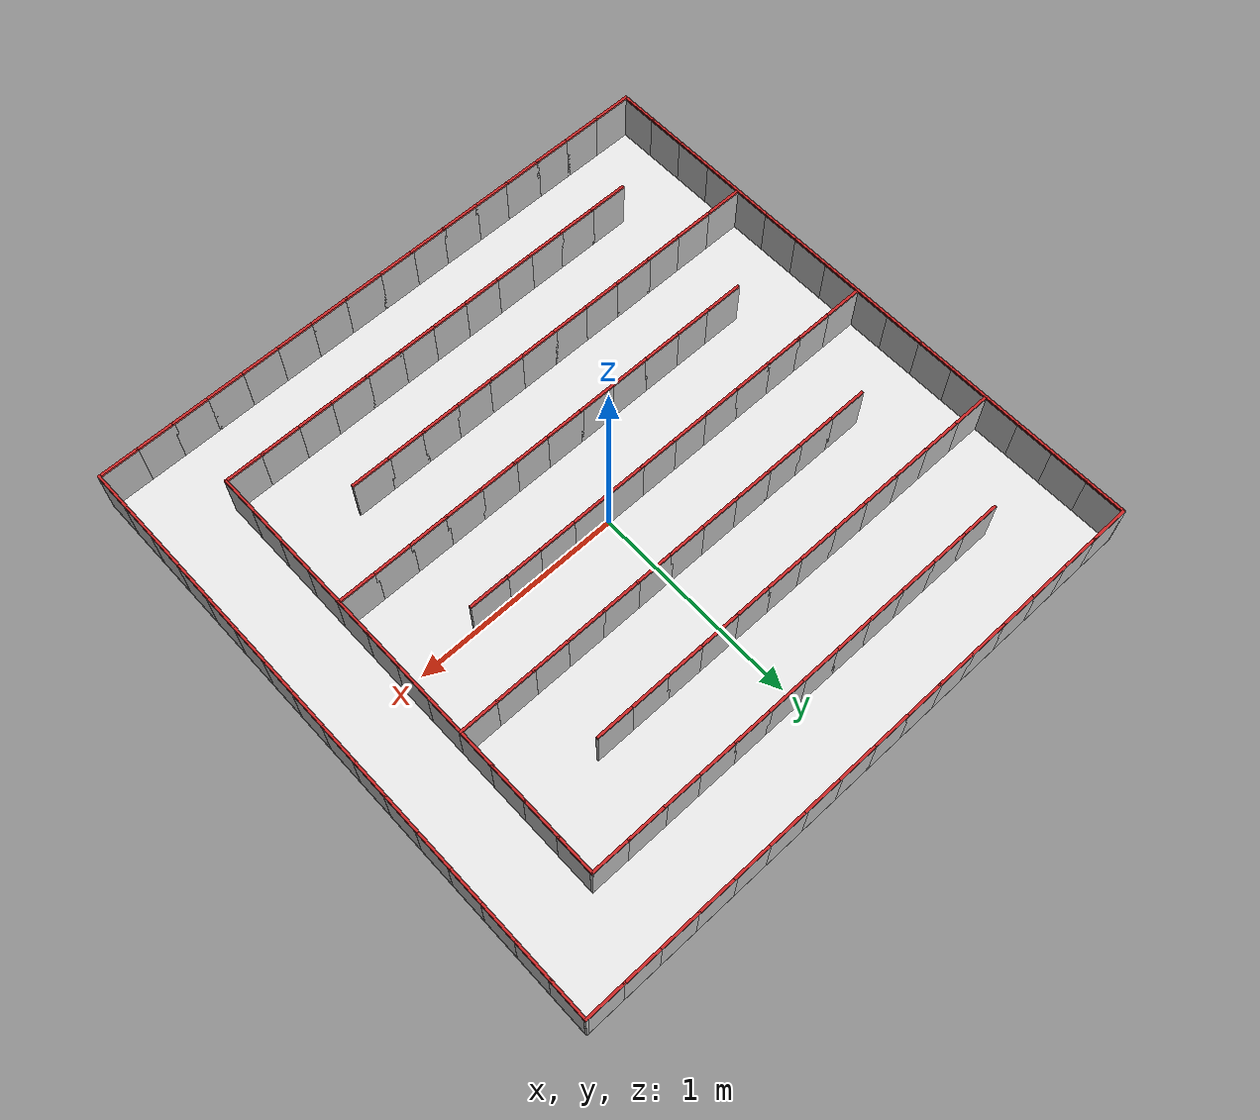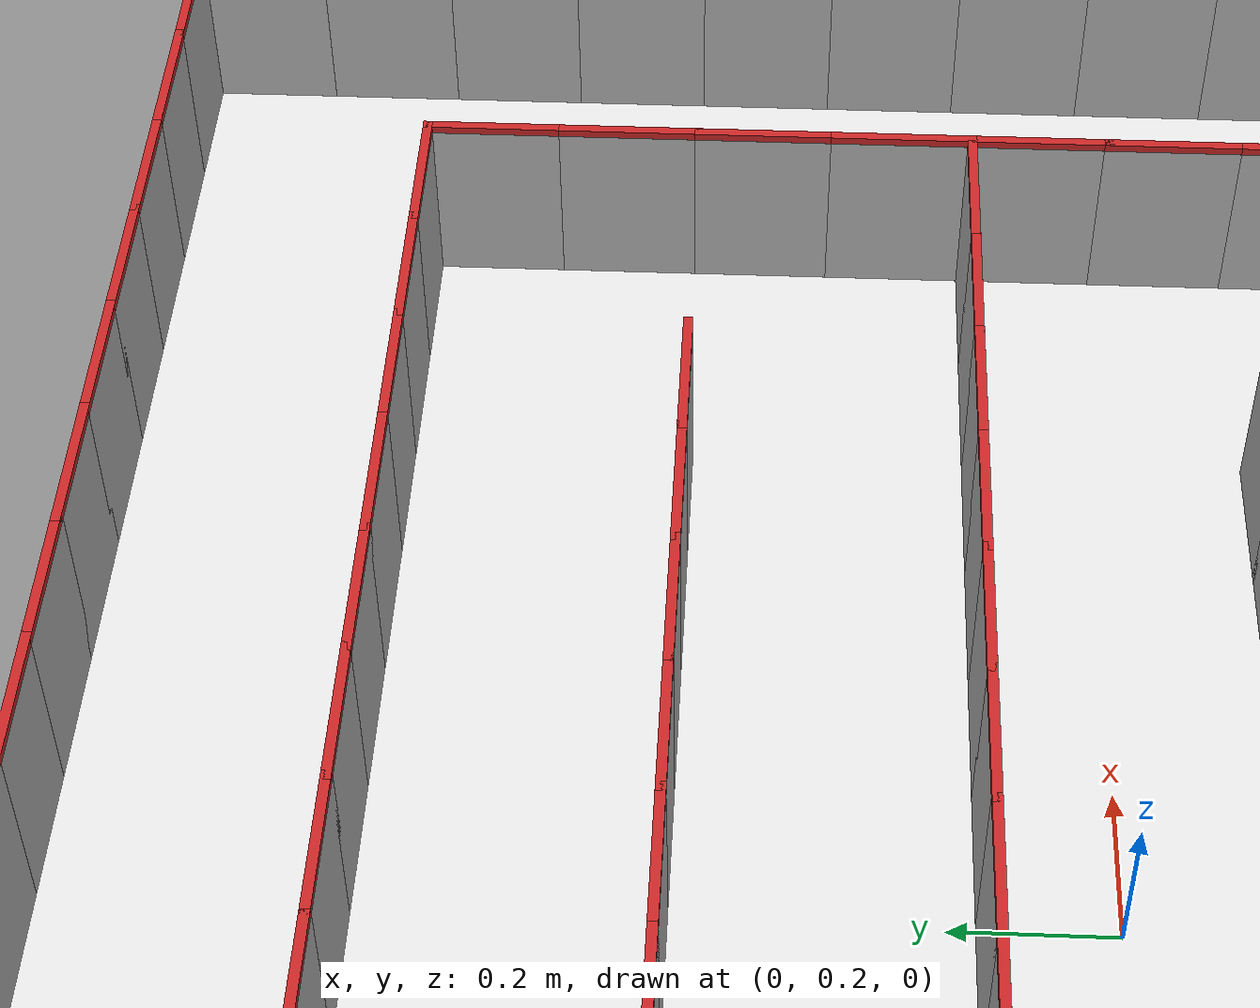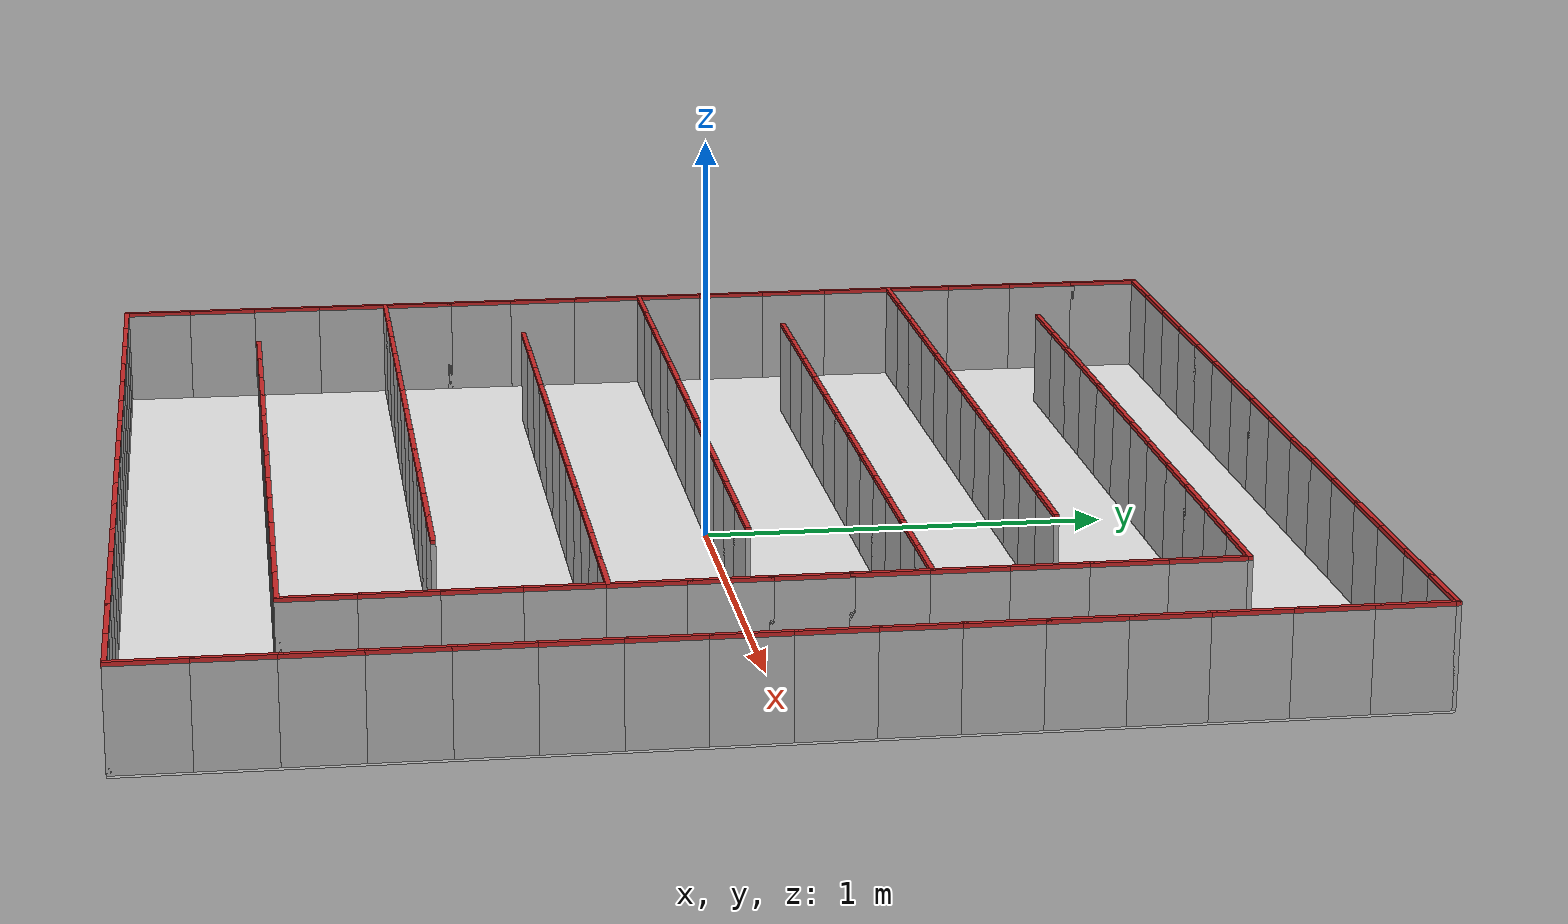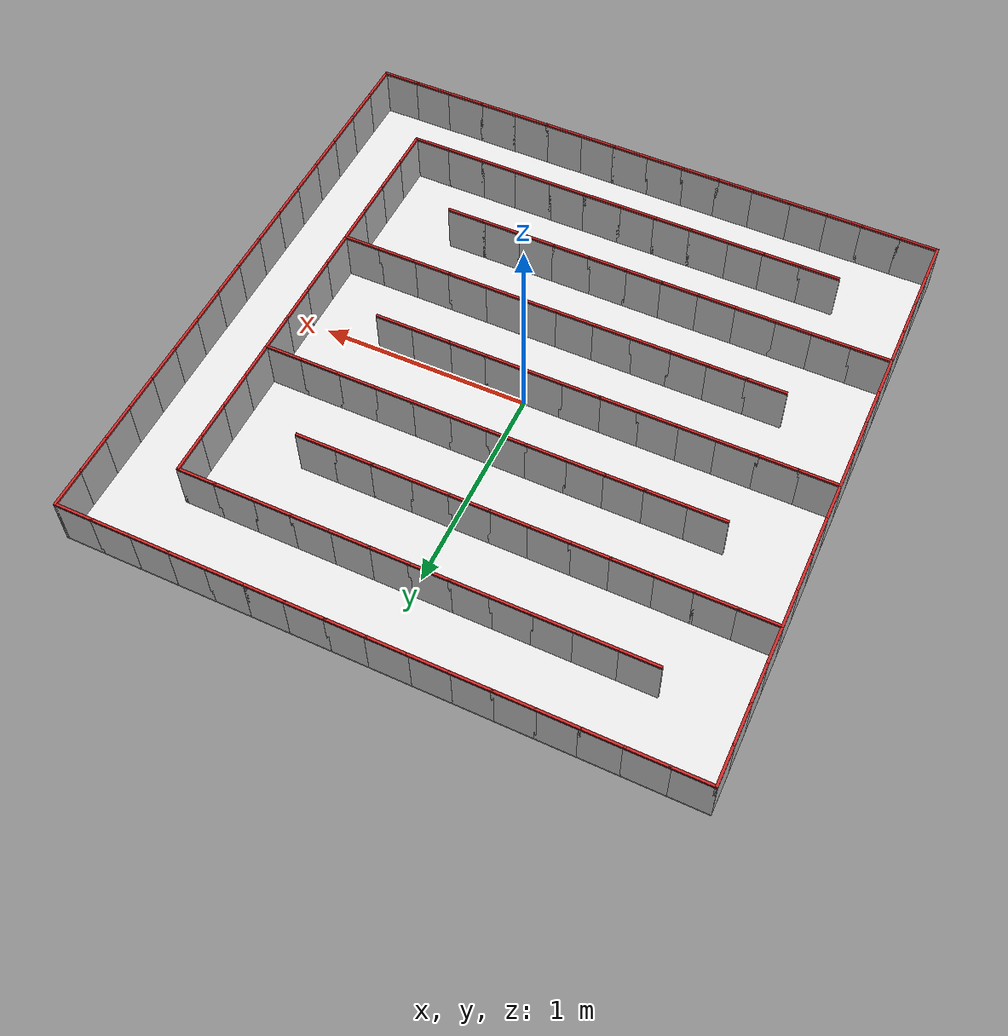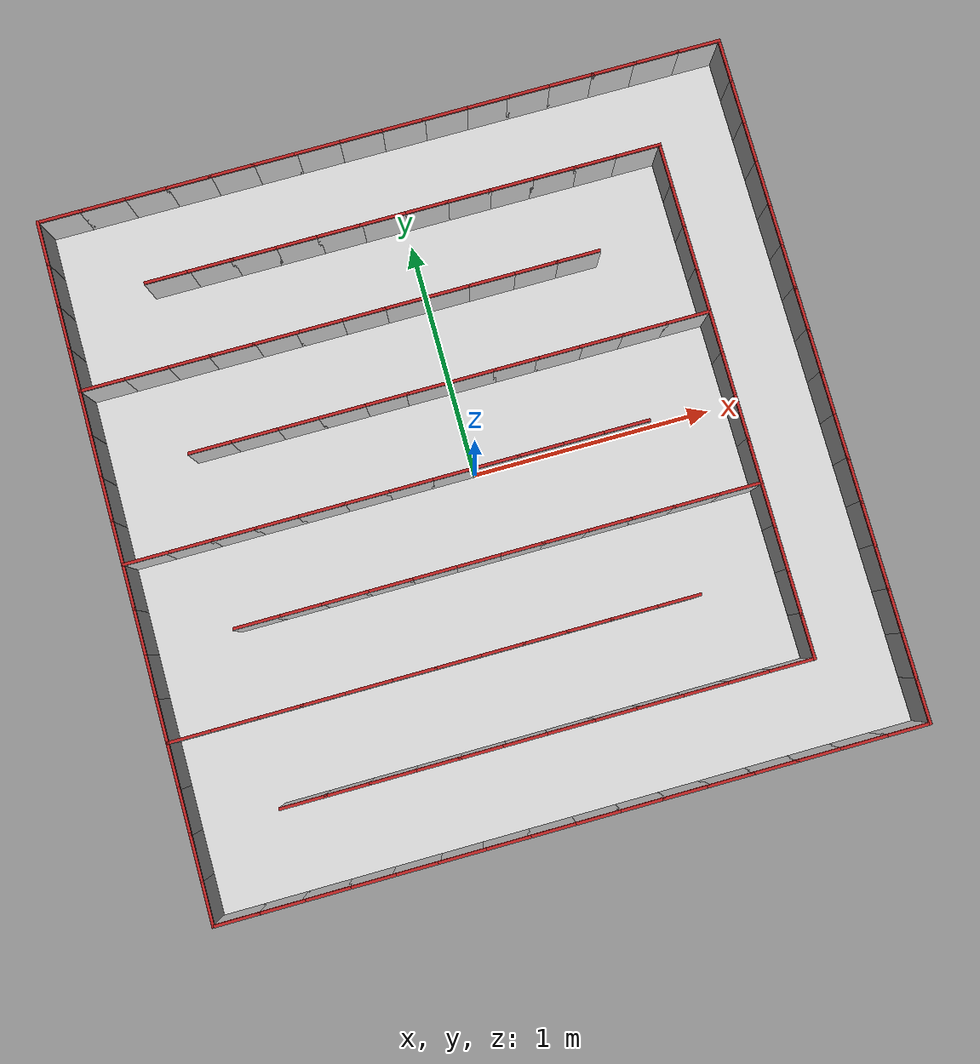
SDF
<?xml version='1.0'?>
<sdf version='1.6'>
  <model name='single_zig_zag'>
    <link name='base'>
      <pose frame=''>0 0 0 0 -0 0</pose>
      <inertial>
        <mass>1</mass>
        <inertia>
          <ixx>1.39394</ixx>
          <ixy>0</ixy>
          <ixz>0</ixz>
          <iyy>0.696972</iyy>
          <iyz>0</iyz>
          <izz>0.696973</izz>
        </inertia>
        <pose frame=''>0 0 0.05 0 -0 0</pose>
      </inertial>
      <self_collide>0</self_collide>
      <kinematic>0</kinematic>
      <visual name='visual'>
        <pose frame=''>0 0 0.0025 0 -0 0</pose>
        <geometry>
          <box>
            <size>2.892 2.892 0.005</size>
          </box>
        </geometry>
        <material>
          <script>
            <uri>file://media/materials/scripts/gazebo.material</uri>
            <name>Gazebo/White</name>
          </script>
          <ambient>1 1 1 1</ambient>
          <diffuse>1 1 1 1</diffuse>
          <specular>0 0 0 1</specular>
          <emissive>0 0 0 1</emissive>
        </material>
        <cast_shadows>1</cast_shadows>
        <transparency>0</transparency>
      </visual>
      <visual name='paint_v_5_3_S'>
        <pose frame=''>-0.81 0.36 0.25 0 -0 0</pose>
        <geometry>
          <box>
            <size>0.192 0.012 0.01</size>
          </box>
        </geometry>
        <material>
          <script>
            <name>Gazebo/Red</name>
            <uri>file://media/materials/scripts/gazebo.material</uri>
          </script>
          <ambient>1 0 0 1</ambient>
          <diffuse>1 0 0 1</diffuse>
          <specular>0.1 0.1 0.1 1</specular>
          <emissive>0 0 0 1</emissive>
        </material>
        <cast_shadows>1</cast_shadows>
        <transparency>0</transparency>
      </visual>
      <visual name='v_5_3_S'>
        <pose frame=''>-0.81 0.36 0.125 0 -0 0</pose>
        <geometry>
          <box>
            <size>0.192 0.012 0.24</size>
          </box>
        </geometry>
        <cast_shadows>1</cast_shadows>
        <transparency>0</transparency>
      </visual>
      <visual name='paint_v_0_0_W'>
        <pose frame=''>-1.44 1.35 0.25 0 -0 1.5708</pose>
        <geometry>
          <box>
            <size>0.192 0.012 0.01</size>
          </box>
        </geometry>
        <material>
          <script>
            <name>Gazebo/Red</name>
            <uri>file://media/materials/scripts/gazebo.material</uri>
          </script>
          <ambient>1 0 0 1</ambient>
          <diffuse>1 0 0 1</diffuse>
          <specular>0.1 0.1 0.1 1</specular>
          <emissive>0 0 0 1</emissive>
        </material>
        <cast_shadows>1</cast_shadows>
        <transparency>0</transparency>
      </visual>
      <visual name='paint_v_1_0_W'>
        <pose frame=''>-1.44 1.17 0.25 0 -0 1.5708</pose>
        <geometry>
          <box>
            <size>0.192 0.012 0.01</size>
          </box>
        </geometry>
        <material>
          <script>
            <name>Gazebo/Red</name>
            <uri>file://media/materials/scripts/gazebo.material</uri>
          </script>
          <ambient>1 0 0 1</ambient>
          <diffuse>1 0 0 1</diffuse>
          <specular>0.1 0.1 0.1 1</specular>
          <emissive>0 0 0 1</emissive>
        </material>
        <cast_shadows>1</cast_shadows>
        <transparency>0</transparency>
      </visual>
      <visual name='v_0_0_W'>
        <pose frame=''>-1.44 1.35 0.125 0 -0 1.5708</pose>
        <geometry>
          <box>
            <size>0.192 0.012 0.24</size>
          </box>
        </geometry>
        <cast_shadows>1</cast_shadows>
        <transparency>0</transparency>
      </visual>
      <visual name='v_1_0_W'>
        <pose frame=''>-1.44 1.17 0.125 0 -0 1.5708</pose>
        <geometry>
          <box>
            <size>0.192 0.012 0.24</size>
          </box>
        </geometry>
        <cast_shadows>1</cast_shadows>
        <transparency>0</transparency>
      </visual>
      <visual name='v_1_2_S'>
        <pose frame=''>-0.99 1.08 0.125 0 -0 0</pose>
        <geometry>
          <box>
            <size>0.192 0.012 0.24</size>
          </box>
        </geometry>
        <cast_shadows>1</cast_shadows>
        <transparency>0</transparency>
      </visual>
      <visual name='paint_v_1_2_S'>
        <pose frame=''>-0.99 1.08 0.25 0 -0 0</pose>
        <geometry>
          <box>
            <size>0.192 0.012 0.01</size>
          </box>
        </geometry>
        <material>
          <script>
            <name>Gazebo/Red</name>
            <uri>file://media/materials/scripts/gazebo.material</uri>
          </script>
          <ambient>1 0 0 1</ambient>
          <diffuse>1 0 0 1</diffuse>
          <specular>0.1 0.1 0.1 1</specular>
          <emissive>0 0 0 1</emissive>
        </material>
        <cast_shadows>1</cast_shadows>
        <transparency>0</transparency>
      </visual>
      <visual name='paint_v_1_3_S'>
        <pose frame=''>-0.81 1.08 0.25 0 -0 0</pose>
        <geometry>
          <box>
            <size>0.192 0.012 0.01</size>
          </box>
        </geometry>
        <material>
          <script>
            <name>Gazebo/Red</name>
            <uri>file://media/materials/scripts/gazebo.material</uri>
          </script>
          <ambient>1 0 0 1</ambient>
          <diffuse>1 0 0 1</diffuse>
          <specular>0.1 0.1 0.1 1</specular>
          <emissive>0 0 0 1</emissive>
        </material>
        <cast_shadows>1</cast_shadows>
        <transparency>0</transparency>
      </visual>
      <visual name='v_1_3_S'>
        <pose frame=''>-0.81 1.08 0.125 0 -0 0</pose>
        <geometry>
          <box>
            <size>0.192 0.012 0.24</size>
          </box>
        </geometry>
        <cast_shadows>1</cast_shadows>
        <transparency>0</transparency>
      </visual>
      <visual name='paint_v_1_4_S'>
        <pose frame=''>-0.63 1.08 0.25 0 -0 0</pose>
        <geometry>
          <box>
            <size>0.192 0.012 0.01</size>
          </box>
        </geometry>
        <material>
          <script>
            <name>Gazebo/Red</name>
            <uri>file://media/materials/scripts/gazebo.material</uri>
          </script>
          <ambient>1 0 0 1</ambient>
          <diffuse>1 0 0 1</diffuse>
          <specular>0.1 0.1 0.1 1</specular>
          <emissive>0 0 0 1</emissive>
        </material>
        <cast_shadows>1</cast_shadows>
        <transparency>0</transparency>
      </visual>
      <visual name='v_1_4_S'>
        <pose frame=''>-0.63 1.08 0.125 0 -0 0</pose>
        <geometry>
          <box>
            <size>0.192 0.012 0.24</size>
          </box>
        </geometry>
        <cast_shadows>1</cast_shadows>
        <transparency>0</transparency>
      </visual>
      <visual name='v_1_5_S'>
        <pose frame=''>-0.45 1.08 0.125 0 -0 0</pose>
        <geometry>
          <box>
            <size>0.192 0.012 0.24</size>
          </box>
        </geometry>
        <cast_shadows>1</cast_shadows>
        <transparency>0</transparency>
      </visual>
      <visual name='paint_v_1_5_S'>
        <pose frame=''>-0.45 1.08 0.25 0 -0 0</pose>
        <geometry>
          <box>
            <size>0.192 0.012 0.01</size>
          </box>
        </geometry>
        <material>
          <script>
            <name>Gazebo/Red</name>
            <uri>file://media/materials/scripts/gazebo.material</uri>
          </script>
          <ambient>1 0 0 1</ambient>
          <diffuse>1 0 0 1</diffuse>
          <specular>0.1 0.1 0.1 1</specular>
          <emissive>0 0 0 1</emissive>
        </material>
        <cast_shadows>1</cast_shadows>
        <transparency>0</transparency>
      </visual>
      <visual name='paint_v_1_6_S'>
        <pose frame=''>-0.27 1.08 0.25 0 -0 0</pose>
        <geometry>
          <box>
            <size>0.192 0.012 0.01</size>
          </box>
        </geometry>
        <material>
          <script>
            <name>Gazebo/Red</name>
            <uri>file://media/materials/scripts/gazebo.material</uri>
          </script>
          <ambient>1 0 0 1</ambient>
          <diffuse>1 0 0 1</diffuse>
          <specular>0.1 0.1 0.1 1</specular>
          <emissive>0 0 0 1</emissive>
        </material>
        <cast_shadows>1</cast_shadows>
        <transparency>0</transparency>
      </visual>
      <visual name='v_1_6_S'>
        <pose frame=''>-0.27 1.08 0.125 0 -0 0</pose>
        <geometry>
          <box>
            <size>0.192 0.012 0.24</size>
          </box>
        </geometry>
        <cast_shadows>1</cast_shadows>
        <transparency>0</transparency>
      </visual>
      <visual name='paint_v_1_7_S'>
        <pose frame=''>-0.09 1.08 0.25 0 -0 0</pose>
        <geometry>
          <box>
            <size>0.192 0.012 0.01</size>
          </box>
        </geometry>
        <material>
          <script>
            <name>Gazebo/Red</name>
            <uri>file://media/materials/scripts/gazebo.material</uri>
          </script>
          <ambient>1 0 0 1</ambient>
          <diffuse>1 0 0 1</diffuse>
          <specular>0.1 0.1 0.1 1</specular>
          <emissive>0 0 0 1</emissive>
        </material>
        <cast_shadows>1</cast_shadows>
        <transparency>0</transparency>
      </visual>
      <visual name='v_1_7_S'>
        <pose frame=''>-0.09 1.08 0.125 0 -0 0</pose>
        <geometry>
          <box>
            <size>0.192 0.012 0.24</size>
          </box>
        </geometry>
        <cast_shadows>1</cast_shadows>
        <transparency>0</transparency>
      </visual>
      <visual name='paint_v_1_8_S'>
        <pose frame=''>0.09 1.08 0.25 0 -0 0</pose>
        <geometry>
          <box>
            <size>0.192 0.012 0.01</size>
          </box>
        </geometry>
        <material>
          <script>
            <name>Gazebo/Red</name>
            <uri>file://media/materials/scripts/gazebo.material</uri>
          </script>
          <ambient>1 0 0 1</ambient>
          <diffuse>1 0 0 1</diffuse>
          <specular>0.1 0.1 0.1 1</specular>
          <emissive>0 0 0 1</emissive>
        </material>
        <cast_shadows>1</cast_shadows>
        <transparency>0</transparency>
      </visual>
      <visual name='v_1_8_S'>
        <pose frame=''>0.09 1.08 0.125 0 -0 0</pose>
        <geometry>
          <box>
            <size>0.192 0.012 0.24</size>
          </box>
        </geometry>
        <cast_shadows>1</cast_shadows>
        <transparency>0</transparency>
      </visual>
      <visual name='paint_v_1_9_S'>
        <pose frame=''>0.27 1.08 0.25 0 -0 0</pose>
        <geometry>
          <box>
            <size>0.192 0.012 0.01</size>
          </box>
        </geometry>
        <material>
          <script>
            <name>Gazebo/Red</name>
            <uri>file://media/materials/scripts/gazebo.material</uri>
          </script>
          <ambient>1 0 0 1</ambient>
          <diffuse>1 0 0 1</diffuse>
          <specular>0.1 0.1 0.1 1</specular>
          <emissive>0 0 0 1</emissive>
        </material>
        <cast_shadows>1</cast_shadows>
        <transparency>0</transparency>
      </visual>
      <visual name='v_1_9_S'>
        <pose frame=''>0.27 1.08 0.125 0 -0 0</pose>
        <geometry>
          <box>
            <size>0.192 0.012 0.24</size>
          </box>
        </geometry>
        <cast_shadows>1</cast_shadows>
        <transparency>0</transparency>
      </visual>
      <visual name='paint_v_1_10_S'>
        <pose frame=''>0.45 1.08 0.25 0 -0 0</pose>
        <geometry>
          <box>
            <size>0.192 0.012 0.01</size>
          </box>
        </geometry>
        <material>
          <script>
            <name>Gazebo/Red</name>
            <uri>file://media/materials/scripts/gazebo.material</uri>
          </script>
          <ambient>1 0 0 1</ambient>
          <diffuse>1 0 0 1</diffuse>
          <specular>0.1 0.1 0.1 1</specular>
          <emissive>0 0 0 1</emissive>
        </material>
        <cast_shadows>1</cast_shadows>
        <transparency>0</transparency>
      </visual>
      <visual name='v_1_10_S'>
        <pose frame=''>0.45 1.08 0.125 0 -0 0</pose>
        <geometry>
          <box>
            <size>0.192 0.012 0.24</size>
          </box>
        </geometry>
        <cast_shadows>1</cast_shadows>
        <transparency>0</transparency>
      </visual>
      <visual name='paint_v_1_11_S'>
        <pose frame=''>0.63 1.08 0.25 0 -0 0</pose>
        <geometry>
          <box>
            <size>0.192 0.012 0.01</size>
          </box>
        </geometry>
        <material>
          <script>
            <name>Gazebo/Red</name>
            <uri>file://media/materials/scripts/gazebo.material</uri>
          </script>
          <ambient>1 0 0 1</ambient>
          <diffuse>1 0 0 1</diffuse>
          <specular>0.1 0.1 0.1 1</specular>
          <emissive>0 0 0 1</emissive>
        </material>
        <cast_shadows>1</cast_shadows>
        <transparency>0</transparency>
      </visual>
      <visual name='v_3_6_S'>
        <pose frame=''>-0.27 0.72 0.125 0 -0 0</pose>
        <geometry>
          <box>
            <size>0.192 0.012 0.24</size>
          </box>
        </geometry>
        <cast_shadows>1</cast_shadows>
        <transparency>0</transparency>
      </visual>
      <visual name='v_1_11_S'>
        <pose frame=''>0.63 1.08 0.125 0 -0 0</pose>
        <geometry>
          <box>
            <size>0.192 0.012 0.24</size>
          </box>
        </geometry>
        <cast_shadows>1</cast_shadows>
        <transparency>0</transparency>
      </visual>
      <visual name='paint_v_1_12_S'>
        <pose frame=''>0.81 1.08 0.25 0 -0 0</pose>
        <geometry>
          <box>
            <size>0.192 0.012 0.01</size>
          </box>
        </geometry>
        <material>
          <script>
            <name>Gazebo/Red</name>
            <uri>file://media/materials/scripts/gazebo.material</uri>
          </script>
          <ambient>1 0 0 1</ambient>
          <diffuse>1 0 0 1</diffuse>
          <specular>0.1 0.1 0.1 1</specular>
          <emissive>0 0 0 1</emissive>
        </material>
        <cast_shadows>1</cast_shadows>
        <transparency>0</transparency>
      </visual>
      <visual name='v_1_12_S'>
        <pose frame=''>0.81 1.08 0.125 0 -0 0</pose>
        <geometry>
          <box>
            <size>0.192 0.012 0.24</size>
          </box>
        </geometry>
        <cast_shadows>1</cast_shadows>
        <transparency>0</transparency>
      </visual>
      <visual name='paint_v_1_13_S'>
        <pose frame=''>0.99 1.08 0.25 0 -0 0</pose>
        <geometry>
          <box>
            <size>0.192 0.012 0.01</size>
          </box>
        </geometry>
        <material>
          <script>
            <name>Gazebo/Red</name>
            <uri>file://media/materials/scripts/gazebo.material</uri>
          </script>
          <ambient>1 0 0 1</ambient>
          <diffuse>1 0 0 1</diffuse>
          <specular>0.1 0.1 0.1 1</specular>
          <emissive>0 0 0 1</emissive>
        </material>
        <cast_shadows>1</cast_shadows>
        <transparency>0</transparency>
      </visual>
      <visual name='v_1_13_S'>
        <pose frame=''>0.99 1.08 0.125 0 -0 0</pose>
        <geometry>
          <box>
            <size>0.192 0.012 0.24</size>
          </box>
        </geometry>
        <cast_shadows>1</cast_shadows>
        <transparency>0</transparency>
      </visual>
      <visual name='v_2_0_W'>
        <pose frame=''>-1.44 0.99 0.125 0 -0 1.5708</pose>
        <geometry>
          <box>
            <size>0.192 0.012 0.24</size>
          </box>
        </geometry>
        <cast_shadows>1</cast_shadows>
        <transparency>0</transparency>
      </visual>
      <visual name='paint_v_2_0_W'>
        <pose frame=''>-1.44 0.99 0.25 0 -0 1.5708</pose>
        <geometry>
          <box>
            <size>0.192 0.012 0.01</size>
          </box>
        </geometry>
        <material>
          <script>
            <name>Gazebo/Red</name>
            <uri>file://media/materials/scripts/gazebo.material</uri>
          </script>
          <ambient>1 0 0 1</ambient>
          <diffuse>1 0 0 1</diffuse>
          <specular>0.1 0.1 0.1 1</specular>
          <emissive>0 0 0 1</emissive>
        </material>
        <cast_shadows>1</cast_shadows>
        <transparency>0</transparency>
      </visual>
      <visual name='paint_v_2_14_W'>
        <pose frame=''>1.08 0.99 0.25 0 -0 1.5708</pose>
        <geometry>
          <box>
            <size>0.192 0.012 0.01</size>
          </box>
        </geometry>
        <material>
          <script>
            <name>Gazebo/Red</name>
            <uri>file://media/materials/scripts/gazebo.material</uri>
          </script>
          <ambient>1 0 0 1</ambient>
          <diffuse>1 0 0 1</diffuse>
          <specular>0.1 0.1 0.1 1</specular>
          <emissive>0 0 0 1</emissive>
        </material>
        <cast_shadows>1</cast_shadows>
        <transparency>0</transparency>
      </visual>
      <visual name='v_2_14_W'>
        <pose frame=''>1.08 0.99 0.125 0 -0 1.5708</pose>
        <geometry>
          <box>
            <size>0.192 0.012 0.24</size>
          </box>
        </geometry>
        <cast_shadows>1</cast_shadows>
        <transparency>0</transparency>
      </visual>
      <visual name='paint_v_3_0_W'>
        <pose frame=''>-1.44 0.81 0.25 0 -0 1.5708</pose>
        <geometry>
          <box>
            <size>0.192 0.012 0.01</size>
          </box>
        </geometry>
        <material>
          <script>
            <name>Gazebo/Red</name>
            <uri>file://media/materials/scripts/gazebo.material</uri>
          </script>
          <ambient>1 0 0 1</ambient>
          <diffuse>1 0 0 1</diffuse>
          <specular>0.1 0.1 0.1 1</specular>
          <emissive>0 0 0 1</emissive>
        </material>
        <cast_shadows>1</cast_shadows>
        <transparency>0</transparency>
      </visual>
      <visual name='v_3_0_W'>
        <pose frame=''>-1.44 0.81 0.125 0 -0 1.5708</pose>
        <geometry>
          <box>
            <size>0.192 0.012 0.24</size>
          </box>
        </geometry>
        <cast_shadows>1</cast_shadows>
        <transparency>0</transparency>
      </visual>
      <visual name='paint_v_3_0_S'>
        <pose frame=''>-1.35 0.72 0.25 0 -0 0</pose>
        <geometry>
          <box>
            <size>0.192 0.012 0.01</size>
          </box>
        </geometry>
        <material>
          <script>
            <name>Gazebo/Red</name>
            <uri>file://media/materials/scripts/gazebo.material</uri>
          </script>
          <ambient>1 0 0 1</ambient>
          <diffuse>1 0 0 1</diffuse>
          <specular>0.1 0.1 0.1 1</specular>
          <emissive>0 0 0 1</emissive>
        </material>
        <cast_shadows>1</cast_shadows>
        <transparency>0</transparency>
      </visual>
      <visual name='v_3_0_S'>
        <pose frame=''>-1.35 0.72 0.125 0 -0 0</pose>
        <geometry>
          <box>
            <size>0.192 0.012 0.24</size>
          </box>
        </geometry>
        <cast_shadows>1</cast_shadows>
        <transparency>0</transparency>
      </visual>
      <visual name='paint_v_3_1_S'>
        <pose frame=''>-1.17 0.72 0.25 0 -0 0</pose>
        <geometry>
          <box>
            <size>0.192 0.012 0.01</size>
          </box>
        </geometry>
        <material>
          <script>
            <name>Gazebo/Red</name>
            <uri>file://media/materials/scripts/gazebo.material</uri>
          </script>
          <ambient>1 0 0 1</ambient>
          <diffuse>1 0 0 1</diffuse>
          <specular>0.1 0.1 0.1 1</specular>
          <emissive>0 0 0 1</emissive>
        </material>
        <cast_shadows>1</cast_shadows>
        <transparency>0</transparency>
      </visual>
      <visual name='v_3_1_S'>
        <pose frame=''>-1.17 0.72 0.125 0 -0 0</pose>
        <geometry>
          <box>
            <size>0.192 0.012 0.24</size>
          </box>
        </geometry>
        <cast_shadows>1</cast_shadows>
        <transparency>0</transparency>
      </visual>
      <visual name='paint_v_3_2_S'>
        <pose frame=''>-0.99 0.72 0.25 0 -0 0</pose>
        <geometry>
          <box>
            <size>0.192 0.012 0.01</size>
          </box>
        </geometry>
        <material>
          <script>
            <name>Gazebo/Red</name>
            <uri>file://media/materials/scripts/gazebo.material</uri>
          </script>
          <ambient>1 0 0 1</ambient>
          <diffuse>1 0 0 1</diffuse>
          <specular>0.1 0.1 0.1 1</specular>
          <emissive>0 0 0 1</emissive>
        </material>
        <cast_shadows>1</cast_shadows>
        <transparency>0</transparency>
      </visual>
      <visual name='v_3_2_S'>
        <pose frame=''>-0.99 0.72 0.125 0 -0 0</pose>
        <geometry>
          <box>
            <size>0.192 0.012 0.24</size>
          </box>
        </geometry>
        <cast_shadows>1</cast_shadows>
        <transparency>0</transparency>
      </visual>
      <visual name='paint_v_3_3_S'>
        <pose frame=''>-0.81 0.72 0.25 0 -0 0</pose>
        <geometry>
          <box>
            <size>0.192 0.012 0.01</size>
          </box>
        </geometry>
        <material>
          <script>
            <name>Gazebo/Red</name>
            <uri>file://media/materials/scripts/gazebo.material</uri>
          </script>
          <ambient>1 0 0 1</ambient>
          <diffuse>1 0 0 1</diffuse>
          <specular>0.1 0.1 0.1 1</specular>
          <emissive>0 0 0 1</emissive>
        </material>
        <cast_shadows>1</cast_shadows>
        <transparency>0</transparency>
      </visual>
      <visual name='v_3_3_S'>
        <pose frame=''>-0.81 0.72 0.125 0 -0 0</pose>
        <geometry>
          <box>
            <size>0.192 0.012 0.24</size>
          </box>
        </geometry>
        <cast_shadows>1</cast_shadows>
        <transparency>0</transparency>
      </visual>
      <visual name='v_3_4_S'>
        <pose frame=''>-0.63 0.72 0.125 0 -0 0</pose>
        <geometry>
          <box>
            <size>0.192 0.012 0.24</size>
          </box>
        </geometry>
        <cast_shadows>1</cast_shadows>
        <transparency>0</transparency>
      </visual>
      <visual name='paint_v_3_4_S'>
        <pose frame=''>-0.63 0.72 0.25 0 -0 0</pose>
        <geometry>
          <box>
            <size>0.192 0.012 0.01</size>
          </box>
        </geometry>
        <material>
          <script>
            <name>Gazebo/Red</name>
            <uri>file://media/materials/scripts/gazebo.material</uri>
          </script>
          <ambient>1 0 0 1</ambient>
          <diffuse>1 0 0 1</diffuse>
          <specular>0.1 0.1 0.1 1</specular>
          <emissive>0 0 0 1</emissive>
        </material>
        <cast_shadows>1</cast_shadows>
        <transparency>0</transparency>
      </visual>
      <visual name='paint_v_3_5_S'>
        <pose frame=''>-0.45 0.72 0.25 0 -0 0</pose>
        <geometry>
          <box>
            <size>0.192 0.012 0.01</size>
          </box>
        </geometry>
        <material>
          <script>
            <name>Gazebo/Red</name>
            <uri>file://media/materials/scripts/gazebo.material</uri>
          </script>
          <ambient>1 0 0 1</ambient>
          <diffuse>1 0 0 1</diffuse>
          <specular>0.1 0.1 0.1 1</specular>
          <emissive>0 0 0 1</emissive>
        </material>
        <cast_shadows>1</cast_shadows>
        <transparency>0</transparency>
      </visual>
      <visual name='v_3_5_S'>
        <pose frame=''>-0.45 0.72 0.125 0 -0 0</pose>
        <geometry>
          <box>
            <size>0.192 0.012 0.24</size>
          </box>
        </geometry>
        <cast_shadows>1</cast_shadows>
        <transparency>0</transparency>
      </visual>
      <visual name='paint_v_3_6_S'>
        <pose frame=''>-0.27 0.72 0.25 0 -0 0</pose>
        <geometry>
          <box>
            <size>0.192 0.012 0.01</size>
          </box>
        </geometry>
        <material>
          <script>
            <name>Gazebo/Red</name>
            <uri>file://media/materials/scripts/gazebo.material</uri>
          </script>
          <ambient>1 0 0 1</ambient>
          <diffuse>1 0 0 1</diffuse>
          <specular>0.1 0.1 0.1 1</specular>
          <emissive>0 0 0 1</emissive>
        </material>
        <cast_shadows>1</cast_shadows>
        <transparency>0</transparency>
      </visual>
      <visual name='v_3_7_S'>
        <pose frame=''>-0.09 0.72 0.125 0 -0 0</pose>
        <geometry>
          <box>
            <size>0.192 0.012 0.24</size>
          </box>
        </geometry>
        <cast_shadows>1</cast_shadows>
        <transparency>0</transparency>
      </visual>
      <visual name='paint_v_3_7_S'>
        <pose frame=''>-0.09 0.72 0.25 0 -0 0</pose>
        <geometry>
          <box>
            <size>0.192 0.012 0.01</size>
          </box>
        </geometry>
        <material>
          <script>
            <name>Gazebo/Red</name>
            <uri>file://media/materials/scripts/gazebo.material</uri>
          </script>
          <ambient>1 0 0 1</ambient>
          <diffuse>1 0 0 1</diffuse>
          <specular>0.1 0.1 0.1 1</specular>
          <emissive>0 0 0 1</emissive>
        </material>
        <cast_shadows>1</cast_shadows>
        <transparency>0</transparency>
      </visual>
      <visual name='paint_v_3_8_S'>
        <pose frame=''>0.09 0.72 0.25 0 -0 0</pose>
        <geometry>
          <box>
            <size>0.192 0.012 0.01</size>
          </box>
        </geometry>
        <material>
          <script>
            <name>Gazebo/Red</name>
            <uri>file://media/materials/scripts/gazebo.material</uri>
          </script>
          <ambient>1 0 0 1</ambient>
          <diffuse>1 0 0 1</diffuse>
          <specular>0.1 0.1 0.1 1</specular>
          <emissive>0 0 0 1</emissive>
        </material>
        <cast_shadows>1</cast_shadows>
        <transparency>0</transparency>
      </visual>
      <visual name='v_3_8_S'>
        <pose frame=''>0.09 0.72 0.125 0 -0 0</pose>
        <geometry>
          <box>
            <size>0.192 0.012 0.24</size>
          </box>
        </geometry>
        <cast_shadows>1</cast_shadows>
        <transparency>0</transparency>
      </visual>
      <visual name='paint_v_3_9_S'>
        <pose frame=''>0.27 0.72 0.25 0 -0 0</pose>
        <geometry>
          <box>
            <size>0.192 0.012 0.01</size>
          </box>
        </geometry>
        <material>
          <script>
            <name>Gazebo/Red</name>
            <uri>file://media/materials/scripts/gazebo.material</uri>
          </script>
          <ambient>1 0 0 1</ambient>
          <diffuse>1 0 0 1</diffuse>
          <specular>0.1 0.1 0.1 1</specular>
          <emissive>0 0 0 1</emissive>
        </material>
        <cast_shadows>1</cast_shadows>
        <transparency>0</transparency>
      </visual>
      <visual name='v_3_9_S'>
        <pose frame=''>0.27 0.72 0.125 0 -0 0</pose>
        <geometry>
          <box>
            <size>0.192 0.012 0.24</size>
          </box>
        </geometry>
        <cast_shadows>1</cast_shadows>
        <transparency>0</transparency>
      </visual>
      <visual name='paint_v_3_10_S'>
        <pose frame=''>0.45 0.72 0.25 0 -0 0</pose>
        <geometry>
          <box>
            <size>0.192 0.012 0.01</size>
          </box>
        </geometry>
        <material>
          <script>
            <name>Gazebo/Red</name>
            <uri>file://media/materials/scripts/gazebo.material</uri>
          </script>
          <ambient>1 0 0 1</ambient>
          <diffuse>1 0 0 1</diffuse>
          <specular>0.1 0.1 0.1 1</specular>
          <emissive>0 0 0 1</emissive>
        </material>
        <cast_shadows>1</cast_shadows>
        <transparency>0</transparency>
      </visual>
      <visual name='v_3_10_S'>
        <pose frame=''>0.45 0.72 0.125 0 -0 0</pose>
        <geometry>
          <box>
            <size>0.192 0.012 0.24</size>
          </box>
        </geometry>
        <cast_shadows>1</cast_shadows>
        <transparency>0</transparency>
      </visual>
      <visual name='paint_v_3_11_S'>
        <pose frame=''>0.63 0.72 0.25 0 -0 0</pose>
        <geometry>
          <box>
            <size>0.192 0.012 0.01</size>
          </box>
        </geometry>
        <material>
          <script>
            <name>Gazebo/Red</name>
            <uri>file://media/materials/scripts/gazebo.material</uri>
          </script>
          <ambient>1 0 0 1</ambient>
          <diffuse>1 0 0 1</diffuse>
          <specular>0.1 0.1 0.1 1</specular>
          <emissive>0 0 0 1</emissive>
        </material>
        <cast_shadows>1</cast_shadows>
        <transparency>0</transparency>
      </visual>
      <visual name='v_3_11_S'>
        <pose frame=''>0.63 0.72 0.125 0 -0 0</pose>
        <geometry>
          <box>
            <size>0.192 0.012 0.24</size>
          </box>
        </geometry>
        <cast_shadows>1</cast_shadows>
        <transparency>0</transparency>
      </visual>
      <visual name='v_3_14_W'>
        <pose frame=''>1.08 0.81 0.125 0 -0 1.5708</pose>
        <geometry>
          <box>
            <size>0.192 0.012 0.24</size>
          </box>
        </geometry>
        <cast_shadows>1</cast_shadows>
        <transparency>0</transparency>
      </visual>
      <visual name='paint_v_3_14_W'>
        <pose frame=''>1.08 0.81 0.25 0 -0 1.5708</pose>
        <geometry>
          <box>
            <size>0.192 0.012 0.01</size>
          </box>
        </geometry>
        <material>
          <script>
            <name>Gazebo/Red</name>
            <uri>file://media/materials/scripts/gazebo.material</uri>
          </script>
          <ambient>1 0 0 1</ambient>
          <diffuse>1 0 0 1</diffuse>
          <specular>0.1 0.1 0.1 1</specular>
          <emissive>0 0 0 1</emissive>
        </material>
        <cast_shadows>1</cast_shadows>
        <transparency>0</transparency>
      </visual>
      <visual name='paint_v_4_0_W'>
        <pose frame=''>-1.44 0.63 0.25 0 -0 1.5708</pose>
        <geometry>
          <box>
            <size>0.192 0.012 0.01</size>
          </box>
        </geometry>
        <material>
          <script>
            <name>Gazebo/Red</name>
            <uri>file://media/materials/scripts/gazebo.material</uri>
          </script>
          <ambient>1 0 0 1</ambient>
          <diffuse>1 0 0 1</diffuse>
          <specular>0.1 0.1 0.1 1</specular>
          <emissive>0 0 0 1</emissive>
        </material>
        <cast_shadows>1</cast_shadows>
        <transparency>0</transparency>
      </visual>
      <visual name='v_4_0_W'>
        <pose frame=''>-1.44 0.63 0.125 0 -0 1.5708</pose>
        <geometry>
          <box>
            <size>0.192 0.012 0.24</size>
          </box>
        </geometry>
        <cast_shadows>1</cast_shadows>
        <transparency>0</transparency>
      </visual>
      <visual name='paint_v_4_14_W'>
        <pose frame=''>1.08 0.63 0.25 0 -0 1.5708</pose>
        <geometry>
          <box>
            <size>0.192 0.012 0.01</size>
          </box>
        </geometry>
        <material>
          <script>
            <name>Gazebo/Red</name>
            <uri>file://media/materials/scripts/gazebo.material</uri>
          </script>
          <ambient>1 0 0 1</ambient>
          <diffuse>1 0 0 1</diffuse>
          <specular>0.1 0.1 0.1 1</specular>
          <emissive>0 0 0 1</emissive>
        </material>
        <cast_shadows>1</cast_shadows>
        <transparency>0</transparency>
      </visual>
      <visual name='v_4_14_W'>
        <pose frame=''>1.08 0.63 0.125 0 -0 1.5708</pose>
        <geometry>
          <box>
            <size>0.192 0.012 0.24</size>
          </box>
        </geometry>
        <cast_shadows>1</cast_shadows>
        <transparency>0</transparency>
      </visual>
      <visual name='v_5_0_W'>
        <pose frame=''>-1.44 0.45 0.125 0 -0 1.5708</pose>
        <geometry>
          <box>
            <size>0.192 0.012 0.24</size>
          </box>
        </geometry>
        <cast_shadows>1</cast_shadows>
        <transparency>0</transparency>
      </visual>
      <visual name='paint_v_5_0_W'>
        <pose frame=''>-1.44 0.45 0.25 0 -0 1.5708</pose>
        <geometry>
          <box>
            <size>0.192 0.012 0.01</size>
          </box>
        </geometry>
        <material>
          <script>
            <name>Gazebo/Red</name>
            <uri>file://media/materials/scripts/gazebo.material</uri>
          </script>
          <ambient>1 0 0 1</ambient>
          <diffuse>1 0 0 1</diffuse>
          <specular>0.1 0.1 0.1 1</specular>
          <emissive>0 0 0 1</emissive>
        </material>
        <cast_shadows>1</cast_shadows>
        <transparency>0</transparency>
      </visual>
      <visual name='paint_v_5_2_S'>
        <pose frame=''>-0.99 0.36 0.25 0 -0 0</pose>
        <geometry>
          <box>
            <size>0.192 0.012 0.01</size>
          </box>
        </geometry>
        <material>
          <script>
            <name>Gazebo/Red</name>
            <uri>file://media/materials/scripts/gazebo.material</uri>
          </script>
          <ambient>1 0 0 1</ambient>
          <diffuse>1 0 0 1</diffuse>
          <specular>0.1 0.1 0.1 1</specular>
          <emissive>0 0 0 1</emissive>
        </material>
        <cast_shadows>1</cast_shadows>
        <transparency>0</transparency>
      </visual>
      <visual name='v_5_2_S'>
        <pose frame=''>-0.99 0.36 0.125 0 -0 0</pose>
        <geometry>
          <box>
            <size>0.192 0.012 0.24</size>
          </box>
        </geometry>
        <cast_shadows>1</cast_shadows>
        <transparency>0</transparency>
      </visual>
      <visual name='paint_v_5_4_S'>
        <pose frame=''>-0.63 0.36 0.25 0 -0 0</pose>
        <geometry>
          <box>
            <size>0.192 0.012 0.01</size>
          </box>
        </geometry>
        <material>
          <script>
            <name>Gazebo/Red</name>
            <uri>file://media/materials/scripts/gazebo.material</uri>
          </script>
          <ambient>1 0 0 1</ambient>
          <diffuse>1 0 0 1</diffuse>
          <specular>0.1 0.1 0.1 1</specular>
          <emissive>0 0 0 1</emissive>
        </material>
        <cast_shadows>1</cast_shadows>
        <transparency>0</transparency>
      </visual>
      <visual name='v_5_4_S'>
        <pose frame=''>-0.63 0.36 0.125 0 -0 0</pose>
        <geometry>
          <box>
            <size>0.192 0.012 0.24</size>
          </box>
        </geometry>
        <cast_shadows>1</cast_shadows>
        <transparency>0</transparency>
      </visual>
      <visual name='paint_v_5_5_S'>
        <pose frame=''>-0.45 0.36 0.25 0 -0 0</pose>
        <geometry>
          <box>
            <size>0.192 0.012 0.01</size>
          </box>
        </geometry>
        <material>
          <script>
            <name>Gazebo/Red</name>
            <uri>file://media/materials/scripts/gazebo.material</uri>
          </script>
          <ambient>1 0 0 1</ambient>
          <diffuse>1 0 0 1</diffuse>
          <specular>0.1 0.1 0.1 1</specular>
          <emissive>0 0 0 1</emissive>
        </material>
        <cast_shadows>1</cast_shadows>
        <transparency>0</transparency>
      </visual>
      <visual name='v_5_5_S'>
        <pose frame=''>-0.45 0.36 0.125 0 -0 0</pose>
        <geometry>
          <box>
            <size>0.192 0.012 0.24</size>
          </box>
        </geometry>
        <cast_shadows>1</cast_shadows>
        <transparency>0</transparency>
      </visual>
      <visual name='v_5_6_S'>
        <pose frame=''>-0.27 0.36 0.125 0 -0 0</pose>
        <geometry>
          <box>
            <size>0.192 0.012 0.24</size>
          </box>
        </geometry>
        <cast_shadows>1</cast_shadows>
        <transparency>0</transparency>
      </visual>
      <visual name='paint_v_5_6_S'>
        <pose frame=''>-0.27 0.36 0.25 0 -0 0</pose>
        <geometry>
          <box>
            <size>0.192 0.012 0.01</size>
          </box>
        </geometry>
        <material>
          <script>
            <name>Gazebo/Red</name>
            <uri>file://media/materials/scripts/gazebo.material</uri>
          </script>
          <ambient>1 0 0 1</ambient>
          <diffuse>1 0 0 1</diffuse>
          <specular>0.1 0.1 0.1 1</specular>
          <emissive>0 0 0 1</emissive>
        </material>
        <cast_shadows>1</cast_shadows>
        <transparency>0</transparency>
      </visual>
      <visual name='paint_v_5_7_S'>
        <pose frame=''>-0.09 0.36 0.25 0 -0 0</pose>
        <geometry>
          <box>
            <size>0.192 0.012 0.01</size>
          </box>
        </geometry>
        <material>
          <script>
            <name>Gazebo/Red</name>
            <uri>file://media/materials/scripts/gazebo.material</uri>
          </script>
          <ambient>1 0 0 1</ambient>
          <diffuse>1 0 0 1</diffuse>
          <specular>0.1 0.1 0.1 1</specular>
          <emissive>0 0 0 1</emissive>
        </material>
        <cast_shadows>1</cast_shadows>
        <transparency>0</transparency>
      </visual>
      <visual name='v_5_7_S'>
        <pose frame=''>-0.09 0.36 0.125 0 -0 0</pose>
        <geometry>
          <box>
            <size>0.192 0.012 0.24</size>
          </box>
        </geometry>
        <cast_shadows>1</cast_shadows>
        <transparency>0</transparency>
      </visual>
      <visual name='paint_v_5_8_S'>
        <pose frame=''>0.09 0.36 0.25 0 -0 0</pose>
        <geometry>
          <box>
            <size>0.192 0.012 0.01</size>
          </box>
        </geometry>
        <material>
          <script>
            <name>Gazebo/Red</name>
            <uri>file://media/materials/scripts/gazebo.material</uri>
          </script>
          <ambient>1 0 0 1</ambient>
          <diffuse>1 0 0 1</diffuse>
          <specular>0.1 0.1 0.1 1</specular>
          <emissive>0 0 0 1</emissive>
        </material>
        <cast_shadows>1</cast_shadows>
        <transparency>0</transparency>
      </visual>
      <visual name='paint_v_5_9_S'>
        <pose frame=''>0.27 0.36 0.25 0 -0 0</pose>
        <geometry>
          <box>
            <size>0.192 0.012 0.01</size>
          </box>
        </geometry>
        <material>
          <script>
            <name>Gazebo/Red</name>
            <uri>file://media/materials/scripts/gazebo.material</uri>
          </script>
          <ambient>1 0 0 1</ambient>
          <diffuse>1 0 0 1</diffuse>
          <specular>0.1 0.1 0.1 1</specular>
          <emissive>0 0 0 1</emissive>
        </material>
        <cast_shadows>1</cast_shadows>
        <transparency>0</transparency>
      </visual>
      <visual name='v_5_8_S'>
        <pose frame=''>0.09 0.36 0.125 0 -0 0</pose>
        <geometry>
          <box>
            <size>0.192 0.012 0.24</size>
          </box>
        </geometry>
        <cast_shadows>1</cast_shadows>
        <transparency>0</transparency>
      </visual>
      <visual name='v_5_9_S'>
        <pose frame=''>0.27 0.36 0.125 0 -0 0</pose>
        <geometry>
          <box>
            <size>0.192 0.012 0.24</size>
          </box>
        </geometry>
        <cast_shadows>1</cast_shadows>
        <transparency>0</transparency>
      </visual>
      <visual name='paint_v_5_10_S'>
        <pose frame=''>0.45 0.36 0.25 0 -0 0</pose>
        <geometry>
          <box>
            <size>0.192 0.012 0.01</size>
          </box>
        </geometry>
        <material>
          <script>
            <name>Gazebo/Red</name>
            <uri>file://media/materials/scripts/gazebo.material</uri>
          </script>
          <ambient>1 0 0 1</ambient>
          <diffuse>1 0 0 1</diffuse>
          <specular>0.1 0.1 0.1 1</specular>
          <emissive>0 0 0 1</emissive>
        </material>
        <cast_shadows>1</cast_shadows>
        <transparency>0</transparency>
      </visual>
      <visual name='v_5_10_S'>
        <pose frame=''>0.45 0.36 0.125 0 -0 0</pose>
        <geometry>
          <box>
            <size>0.192 0.012 0.24</size>
          </box>
        </geometry>
        <cast_shadows>1</cast_shadows>
        <transparency>0</transparency>
      </visual>
      <visual name='paint_v_5_11_S'>
        <pose frame=''>0.63 0.36 0.25 0 -0 0</pose>
        <geometry>
          <box>
            <size>0.192 0.012 0.01</size>
          </box>
        </geometry>
        <material>
          <script>
            <name>Gazebo/Red</name>
            <uri>file://media/materials/scripts/gazebo.material</uri>
          </script>
          <ambient>1 0 0 1</ambient>
          <diffuse>1 0 0 1</diffuse>
          <specular>0.1 0.1 0.1 1</specular>
          <emissive>0 0 0 1</emissive>
        </material>
        <cast_shadows>1</cast_shadows>
        <transparency>0</transparency>
      </visual>
      <visual name='v_5_11_S'>
        <pose frame=''>0.63 0.36 0.125 0 -0 0</pose>
        <geometry>
          <box>
            <size>0.192 0.012 0.24</size>
          </box>
        </geometry>
        <cast_shadows>1</cast_shadows>
        <transparency>0</transparency>
      </visual>
      <visual name='paint_v_5_12_S'>
        <pose frame=''>0.81 0.36 0.25 0 -0 0</pose>
        <geometry>
          <box>
            <size>0.192 0.012 0.01</size>
          </box>
        </geometry>
        <material>
          <script>
            <name>Gazebo/Red</name>
            <uri>file://media/materials/scripts/gazebo.material</uri>
          </script>
          <ambient>1 0 0 1</ambient>
          <diffuse>1 0 0 1</diffuse>
          <specular>0.1 0.1 0.1 1</specular>
          <emissive>0 0 0 1</emissive>
        </material>
        <cast_shadows>1</cast_shadows>
        <transparency>0</transparency>
      </visual>
      <visual name='paint_v_5_13_S'>
        <pose frame=''>0.99 0.36 0.25 0 -0 0</pose>
        <geometry>
          <box>
            <size>0.192 0.012 0.01</size>
          </box>
        </geometry>
        <material>
          <script>
            <name>Gazebo/Red</name>
            <uri>file://media/materials/scripts/gazebo.material</uri>
          </script>
          <ambient>1 0 0 1</ambient>
          <diffuse>1 0 0 1</diffuse>
          <specular>0.1 0.1 0.1 1</specular>
          <emissive>0 0 0 1</emissive>
        </material>
        <cast_shadows>1</cast_shadows>
        <transparency>0</transparency>
      </visual>
      <visual name='v_5_12_S'>
        <pose frame=''>0.81 0.36 0.125 0 -0 0</pose>
        <geometry>
          <box>
            <size>0.192 0.012 0.24</size>
          </box>
        </geometry>
        <cast_shadows>1</cast_shadows>
        <transparency>0</transparency>
      </visual>
      <visual name='v_5_13_S'>
        <pose frame=''>0.99 0.36 0.125 0 -0 0</pose>
        <geometry>
          <box>
            <size>0.192 0.012 0.24</size>
          </box>
        </geometry>
        <cast_shadows>1</cast_shadows>
        <transparency>0</transparency>
      </visual>
      <visual name='paint_v_5_14_W'>
        <pose frame=''>1.08 0.45 0.25 0 -0 1.5708</pose>
        <geometry>
          <box>
            <size>0.192 0.012 0.01</size>
          </box>
        </geometry>
        <material>
          <script>
            <name>Gazebo/Red</name>
            <uri>file://media/materials/scripts/gazebo.material</uri>
          </script>
          <ambient>1 0 0 1</ambient>
          <diffuse>1 0 0 1</diffuse>
          <specular>0.1 0.1 0.1 1</specular>
          <emissive>0 0 0 1</emissive>
        </material>
        <cast_shadows>1</cast_shadows>
        <transparency>0</transparency>
      </visual>
      <visual name='v_5_14_W'>
        <pose frame=''>1.08 0.45 0.125 0 -0 1.5708</pose>
        <geometry>
          <box>
            <size>0.192 0.012 0.24</size>
          </box>
        </geometry>
        <cast_shadows>1</cast_shadows>
        <transparency>0</transparency>
      </visual>
      <visual name='paint_v_6_0_W'>
        <pose frame=''>-1.44 0.27 0.25 0 -0 1.5708</pose>
        <geometry>
          <box>
            <size>0.192 0.012 0.01</size>
          </box>
        </geometry>
        <material>
          <script>
            <name>Gazebo/Red</name>
            <uri>file://media/materials/scripts/gazebo.material</uri>
          </script>
          <ambient>1 0 0 1</ambient>
          <diffuse>1 0 0 1</diffuse>
          <specular>0.1 0.1 0.1 1</specular>
          <emissive>0 0 0 1</emissive>
        </material>
        <cast_shadows>1</cast_shadows>
        <transparency>0</transparency>
      </visual>
      <visual name='v_6_0_W'>
        <pose frame=''>-1.44 0.27 0.125 0 -0 1.5708</pose>
        <geometry>
          <box>
            <size>0.192 0.012 0.24</size>
          </box>
        </geometry>
        <cast_shadows>1</cast_shadows>
        <transparency>0</transparency>
      </visual>
      <visual name='paint_v_6_14_W'>
        <pose frame=''>1.08 0.27 0.25 0 -0 1.5708</pose>
        <geometry>
          <box>
            <size>0.192 0.012 0.01</size>
          </box>
        </geometry>
        <material>
          <script>
            <name>Gazebo/Red</name>
            <uri>file://media/materials/scripts/gazebo.material</uri>
          </script>
          <ambient>1 0 0 1</ambient>
          <diffuse>1 0 0 1</diffuse>
          <specular>0.1 0.1 0.1 1</specular>
          <emissive>0 0 0 1</emissive>
        </material>
        <cast_shadows>1</cast_shadows>
        <transparency>0</transparency>
      </visual>
      <visual name='v_6_14_W'>
        <pose frame=''>1.08 0.27 0.125 0 -0 1.5708</pose>
        <geometry>
          <box>
            <size>0.192 0.012 0.24</size>
          </box>
        </geometry>
        <cast_shadows>1</cast_shadows>
        <transparency>0</transparency>
      </visual>
      <visual name='paint_v_7_0_W'>
        <pose frame=''>-1.44 0.09 0.25 0 -0 1.5708</pose>
        <geometry>
          <box>
            <size>0.192 0.012 0.01</size>
          </box>
        </geometry>
        <material>
          <script>
            <name>Gazebo/Red</name>
            <uri>file://media/materials/scripts/gazebo.material</uri>
          </script>
          <ambient>1 0 0 1</ambient>
          <diffuse>1 0 0 1</diffuse>
          <specular>0.1 0.1 0.1 1</specular>
          <emissive>0 0 0 1</emissive>
        </material>
        <cast_shadows>1</cast_shadows>
        <transparency>0</transparency>
      </visual>
      <visual name='v_7_0_W'>
        <pose frame=''>-1.44 0.09 0.125 0 -0 1.5708</pose>
        <geometry>
          <box>
            <size>0.192 0.012 0.24</size>
          </box>
        </geometry>
        <cast_shadows>1</cast_shadows>
        <transparency>0</transparency>
      </visual>
      <visual name='paint_v_7_0_S'>
        <pose frame=''>-1.35 0 0.25 0 -0 0</pose>
        <geometry>
          <box>
            <size>0.192 0.012 0.01</size>
          </box>
        </geometry>
        <material>
          <script>
            <name>Gazebo/Red</name>
            <uri>file://media/materials/scripts/gazebo.material</uri>
          </script>
          <ambient>1 0 0 1</ambient>
          <diffuse>1 0 0 1</diffuse>
          <specular>0.1 0.1 0.1 1</specular>
          <emissive>0 0 0 1</emissive>
        </material>
        <cast_shadows>1</cast_shadows>
        <transparency>0</transparency>
      </visual>
      <visual name='v_7_0_S'>
        <pose frame=''>-1.35 0 0.125 0 -0 0</pose>
        <geometry>
          <box>
            <size>0.192 0.012 0.24</size>
          </box>
        </geometry>
        <cast_shadows>1</cast_shadows>
        <transparency>0</transparency>
      </visual>
      <visual name='paint_v_7_1_S'>
        <pose frame=''>-1.17 0 0.25 0 -0 0</pose>
        <geometry>
          <box>
            <size>0.192 0.012 0.01</size>
          </box>
        </geometry>
        <material>
          <script>
            <name>Gazebo/Red</name>
            <uri>file://media/materials/scripts/gazebo.material</uri>
          </script>
          <ambient>1 0 0 1</ambient>
          <diffuse>1 0 0 1</diffuse>
          <specular>0.1 0.1 0.1 1</specular>
          <emissive>0 0 0 1</emissive>
        </material>
        <cast_shadows>1</cast_shadows>
        <transparency>0</transparency>
      </visual>
      <visual name='v_7_1_S'>
        <pose frame=''>-1.17 0 0.125 0 -0 0</pose>
        <geometry>
          <box>
            <size>0.192 0.012 0.24</size>
          </box>
        </geometry>
        <cast_shadows>1</cast_shadows>
        <transparency>0</transparency>
      </visual>
      <visual name='v_7_2_S'>
        <pose frame=''>-0.99 0 0.125 0 -0 0</pose>
        <geometry>
          <box>
            <size>0.192 0.012 0.24</size>
          </box>
        </geometry>
        <cast_shadows>1</cast_shadows>
        <transparency>0</transparency>
      </visual>
      <visual name='paint_v_7_2_S'>
        <pose frame=''>-0.99 0 0.25 0 -0 0</pose>
        <geometry>
          <box>
            <size>0.192 0.012 0.01</size>
          </box>
        </geometry>
        <material>
          <script>
            <name>Gazebo/Red</name>
            <uri>file://media/materials/scripts/gazebo.material</uri>
          </script>
          <ambient>1 0 0 1</ambient>
          <diffuse>1 0 0 1</diffuse>
          <specular>0.1 0.1 0.1 1</specular>
          <emissive>0 0 0 1</emissive>
        </material>
        <cast_shadows>1</cast_shadows>
        <transparency>0</transparency>
      </visual>
      <visual name='paint_v_7_3_S'>
        <pose frame=''>-0.81 0 0.25 0 -0 0</pose>
        <geometry>
          <box>
            <size>0.192 0.012 0.01</size>
          </box>
        </geometry>
        <material>
          <script>
            <name>Gazebo/Red</name>
            <uri>file://media/materials/scripts/gazebo.material</uri>
          </script>
          <ambient>1 0 0 1</ambient>
          <diffuse>1 0 0 1</diffuse>
          <specular>0.1 0.1 0.1 1</specular>
          <emissive>0 0 0 1</emissive>
        </material>
        <cast_shadows>1</cast_shadows>
        <transparency>0</transparency>
      </visual>
      <visual name='v_7_3_S'>
        <pose frame=''>-0.81 0 0.125 0 -0 0</pose>
        <geometry>
          <box>
            <size>0.192 0.012 0.24</size>
          </box>
        </geometry>
        <cast_shadows>1</cast_shadows>
        <transparency>0</transparency>
      </visual>
      <visual name='paint_v_7_4_S'>
        <pose frame=''>-0.63 0 0.25 0 -0 0</pose>
        <geometry>
          <box>
            <size>0.192 0.012 0.01</size>
          </box>
        </geometry>
        <material>
          <script>
            <name>Gazebo/Red</name>
            <uri>file://media/materials/scripts/gazebo.material</uri>
          </script>
          <ambient>1 0 0 1</ambient>
          <diffuse>1 0 0 1</diffuse>
          <specular>0.1 0.1 0.1 1</specular>
          <emissive>0 0 0 1</emissive>
        </material>
        <cast_shadows>1</cast_shadows>
        <transparency>0</transparency>
      </visual>
      <visual name='v_7_4_S'>
        <pose frame=''>-0.63 0 0.125 0 -0 0</pose>
        <geometry>
          <box>
            <size>0.192 0.012 0.24</size>
          </box>
        </geometry>
        <cast_shadows>1</cast_shadows>
        <transparency>0</transparency>
      </visual>
      <visual name='paint_v_7_5_S'>
        <pose frame=''>-0.45 0 0.25 0 -0 0</pose>
        <geometry>
          <box>
            <size>0.192 0.012 0.01</size>
          </box>
        </geometry>
        <material>
          <script>
            <name>Gazebo/Red</name>
            <uri>file://media/materials/scripts/gazebo.material</uri>
          </script>
          <ambient>1 0 0 1</ambient>
          <diffuse>1 0 0 1</diffuse>
          <specular>0.1 0.1 0.1 1</specular>
          <emissive>0 0 0 1</emissive>
        </material>
        <cast_shadows>1</cast_shadows>
        <transparency>0</transparency>
      </visual>
      <visual name='v_7_5_S'>
        <pose frame=''>-0.45 0 0.125 0 -0 0</pose>
        <geometry>
          <box>
            <size>0.192 0.012 0.24</size>
          </box>
        </geometry>
        <cast_shadows>1</cast_shadows>
        <transparency>0</transparency>
      </visual>
      <visual name='paint_v_7_6_S'>
        <pose frame=''>-0.27 0 0.25 0 -0 0</pose>
        <geometry>
          <box>
            <size>0.192 0.012 0.01</size>
          </box>
        </geometry>
        <material>
          <script>
            <name>Gazebo/Red</name>
            <uri>file://media/materials/scripts/gazebo.material</uri>
          </script>
          <ambient>1 0 0 1</ambient>
          <diffuse>1 0 0 1</diffuse>
          <specular>0.1 0.1 0.1 1</specular>
          <emissive>0 0 0 1</emissive>
        </material>
        <cast_shadows>1</cast_shadows>
        <transparency>0</transparency>
      </visual>
      <visual name='v_7_6_S'>
        <pose frame=''>-0.27 0 0.125 0 -0 0</pose>
        <geometry>
          <box>
            <size>0.192 0.012 0.24</size>
          </box>
        </geometry>
        <cast_shadows>1</cast_shadows>
        <transparency>0</transparency>
      </visual>
      <visual name='paint_v_7_7_S'>
        <pose frame=''>-0.09 0 0.25 0 -0 0</pose>
        <geometry>
          <box>
            <size>0.192 0.012 0.01</size>
          </box>
        </geometry>
        <material>
          <script>
            <name>Gazebo/Red</name>
            <uri>file://media/materials/scripts/gazebo.material</uri>
          </script>
          <ambient>1 0 0 1</ambient>
          <diffuse>1 0 0 1</diffuse>
          <specular>0.1 0.1 0.1 1</specular>
          <emissive>0 0 0 1</emissive>
        </material>
        <cast_shadows>1</cast_shadows>
        <transparency>0</transparency>
      </visual>
      <visual name='v_7_7_S'>
        <pose frame=''>-0.09 0 0.125 0 -0 0</pose>
        <geometry>
          <box>
            <size>0.192 0.012 0.24</size>
          </box>
        </geometry>
        <cast_shadows>1</cast_shadows>
        <transparency>0</transparency>
      </visual>
      <visual name='paint_v_7_8_S'>
        <pose frame=''>0.09 0 0.25 0 -0 0</pose>
        <geometry>
          <box>
            <size>0.192 0.012 0.01</size>
          </box>
        </geometry>
        <material>
          <script>
            <name>Gazebo/Red</name>
            <uri>file://media/materials/scripts/gazebo.material</uri>
          </script>
          <ambient>1 0 0 1</ambient>
          <diffuse>1 0 0 1</diffuse>
          <specular>0.1 0.1 0.1 1</specular>
          <emissive>0 0 0 1</emissive>
        </material>
        <cast_shadows>1</cast_shadows>
        <transparency>0</transparency>
      </visual>
      <visual name='v_7_8_S'>
        <pose frame=''>0.09 0 0.125 0 -0 0</pose>
        <geometry>
          <box>
            <size>0.192 0.012 0.24</size>
          </box>
        </geometry>
        <cast_shadows>1</cast_shadows>
        <transparency>0</transparency>
      </visual>
      <visual name='paint_v_7_9_S'>
        <pose frame=''>0.27 0 0.25 0 -0 0</pose>
        <geometry>
          <box>
            <size>0.192 0.012 0.01</size>
          </box>
        </geometry>
        <material>
          <script>
            <name>Gazebo/Red</name>
            <uri>file://media/materials/scripts/gazebo.material</uri>
          </script>
          <ambient>1 0 0 1</ambient>
          <diffuse>1 0 0 1</diffuse>
          <specular>0.1 0.1 0.1 1</specular>
          <emissive>0 0 0 1</emissive>
        </material>
        <cast_shadows>1</cast_shadows>
        <transparency>0</transparency>
      </visual>
      <visual name='v_7_9_S'>
        <pose frame=''>0.27 0 0.125 0 -0 0</pose>
        <geometry>
          <box>
            <size>0.192 0.012 0.24</size>
          </box>
        </geometry>
        <cast_shadows>1</cast_shadows>
        <transparency>0</transparency>
      </visual>
      <visual name='paint_v_7_10_S'>
        <pose frame=''>0.45 0 0.25 0 -0 0</pose>
        <geometry>
          <box>
            <size>0.192 0.012 0.01</size>
          </box>
        </geometry>
        <material>
          <script>
            <name>Gazebo/Red</name>
            <uri>file://media/materials/scripts/gazebo.material</uri>
          </script>
          <ambient>1 0 0 1</ambient>
          <diffuse>1 0 0 1</diffuse>
          <specular>0.1 0.1 0.1 1</specular>
          <emissive>0 0 0 1</emissive>
        </material>
        <cast_shadows>1</cast_shadows>
        <transparency>0</transparency>
      </visual>
      <visual name='v_7_10_S'>
        <pose frame=''>0.45 0 0.125 0 -0 0</pose>
        <geometry>
          <box>
            <size>0.192 0.012 0.24</size>
          </box>
        </geometry>
        <cast_shadows>1</cast_shadows>
        <transparency>0</transparency>
      </visual>
      <visual name='paint_v_7_11_S'>
        <pose frame=''>0.63 0 0.25 0 -0 0</pose>
        <geometry>
          <box>
            <size>0.192 0.012 0.01</size>
          </box>
        </geometry>
        <material>
          <script>
            <name>Gazebo/Red</name>
            <uri>file://media/materials/scripts/gazebo.material</uri>
          </script>
          <ambient>1 0 0 1</ambient>
          <diffuse>1 0 0 1</diffuse>
          <specular>0.1 0.1 0.1 1</specular>
          <emissive>0 0 0 1</emissive>
        </material>
        <cast_shadows>1</cast_shadows>
        <transparency>0</transparency>
      </visual>
      <visual name='v_7_11_S'>
        <pose frame=''>0.63 0 0.125 0 -0 0</pose>
        <geometry>
          <box>
            <size>0.192 0.012 0.24</size>
          </box>
        </geometry>
        <cast_shadows>1</cast_shadows>
        <transparency>0</transparency>
      </visual>
      <visual name='paint_v_7_14_W'>
        <pose frame=''>1.08 0.09 0.25 0 -0 1.5708</pose>
        <geometry>
          <box>
            <size>0.192 0.012 0.01</size>
          </box>
        </geometry>
        <material>
          <script>
            <name>Gazebo/Red</name>
            <uri>file://media/materials/scripts/gazebo.material</uri>
          </script>
          <ambient>1 0 0 1</ambient>
          <diffuse>1 0 0 1</diffuse>
          <specular>0.1 0.1 0.1 1</specular>
          <emissive>0 0 0 1</emissive>
        </material>
        <cast_shadows>1</cast_shadows>
        <transparency>0</transparency>
      </visual>
      <visual name='v_7_14_W'>
        <pose frame=''>1.08 0.09 0.125 0 -0 1.5708</pose>
        <geometry>
          <box>
            <size>0.192 0.012 0.24</size>
          </box>
        </geometry>
        <cast_shadows>1</cast_shadows>
        <transparency>0</transparency>
      </visual>
      <visual name='paint_v_8_0_W'>
        <pose frame=''>-1.44 -0.09 0.25 0 -0 1.5708</pose>
        <geometry>
          <box>
            <size>0.192 0.012 0.01</size>
          </box>
        </geometry>
        <material>
          <script>
            <name>Gazebo/Red</name>
            <uri>file://media/materials/scripts/gazebo.material</uri>
          </script>
          <ambient>1 0 0 1</ambient>
          <diffuse>1 0 0 1</diffuse>
          <specular>0.1 0.1 0.1 1</specular>
          <emissive>0 0 0 1</emissive>
        </material>
        <cast_shadows>1</cast_shadows>
        <transparency>0</transparency>
      </visual>
      <visual name='v_8_0_W'>
        <pose frame=''>-1.44 -0.09 0.125 0 -0 1.5708</pose>
        <geometry>
          <box>
            <size>0.192 0.012 0.24</size>
          </box>
        </geometry>
        <cast_shadows>1</cast_shadows>
        <transparency>0</transparency>
      </visual>
      <visual name='paint_v_8_14_W'>
        <pose frame=''>1.08 -0.09 0.25 0 -0 1.5708</pose>
        <geometry>
          <box>
            <size>0.192 0.012 0.01</size>
          </box>
        </geometry>
        <material>
          <script>
            <name>Gazebo/Red</name>
            <uri>file://media/materials/scripts/gazebo.material</uri>
          </script>
          <ambient>1 0 0 1</ambient>
          <diffuse>1 0 0 1</diffuse>
          <specular>0.1 0.1 0.1 1</specular>
          <emissive>0 0 0 1</emissive>
        </material>
        <cast_shadows>1</cast_shadows>
        <transparency>0</transparency>
      </visual>
      <visual name='v_8_14_W'>
        <pose frame=''>1.08 -0.09 0.125 0 -0 1.5708</pose>
        <geometry>
          <box>
            <size>0.192 0.012 0.24</size>
          </box>
        </geometry>
        <cast_shadows>1</cast_shadows>
        <transparency>0</transparency>
      </visual>
      <visual name='paint_v_9_0_W'>
        <pose frame=''>-1.44 -0.27 0.25 0 -0 1.5708</pose>
        <geometry>
          <box>
            <size>0.192 0.012 0.01</size>
          </box>
        </geometry>
        <material>
          <script>
            <name>Gazebo/Red</name>
            <uri>file://media/materials/scripts/gazebo.material</uri>
          </script>
          <ambient>1 0 0 1</ambient>
          <diffuse>1 0 0 1</diffuse>
          <specular>0.1 0.1 0.1 1</specular>
          <emissive>0 0 0 1</emissive>
        </material>
        <cast_shadows>1</cast_shadows>
        <transparency>0</transparency>
      </visual>
      <visual name='v_9_0_W'>
        <pose frame=''>-1.44 -0.27 0.125 0 -0 1.5708</pose>
        <geometry>
          <box>
            <size>0.192 0.012 0.24</size>
          </box>
        </geometry>
        <cast_shadows>1</cast_shadows>
        <transparency>0</transparency>
      </visual>
      <visual name='paint_v_9_2_S'>
        <pose frame=''>-0.99 -0.36 0.25 0 -0 0</pose>
        <geometry>
          <box>
            <size>0.192 0.012 0.01</size>
          </box>
        </geometry>
        <material>
          <script>
            <name>Gazebo/Red</name>
            <uri>file://media/materials/scripts/gazebo.material</uri>
          </script>
          <ambient>1 0 0 1</ambient>
          <diffuse>1 0 0 1</diffuse>
          <specular>0.1 0.1 0.1 1</specular>
          <emissive>0 0 0 1</emissive>
        </material>
        <cast_shadows>1</cast_shadows>
        <transparency>0</transparency>
      </visual>
      <visual name='v_9_2_S'>
        <pose frame=''>-0.99 -0.36 0.125 0 -0 0</pose>
        <geometry>
          <box>
            <size>0.192 0.012 0.24</size>
          </box>
        </geometry>
        <cast_shadows>1</cast_shadows>
        <transparency>0</transparency>
      </visual>
      <visual name='v_9_3_S'>
        <pose frame=''>-0.81 -0.36 0.125 0 -0 0</pose>
        <geometry>
          <box>
            <size>0.192 0.012 0.24</size>
          </box>
        </geometry>
        <cast_shadows>1</cast_shadows>
        <transparency>0</transparency>
      </visual>
      <visual name='paint_v_9_3_S'>
        <pose frame=''>-0.81 -0.36 0.25 0 -0 0</pose>
        <geometry>
          <box>
            <size>0.192 0.012 0.01</size>
          </box>
        </geometry>
        <material>
          <script>
            <name>Gazebo/Red</name>
            <uri>file://media/materials/scripts/gazebo.material</uri>
          </script>
          <ambient>1 0 0 1</ambient>
          <diffuse>1 0 0 1</diffuse>
          <specular>0.1 0.1 0.1 1</specular>
          <emissive>0 0 0 1</emissive>
        </material>
        <cast_shadows>1</cast_shadows>
        <transparency>0</transparency>
      </visual>
      <visual name='paint_v_9_4_S'>
        <pose frame=''>-0.63 -0.36 0.25 0 -0 0</pose>
        <geometry>
          <box>
            <size>0.192 0.012 0.01</size>
          </box>
        </geometry>
        <material>
          <script>
            <name>Gazebo/Red</name>
            <uri>file://media/materials/scripts/gazebo.material</uri>
          </script>
          <ambient>1 0 0 1</ambient>
          <diffuse>1 0 0 1</diffuse>
          <specular>0.1 0.1 0.1 1</specular>
          <emissive>0 0 0 1</emissive>
        </material>
        <cast_shadows>1</cast_shadows>
        <transparency>0</transparency>
      </visual>
      <visual name='v_9_4_S'>
        <pose frame=''>-0.63 -0.36 0.125 0 -0 0</pose>
        <geometry>
          <box>
            <size>0.192 0.012 0.24</size>
          </box>
        </geometry>
        <cast_shadows>1</cast_shadows>
        <transparency>0</transparency>
      </visual>
      <visual name='paint_v_9_5_S'>
        <pose frame=''>-0.45 -0.36 0.25 0 -0 0</pose>
        <geometry>
          <box>
            <size>0.192 0.012 0.01</size>
          </box>
        </geometry>
        <material>
          <script>
            <name>Gazebo/Red</name>
            <uri>file://media/materials/scripts/gazebo.material</uri>
          </script>
          <ambient>1 0 0 1</ambient>
          <diffuse>1 0 0 1</diffuse>
          <specular>0.1 0.1 0.1 1</specular>
          <emissive>0 0 0 1</emissive>
        </material>
        <cast_shadows>1</cast_shadows>
        <transparency>0</transparency>
      </visual>
      <visual name='v_9_5_S'>
        <pose frame=''>-0.45 -0.36 0.125 0 -0 0</pose>
        <geometry>
          <box>
            <size>0.192 0.012 0.24</size>
          </box>
        </geometry>
        <cast_shadows>1</cast_shadows>
        <transparency>0</transparency>
      </visual>
      <visual name='paint_v_9_6_S'>
        <pose frame=''>-0.27 -0.36 0.25 0 -0 0</pose>
        <geometry>
          <box>
            <size>0.192 0.012 0.01</size>
          </box>
        </geometry>
        <material>
          <script>
            <name>Gazebo/Red</name>
            <uri>file://media/materials/scripts/gazebo.material</uri>
          </script>
          <ambient>1 0 0 1</ambient>
          <diffuse>1 0 0 1</diffuse>
          <specular>0.1 0.1 0.1 1</specular>
          <emissive>0 0 0 1</emissive>
        </material>
        <cast_shadows>1</cast_shadows>
        <transparency>0</transparency>
      </visual>
      <visual name='v_9_6_S'>
        <pose frame=''>-0.27 -0.36 0.125 0 -0 0</pose>
        <geometry>
          <box>
            <size>0.192 0.012 0.24</size>
          </box>
        </geometry>
        <cast_shadows>1</cast_shadows>
        <transparency>0</transparency>
      </visual>
      <visual name='paint_v_0_5_N'>
        <pose frame=''>-0.45 1.44 0.25 0 -0 0</pose>
        <geometry>
          <box>
            <size>0.192 0.012 0.01</size>
          </box>
        </geometry>
        <material>
          <script>
            <name>Gazebo/Red</name>
            <uri>file://media/materials/scripts/gazebo.material</uri>
          </script>
          <ambient>1 0 0 1</ambient>
          <diffuse>1 0 0 1</diffuse>
          <specular>0.1 0.1 0.1 1</specular>
          <emissive>0 0 0 1</emissive>
        </material>
        <cast_shadows>1</cast_shadows>
        <transparency>0</transparency>
      </visual>
      <visual name='v_0_5_N'>
        <pose frame=''>-0.45 1.44 0.125 0 -0 0</pose>
        <geometry>
          <box>
            <size>0.192 0.012 0.24</size>
          </box>
        </geometry>
        <cast_shadows>1</cast_shadows>
        <transparency>0</transparency>
      </visual>
      <visual name='paint_v_9_7_S'>
        <pose frame=''>-0.09 -0.36 0.25 0 -0 0</pose>
        <geometry>
          <box>
            <size>0.192 0.012 0.01</size>
          </box>
        </geometry>
        <material>
          <script>
            <name>Gazebo/Red</name>
            <uri>file://media/materials/scripts/gazebo.material</uri>
          </script>
          <ambient>1 0 0 1</ambient>
          <diffuse>1 0 0 1</diffuse>
          <specular>0.1 0.1 0.1 1</specular>
          <emissive>0 0 0 1</emissive>
        </material>
        <cast_shadows>1</cast_shadows>
        <transparency>0</transparency>
      </visual>
      <visual name='v_9_7_S'>
        <pose frame=''>-0.09 -0.36 0.125 0 -0 0</pose>
        <geometry>
          <box>
            <size>0.192 0.012 0.24</size>
          </box>
        </geometry>
        <cast_shadows>1</cast_shadows>
        <transparency>0</transparency>
      </visual>
      <visual name='paint_v_9_8_S'>
        <pose frame=''>0.09 -0.36 0.25 0 -0 0</pose>
        <geometry>
          <box>
            <size>0.192 0.012 0.01</size>
          </box>
        </geometry>
        <material>
          <script>
            <name>Gazebo/Red</name>
            <uri>file://media/materials/scripts/gazebo.material</uri>
          </script>
          <ambient>1 0 0 1</ambient>
          <diffuse>1 0 0 1</diffuse>
          <specular>0.1 0.1 0.1 1</specular>
          <emissive>0 0 0 1</emissive>
        </material>
        <cast_shadows>1</cast_shadows>
        <transparency>0</transparency>
      </visual>
      <visual name='v_9_8_S'>
        <pose frame=''>0.09 -0.36 0.125 0 -0 0</pose>
        <geometry>
          <box>
            <size>0.192 0.012 0.24</size>
          </box>
        </geometry>
        <cast_shadows>1</cast_shadows>
        <transparency>0</transparency>
      </visual>
      <visual name='paint_v_9_9_S'>
        <pose frame=''>0.27 -0.36 0.25 0 -0 0</pose>
        <geometry>
          <box>
            <size>0.192 0.012 0.01</size>
          </box>
        </geometry>
        <material>
          <script>
            <name>Gazebo/Red</name>
            <uri>file://media/materials/scripts/gazebo.material</uri>
          </script>
          <ambient>1 0 0 1</ambient>
          <diffuse>1 0 0 1</diffuse>
          <specular>0.1 0.1 0.1 1</specular>
          <emissive>0 0 0 1</emissive>
        </material>
        <cast_shadows>1</cast_shadows>
        <transparency>0</transparency>
      </visual>
      <visual name='v_9_9_S'>
        <pose frame=''>0.27 -0.36 0.125 0 -0 0</pose>
        <geometry>
          <box>
            <size>0.192 0.012 0.24</size>
          </box>
        </geometry>
        <cast_shadows>1</cast_shadows>
        <transparency>0</transparency>
      </visual>
      <visual name='v_9_10_S'>
        <pose frame=''>0.45 -0.36 0.125 0 -0 0</pose>
        <geometry>
          <box>
            <size>0.192 0.012 0.24</size>
          </box>
        </geometry>
        <cast_shadows>1</cast_shadows>
        <transparency>0</transparency>
      </visual>
      <visual name='paint_v_9_10_S'>
        <pose frame=''>0.45 -0.36 0.25 0 -0 0</pose>
        <geometry>
          <box>
            <size>0.192 0.012 0.01</size>
          </box>
        </geometry>
        <material>
          <script>
            <name>Gazebo/Red</name>
            <uri>file://media/materials/scripts/gazebo.material</uri>
          </script>
          <ambient>1 0 0 1</ambient>
          <diffuse>1 0 0 1</diffuse>
          <specular>0.1 0.1 0.1 1</specular>
          <emissive>0 0 0 1</emissive>
        </material>
        <cast_shadows>1</cast_shadows>
        <transparency>0</transparency>
      </visual>
      <visual name='paint_v_9_11_S'>
        <pose frame=''>0.63 -0.36 0.25 0 -0 0</pose>
        <geometry>
          <box>
            <size>0.192 0.012 0.01</size>
          </box>
        </geometry>
        <material>
          <script>
            <name>Gazebo/Red</name>
            <uri>file://media/materials/scripts/gazebo.material</uri>
          </script>
          <ambient>1 0 0 1</ambient>
          <diffuse>1 0 0 1</diffuse>
          <specular>0.1 0.1 0.1 1</specular>
          <emissive>0 0 0 1</emissive>
        </material>
        <cast_shadows>1</cast_shadows>
        <transparency>0</transparency>
      </visual>
      <visual name='v_9_11_S'>
        <pose frame=''>0.63 -0.36 0.125 0 -0 0</pose>
        <geometry>
          <box>
            <size>0.192 0.012 0.24</size>
          </box>
        </geometry>
        <cast_shadows>1</cast_shadows>
        <transparency>0</transparency>
      </visual>
      <visual name='paint_v_9_12_S'>
        <pose frame=''>0.81 -0.36 0.25 0 -0 0</pose>
        <geometry>
          <box>
            <size>0.192 0.012 0.01</size>
          </box>
        </geometry>
        <material>
          <script>
            <name>Gazebo/Red</name>
            <uri>file://media/materials/scripts/gazebo.material</uri>
          </script>
          <ambient>1 0 0 1</ambient>
          <diffuse>1 0 0 1</diffuse>
          <specular>0.1 0.1 0.1 1</specular>
          <emissive>0 0 0 1</emissive>
        </material>
        <cast_shadows>1</cast_shadows>
        <transparency>0</transparency>
      </visual>
      <visual name='v_9_12_S'>
        <pose frame=''>0.81 -0.36 0.125 0 -0 0</pose>
        <geometry>
          <box>
            <size>0.192 0.012 0.24</size>
          </box>
        </geometry>
        <cast_shadows>1</cast_shadows>
        <transparency>0</transparency>
      </visual>
      <visual name='paint_v_9_13_S'>
        <pose frame=''>0.99 -0.36 0.25 0 -0 0</pose>
        <geometry>
          <box>
            <size>0.192 0.012 0.01</size>
          </box>
        </geometry>
        <material>
          <script>
            <name>Gazebo/Red</name>
            <uri>file://media/materials/scripts/gazebo.material</uri>
          </script>
          <ambient>1 0 0 1</ambient>
          <diffuse>1 0 0 1</diffuse>
          <specular>0.1 0.1 0.1 1</specular>
          <emissive>0 0 0 1</emissive>
        </material>
        <cast_shadows>1</cast_shadows>
        <transparency>0</transparency>
      </visual>
      <visual name='v_9_13_S'>
        <pose frame=''>0.99 -0.36 0.125 0 -0 0</pose>
        <geometry>
          <box>
            <size>0.192 0.012 0.24</size>
          </box>
        </geometry>
        <cast_shadows>1</cast_shadows>
        <transparency>0</transparency>
      </visual>
      <visual name='paint_v_9_14_W'>
        <pose frame=''>1.08 -0.27 0.25 0 -0 1.5708</pose>
        <geometry>
          <box>
            <size>0.192 0.012 0.01</size>
          </box>
        </geometry>
        <material>
          <script>
            <name>Gazebo/Red</name>
            <uri>file://media/materials/scripts/gazebo.material</uri>
          </script>
          <ambient>1 0 0 1</ambient>
          <diffuse>1 0 0 1</diffuse>
          <specular>0.1 0.1 0.1 1</specular>
          <emissive>0 0 0 1</emissive>
        </material>
        <cast_shadows>1</cast_shadows>
        <transparency>0</transparency>
      </visual>
      <visual name='v_9_14_W'>
        <pose frame=''>1.08 -0.27 0.125 0 -0 1.5708</pose>
        <geometry>
          <box>
            <size>0.192 0.012 0.24</size>
          </box>
        </geometry>
        <cast_shadows>1</cast_shadows>
        <transparency>0</transparency>
      </visual>
      <visual name='paint_v_10_0_W'>
        <pose frame=''>-1.44 -0.45 0.25 0 -0 1.5708</pose>
        <geometry>
          <box>
            <size>0.192 0.012 0.01</size>
          </box>
        </geometry>
        <material>
          <script>
            <name>Gazebo/Red</name>
            <uri>file://media/materials/scripts/gazebo.material</uri>
          </script>
          <ambient>1 0 0 1</ambient>
          <diffuse>1 0 0 1</diffuse>
          <specular>0.1 0.1 0.1 1</specular>
          <emissive>0 0 0 1</emissive>
        </material>
        <cast_shadows>1</cast_shadows>
        <transparency>0</transparency>
      </visual>
      <visual name='v_10_0_W'>
        <pose frame=''>-1.44 -0.45 0.125 0 -0 1.5708</pose>
        <geometry>
          <box>
            <size>0.192 0.012 0.24</size>
          </box>
        </geometry>
        <cast_shadows>1</cast_shadows>
        <transparency>0</transparency>
      </visual>
      <visual name='paint_v_10_14_W'>
        <pose frame=''>1.08 -0.45 0.25 0 -0 1.5708</pose>
        <geometry>
          <box>
            <size>0.192 0.012 0.01</size>
          </box>
        </geometry>
        <material>
          <script>
            <name>Gazebo/Red</name>
            <uri>file://media/materials/scripts/gazebo.material</uri>
          </script>
          <ambient>1 0 0 1</ambient>
          <diffuse>1 0 0 1</diffuse>
          <specular>0.1 0.1 0.1 1</specular>
          <emissive>0 0 0 1</emissive>
        </material>
        <cast_shadows>1</cast_shadows>
        <transparency>0</transparency>
      </visual>
      <visual name='v_10_14_W'>
        <pose frame=''>1.08 -0.45 0.125 0 -0 1.5708</pose>
        <geometry>
          <box>
            <size>0.192 0.012 0.24</size>
          </box>
        </geometry>
        <cast_shadows>1</cast_shadows>
        <transparency>0</transparency>
      </visual>
      <visual name='paint_v_11_0_W'>
        <pose frame=''>-1.44 -0.63 0.25 0 -0 1.5708</pose>
        <geometry>
          <box>
            <size>0.192 0.012 0.01</size>
          </box>
        </geometry>
        <material>
          <script>
            <name>Gazebo/Red</name>
            <uri>file://media/materials/scripts/gazebo.material</uri>
          </script>
          <ambient>1 0 0 1</ambient>
          <diffuse>1 0 0 1</diffuse>
          <specular>0.1 0.1 0.1 1</specular>
          <emissive>0 0 0 1</emissive>
        </material>
        <cast_shadows>1</cast_shadows>
        <transparency>0</transparency>
      </visual>
      <visual name='v_11_0_W'>
        <pose frame=''>-1.44 -0.63 0.125 0 -0 1.5708</pose>
        <geometry>
          <box>
            <size>0.192 0.012 0.24</size>
          </box>
        </geometry>
        <cast_shadows>1</cast_shadows>
        <transparency>0</transparency>
      </visual>
      <visual name='paint_v_11_0_S'>
        <pose frame=''>-1.35 -0.72 0.25 0 -0 0</pose>
        <geometry>
          <box>
            <size>0.192 0.012 0.01</size>
          </box>
        </geometry>
        <material>
          <script>
            <name>Gazebo/Red</name>
            <uri>file://media/materials/scripts/gazebo.material</uri>
          </script>
          <ambient>1 0 0 1</ambient>
          <diffuse>1 0 0 1</diffuse>
          <specular>0.1 0.1 0.1 1</specular>
          <emissive>0 0 0 1</emissive>
        </material>
        <cast_shadows>1</cast_shadows>
        <transparency>0</transparency>
      </visual>
      <visual name='v_11_0_S'>
        <pose frame=''>-1.35 -0.72 0.125 0 -0 0</pose>
        <geometry>
          <box>
            <size>0.192 0.012 0.24</size>
          </box>
        </geometry>
        <cast_shadows>1</cast_shadows>
        <transparency>0</transparency>
      </visual>
      <visual name='paint_v_11_1_S'>
        <pose frame=''>-1.17 -0.72 0.25 0 -0 0</pose>
        <geometry>
          <box>
            <size>0.192 0.012 0.01</size>
          </box>
        </geometry>
        <material>
          <script>
            <name>Gazebo/Red</name>
            <uri>file://media/materials/scripts/gazebo.material</uri>
          </script>
          <ambient>1 0 0 1</ambient>
          <diffuse>1 0 0 1</diffuse>
          <specular>0.1 0.1 0.1 1</specular>
          <emissive>0 0 0 1</emissive>
        </material>
        <cast_shadows>1</cast_shadows>
        <transparency>0</transparency>
      </visual>
      <visual name='v_11_1_S'>
        <pose frame=''>-1.17 -0.72 0.125 0 -0 0</pose>
        <geometry>
          <box>
            <size>0.192 0.012 0.24</size>
          </box>
        </geometry>
        <cast_shadows>1</cast_shadows>
        <transparency>0</transparency>
      </visual>
      <visual name='paint_v_11_2_S'>
        <pose frame=''>-0.99 -0.72 0.25 0 -0 0</pose>
        <geometry>
          <box>
            <size>0.192 0.012 0.01</size>
          </box>
        </geometry>
        <material>
          <script>
            <name>Gazebo/Red</name>
            <uri>file://media/materials/scripts/gazebo.material</uri>
          </script>
          <ambient>1 0 0 1</ambient>
          <diffuse>1 0 0 1</diffuse>
          <specular>0.1 0.1 0.1 1</specular>
          <emissive>0 0 0 1</emissive>
        </material>
        <cast_shadows>1</cast_shadows>
        <transparency>0</transparency>
      </visual>
      <visual name='v_11_2_S'>
        <pose frame=''>-0.99 -0.72 0.125 0 -0 0</pose>
        <geometry>
          <box>
            <size>0.192 0.012 0.24</size>
          </box>
        </geometry>
        <cast_shadows>1</cast_shadows>
        <transparency>0</transparency>
      </visual>
      <visual name='paint_v_11_3_S'>
        <pose frame=''>-0.81 -0.72 0.25 0 -0 0</pose>
        <geometry>
          <box>
            <size>0.192 0.012 0.01</size>
          </box>
        </geometry>
        <material>
          <script>
            <name>Gazebo/Red</name>
            <uri>file://media/materials/scripts/gazebo.material</uri>
          </script>
          <ambient>1 0 0 1</ambient>
          <diffuse>1 0 0 1</diffuse>
          <specular>0.1 0.1 0.1 1</specular>
          <emissive>0 0 0 1</emissive>
        </material>
        <cast_shadows>1</cast_shadows>
        <transparency>0</transparency>
      </visual>
      <visual name='v_11_3_S'>
        <pose frame=''>-0.81 -0.72 0.125 0 -0 0</pose>
        <geometry>
          <box>
            <size>0.192 0.012 0.24</size>
          </box>
        </geometry>
        <cast_shadows>1</cast_shadows>
        <transparency>0</transparency>
      </visual>
      <visual name='paint_v_11_4_S'>
        <pose frame=''>-0.63 -0.72 0.25 0 -0 0</pose>
        <geometry>
          <box>
            <size>0.192 0.012 0.01</size>
          </box>
        </geometry>
        <material>
          <script>
            <name>Gazebo/Red</name>
            <uri>file://media/materials/scripts/gazebo.material</uri>
          </script>
          <ambient>1 0 0 1</ambient>
          <diffuse>1 0 0 1</diffuse>
          <specular>0.1 0.1 0.1 1</specular>
          <emissive>0 0 0 1</emissive>
        </material>
        <cast_shadows>1</cast_shadows>
        <transparency>0</transparency>
      </visual>
      <visual name='v_11_4_S'>
        <pose frame=''>-0.63 -0.72 0.125 0 -0 0</pose>
        <geometry>
          <box>
            <size>0.192 0.012 0.24</size>
          </box>
        </geometry>
        <cast_shadows>1</cast_shadows>
        <transparency>0</transparency>
      </visual>
      <visual name='v_11_5_S'>
        <pose frame=''>-0.45 -0.72 0.125 0 -0 0</pose>
        <geometry>
          <box>
            <size>0.192 0.012 0.24</size>
          </box>
        </geometry>
        <cast_shadows>1</cast_shadows>
        <transparency>0</transparency>
      </visual>
      <visual name='paint_v_11_5_S'>
        <pose frame=''>-0.45 -0.72 0.25 0 -0 0</pose>
        <geometry>
          <box>
            <size>0.192 0.012 0.01</size>
          </box>
        </geometry>
        <material>
          <script>
            <name>Gazebo/Red</name>
            <uri>file://media/materials/scripts/gazebo.material</uri>
          </script>
          <ambient>1 0 0 1</ambient>
          <diffuse>1 0 0 1</diffuse>
          <specular>0.1 0.1 0.1 1</specular>
          <emissive>0 0 0 1</emissive>
        </material>
        <cast_shadows>1</cast_shadows>
        <transparency>0</transparency>
      </visual>
      <visual name='paint_v_11_6_S'>
        <pose frame=''>-0.27 -0.72 0.25 0 -0 0</pose>
        <geometry>
          <box>
            <size>0.192 0.012 0.01</size>
          </box>
        </geometry>
        <material>
          <script>
            <name>Gazebo/Red</name>
            <uri>file://media/materials/scripts/gazebo.material</uri>
          </script>
          <ambient>1 0 0 1</ambient>
          <diffuse>1 0 0 1</diffuse>
          <specular>0.1 0.1 0.1 1</specular>
          <emissive>0 0 0 1</emissive>
        </material>
        <cast_shadows>1</cast_shadows>
        <transparency>0</transparency>
      </visual>
      <visual name='v_11_6_S'>
        <pose frame=''>-0.27 -0.72 0.125 0 -0 0</pose>
        <geometry>
          <box>
            <size>0.192 0.012 0.24</size>
          </box>
        </geometry>
        <cast_shadows>1</cast_shadows>
        <transparency>0</transparency>
      </visual>
      <visual name='paint_v_11_7_S'>
        <pose frame=''>-0.09 -0.72 0.25 0 -0 0</pose>
        <geometry>
          <box>
            <size>0.192 0.012 0.01</size>
          </box>
        </geometry>
        <material>
          <script>
            <name>Gazebo/Red</name>
            <uri>file://media/materials/scripts/gazebo.material</uri>
          </script>
          <ambient>1 0 0 1</ambient>
          <diffuse>1 0 0 1</diffuse>
          <specular>0.1 0.1 0.1 1</specular>
          <emissive>0 0 0 1</emissive>
        </material>
        <cast_shadows>1</cast_shadows>
        <transparency>0</transparency>
      </visual>
      <visual name='v_11_7_S'>
        <pose frame=''>-0.09 -0.72 0.125 0 -0 0</pose>
        <geometry>
          <box>
            <size>0.192 0.012 0.24</size>
          </box>
        </geometry>
        <cast_shadows>1</cast_shadows>
        <transparency>0</transparency>
      </visual>
      <visual name='paint_v_11_8_S'>
        <pose frame=''>0.09 -0.72 0.25 0 -0 0</pose>
        <geometry>
          <box>
            <size>0.192 0.012 0.01</size>
          </box>
        </geometry>
        <material>
          <script>
            <name>Gazebo/Red</name>
            <uri>file://media/materials/scripts/gazebo.material</uri>
          </script>
          <ambient>1 0 0 1</ambient>
          <diffuse>1 0 0 1</diffuse>
          <specular>0.1 0.1 0.1 1</specular>
          <emissive>0 0 0 1</emissive>
        </material>
        <cast_shadows>1</cast_shadows>
        <transparency>0</transparency>
      </visual>
      <visual name='v_11_8_S'>
        <pose frame=''>0.09 -0.72 0.125 0 -0 0</pose>
        <geometry>
          <box>
            <size>0.192 0.012 0.24</size>
          </box>
        </geometry>
        <cast_shadows>1</cast_shadows>
        <transparency>0</transparency>
      </visual>
      <visual name='paint_v_11_9_S'>
        <pose frame=''>0.27 -0.72 0.25 0 -0 0</pose>
        <geometry>
          <box>
            <size>0.192 0.012 0.01</size>
          </box>
        </geometry>
        <material>
          <script>
            <name>Gazebo/Red</name>
            <uri>file://media/materials/scripts/gazebo.material</uri>
          </script>
          <ambient>1 0 0 1</ambient>
          <diffuse>1 0 0 1</diffuse>
          <specular>0.1 0.1 0.1 1</specular>
          <emissive>0 0 0 1</emissive>
        </material>
        <cast_shadows>1</cast_shadows>
        <transparency>0</transparency>
      </visual>
      <visual name='v_11_9_S'>
        <pose frame=''>0.27 -0.72 0.125 0 -0 0</pose>
        <geometry>
          <box>
            <size>0.192 0.012 0.24</size>
          </box>
        </geometry>
        <cast_shadows>1</cast_shadows>
        <transparency>0</transparency>
      </visual>
      <visual name='paint_v_11_10_S'>
        <pose frame=''>0.45 -0.72 0.25 0 -0 0</pose>
        <geometry>
          <box>
            <size>0.192 0.012 0.01</size>
          </box>
        </geometry>
        <material>
          <script>
            <name>Gazebo/Red</name>
            <uri>file://media/materials/scripts/gazebo.material</uri>
          </script>
          <ambient>1 0 0 1</ambient>
          <diffuse>1 0 0 1</diffuse>
          <specular>0.1 0.1 0.1 1</specular>
          <emissive>0 0 0 1</emissive>
        </material>
        <cast_shadows>1</cast_shadows>
        <transparency>0</transparency>
      </visual>
      <visual name='v_11_10_S'>
        <pose frame=''>0.45 -0.72 0.125 0 -0 0</pose>
        <geometry>
          <box>
            <size>0.192 0.012 0.24</size>
          </box>
        </geometry>
        <cast_shadows>1</cast_shadows>
        <transparency>0</transparency>
      </visual>
      <visual name='paint_v_11_11_S'>
        <pose frame=''>0.63 -0.72 0.25 0 -0 0</pose>
        <geometry>
          <box>
            <size>0.192 0.012 0.01</size>
          </box>
        </geometry>
        <material>
          <script>
            <name>Gazebo/Red</name>
            <uri>file://media/materials/scripts/gazebo.material</uri>
          </script>
          <ambient>1 0 0 1</ambient>
          <diffuse>1 0 0 1</diffuse>
          <specular>0.1 0.1 0.1 1</specular>
          <emissive>0 0 0 1</emissive>
        </material>
        <cast_shadows>1</cast_shadows>
        <transparency>0</transparency>
      </visual>
      <visual name='v_11_11_S'>
        <pose frame=''>0.63 -0.72 0.125 0 -0 0</pose>
        <geometry>
          <box>
            <size>0.192 0.012 0.24</size>
          </box>
        </geometry>
        <cast_shadows>1</cast_shadows>
        <transparency>0</transparency>
      </visual>
      <visual name='paint_v_11_14_W'>
        <pose frame=''>1.08 -0.63 0.25 0 -0 1.5708</pose>
        <geometry>
          <box>
            <size>0.192 0.012 0.01</size>
          </box>
        </geometry>
        <material>
          <script>
            <name>Gazebo/Red</name>
            <uri>file://media/materials/scripts/gazebo.material</uri>
          </script>
          <ambient>1 0 0 1</ambient>
          <diffuse>1 0 0 1</diffuse>
          <specular>0.1 0.1 0.1 1</specular>
          <emissive>0 0 0 1</emissive>
        </material>
        <cast_shadows>1</cast_shadows>
        <transparency>0</transparency>
      </visual>
      <visual name='v_11_14_W'>
        <pose frame=''>1.08 -0.63 0.125 0 -0 1.5708</pose>
        <geometry>
          <box>
            <size>0.192 0.012 0.24</size>
          </box>
        </geometry>
        <cast_shadows>1</cast_shadows>
        <transparency>0</transparency>
      </visual>
      <visual name='paint_v_12_0_W'>
        <pose frame=''>-1.44 -0.81 0.25 0 -0 1.5708</pose>
        <geometry>
          <box>
            <size>0.192 0.012 0.01</size>
          </box>
        </geometry>
        <material>
          <script>
            <name>Gazebo/Red</name>
            <uri>file://media/materials/scripts/gazebo.material</uri>
          </script>
          <ambient>1 0 0 1</ambient>
          <diffuse>1 0 0 1</diffuse>
          <specular>0.1 0.1 0.1 1</specular>
          <emissive>0 0 0 1</emissive>
        </material>
        <cast_shadows>1</cast_shadows>
        <transparency>0</transparency>
      </visual>
      <visual name='paint_v_12_14_W'>
        <pose frame=''>1.08 -0.81 0.25 0 -0 1.5708</pose>
        <geometry>
          <box>
            <size>0.192 0.012 0.01</size>
          </box>
        </geometry>
        <material>
          <script>
            <name>Gazebo/Red</name>
            <uri>file://media/materials/scripts/gazebo.material</uri>
          </script>
          <ambient>1 0 0 1</ambient>
          <diffuse>1 0 0 1</diffuse>
          <specular>0.1 0.1 0.1 1</specular>
          <emissive>0 0 0 1</emissive>
        </material>
        <cast_shadows>1</cast_shadows>
        <transparency>0</transparency>
      </visual>
      <visual name='v_12_0_W'>
        <pose frame=''>-1.44 -0.81 0.125 0 -0 1.5708</pose>
        <geometry>
          <box>
            <size>0.192 0.012 0.24</size>
          </box>
        </geometry>
        <cast_shadows>1</cast_shadows>
        <transparency>0</transparency>
      </visual>
      <visual name='v_12_14_W'>
        <pose frame=''>1.08 -0.81 0.125 0 -0 1.5708</pose>
        <geometry>
          <box>
            <size>0.192 0.012 0.24</size>
          </box>
        </geometry>
        <cast_shadows>1</cast_shadows>
        <transparency>0</transparency>
      </visual>
      <visual name='paint_v_13_0_W'>
        <pose frame=''>-1.44 -0.99 0.25 0 -0 1.5708</pose>
        <geometry>
          <box>
            <size>0.192 0.012 0.01</size>
          </box>
        </geometry>
        <material>
          <script>
            <name>Gazebo/Red</name>
            <uri>file://media/materials/scripts/gazebo.material</uri>
          </script>
          <ambient>1 0 0 1</ambient>
          <diffuse>1 0 0 1</diffuse>
          <specular>0.1 0.1 0.1 1</specular>
          <emissive>0 0 0 1</emissive>
        </material>
        <cast_shadows>1</cast_shadows>
        <transparency>0</transparency>
      </visual>
      <visual name='v_13_0_W'>
        <pose frame=''>-1.44 -0.99 0.125 0 -0 1.5708</pose>
        <geometry>
          <box>
            <size>0.192 0.012 0.24</size>
          </box>
        </geometry>
        <cast_shadows>1</cast_shadows>
        <transparency>0</transparency>
      </visual>
      <visual name='paint_v_13_2_S'>
        <pose frame=''>-0.99 -1.08 0.25 0 -0 0</pose>
        <geometry>
          <box>
            <size>0.192 0.012 0.01</size>
          </box>
        </geometry>
        <material>
          <script>
            <name>Gazebo/Red</name>
            <uri>file://media/materials/scripts/gazebo.material</uri>
          </script>
          <ambient>1 0 0 1</ambient>
          <diffuse>1 0 0 1</diffuse>
          <specular>0.1 0.1 0.1 1</specular>
          <emissive>0 0 0 1</emissive>
        </material>
        <cast_shadows>1</cast_shadows>
        <transparency>0</transparency>
      </visual>
      <visual name='v_13_2_S'>
        <pose frame=''>-0.99 -1.08 0.125 0 -0 0</pose>
        <geometry>
          <box>
            <size>0.192 0.012 0.24</size>
          </box>
        </geometry>
        <cast_shadows>1</cast_shadows>
        <transparency>0</transparency>
      </visual>
      <visual name='paint_v_13_3_S'>
        <pose frame=''>-0.81 -1.08 0.25 0 -0 0</pose>
        <geometry>
          <box>
            <size>0.192 0.012 0.01</size>
          </box>
        </geometry>
        <material>
          <script>
            <name>Gazebo/Red</name>
            <uri>file://media/materials/scripts/gazebo.material</uri>
          </script>
          <ambient>1 0 0 1</ambient>
          <diffuse>1 0 0 1</diffuse>
          <specular>0.1 0.1 0.1 1</specular>
          <emissive>0 0 0 1</emissive>
        </material>
        <cast_shadows>1</cast_shadows>
        <transparency>0</transparency>
      </visual>
      <visual name='v_13_3_S'>
        <pose frame=''>-0.81 -1.08 0.125 0 -0 0</pose>
        <geometry>
          <box>
            <size>0.192 0.012 0.24</size>
          </box>
        </geometry>
        <cast_shadows>1</cast_shadows>
        <transparency>0</transparency>
      </visual>
      <visual name='paint_v_13_4_S'>
        <pose frame=''>-0.63 -1.08 0.25 0 -0 0</pose>
        <geometry>
          <box>
            <size>0.192 0.012 0.01</size>
          </box>
        </geometry>
        <material>
          <script>
            <name>Gazebo/Red</name>
            <uri>file://media/materials/scripts/gazebo.material</uri>
          </script>
          <ambient>1 0 0 1</ambient>
          <diffuse>1 0 0 1</diffuse>
          <specular>0.1 0.1 0.1 1</specular>
          <emissive>0 0 0 1</emissive>
        </material>
        <cast_shadows>1</cast_shadows>
        <transparency>0</transparency>
      </visual>
      <visual name='v_13_4_S'>
        <pose frame=''>-0.63 -1.08 0.125 0 -0 0</pose>
        <geometry>
          <box>
            <size>0.192 0.012 0.24</size>
          </box>
        </geometry>
        <cast_shadows>1</cast_shadows>
        <transparency>0</transparency>
      </visual>
      <visual name='paint_v_13_5_S'>
        <pose frame=''>-0.45 -1.08 0.25 0 -0 0</pose>
        <geometry>
          <box>
            <size>0.192 0.012 0.01</size>
          </box>
        </geometry>
        <material>
          <script>
            <name>Gazebo/Red</name>
            <uri>file://media/materials/scripts/gazebo.material</uri>
          </script>
          <ambient>1 0 0 1</ambient>
          <diffuse>1 0 0 1</diffuse>
          <specular>0.1 0.1 0.1 1</specular>
          <emissive>0 0 0 1</emissive>
        </material>
        <cast_shadows>1</cast_shadows>
        <transparency>0</transparency>
      </visual>
      <visual name='v_13_5_S'>
        <pose frame=''>-0.45 -1.08 0.125 0 -0 0</pose>
        <geometry>
          <box>
            <size>0.192 0.012 0.24</size>
          </box>
        </geometry>
        <cast_shadows>1</cast_shadows>
        <transparency>0</transparency>
      </visual>
      <visual name='paint_v_13_6_S'>
        <pose frame=''>-0.27 -1.08 0.25 0 -0 0</pose>
        <geometry>
          <box>
            <size>0.192 0.012 0.01</size>
          </box>
        </geometry>
        <material>
          <script>
            <name>Gazebo/Red</name>
            <uri>file://media/materials/scripts/gazebo.material</uri>
          </script>
          <ambient>1 0 0 1</ambient>
          <diffuse>1 0 0 1</diffuse>
          <specular>0.1 0.1 0.1 1</specular>
          <emissive>0 0 0 1</emissive>
        </material>
        <cast_shadows>1</cast_shadows>
        <transparency>0</transparency>
      </visual>
      <visual name='v_13_6_S'>
        <pose frame=''>-0.27 -1.08 0.125 0 -0 0</pose>
        <geometry>
          <box>
            <size>0.192 0.012 0.24</size>
          </box>
        </geometry>
        <cast_shadows>1</cast_shadows>
        <transparency>0</transparency>
      </visual>
      <visual name='paint_v_13_7_S'>
        <pose frame=''>-0.09 -1.08 0.25 0 -0 0</pose>
        <geometry>
          <box>
            <size>0.192 0.012 0.01</size>
          </box>
        </geometry>
        <material>
          <script>
            <name>Gazebo/Red</name>
            <uri>file://media/materials/scripts/gazebo.material</uri>
          </script>
          <ambient>1 0 0 1</ambient>
          <diffuse>1 0 0 1</diffuse>
          <specular>0.1 0.1 0.1 1</specular>
          <emissive>0 0 0 1</emissive>
        </material>
        <cast_shadows>1</cast_shadows>
        <transparency>0</transparency>
      </visual>
      <visual name='v_13_7_S'>
        <pose frame=''>-0.09 -1.08 0.125 0 -0 0</pose>
        <geometry>
          <box>
            <size>0.192 0.012 0.24</size>
          </box>
        </geometry>
        <cast_shadows>1</cast_shadows>
        <transparency>0</transparency>
      </visual>
      <visual name='paint_v_13_8_S'>
        <pose frame=''>0.09 -1.08 0.25 0 -0 0</pose>
        <geometry>
          <box>
            <size>0.192 0.012 0.01</size>
          </box>
        </geometry>
        <material>
          <script>
            <name>Gazebo/Red</name>
            <uri>file://media/materials/scripts/gazebo.material</uri>
          </script>
          <ambient>1 0 0 1</ambient>
          <diffuse>1 0 0 1</diffuse>
          <specular>0.1 0.1 0.1 1</specular>
          <emissive>0 0 0 1</emissive>
        </material>
        <cast_shadows>1</cast_shadows>
        <transparency>0</transparency>
      </visual>
      <visual name='v_13_8_S'>
        <pose frame=''>0.09 -1.08 0.125 0 -0 0</pose>
        <geometry>
          <box>
            <size>0.192 0.012 0.24</size>
          </box>
        </geometry>
        <cast_shadows>1</cast_shadows>
        <transparency>0</transparency>
      </visual>
      <visual name='paint_v_13_9_S'>
        <pose frame=''>0.27 -1.08 0.25 0 -0 0</pose>
        <geometry>
          <box>
            <size>0.192 0.012 0.01</size>
          </box>
        </geometry>
        <material>
          <script>
            <name>Gazebo/Red</name>
            <uri>file://media/materials/scripts/gazebo.material</uri>
          </script>
          <ambient>1 0 0 1</ambient>
          <diffuse>1 0 0 1</diffuse>
          <specular>0.1 0.1 0.1 1</specular>
          <emissive>0 0 0 1</emissive>
        </material>
        <cast_shadows>1</cast_shadows>
        <transparency>0</transparency>
      </visual>
      <visual name='v_13_9_S'>
        <pose frame=''>0.27 -1.08 0.125 0 -0 0</pose>
        <geometry>
          <box>
            <size>0.192 0.012 0.24</size>
          </box>
        </geometry>
        <cast_shadows>1</cast_shadows>
        <transparency>0</transparency>
      </visual>
      <visual name='paint_v_13_10_S'>
        <pose frame=''>0.45 -1.08 0.25 0 -0 0</pose>
        <geometry>
          <box>
            <size>0.192 0.012 0.01</size>
          </box>
        </geometry>
        <material>
          <script>
            <name>Gazebo/Red</name>
            <uri>file://media/materials/scripts/gazebo.material</uri>
          </script>
          <ambient>1 0 0 1</ambient>
          <diffuse>1 0 0 1</diffuse>
          <specular>0.1 0.1 0.1 1</specular>
          <emissive>0 0 0 1</emissive>
        </material>
        <cast_shadows>1</cast_shadows>
        <transparency>0</transparency>
      </visual>
      <visual name='v_13_10_S'>
        <pose frame=''>0.45 -1.08 0.125 0 -0 0</pose>
        <geometry>
          <box>
            <size>0.192 0.012 0.24</size>
          </box>
        </geometry>
        <cast_shadows>1</cast_shadows>
        <transparency>0</transparency>
      </visual>
      <visual name='paint_v_13_11_S'>
        <pose frame=''>0.63 -1.08 0.25 0 -0 0</pose>
        <geometry>
          <box>
            <size>0.192 0.012 0.01</size>
          </box>
        </geometry>
        <material>
          <script>
            <name>Gazebo/Red</name>
            <uri>file://media/materials/scripts/gazebo.material</uri>
          </script>
          <ambient>1 0 0 1</ambient>
          <diffuse>1 0 0 1</diffuse>
          <specular>0.1 0.1 0.1 1</specular>
          <emissive>0 0 0 1</emissive>
        </material>
        <cast_shadows>1</cast_shadows>
        <transparency>0</transparency>
      </visual>
      <visual name='v_13_11_S'>
        <pose frame=''>0.63 -1.08 0.125 0 -0 0</pose>
        <geometry>
          <box>
            <size>0.192 0.012 0.24</size>
          </box>
        </geometry>
        <cast_shadows>1</cast_shadows>
        <transparency>0</transparency>
      </visual>
      <visual name='paint_v_13_12_S'>
        <pose frame=''>0.81 -1.08 0.25 0 -0 0</pose>
        <geometry>
          <box>
            <size>0.192 0.012 0.01</size>
          </box>
        </geometry>
        <material>
          <script>
            <name>Gazebo/Red</name>
            <uri>file://media/materials/scripts/gazebo.material</uri>
          </script>
          <ambient>1 0 0 1</ambient>
          <diffuse>1 0 0 1</diffuse>
          <specular>0.1 0.1 0.1 1</specular>
          <emissive>0 0 0 1</emissive>
        </material>
        <cast_shadows>1</cast_shadows>
        <transparency>0</transparency>
      </visual>
      <visual name='v_13_12_S'>
        <pose frame=''>0.81 -1.08 0.125 0 -0 0</pose>
        <geometry>
          <box>
            <size>0.192 0.012 0.24</size>
          </box>
        </geometry>
        <cast_shadows>1</cast_shadows>
        <transparency>0</transparency>
      </visual>
      <visual name='paint_v_13_13_S'>
        <pose frame=''>0.99 -1.08 0.25 0 -0 0</pose>
        <geometry>
          <box>
            <size>0.192 0.012 0.01</size>
          </box>
        </geometry>
        <material>
          <script>
            <name>Gazebo/Red</name>
            <uri>file://media/materials/scripts/gazebo.material</uri>
          </script>
          <ambient>1 0 0 1</ambient>
          <diffuse>1 0 0 1</diffuse>
          <specular>0.1 0.1 0.1 1</specular>
          <emissive>0 0 0 1</emissive>
        </material>
        <cast_shadows>1</cast_shadows>
        <transparency>0</transparency>
      </visual>
      <visual name='v_13_13_S'>
        <pose frame=''>0.99 -1.08 0.125 0 -0 0</pose>
        <geometry>
          <box>
            <size>0.192 0.012 0.24</size>
          </box>
        </geometry>
        <cast_shadows>1</cast_shadows>
        <transparency>0</transparency>
      </visual>
      <visual name='paint_v_13_14_W'>
        <pose frame=''>1.08 -0.99 0.25 0 -0 1.5708</pose>
        <geometry>
          <box>
            <size>0.192 0.012 0.01</size>
          </box>
        </geometry>
        <material>
          <script>
            <name>Gazebo/Red</name>
            <uri>file://media/materials/scripts/gazebo.material</uri>
          </script>
          <ambient>1 0 0 1</ambient>
          <diffuse>1 0 0 1</diffuse>
          <specular>0.1 0.1 0.1 1</specular>
          <emissive>0 0 0 1</emissive>
        </material>
        <cast_shadows>1</cast_shadows>
        <transparency>0</transparency>
      </visual>
      <visual name='v_13_14_W'>
        <pose frame=''>1.08 -0.99 0.125 0 -0 1.5708</pose>
        <geometry>
          <box>
            <size>0.192 0.012 0.24</size>
          </box>
        </geometry>
        <cast_shadows>1</cast_shadows>
        <transparency>0</transparency>
      </visual>
      <visual name='paint_v_14_0_W'>
        <pose frame=''>-1.44 -1.17 0.25 0 -0 1.5708</pose>
        <geometry>
          <box>
            <size>0.192 0.012 0.01</size>
          </box>
        </geometry>
        <material>
          <script>
            <name>Gazebo/Red</name>
            <uri>file://media/materials/scripts/gazebo.material</uri>
          </script>
          <ambient>1 0 0 1</ambient>
          <diffuse>1 0 0 1</diffuse>
          <specular>0.1 0.1 0.1 1</specular>
          <emissive>0 0 0 1</emissive>
        </material>
        <cast_shadows>1</cast_shadows>
        <transparency>0</transparency>
      </visual>
      <visual name='v_14_0_W'>
        <pose frame=''>-1.44 -1.17 0.125 0 -0 1.5708</pose>
        <geometry>
          <box>
            <size>0.192 0.012 0.24</size>
          </box>
        </geometry>
        <cast_shadows>1</cast_shadows>
        <transparency>0</transparency>
      </visual>
      <visual name='v_15_0_W'>
        <pose frame=''>-1.44 -1.35 0.125 0 -0 1.5708</pose>
        <geometry>
          <box>
            <size>0.192 0.012 0.24</size>
          </box>
        </geometry>
        <cast_shadows>1</cast_shadows>
        <transparency>0</transparency>
      </visual>
      <visual name='paint_v_15_0_W'>
        <pose frame=''>-1.44 -1.35 0.25 0 -0 1.5708</pose>
        <geometry>
          <box>
            <size>0.192 0.012 0.01</size>
          </box>
        </geometry>
        <material>
          <script>
            <name>Gazebo/Red</name>
            <uri>file://media/materials/scripts/gazebo.material</uri>
          </script>
          <ambient>1 0 0 1</ambient>
          <diffuse>1 0 0 1</diffuse>
          <specular>0.1 0.1 0.1 1</specular>
          <emissive>0 0 0 1</emissive>
        </material>
        <cast_shadows>1</cast_shadows>
        <transparency>0</transparency>
      </visual>
      <visual name='paint_v_15_0_S'>
        <pose frame=''>-1.35 -1.44 0.25 0 -0 0</pose>
        <geometry>
          <box>
            <size>0.192 0.012 0.01</size>
          </box>
        </geometry>
        <material>
          <script>
            <name>Gazebo/Red</name>
            <uri>file://media/materials/scripts/gazebo.material</uri>
          </script>
          <ambient>1 0 0 1</ambient>
          <diffuse>1 0 0 1</diffuse>
          <specular>0.1 0.1 0.1 1</specular>
          <emissive>0 0 0 1</emissive>
        </material>
        <cast_shadows>1</cast_shadows>
        <transparency>0</transparency>
      </visual>
      <visual name='v_15_0_S'>
        <pose frame=''>-1.35 -1.44 0.125 0 -0 0</pose>
        <geometry>
          <box>
            <size>0.192 0.012 0.24</size>
          </box>
        </geometry>
        <cast_shadows>1</cast_shadows>
        <transparency>0</transparency>
      </visual>
      <visual name='paint_v_15_1_S'>
        <pose frame=''>-1.17 -1.44 0.25 0 -0 0</pose>
        <geometry>
          <box>
            <size>0.192 0.012 0.01</size>
          </box>
        </geometry>
        <material>
          <script>
            <name>Gazebo/Red</name>
            <uri>file://media/materials/scripts/gazebo.material</uri>
          </script>
          <ambient>1 0 0 1</ambient>
          <diffuse>1 0 0 1</diffuse>
          <specular>0.1 0.1 0.1 1</specular>
          <emissive>0 0 0 1</emissive>
        </material>
        <cast_shadows>1</cast_shadows>
        <transparency>0</transparency>
      </visual>
      <visual name='v_15_1_S'>
        <pose frame=''>-1.17 -1.44 0.125 0 -0 0</pose>
        <geometry>
          <box>
            <size>0.192 0.012 0.24</size>
          </box>
        </geometry>
        <cast_shadows>1</cast_shadows>
        <transparency>0</transparency>
      </visual>
      <visual name='paint_v_15_2_S'>
        <pose frame=''>-0.99 -1.44 0.25 0 -0 0</pose>
        <geometry>
          <box>
            <size>0.192 0.012 0.01</size>
          </box>
        </geometry>
        <material>
          <script>
            <name>Gazebo/Red</name>
            <uri>file://media/materials/scripts/gazebo.material</uri>
          </script>
          <ambient>1 0 0 1</ambient>
          <diffuse>1 0 0 1</diffuse>
          <specular>0.1 0.1 0.1 1</specular>
          <emissive>0 0 0 1</emissive>
        </material>
        <cast_shadows>1</cast_shadows>
        <transparency>0</transparency>
      </visual>
      <visual name='v_15_2_S'>
        <pose frame=''>-0.99 -1.44 0.125 0 -0 0</pose>
        <geometry>
          <box>
            <size>0.192 0.012 0.24</size>
          </box>
        </geometry>
        <cast_shadows>1</cast_shadows>
        <transparency>0</transparency>
      </visual>
      <visual name='paint_v_15_3_S'>
        <pose frame=''>-0.81 -1.44 0.25 0 -0 0</pose>
        <geometry>
          <box>
            <size>0.192 0.012 0.01</size>
          </box>
        </geometry>
        <material>
          <script>
            <name>Gazebo/Red</name>
            <uri>file://media/materials/scripts/gazebo.material</uri>
          </script>
          <ambient>1 0 0 1</ambient>
          <diffuse>1 0 0 1</diffuse>
          <specular>0.1 0.1 0.1 1</specular>
          <emissive>0 0 0 1</emissive>
        </material>
        <cast_shadows>1</cast_shadows>
        <transparency>0</transparency>
      </visual>
      <visual name='v_15_3_S'>
        <pose frame=''>-0.81 -1.44 0.125 0 -0 0</pose>
        <geometry>
          <box>
            <size>0.192 0.012 0.24</size>
          </box>
        </geometry>
        <cast_shadows>1</cast_shadows>
        <transparency>0</transparency>
      </visual>
      <visual name='paint_v_15_4_S'>
        <pose frame=''>-0.63 -1.44 0.25 0 -0 0</pose>
        <geometry>
          <box>
            <size>0.192 0.012 0.01</size>
          </box>
        </geometry>
        <material>
          <script>
            <name>Gazebo/Red</name>
            <uri>file://media/materials/scripts/gazebo.material</uri>
          </script>
          <ambient>1 0 0 1</ambient>
          <diffuse>1 0 0 1</diffuse>
          <specular>0.1 0.1 0.1 1</specular>
          <emissive>0 0 0 1</emissive>
        </material>
        <cast_shadows>1</cast_shadows>
        <transparency>0</transparency>
      </visual>
      <visual name='v_15_4_S'>
        <pose frame=''>-0.63 -1.44 0.125 0 -0 0</pose>
        <geometry>
          <box>
            <size>0.192 0.012 0.24</size>
          </box>
        </geometry>
        <cast_shadows>1</cast_shadows>
        <transparency>0</transparency>
      </visual>
      <visual name='paint_v_15_5_S'>
        <pose frame=''>-0.45 -1.44 0.25 0 -0 0</pose>
        <geometry>
          <box>
            <size>0.192 0.012 0.01</size>
          </box>
        </geometry>
        <material>
          <script>
            <name>Gazebo/Red</name>
            <uri>file://media/materials/scripts/gazebo.material</uri>
          </script>
          <ambient>1 0 0 1</ambient>
          <diffuse>1 0 0 1</diffuse>
          <specular>0.1 0.1 0.1 1</specular>
          <emissive>0 0 0 1</emissive>
        </material>
        <cast_shadows>1</cast_shadows>
        <transparency>0</transparency>
      </visual>
      <visual name='v_15_5_S'>
        <pose frame=''>-0.45 -1.44 0.125 0 -0 0</pose>
        <geometry>
          <box>
            <size>0.192 0.012 0.24</size>
          </box>
        </geometry>
        <cast_shadows>1</cast_shadows>
        <transparency>0</transparency>
      </visual>
      <visual name='paint_v_15_6_S'>
        <pose frame=''>-0.27 -1.44 0.25 0 -0 0</pose>
        <geometry>
          <box>
            <size>0.192 0.012 0.01</size>
          </box>
        </geometry>
        <material>
          <script>
            <name>Gazebo/Red</name>
            <uri>file://media/materials/scripts/gazebo.material</uri>
          </script>
          <ambient>1 0 0 1</ambient>
          <diffuse>1 0 0 1</diffuse>
          <specular>0.1 0.1 0.1 1</specular>
          <emissive>0 0 0 1</emissive>
        </material>
        <cast_shadows>1</cast_shadows>
        <transparency>0</transparency>
      </visual>
      <visual name='v_15_6_S'>
        <pose frame=''>-0.27 -1.44 0.125 0 -0 0</pose>
        <geometry>
          <box>
            <size>0.192 0.012 0.24</size>
          </box>
        </geometry>
        <cast_shadows>1</cast_shadows>
        <transparency>0</transparency>
      </visual>
      <visual name='paint_v_15_7_S'>
        <pose frame=''>-0.09 -1.44 0.25 0 -0 0</pose>
        <geometry>
          <box>
            <size>0.192 0.012 0.01</size>
          </box>
        </geometry>
        <material>
          <script>
            <name>Gazebo/Red</name>
            <uri>file://media/materials/scripts/gazebo.material</uri>
          </script>
          <ambient>1 0 0 1</ambient>
          <diffuse>1 0 0 1</diffuse>
          <specular>0.1 0.1 0.1 1</specular>
          <emissive>0 0 0 1</emissive>
        </material>
        <cast_shadows>1</cast_shadows>
        <transparency>0</transparency>
      </visual>
      <visual name='v_15_7_S'>
        <pose frame=''>-0.09 -1.44 0.125 0 -0 0</pose>
        <geometry>
          <box>
            <size>0.192 0.012 0.24</size>
          </box>
        </geometry>
        <cast_shadows>1</cast_shadows>
        <transparency>0</transparency>
      </visual>
      <visual name='paint_v_15_8_S'>
        <pose frame=''>0.09 -1.44 0.25 0 -0 0</pose>
        <geometry>
          <box>
            <size>0.192 0.012 0.01</size>
          </box>
        </geometry>
        <material>
          <script>
            <name>Gazebo/Red</name>
            <uri>file://media/materials/scripts/gazebo.material</uri>
          </script>
          <ambient>1 0 0 1</ambient>
          <diffuse>1 0 0 1</diffuse>
          <specular>0.1 0.1 0.1 1</specular>
          <emissive>0 0 0 1</emissive>
        </material>
        <cast_shadows>1</cast_shadows>
        <transparency>0</transparency>
      </visual>
      <visual name='v_15_8_S'>
        <pose frame=''>0.09 -1.44 0.125 0 -0 0</pose>
        <geometry>
          <box>
            <size>0.192 0.012 0.24</size>
          </box>
        </geometry>
        <cast_shadows>1</cast_shadows>
        <transparency>0</transparency>
      </visual>
      <visual name='paint_v_15_9_S'>
        <pose frame=''>0.27 -1.44 0.25 0 -0 0</pose>
        <geometry>
          <box>
            <size>0.192 0.012 0.01</size>
          </box>
        </geometry>
        <material>
          <script>
            <name>Gazebo/Red</name>
            <uri>file://media/materials/scripts/gazebo.material</uri>
          </script>
          <ambient>1 0 0 1</ambient>
          <diffuse>1 0 0 1</diffuse>
          <specular>0.1 0.1 0.1 1</specular>
          <emissive>0 0 0 1</emissive>
        </material>
        <cast_shadows>1</cast_shadows>
        <transparency>0</transparency>
      </visual>
      <visual name='v_15_9_S'>
        <pose frame=''>0.27 -1.44 0.125 0 -0 0</pose>
        <geometry>
          <box>
            <size>0.192 0.012 0.24</size>
          </box>
        </geometry>
        <cast_shadows>1</cast_shadows>
        <transparency>0</transparency>
      </visual>
      <visual name='paint_v_15_10_S'>
        <pose frame=''>0.45 -1.44 0.25 0 -0 0</pose>
        <geometry>
          <box>
            <size>0.192 0.012 0.01</size>
          </box>
        </geometry>
        <material>
          <script>
            <name>Gazebo/Red</name>
            <uri>file://media/materials/scripts/gazebo.material</uri>
          </script>
          <ambient>1 0 0 1</ambient>
          <diffuse>1 0 0 1</diffuse>
          <specular>0.1 0.1 0.1 1</specular>
          <emissive>0 0 0 1</emissive>
        </material>
        <cast_shadows>1</cast_shadows>
        <transparency>0</transparency>
      </visual>
      <visual name='v_15_10_S'>
        <pose frame=''>0.45 -1.44 0.125 0 -0 0</pose>
        <geometry>
          <box>
            <size>0.192 0.012 0.24</size>
          </box>
        </geometry>
        <cast_shadows>1</cast_shadows>
        <transparency>0</transparency>
      </visual>
      <visual name='paint_v_15_11_S'>
        <pose frame=''>0.63 -1.44 0.25 0 -0 0</pose>
        <geometry>
          <box>
            <size>0.192 0.012 0.01</size>
          </box>
        </geometry>
        <material>
          <script>
            <name>Gazebo/Red</name>
            <uri>file://media/materials/scripts/gazebo.material</uri>
          </script>
          <ambient>1 0 0 1</ambient>
          <diffuse>1 0 0 1</diffuse>
          <specular>0.1 0.1 0.1 1</specular>
          <emissive>0 0 0 1</emissive>
        </material>
        <cast_shadows>1</cast_shadows>
        <transparency>0</transparency>
      </visual>
      <visual name='v_15_11_S'>
        <pose frame=''>0.63 -1.44 0.125 0 -0 0</pose>
        <geometry>
          <box>
            <size>0.192 0.012 0.24</size>
          </box>
        </geometry>
        <cast_shadows>1</cast_shadows>
        <transparency>0</transparency>
      </visual>
      <visual name='paint_v_15_12_S'>
        <pose frame=''>0.81 -1.44 0.25 0 -0 0</pose>
        <geometry>
          <box>
            <size>0.192 0.012 0.01</size>
          </box>
        </geometry>
        <material>
          <script>
            <name>Gazebo/Red</name>
            <uri>file://media/materials/scripts/gazebo.material</uri>
          </script>
          <ambient>1 0 0 1</ambient>
          <diffuse>1 0 0 1</diffuse>
          <specular>0.1 0.1 0.1 1</specular>
          <emissive>0 0 0 1</emissive>
        </material>
        <cast_shadows>1</cast_shadows>
        <transparency>0</transparency>
      </visual>
      <visual name='v_15_12_S'>
        <pose frame=''>0.81 -1.44 0.125 0 -0 0</pose>
        <geometry>
          <box>
            <size>0.192 0.012 0.24</size>
          </box>
        </geometry>
        <cast_shadows>1</cast_shadows>
        <transparency>0</transparency>
      </visual>
      <visual name='paint_v_15_13_S'>
        <pose frame=''>0.99 -1.44 0.25 0 -0 0</pose>
        <geometry>
          <box>
            <size>0.192 0.012 0.01</size>
          </box>
        </geometry>
        <material>
          <script>
            <name>Gazebo/Red</name>
            <uri>file://media/materials/scripts/gazebo.material</uri>
          </script>
          <ambient>1 0 0 1</ambient>
          <diffuse>1 0 0 1</diffuse>
          <specular>0.1 0.1 0.1 1</specular>
          <emissive>0 0 0 1</emissive>
        </material>
        <cast_shadows>1</cast_shadows>
        <transparency>0</transparency>
      </visual>
      <visual name='v_15_13_S'>
        <pose frame=''>0.99 -1.44 0.125 0 -0 0</pose>
        <geometry>
          <box>
            <size>0.192 0.012 0.24</size>
          </box>
        </geometry>
        <cast_shadows>1</cast_shadows>
        <transparency>0</transparency>
      </visual>
      <visual name='paint_v_15_14_S'>
        <pose frame=''>1.17 -1.44 0.25 0 -0 0</pose>
        <geometry>
          <box>
            <size>0.192 0.012 0.01</size>
          </box>
        </geometry>
        <material>
          <script>
            <name>Gazebo/Red</name>
            <uri>file://media/materials/scripts/gazebo.material</uri>
          </script>
          <ambient>1 0 0 1</ambient>
          <diffuse>1 0 0 1</diffuse>
          <specular>0.1 0.1 0.1 1</specular>
          <emissive>0 0 0 1</emissive>
        </material>
        <cast_shadows>1</cast_shadows>
        <transparency>0</transparency>
      </visual>
      <visual name='v_15_14_S'>
        <pose frame=''>1.17 -1.44 0.125 0 -0 0</pose>
        <geometry>
          <box>
            <size>0.192 0.012 0.24</size>
          </box>
        </geometry>
        <cast_shadows>1</cast_shadows>
        <transparency>0</transparency>
      </visual>
      <visual name='paint_v_15_15_S'>
        <pose frame=''>1.35 -1.44 0.25 0 -0 0</pose>
        <geometry>
          <box>
            <size>0.192 0.012 0.01</size>
          </box>
        </geometry>
        <material>
          <script>
            <name>Gazebo/Red</name>
            <uri>file://media/materials/scripts/gazebo.material</uri>
          </script>
          <ambient>1 0 0 1</ambient>
          <diffuse>1 0 0 1</diffuse>
          <specular>0.1 0.1 0.1 1</specular>
          <emissive>0 0 0 1</emissive>
        </material>
        <cast_shadows>1</cast_shadows>
        <transparency>0</transparency>
      </visual>
      <visual name='v_15_15_S'>
        <pose frame=''>1.35 -1.44 0.125 0 -0 0</pose>
        <geometry>
          <box>
            <size>0.192 0.012 0.24</size>
          </box>
        </geometry>
        <cast_shadows>1</cast_shadows>
        <transparency>0</transparency>
      </visual>
      <visual name='paint_v_0_15_E'>
        <pose frame=''>1.44 1.35 0.25 0 -0 1.5708</pose>
        <geometry>
          <box>
            <size>0.192 0.012 0.01</size>
          </box>
        </geometry>
        <material>
          <script>
            <name>Gazebo/Red</name>
            <uri>file://media/materials/scripts/gazebo.material</uri>
          </script>
          <ambient>1 0 0 1</ambient>
          <diffuse>1 0 0 1</diffuse>
          <specular>0.1 0.1 0.1 1</specular>
          <emissive>0 0 0 1</emissive>
        </material>
        <cast_shadows>1</cast_shadows>
        <transparency>0</transparency>
      </visual>
      <visual name='v_0_15_E'>
        <pose frame=''>1.44 1.35 0.125 0 -0 1.5708</pose>
        <geometry>
          <box>
            <size>0.192 0.012 0.24</size>
          </box>
        </geometry>
        <cast_shadows>1</cast_shadows>
        <transparency>0</transparency>
      </visual>
      <visual name='paint_v_0_0_N'>
        <pose frame=''>-1.35 1.44 0.25 0 -0 0</pose>
        <geometry>
          <box>
            <size>0.192 0.012 0.01</size>
          </box>
        </geometry>
        <material>
          <script>
            <name>Gazebo/Red</name>
            <uri>file://media/materials/scripts/gazebo.material</uri>
          </script>
          <ambient>1 0 0 1</ambient>
          <diffuse>1 0 0 1</diffuse>
          <specular>0.1 0.1 0.1 1</specular>
          <emissive>0 0 0 1</emissive>
        </material>
        <cast_shadows>1</cast_shadows>
        <transparency>0</transparency>
      </visual>
      <visual name='v_0_0_N'>
        <pose frame=''>-1.35 1.44 0.125 0 -0 0</pose>
        <geometry>
          <box>
            <size>0.192 0.012 0.24</size>
          </box>
        </geometry>
        <cast_shadows>1</cast_shadows>
        <transparency>0</transparency>
      </visual>
      <visual name='paint_v_1_15_E'>
        <pose frame=''>1.44 1.17 0.25 0 -0 1.5708</pose>
        <geometry>
          <box>
            <size>0.192 0.012 0.01</size>
          </box>
        </geometry>
        <material>
          <script>
            <name>Gazebo/Red</name>
            <uri>file://media/materials/scripts/gazebo.material</uri>
          </script>
          <ambient>1 0 0 1</ambient>
          <diffuse>1 0 0 1</diffuse>
          <specular>0.1 0.1 0.1 1</specular>
          <emissive>0 0 0 1</emissive>
        </material>
        <cast_shadows>1</cast_shadows>
        <transparency>0</transparency>
      </visual>
      <visual name='v_1_15_E'>
        <pose frame=''>1.44 1.17 0.125 0 -0 1.5708</pose>
        <geometry>
          <box>
            <size>0.192 0.012 0.24</size>
          </box>
        </geometry>
        <cast_shadows>1</cast_shadows>
        <transparency>0</transparency>
      </visual>
      <visual name='paint_v_0_1_N'>
        <pose frame=''>-1.17 1.44 0.25 0 -0 0</pose>
        <geometry>
          <box>
            <size>0.192 0.012 0.01</size>
          </box>
        </geometry>
        <material>
          <script>
            <name>Gazebo/Red</name>
            <uri>file://media/materials/scripts/gazebo.material</uri>
          </script>
          <ambient>1 0 0 1</ambient>
          <diffuse>1 0 0 1</diffuse>
          <specular>0.1 0.1 0.1 1</specular>
          <emissive>0 0 0 1</emissive>
        </material>
        <cast_shadows>1</cast_shadows>
        <transparency>0</transparency>
      </visual>
      <visual name='v_0_1_N'>
        <pose frame=''>-1.17 1.44 0.125 0 -0 0</pose>
        <geometry>
          <box>
            <size>0.192 0.012 0.24</size>
          </box>
        </geometry>
        <cast_shadows>1</cast_shadows>
        <transparency>0</transparency>
      </visual>
      <visual name='paint_v_2_15_E'>
        <pose frame=''>1.44 0.99 0.25 0 -0 1.5708</pose>
        <geometry>
          <box>
            <size>0.192 0.012 0.01</size>
          </box>
        </geometry>
        <material>
          <script>
            <name>Gazebo/Red</name>
            <uri>file://media/materials/scripts/gazebo.material</uri>
          </script>
          <ambient>1 0 0 1</ambient>
          <diffuse>1 0 0 1</diffuse>
          <specular>0.1 0.1 0.1 1</specular>
          <emissive>0 0 0 1</emissive>
        </material>
        <cast_shadows>1</cast_shadows>
        <transparency>0</transparency>
      </visual>
      <visual name='v_2_15_E'>
        <pose frame=''>1.44 0.99 0.125 0 -0 1.5708</pose>
        <geometry>
          <box>
            <size>0.192 0.012 0.24</size>
          </box>
        </geometry>
        <cast_shadows>1</cast_shadows>
        <transparency>0</transparency>
      </visual>
      <visual name='paint_v_0_2_N'>
        <pose frame=''>-0.99 1.44 0.25 0 -0 0</pose>
        <geometry>
          <box>
            <size>0.192 0.012 0.01</size>
          </box>
        </geometry>
        <material>
          <script>
            <name>Gazebo/Red</name>
            <uri>file://media/materials/scripts/gazebo.material</uri>
          </script>
          <ambient>1 0 0 1</ambient>
          <diffuse>1 0 0 1</diffuse>
          <specular>0.1 0.1 0.1 1</specular>
          <emissive>0 0 0 1</emissive>
        </material>
        <cast_shadows>1</cast_shadows>
        <transparency>0</transparency>
      </visual>
      <visual name='v_0_2_N'>
        <pose frame=''>-0.99 1.44 0.125 0 -0 0</pose>
        <geometry>
          <box>
            <size>0.192 0.012 0.24</size>
          </box>
        </geometry>
        <cast_shadows>1</cast_shadows>
        <transparency>0</transparency>
      </visual>
      <visual name='paint_v_3_15_E'>
        <pose frame=''>1.44 0.81 0.25 0 -0 1.5708</pose>
        <geometry>
          <box>
            <size>0.192 0.012 0.01</size>
          </box>
        </geometry>
        <material>
          <script>
            <name>Gazebo/Red</name>
            <uri>file://media/materials/scripts/gazebo.material</uri>
          </script>
          <ambient>1 0 0 1</ambient>
          <diffuse>1 0 0 1</diffuse>
          <specular>0.1 0.1 0.1 1</specular>
          <emissive>0 0 0 1</emissive>
        </material>
        <cast_shadows>1</cast_shadows>
        <transparency>0</transparency>
      </visual>
      <visual name='v_3_15_E'>
        <pose frame=''>1.44 0.81 0.125 0 -0 1.5708</pose>
        <geometry>
          <box>
            <size>0.192 0.012 0.24</size>
          </box>
        </geometry>
        <cast_shadows>1</cast_shadows>
        <transparency>0</transparency>
      </visual>
      <visual name='paint_v_0_3_N'>
        <pose frame=''>-0.81 1.44 0.25 0 -0 0</pose>
        <geometry>
          <box>
            <size>0.192 0.012 0.01</size>
          </box>
        </geometry>
        <material>
          <script>
            <name>Gazebo/Red</name>
            <uri>file://media/materials/scripts/gazebo.material</uri>
          </script>
          <ambient>1 0 0 1</ambient>
          <diffuse>1 0 0 1</diffuse>
          <specular>0.1 0.1 0.1 1</specular>
          <emissive>0 0 0 1</emissive>
        </material>
        <cast_shadows>1</cast_shadows>
        <transparency>0</transparency>
      </visual>
      <visual name='v_0_3_N'>
        <pose frame=''>-0.81 1.44 0.125 0 -0 0</pose>
        <geometry>
          <box>
            <size>0.192 0.012 0.24</size>
          </box>
        </geometry>
        <cast_shadows>1</cast_shadows>
        <transparency>0</transparency>
      </visual>
      <visual name='v_4_15_E'>
        <pose frame=''>1.44 0.63 0.125 0 -0 1.5708</pose>
        <geometry>
          <box>
            <size>0.192 0.012 0.24</size>
          </box>
        </geometry>
        <cast_shadows>1</cast_shadows>
        <transparency>0</transparency>
      </visual>
      <visual name='paint_v_4_15_E'>
        <pose frame=''>1.44 0.63 0.25 0 -0 1.5708</pose>
        <geometry>
          <box>
            <size>0.192 0.012 0.01</size>
          </box>
        </geometry>
        <material>
          <script>
            <name>Gazebo/Red</name>
            <uri>file://media/materials/scripts/gazebo.material</uri>
          </script>
          <ambient>1 0 0 1</ambient>
          <diffuse>1 0 0 1</diffuse>
          <specular>0.1 0.1 0.1 1</specular>
          <emissive>0 0 0 1</emissive>
        </material>
        <cast_shadows>1</cast_shadows>
        <transparency>0</transparency>
      </visual>
      <visual name='paint_v_0_4_N'>
        <pose frame=''>-0.63 1.44 0.25 0 -0 0</pose>
        <geometry>
          <box>
            <size>0.192 0.012 0.01</size>
          </box>
        </geometry>
        <material>
          <script>
            <name>Gazebo/Red</name>
            <uri>file://media/materials/scripts/gazebo.material</uri>
          </script>
          <ambient>1 0 0 1</ambient>
          <diffuse>1 0 0 1</diffuse>
          <specular>0.1 0.1 0.1 1</specular>
          <emissive>0 0 0 1</emissive>
        </material>
        <cast_shadows>1</cast_shadows>
        <transparency>0</transparency>
      </visual>
      <visual name='v_0_4_N'>
        <pose frame=''>-0.63 1.44 0.125 0 -0 0</pose>
        <geometry>
          <box>
            <size>0.192 0.012 0.24</size>
          </box>
        </geometry>
        <cast_shadows>1</cast_shadows>
        <transparency>0</transparency>
      </visual>
      <visual name='paint_v_5_15_E'>
        <pose frame=''>1.44 0.45 0.25 0 -0 1.5708</pose>
        <geometry>
          <box>
            <size>0.192 0.012 0.01</size>
          </box>
        </geometry>
        <material>
          <script>
            <name>Gazebo/Red</name>
            <uri>file://media/materials/scripts/gazebo.material</uri>
          </script>
          <ambient>1 0 0 1</ambient>
          <diffuse>1 0 0 1</diffuse>
          <specular>0.1 0.1 0.1 1</specular>
          <emissive>0 0 0 1</emissive>
        </material>
        <cast_shadows>1</cast_shadows>
        <transparency>0</transparency>
      </visual>
      <visual name='v_5_15_E'>
        <pose frame=''>1.44 0.45 0.125 0 -0 1.5708</pose>
        <geometry>
          <box>
            <size>0.192 0.012 0.24</size>
          </box>
        </geometry>
        <cast_shadows>1</cast_shadows>
        <transparency>0</transparency>
      </visual>
      <visual name='paint_v_6_15_E'>
        <pose frame=''>1.44 0.27 0.25 0 -0 1.5708</pose>
        <geometry>
          <box>
            <size>0.192 0.012 0.01</size>
          </box>
        </geometry>
        <material>
          <script>
            <name>Gazebo/Red</name>
            <uri>file://media/materials/scripts/gazebo.material</uri>
          </script>
          <ambient>1 0 0 1</ambient>
          <diffuse>1 0 0 1</diffuse>
          <specular>0.1 0.1 0.1 1</specular>
          <emissive>0 0 0 1</emissive>
        </material>
        <cast_shadows>1</cast_shadows>
        <transparency>0</transparency>
      </visual>
      <visual name='v_6_15_E'>
        <pose frame=''>1.44 0.27 0.125 0 -0 1.5708</pose>
        <geometry>
          <box>
            <size>0.192 0.012 0.24</size>
          </box>
        </geometry>
        <cast_shadows>1</cast_shadows>
        <transparency>0</transparency>
      </visual>
      <visual name='paint_v_0_6_N'>
        <pose frame=''>-0.27 1.44 0.25 0 -0 0</pose>
        <geometry>
          <box>
            <size>0.192 0.012 0.01</size>
          </box>
        </geometry>
        <material>
          <script>
            <name>Gazebo/Red</name>
            <uri>file://media/materials/scripts/gazebo.material</uri>
          </script>
          <ambient>1 0 0 1</ambient>
          <diffuse>1 0 0 1</diffuse>
          <specular>0.1 0.1 0.1 1</specular>
          <emissive>0 0 0 1</emissive>
        </material>
        <cast_shadows>1</cast_shadows>
        <transparency>0</transparency>
      </visual>
      <visual name='v_0_6_N'>
        <pose frame=''>-0.27 1.44 0.125 0 -0 0</pose>
        <geometry>
          <box>
            <size>0.192 0.012 0.24</size>
          </box>
        </geometry>
        <cast_shadows>1</cast_shadows>
        <transparency>0</transparency>
      </visual>
      <visual name='paint_v_7_15_E'>
        <pose frame=''>1.44 0.09 0.25 0 -0 1.5708</pose>
        <geometry>
          <box>
            <size>0.192 0.012 0.01</size>
          </box>
        </geometry>
        <material>
          <script>
            <name>Gazebo/Red</name>
            <uri>file://media/materials/scripts/gazebo.material</uri>
          </script>
          <ambient>1 0 0 1</ambient>
          <diffuse>1 0 0 1</diffuse>
          <specular>0.1 0.1 0.1 1</specular>
          <emissive>0 0 0 1</emissive>
        </material>
        <cast_shadows>1</cast_shadows>
        <transparency>0</transparency>
      </visual>
      <visual name='v_7_15_E'>
        <pose frame=''>1.44 0.09 0.125 0 -0 1.5708</pose>
        <geometry>
          <box>
            <size>0.192 0.012 0.24</size>
          </box>
        </geometry>
        <cast_shadows>1</cast_shadows>
        <transparency>0</transparency>
      </visual>
      <visual name='paint_v_0_7_N'>
        <pose frame=''>-0.09 1.44 0.25 0 -0 0</pose>
        <geometry>
          <box>
            <size>0.192 0.012 0.01</size>
          </box>
        </geometry>
        <material>
          <script>
            <name>Gazebo/Red</name>
            <uri>file://media/materials/scripts/gazebo.material</uri>
          </script>
          <ambient>1 0 0 1</ambient>
          <diffuse>1 0 0 1</diffuse>
          <specular>0.1 0.1 0.1 1</specular>
          <emissive>0 0 0 1</emissive>
        </material>
        <cast_shadows>1</cast_shadows>
        <transparency>0</transparency>
      </visual>
      <visual name='v_0_7_N'>
        <pose frame=''>-0.09 1.44 0.125 0 -0 0</pose>
        <geometry>
          <box>
            <size>0.192 0.012 0.24</size>
          </box>
        </geometry>
        <cast_shadows>1</cast_shadows>
        <transparency>0</transparency>
      </visual>
      <visual name='v_8_15_E'>
        <pose frame=''>1.44 -0.09 0.125 0 -0 1.5708</pose>
        <geometry>
          <box>
            <size>0.192 0.012 0.24</size>
          </box>
        </geometry>
        <cast_shadows>1</cast_shadows>
        <transparency>0</transparency>
      </visual>
      <visual name='paint_v_8_15_E'>
        <pose frame=''>1.44 -0.09 0.25 0 -0 1.5708</pose>
        <geometry>
          <box>
            <size>0.192 0.012 0.01</size>
          </box>
        </geometry>
        <material>
          <script>
            <name>Gazebo/Red</name>
            <uri>file://media/materials/scripts/gazebo.material</uri>
          </script>
          <ambient>1 0 0 1</ambient>
          <diffuse>1 0 0 1</diffuse>
          <specular>0.1 0.1 0.1 1</specular>
          <emissive>0 0 0 1</emissive>
        </material>
        <cast_shadows>1</cast_shadows>
        <transparency>0</transparency>
      </visual>
      <visual name='v_0_8_N'>
        <pose frame=''>0.09 1.44 0.125 0 -0 0</pose>
        <geometry>
          <box>
            <size>0.192 0.012 0.24</size>
          </box>
        </geometry>
        <cast_shadows>1</cast_shadows>
        <transparency>0</transparency>
      </visual>
      <visual name='paint_v_0_8_N'>
        <pose frame=''>0.09 1.44 0.25 0 -0 0</pose>
        <geometry>
          <box>
            <size>0.192 0.012 0.01</size>
          </box>
        </geometry>
        <material>
          <script>
            <name>Gazebo/Red</name>
            <uri>file://media/materials/scripts/gazebo.material</uri>
          </script>
          <ambient>1 0 0 1</ambient>
          <diffuse>1 0 0 1</diffuse>
          <specular>0.1 0.1 0.1 1</specular>
          <emissive>0 0 0 1</emissive>
        </material>
        <cast_shadows>1</cast_shadows>
        <transparency>0</transparency>
      </visual>
      <visual name='paint_v_9_15_E'>
        <pose frame=''>1.44 -0.27 0.25 0 -0 1.5708</pose>
        <geometry>
          <box>
            <size>0.192 0.012 0.01</size>
          </box>
        </geometry>
        <material>
          <script>
            <name>Gazebo/Red</name>
            <uri>file://media/materials/scripts/gazebo.material</uri>
          </script>
          <ambient>1 0 0 1</ambient>
          <diffuse>1 0 0 1</diffuse>
          <specular>0.1 0.1 0.1 1</specular>
          <emissive>0 0 0 1</emissive>
        </material>
        <cast_shadows>1</cast_shadows>
        <transparency>0</transparency>
      </visual>
      <visual name='v_9_15_E'>
        <pose frame=''>1.44 -0.27 0.125 0 -0 1.5708</pose>
        <geometry>
          <box>
            <size>0.192 0.012 0.24</size>
          </box>
        </geometry>
        <cast_shadows>1</cast_shadows>
        <transparency>0</transparency>
      </visual>
      <visual name='paint_v_0_9_N'>
        <pose frame=''>0.27 1.44 0.25 0 -0 0</pose>
        <geometry>
          <box>
            <size>0.192 0.012 0.01</size>
          </box>
        </geometry>
        <material>
          <script>
            <name>Gazebo/Red</name>
            <uri>file://media/materials/scripts/gazebo.material</uri>
          </script>
          <ambient>1 0 0 1</ambient>
          <diffuse>1 0 0 1</diffuse>
          <specular>0.1 0.1 0.1 1</specular>
          <emissive>0 0 0 1</emissive>
        </material>
        <cast_shadows>1</cast_shadows>
        <transparency>0</transparency>
      </visual>
      <visual name='v_0_9_N'>
        <pose frame=''>0.27 1.44 0.125 0 -0 0</pose>
        <geometry>
          <box>
            <size>0.192 0.012 0.24</size>
          </box>
        </geometry>
        <cast_shadows>1</cast_shadows>
        <transparency>0</transparency>
      </visual>
      <visual name='paint_v_10_15_E'>
        <pose frame=''>1.44 -0.45 0.25 0 -0 1.5708</pose>
        <geometry>
          <box>
            <size>0.192 0.012 0.01</size>
          </box>
        </geometry>
        <material>
          <script>
            <name>Gazebo/Red</name>
            <uri>file://media/materials/scripts/gazebo.material</uri>
          </script>
          <ambient>1 0 0 1</ambient>
          <diffuse>1 0 0 1</diffuse>
          <specular>0.1 0.1 0.1 1</specular>
          <emissive>0 0 0 1</emissive>
        </material>
        <cast_shadows>1</cast_shadows>
        <transparency>0</transparency>
      </visual>
      <visual name='v_10_15_E'>
        <pose frame=''>1.44 -0.45 0.125 0 -0 1.5708</pose>
        <geometry>
          <box>
            <size>0.192 0.012 0.24</size>
          </box>
        </geometry>
        <cast_shadows>1</cast_shadows>
        <transparency>0</transparency>
      </visual>
      <visual name='paint_v_0_10_N'>
        <pose frame=''>0.45 1.44 0.25 0 -0 0</pose>
        <geometry>
          <box>
            <size>0.192 0.012 0.01</size>
          </box>
        </geometry>
        <material>
          <script>
            <name>Gazebo/Red</name>
            <uri>file://media/materials/scripts/gazebo.material</uri>
          </script>
          <ambient>1 0 0 1</ambient>
          <diffuse>1 0 0 1</diffuse>
          <specular>0.1 0.1 0.1 1</specular>
          <emissive>0 0 0 1</emissive>
        </material>
        <cast_shadows>1</cast_shadows>
        <transparency>0</transparency>
      </visual>
      <visual name='v_0_10_N'>
        <pose frame=''>0.45 1.44 0.125 0 -0 0</pose>
        <geometry>
          <box>
            <size>0.192 0.012 0.24</size>
          </box>
        </geometry>
        <cast_shadows>1</cast_shadows>
        <transparency>0</transparency>
      </visual>
      <visual name='paint_v_11_15_E'>
        <pose frame=''>1.44 -0.63 0.25 0 -0 1.5708</pose>
        <geometry>
          <box>
            <size>0.192 0.012 0.01</size>
          </box>
        </geometry>
        <material>
          <script>
            <name>Gazebo/Red</name>
            <uri>file://media/materials/scripts/gazebo.material</uri>
          </script>
          <ambient>1 0 0 1</ambient>
          <diffuse>1 0 0 1</diffuse>
          <specular>0.1 0.1 0.1 1</specular>
          <emissive>0 0 0 1</emissive>
        </material>
        <cast_shadows>1</cast_shadows>
        <transparency>0</transparency>
      </visual>
      <visual name='v_11_15_E'>
        <pose frame=''>1.44 -0.63 0.125 0 -0 1.5708</pose>
        <geometry>
          <box>
            <size>0.192 0.012 0.24</size>
          </box>
        </geometry>
        <cast_shadows>1</cast_shadows>
        <transparency>0</transparency>
      </visual>
      <visual name='paint_v_0_11_N'>
        <pose frame=''>0.63 1.44 0.25 0 -0 0</pose>
        <geometry>
          <box>
            <size>0.192 0.012 0.01</size>
          </box>
        </geometry>
        <material>
          <script>
            <name>Gazebo/Red</name>
            <uri>file://media/materials/scripts/gazebo.material</uri>
          </script>
          <ambient>1 0 0 1</ambient>
          <diffuse>1 0 0 1</diffuse>
          <specular>0.1 0.1 0.1 1</specular>
          <emissive>0 0 0 1</emissive>
        </material>
        <cast_shadows>1</cast_shadows>
        <transparency>0</transparency>
      </visual>
      <visual name='v_0_11_N'>
        <pose frame=''>0.63 1.44 0.125 0 -0 0</pose>
        <geometry>
          <box>
            <size>0.192 0.012 0.24</size>
          </box>
        </geometry>
        <cast_shadows>1</cast_shadows>
        <transparency>0</transparency>
      </visual>
      <visual name='paint_v_12_15_E'>
        <pose frame=''>1.44 -0.81 0.25 0 -0 1.5708</pose>
        <geometry>
          <box>
            <size>0.192 0.012 0.01</size>
          </box>
        </geometry>
        <material>
          <script>
            <name>Gazebo/Red</name>
            <uri>file://media/materials/scripts/gazebo.material</uri>
          </script>
          <ambient>1 0 0 1</ambient>
          <diffuse>1 0 0 1</diffuse>
          <specular>0.1 0.1 0.1 1</specular>
          <emissive>0 0 0 1</emissive>
        </material>
        <cast_shadows>1</cast_shadows>
        <transparency>0</transparency>
      </visual>
      <visual name='v_12_15_E'>
        <pose frame=''>1.44 -0.81 0.125 0 -0 1.5708</pose>
        <geometry>
          <box>
            <size>0.192 0.012 0.24</size>
          </box>
        </geometry>
        <cast_shadows>1</cast_shadows>
        <transparency>0</transparency>
      </visual>
      <visual name='paint_v_0_12_N'>
        <pose frame=''>0.81 1.44 0.25 0 -0 0</pose>
        <geometry>
          <box>
            <size>0.192 0.012 0.01</size>
          </box>
        </geometry>
        <material>
          <script>
            <name>Gazebo/Red</name>
            <uri>file://media/materials/scripts/gazebo.material</uri>
          </script>
          <ambient>1 0 0 1</ambient>
          <diffuse>1 0 0 1</diffuse>
          <specular>0.1 0.1 0.1 1</specular>
          <emissive>0 0 0 1</emissive>
        </material>
        <cast_shadows>1</cast_shadows>
        <transparency>0</transparency>
      </visual>
      <visual name='v_0_12_N'>
        <pose frame=''>0.81 1.44 0.125 0 -0 0</pose>
        <geometry>
          <box>
            <size>0.192 0.012 0.24</size>
          </box>
        </geometry>
        <cast_shadows>1</cast_shadows>
        <transparency>0</transparency>
      </visual>
      <visual name='paint_v_13_15_E'>
        <pose frame=''>1.44 -0.99 0.25 0 -0 1.5708</pose>
        <geometry>
          <box>
            <size>0.192 0.012 0.01</size>
          </box>
        </geometry>
        <material>
          <script>
            <name>Gazebo/Red</name>
            <uri>file://media/materials/scripts/gazebo.material</uri>
          </script>
          <ambient>1 0 0 1</ambient>
          <diffuse>1 0 0 1</diffuse>
          <specular>0.1 0.1 0.1 1</specular>
          <emissive>0 0 0 1</emissive>
        </material>
        <cast_shadows>1</cast_shadows>
        <transparency>0</transparency>
      </visual>
      <visual name='v_13_15_E'>
        <pose frame=''>1.44 -0.99 0.125 0 -0 1.5708</pose>
        <geometry>
          <box>
            <size>0.192 0.012 0.24</size>
          </box>
        </geometry>
        <cast_shadows>1</cast_shadows>
        <transparency>0</transparency>
      </visual>
      <visual name='paint_v_0_13_N'>
        <pose frame=''>0.99 1.44 0.25 0 -0 0</pose>
        <geometry>
          <box>
            <size>0.192 0.012 0.01</size>
          </box>
        </geometry>
        <material>
          <script>
            <name>Gazebo/Red</name>
            <uri>file://media/materials/scripts/gazebo.material</uri>
          </script>
          <ambient>1 0 0 1</ambient>
          <diffuse>1 0 0 1</diffuse>
          <specular>0.1 0.1 0.1 1</specular>
          <emissive>0 0 0 1</emissive>
        </material>
        <cast_shadows>1</cast_shadows>
        <transparency>0</transparency>
      </visual>
      <visual name='v_0_13_N'>
        <pose frame=''>0.99 1.44 0.125 0 -0 0</pose>
        <geometry>
          <box>
            <size>0.192 0.012 0.24</size>
          </box>
        </geometry>
        <cast_shadows>1</cast_shadows>
        <transparency>0</transparency>
      </visual>
      <visual name='paint_v_14_15_E'>
        <pose frame=''>1.44 -1.17 0.25 0 -0 1.5708</pose>
        <geometry>
          <box>
            <size>0.192 0.012 0.01</size>
          </box>
        </geometry>
        <material>
          <script>
            <name>Gazebo/Red</name>
            <uri>file://media/materials/scripts/gazebo.material</uri>
          </script>
          <ambient>1 0 0 1</ambient>
          <diffuse>1 0 0 1</diffuse>
          <specular>0.1 0.1 0.1 1</specular>
          <emissive>0 0 0 1</emissive>
        </material>
        <cast_shadows>1</cast_shadows>
        <transparency>0</transparency>
      </visual>
      <visual name='v_14_15_E'>
        <pose frame=''>1.44 -1.17 0.125 0 -0 1.5708</pose>
        <geometry>
          <box>
            <size>0.192 0.012 0.24</size>
          </box>
        </geometry>
        <cast_shadows>1</cast_shadows>
        <transparency>0</transparency>
      </visual>
      <visual name='paint_v_0_14_N'>
        <pose frame=''>1.17 1.44 0.25 0 -0 0</pose>
        <geometry>
          <box>
            <size>0.192 0.012 0.01</size>
          </box>
        </geometry>
        <material>
          <script>
            <name>Gazebo/Red</name>
            <uri>file://media/materials/scripts/gazebo.material</uri>
          </script>
          <ambient>1 0 0 1</ambient>
          <diffuse>1 0 0 1</diffuse>
          <specular>0.1 0.1 0.1 1</specular>
          <emissive>0 0 0 1</emissive>
        </material>
        <cast_shadows>1</cast_shadows>
        <transparency>0</transparency>
      </visual>
      <visual name='v_0_14_N'>
        <pose frame=''>1.17 1.44 0.125 0 -0 0</pose>
        <geometry>
          <box>
            <size>0.192 0.012 0.24</size>
          </box>
        </geometry>
        <cast_shadows>1</cast_shadows>
        <transparency>0</transparency>
      </visual>
      <visual name='paint_v_15_15_E'>
        <pose frame=''>1.44 -1.35 0.25 0 -0 1.5708</pose>
        <geometry>
          <box>
            <size>0.192 0.012 0.01</size>
          </box>
        </geometry>
        <material>
          <script>
            <name>Gazebo/Red</name>
            <uri>file://media/materials/scripts/gazebo.material</uri>
          </script>
          <ambient>1 0 0 1</ambient>
          <diffuse>1 0 0 1</diffuse>
          <specular>0.1 0.1 0.1 1</specular>
          <emissive>0 0 0 1</emissive>
        </material>
        <cast_shadows>1</cast_shadows>
        <transparency>0</transparency>
      </visual>
      <visual name='v_15_15_E'>
        <pose frame=''>1.44 -1.35 0.125 0 -0 1.5708</pose>
        <geometry>
          <box>
            <size>0.192 0.012 0.24</size>
          </box>
        </geometry>
        <cast_shadows>1</cast_shadows>
        <transparency>0</transparency>
      </visual>
      <visual name='paint_v_0_15_N'>
        <pose frame=''>1.35 1.44 0.25 0 -0 0</pose>
        <geometry>
          <box>
            <size>0.192 0.012 0.01</size>
          </box>
        </geometry>
        <material>
          <script>
            <name>Gazebo/Red</name>
            <uri>file://media/materials/scripts/gazebo.material</uri>
          </script>
          <ambient>1 0 0 1</ambient>
          <diffuse>1 0 0 1</diffuse>
          <specular>0.1 0.1 0.1 1</specular>
          <emissive>0 0 0 1</emissive>
        </material>
        <cast_shadows>1</cast_shadows>
        <transparency>0</transparency>
      </visual>
      <visual name='v_0_15_N'>
        <pose frame=''>1.35 1.44 0.125 0 -0 0</pose>
        <geometry>
          <box>
            <size>0.192 0.012 0.24</size>
          </box>
        </geometry>
        <cast_shadows>1</cast_shadows>
        <transparency>0</transparency>
      </visual>
      <collision name='p_8_0_W'>
        <laser_retro>0</laser_retro>
        <max_contacts>10</max_contacts>
        <pose frame=''>-1.44 -0.09 0.13 0 -0 1.5708</pose>
        <geometry>
          <box>
            <size>0.192 0.012 0.25</size>
          </box>
        </geometry>
        <surface>
          <friction>
            <ode>
              <mu>1</mu>
              <mu2>1</mu2>
              <fdir1>0 0 0</fdir1>
              <slip1>0</slip1>
              <slip2>0</slip2>
            </ode>
            <torsional>
              <coefficient>1</coefficient>
              <patch_radius>0</patch_radius>
              <surface_radius>0</surface_radius>
              <use_patch_radius>1</use_patch_radius>
              <ode>
                <slip>0</slip>
              </ode>
            </torsional>
          </friction>
          <bounce>
            <restitution_coefficient>0</restitution_coefficient>
            <threshold>1e+06</threshold>
          </bounce>
          <contact>
            <collide_without_contact>0</collide_without_contact>
            <collide_without_contact_bitmask>1</collide_without_contact_bitmask>
            <collide_bitmask>1</collide_bitmask>
            <ode>
              <soft_cfm>0</soft_cfm>
              <soft_erp>0.2</soft_erp>
              <kp>1e+13</kp>
              <kd>1</kd>
              <max_vel>0.01</max_vel>
              <min_depth>0</min_depth>
            </ode>
            <bullet>
              <split_impulse>1</split_impulse>
              <split_impulse_penetration_threshold>-0.01</split_impulse_penetration_threshold>
              <soft_cfm>0</soft_cfm>
              <soft_erp>0.2</soft_erp>
              <kp>1e+13</kp>
              <kd>1</kd>
            </bullet>
          </contact>
        </surface>
      </collision>
      <collision name='p_9_0_W'>
        <laser_retro>0</laser_retro>
        <max_contacts>10</max_contacts>
        <pose frame=''>-1.44 -0.27 0.13 0 -0 1.5708</pose>
        <geometry>
          <box>
            <size>0.192 0.012 0.25</size>
          </box>
        </geometry>
        <surface>
          <friction>
            <ode>
              <mu>1</mu>
              <mu2>1</mu2>
              <fdir1>0 0 0</fdir1>
              <slip1>0</slip1>
              <slip2>0</slip2>
            </ode>
            <torsional>
              <coefficient>1</coefficient>
              <patch_radius>0</patch_radius>
              <surface_radius>0</surface_radius>
              <use_patch_radius>1</use_patch_radius>
              <ode>
                <slip>0</slip>
              </ode>
            </torsional>
          </friction>
          <bounce>
            <restitution_coefficient>0</restitution_coefficient>
            <threshold>1e+06</threshold>
          </bounce>
          <contact>
            <collide_without_contact>0</collide_without_contact>
            <collide_without_contact_bitmask>1</collide_without_contact_bitmask>
            <collide_bitmask>1</collide_bitmask>
            <ode>
              <soft_cfm>0</soft_cfm>
              <soft_erp>0.2</soft_erp>
              <kp>1e+13</kp>
              <kd>1</kd>
              <max_vel>0.01</max_vel>
              <min_depth>0</min_depth>
            </ode>
            <bullet>
              <split_impulse>1</split_impulse>
              <split_impulse_penetration_threshold>-0.01</split_impulse_penetration_threshold>
              <soft_cfm>0</soft_cfm>
              <soft_erp>0.2</soft_erp>
              <kp>1e+13</kp>
              <kd>1</kd>
            </bullet>
          </contact>
        </surface>
      </collision>
      <collision name='p_0_15_N'>
        <laser_retro>0</laser_retro>
        <max_contacts>10</max_contacts>
        <pose frame=''>1.35 1.44 0.13 0 -0 0</pose>
        <geometry>
          <box>
            <size>0.192 0.012 0.25</size>
          </box>
        </geometry>
        <surface>
          <friction>
            <ode>
              <mu>1</mu>
              <mu2>1</mu2>
              <fdir1>0 0 0</fdir1>
              <slip1>0</slip1>
              <slip2>0</slip2>
            </ode>
            <torsional>
              <coefficient>1</coefficient>
              <patch_radius>0</patch_radius>
              <surface_radius>0</surface_radius>
              <use_patch_radius>1</use_patch_radius>
              <ode>
                <slip>0</slip>
              </ode>
            </torsional>
          </friction>
          <bounce>
            <restitution_coefficient>0</restitution_coefficient>
            <threshold>1e+06</threshold>
          </bounce>
          <contact>
            <collide_without_contact>0</collide_without_contact>
            <collide_without_contact_bitmask>1</collide_without_contact_bitmask>
            <collide_bitmask>1</collide_bitmask>
            <ode>
              <soft_cfm>0</soft_cfm>
              <soft_erp>0.2</soft_erp>
              <kp>1e+13</kp>
              <kd>1</kd>
              <max_vel>0.01</max_vel>
              <min_depth>0</min_depth>
            </ode>
            <bullet>
              <split_impulse>1</split_impulse>
              <split_impulse_penetration_threshold>-0.01</split_impulse_penetration_threshold>
              <soft_cfm>0</soft_cfm>
              <soft_erp>0.2</soft_erp>
              <kp>1e+13</kp>
              <kd>1</kd>
            </bullet>
          </contact>
        </surface>
      </collision>
      <collision name='p_15_15_E'>
        <laser_retro>0</laser_retro>
        <max_contacts>10</max_contacts>
        <pose frame=''>1.44 -1.35 0.13 0 -0 1.5708</pose>
        <geometry>
          <box>
            <size>0.192 0.012 0.25</size>
          </box>
        </geometry>
        <surface>
          <friction>
            <ode>
              <mu>1</mu>
              <mu2>1</mu2>
              <fdir1>0 0 0</fdir1>
              <slip1>0</slip1>
              <slip2>0</slip2>
            </ode>
            <torsional>
              <coefficient>1</coefficient>
              <patch_radius>0</patch_radius>
              <surface_radius>0</surface_radius>
              <use_patch_radius>1</use_patch_radius>
              <ode>
                <slip>0</slip>
              </ode>
            </torsional>
          </friction>
          <bounce>
            <restitution_coefficient>0</restitution_coefficient>
            <threshold>1e+06</threshold>
          </bounce>
          <contact>
            <collide_without_contact>0</collide_without_contact>
            <collide_without_contact_bitmask>1</collide_without_contact_bitmask>
            <collide_bitmask>1</collide_bitmask>
            <ode>
              <soft_cfm>0</soft_cfm>
              <soft_erp>0.2</soft_erp>
              <kp>1e+13</kp>
              <kd>1</kd>
              <max_vel>0.01</max_vel>
              <min_depth>0</min_depth>
            </ode>
            <bullet>
              <split_impulse>1</split_impulse>
              <split_impulse_penetration_threshold>-0.01</split_impulse_penetration_threshold>
              <soft_cfm>0</soft_cfm>
              <soft_erp>0.2</soft_erp>
              <kp>1e+13</kp>
              <kd>1</kd>
            </bullet>
          </contact>
        </surface>
      </collision>
      <collision name='collision'>
        <laser_retro>0</laser_retro>
        <max_contacts>10</max_contacts>
        <pose frame=''>0 0 0.0025 0 -0 0</pose>
        <geometry>
          <box>
            <size>2.892 2.892 0.005</size>
          </box>
        </geometry>
        <surface>
          <friction>
            <ode>
              <mu>1000</mu>
              <mu2>1000</mu2>
              <fdir1>0 0 0</fdir1>
              <slip1>0</slip1>
              <slip2>0</slip2>
            </ode>
            <torsional>
              <coefficient>1</coefficient>
              <patch_radius>0</patch_radius>
              <surface_radius>0</surface_radius>
              <use_patch_radius>1</use_patch_radius>
              <ode>
                <slip>0</slip>
              </ode>
            </torsional>
          </friction>
          <bounce>
            <restitution_coefficient>0</restitution_coefficient>
            <threshold>1e+06</threshold>
          </bounce>
          <contact>
            <collide_without_contact>0</collide_without_contact>
            <collide_without_contact_bitmask>1</collide_without_contact_bitmask>
            <collide_bitmask>1</collide_bitmask>
            <ode>
              <soft_cfm>0</soft_cfm>
              <soft_erp>0.2</soft_erp>
              <kp>1e+13</kp>
              <kd>1</kd>
              <max_vel>0.01</max_vel>
              <min_depth>0</min_depth>
            </ode>
            <bullet>
              <split_impulse>1</split_impulse>
              <split_impulse_penetration_threshold>-0.01</split_impulse_penetration_threshold>
              <soft_cfm>0</soft_cfm>
              <soft_erp>0.2</soft_erp>
              <kp>1e+13</kp>
              <kd>1</kd>
            </bullet>
          </contact>
        </surface>
      </collision>
      <collision name='p_1_0_W'>
        <laser_retro>0</laser_retro>
        <max_contacts>10</max_contacts>
        <pose frame=''>-1.44 1.17 0.13 0 -0 1.5708</pose>
        <geometry>
          <box>
            <size>0.192 0.012 0.25</size>
          </box>
        </geometry>
        <surface>
          <friction>
            <ode>
              <mu>1</mu>
              <mu2>1</mu2>
              <fdir1>0 0 0</fdir1>
              <slip1>0</slip1>
              <slip2>0</slip2>
            </ode>
            <torsional>
              <coefficient>1</coefficient>
              <patch_radius>0</patch_radius>
              <surface_radius>0</surface_radius>
              <use_patch_radius>1</use_patch_radius>
              <ode>
                <slip>0</slip>
              </ode>
            </torsional>
          </friction>
          <bounce>
            <restitution_coefficient>0</restitution_coefficient>
            <threshold>1e+06</threshold>
          </bounce>
          <contact>
            <collide_without_contact>0</collide_without_contact>
            <collide_without_contact_bitmask>1</collide_without_contact_bitmask>
            <collide_bitmask>1</collide_bitmask>
            <ode>
              <soft_cfm>0</soft_cfm>
              <soft_erp>0.2</soft_erp>
              <kp>1e+13</kp>
              <kd>1</kd>
              <max_vel>0.01</max_vel>
              <min_depth>0</min_depth>
            </ode>
            <bullet>
              <split_impulse>1</split_impulse>
              <split_impulse_penetration_threshold>-0.01</split_impulse_penetration_threshold>
              <soft_cfm>0</soft_cfm>
              <soft_erp>0.2</soft_erp>
              <kp>1e+13</kp>
              <kd>1</kd>
            </bullet>
          </contact>
        </surface>
      </collision>
      <collision name='p_0_0_W'>
        <laser_retro>0</laser_retro>
        <max_contacts>10</max_contacts>
        <pose frame=''>-1.44 1.35 0.13 0 -0 1.5708</pose>
        <geometry>
          <box>
            <size>0.192 0.012 0.25</size>
          </box>
        </geometry>
        <surface>
          <friction>
            <ode>
              <mu>1</mu>
              <mu2>1</mu2>
              <fdir1>0 0 0</fdir1>
              <slip1>0</slip1>
              <slip2>0</slip2>
            </ode>
            <torsional>
              <coefficient>1</coefficient>
              <patch_radius>0</patch_radius>
              <surface_radius>0</surface_radius>
              <use_patch_radius>1</use_patch_radius>
              <ode>
                <slip>0</slip>
              </ode>
            </torsional>
          </friction>
          <bounce>
            <restitution_coefficient>0</restitution_coefficient>
            <threshold>1e+06</threshold>
          </bounce>
          <contact>
            <collide_without_contact>0</collide_without_contact>
            <collide_without_contact_bitmask>1</collide_without_contact_bitmask>
            <collide_bitmask>1</collide_bitmask>
            <ode>
              <soft_cfm>0</soft_cfm>
              <soft_erp>0.2</soft_erp>
              <kp>1e+13</kp>
              <kd>1</kd>
              <max_vel>0.01</max_vel>
              <min_depth>0</min_depth>
            </ode>
            <bullet>
              <split_impulse>1</split_impulse>
              <split_impulse_penetration_threshold>-0.01</split_impulse_penetration_threshold>
              <soft_cfm>0</soft_cfm>
              <soft_erp>0.2</soft_erp>
              <kp>1e+13</kp>
              <kd>1</kd>
            </bullet>
          </contact>
        </surface>
      </collision>
      <collision name='p_1_2_S'>
        <laser_retro>0</laser_retro>
        <max_contacts>10</max_contacts>
        <pose frame=''>-0.99 1.08 0.13 0 -0 0</pose>
        <geometry>
          <box>
            <size>0.192 0.012 0.25</size>
          </box>
        </geometry>
        <surface>
          <friction>
            <ode>
              <mu>1</mu>
              <mu2>1</mu2>
              <fdir1>0 0 0</fdir1>
              <slip1>0</slip1>
              <slip2>0</slip2>
            </ode>
            <torsional>
              <coefficient>1</coefficient>
              <patch_radius>0</patch_radius>
              <surface_radius>0</surface_radius>
              <use_patch_radius>1</use_patch_radius>
              <ode>
                <slip>0</slip>
              </ode>
            </torsional>
          </friction>
          <bounce>
            <restitution_coefficient>0</restitution_coefficient>
            <threshold>1e+06</threshold>
          </bounce>
          <contact>
            <collide_without_contact>0</collide_without_contact>
            <collide_without_contact_bitmask>1</collide_without_contact_bitmask>
            <collide_bitmask>1</collide_bitmask>
            <ode>
              <soft_cfm>0</soft_cfm>
              <soft_erp>0.2</soft_erp>
              <kp>1e+13</kp>
              <kd>1</kd>
              <max_vel>0.01</max_vel>
              <min_depth>0</min_depth>
            </ode>
            <bullet>
              <split_impulse>1</split_impulse>
              <split_impulse_penetration_threshold>-0.01</split_impulse_penetration_threshold>
              <soft_cfm>0</soft_cfm>
              <soft_erp>0.2</soft_erp>
              <kp>1e+13</kp>
              <kd>1</kd>
            </bullet>
          </contact>
        </surface>
      </collision>
      <collision name='p_1_3_S'>
        <laser_retro>0</laser_retro>
        <max_contacts>10</max_contacts>
        <pose frame=''>-0.81 1.08 0.13 0 -0 0</pose>
        <geometry>
          <box>
            <size>0.192 0.012 0.25</size>
          </box>
        </geometry>
        <surface>
          <friction>
            <ode>
              <mu>1</mu>
              <mu2>1</mu2>
              <fdir1>0 0 0</fdir1>
              <slip1>0</slip1>
              <slip2>0</slip2>
            </ode>
            <torsional>
              <coefficient>1</coefficient>
              <patch_radius>0</patch_radius>
              <surface_radius>0</surface_radius>
              <use_patch_radius>1</use_patch_radius>
              <ode>
                <slip>0</slip>
              </ode>
            </torsional>
          </friction>
          <bounce>
            <restitution_coefficient>0</restitution_coefficient>
            <threshold>1e+06</threshold>
          </bounce>
          <contact>
            <collide_without_contact>0</collide_without_contact>
            <collide_without_contact_bitmask>1</collide_without_contact_bitmask>
            <collide_bitmask>1</collide_bitmask>
            <ode>
              <soft_cfm>0</soft_cfm>
              <soft_erp>0.2</soft_erp>
              <kp>1e+13</kp>
              <kd>1</kd>
              <max_vel>0.01</max_vel>
              <min_depth>0</min_depth>
            </ode>
            <bullet>
              <split_impulse>1</split_impulse>
              <split_impulse_penetration_threshold>-0.01</split_impulse_penetration_threshold>
              <soft_cfm>0</soft_cfm>
              <soft_erp>0.2</soft_erp>
              <kp>1e+13</kp>
              <kd>1</kd>
            </bullet>
          </contact>
        </surface>
      </collision>
      <collision name='p_1_8_S'>
        <laser_retro>0</laser_retro>
        <max_contacts>10</max_contacts>
        <pose frame=''>0.09 1.08 0.13 0 -0 0</pose>
        <geometry>
          <box>
            <size>0.192 0.012 0.25</size>
          </box>
        </geometry>
        <surface>
          <friction>
            <ode>
              <mu>1</mu>
              <mu2>1</mu2>
              <fdir1>0 0 0</fdir1>
              <slip1>0</slip1>
              <slip2>0</slip2>
            </ode>
            <torsional>
              <coefficient>1</coefficient>
              <patch_radius>0</patch_radius>
              <surface_radius>0</surface_radius>
              <use_patch_radius>1</use_patch_radius>
              <ode>
                <slip>0</slip>
              </ode>
            </torsional>
          </friction>
          <bounce>
            <restitution_coefficient>0</restitution_coefficient>
            <threshold>1e+06</threshold>
          </bounce>
          <contact>
            <collide_without_contact>0</collide_without_contact>
            <collide_without_contact_bitmask>1</collide_without_contact_bitmask>
            <collide_bitmask>1</collide_bitmask>
            <ode>
              <soft_cfm>0</soft_cfm>
              <soft_erp>0.2</soft_erp>
              <kp>1e+13</kp>
              <kd>1</kd>
              <max_vel>0.01</max_vel>
              <min_depth>0</min_depth>
            </ode>
            <bullet>
              <split_impulse>1</split_impulse>
              <split_impulse_penetration_threshold>-0.01</split_impulse_penetration_threshold>
              <soft_cfm>0</soft_cfm>
              <soft_erp>0.2</soft_erp>
              <kp>1e+13</kp>
              <kd>1</kd>
            </bullet>
          </contact>
        </surface>
      </collision>
      <collision name='p_1_4_S'>
        <laser_retro>0</laser_retro>
        <max_contacts>10</max_contacts>
        <pose frame=''>-0.63 1.08 0.13 0 -0 0</pose>
        <geometry>
          <box>
            <size>0.192 0.012 0.25</size>
          </box>
        </geometry>
        <surface>
          <friction>
            <ode>
              <mu>1</mu>
              <mu2>1</mu2>
              <fdir1>0 0 0</fdir1>
              <slip1>0</slip1>
              <slip2>0</slip2>
            </ode>
            <torsional>
              <coefficient>1</coefficient>
              <patch_radius>0</patch_radius>
              <surface_radius>0</surface_radius>
              <use_patch_radius>1</use_patch_radius>
              <ode>
                <slip>0</slip>
              </ode>
            </torsional>
          </friction>
          <bounce>
            <restitution_coefficient>0</restitution_coefficient>
            <threshold>1e+06</threshold>
          </bounce>
          <contact>
            <collide_without_contact>0</collide_without_contact>
            <collide_without_contact_bitmask>1</collide_without_contact_bitmask>
            <collide_bitmask>1</collide_bitmask>
            <ode>
              <soft_cfm>0</soft_cfm>
              <soft_erp>0.2</soft_erp>
              <kp>1e+13</kp>
              <kd>1</kd>
              <max_vel>0.01</max_vel>
              <min_depth>0</min_depth>
            </ode>
            <bullet>
              <split_impulse>1</split_impulse>
              <split_impulse_penetration_threshold>-0.01</split_impulse_penetration_threshold>
              <soft_cfm>0</soft_cfm>
              <soft_erp>0.2</soft_erp>
              <kp>1e+13</kp>
              <kd>1</kd>
            </bullet>
          </contact>
        </surface>
      </collision>
      <collision name='p_1_5_S'>
        <laser_retro>0</laser_retro>
        <max_contacts>10</max_contacts>
        <pose frame=''>-0.45 1.08 0.13 0 -0 0</pose>
        <geometry>
          <box>
            <size>0.192 0.012 0.25</size>
          </box>
        </geometry>
        <surface>
          <friction>
            <ode>
              <mu>1</mu>
              <mu2>1</mu2>
              <fdir1>0 0 0</fdir1>
              <slip1>0</slip1>
              <slip2>0</slip2>
            </ode>
            <torsional>
              <coefficient>1</coefficient>
              <patch_radius>0</patch_radius>
              <surface_radius>0</surface_radius>
              <use_patch_radius>1</use_patch_radius>
              <ode>
                <slip>0</slip>
              </ode>
            </torsional>
          </friction>
          <bounce>
            <restitution_coefficient>0</restitution_coefficient>
            <threshold>1e+06</threshold>
          </bounce>
          <contact>
            <collide_without_contact>0</collide_without_contact>
            <collide_without_contact_bitmask>1</collide_without_contact_bitmask>
            <collide_bitmask>1</collide_bitmask>
            <ode>
              <soft_cfm>0</soft_cfm>
              <soft_erp>0.2</soft_erp>
              <kp>1e+13</kp>
              <kd>1</kd>
              <max_vel>0.01</max_vel>
              <min_depth>0</min_depth>
            </ode>
            <bullet>
              <split_impulse>1</split_impulse>
              <split_impulse_penetration_threshold>-0.01</split_impulse_penetration_threshold>
              <soft_cfm>0</soft_cfm>
              <soft_erp>0.2</soft_erp>
              <kp>1e+13</kp>
              <kd>1</kd>
            </bullet>
          </contact>
        </surface>
      </collision>
      <collision name='p_1_6_S'>
        <laser_retro>0</laser_retro>
        <max_contacts>10</max_contacts>
        <pose frame=''>-0.27 1.08 0.13 0 -0 0</pose>
        <geometry>
          <box>
            <size>0.192 0.012 0.25</size>
          </box>
        </geometry>
        <surface>
          <friction>
            <ode>
              <mu>1</mu>
              <mu2>1</mu2>
              <fdir1>0 0 0</fdir1>
              <slip1>0</slip1>
              <slip2>0</slip2>
            </ode>
            <torsional>
              <coefficient>1</coefficient>
              <patch_radius>0</patch_radius>
              <surface_radius>0</surface_radius>
              <use_patch_radius>1</use_patch_radius>
              <ode>
                <slip>0</slip>
              </ode>
            </torsional>
          </friction>
          <bounce>
            <restitution_coefficient>0</restitution_coefficient>
            <threshold>1e+06</threshold>
          </bounce>
          <contact>
            <collide_without_contact>0</collide_without_contact>
            <collide_without_contact_bitmask>1</collide_without_contact_bitmask>
            <collide_bitmask>1</collide_bitmask>
            <ode>
              <soft_cfm>0</soft_cfm>
              <soft_erp>0.2</soft_erp>
              <kp>1e+13</kp>
              <kd>1</kd>
              <max_vel>0.01</max_vel>
              <min_depth>0</min_depth>
            </ode>
            <bullet>
              <split_impulse>1</split_impulse>
              <split_impulse_penetration_threshold>-0.01</split_impulse_penetration_threshold>
              <soft_cfm>0</soft_cfm>
              <soft_erp>0.2</soft_erp>
              <kp>1e+13</kp>
              <kd>1</kd>
            </bullet>
          </contact>
        </surface>
      </collision>
      <collision name='p_1_7_S'>
        <laser_retro>0</laser_retro>
        <max_contacts>10</max_contacts>
        <pose frame=''>-0.09 1.08 0.13 0 -0 0</pose>
        <geometry>
          <box>
            <size>0.192 0.012 0.25</size>
          </box>
        </geometry>
        <surface>
          <friction>
            <ode>
              <mu>1</mu>
              <mu2>1</mu2>
              <fdir1>0 0 0</fdir1>
              <slip1>0</slip1>
              <slip2>0</slip2>
            </ode>
            <torsional>
              <coefficient>1</coefficient>
              <patch_radius>0</patch_radius>
              <surface_radius>0</surface_radius>
              <use_patch_radius>1</use_patch_radius>
              <ode>
                <slip>0</slip>
              </ode>
            </torsional>
          </friction>
          <bounce>
            <restitution_coefficient>0</restitution_coefficient>
            <threshold>1e+06</threshold>
          </bounce>
          <contact>
            <collide_without_contact>0</collide_without_contact>
            <collide_without_contact_bitmask>1</collide_without_contact_bitmask>
            <collide_bitmask>1</collide_bitmask>
            <ode>
              <soft_cfm>0</soft_cfm>
              <soft_erp>0.2</soft_erp>
              <kp>1e+13</kp>
              <kd>1</kd>
              <max_vel>0.01</max_vel>
              <min_depth>0</min_depth>
            </ode>
            <bullet>
              <split_impulse>1</split_impulse>
              <split_impulse_penetration_threshold>-0.01</split_impulse_penetration_threshold>
              <soft_cfm>0</soft_cfm>
              <soft_erp>0.2</soft_erp>
              <kp>1e+13</kp>
              <kd>1</kd>
            </bullet>
          </contact>
        </surface>
      </collision>
      <collision name='p_1_9_S'>
        <laser_retro>0</laser_retro>
        <max_contacts>10</max_contacts>
        <pose frame=''>0.27 1.08 0.13 0 -0 0</pose>
        <geometry>
          <box>
            <size>0.192 0.012 0.25</size>
          </box>
        </geometry>
        <surface>
          <friction>
            <ode>
              <mu>1</mu>
              <mu2>1</mu2>
              <fdir1>0 0 0</fdir1>
              <slip1>0</slip1>
              <slip2>0</slip2>
            </ode>
            <torsional>
              <coefficient>1</coefficient>
              <patch_radius>0</patch_radius>
              <surface_radius>0</surface_radius>
              <use_patch_radius>1</use_patch_radius>
              <ode>
                <slip>0</slip>
              </ode>
            </torsional>
          </friction>
          <bounce>
            <restitution_coefficient>0</restitution_coefficient>
            <threshold>1e+06</threshold>
          </bounce>
          <contact>
            <collide_without_contact>0</collide_without_contact>
            <collide_without_contact_bitmask>1</collide_without_contact_bitmask>
            <collide_bitmask>1</collide_bitmask>
            <ode>
              <soft_cfm>0</soft_cfm>
              <soft_erp>0.2</soft_erp>
              <kp>1e+13</kp>
              <kd>1</kd>
              <max_vel>0.01</max_vel>
              <min_depth>0</min_depth>
            </ode>
            <bullet>
              <split_impulse>1</split_impulse>
              <split_impulse_penetration_threshold>-0.01</split_impulse_penetration_threshold>
              <soft_cfm>0</soft_cfm>
              <soft_erp>0.2</soft_erp>
              <kp>1e+13</kp>
              <kd>1</kd>
            </bullet>
          </contact>
        </surface>
      </collision>
      <collision name='p_1_10_S'>
        <laser_retro>0</laser_retro>
        <max_contacts>10</max_contacts>
        <pose frame=''>0.45 1.08 0.13 0 -0 0</pose>
        <geometry>
          <box>
            <size>0.192 0.012 0.25</size>
          </box>
        </geometry>
        <surface>
          <friction>
            <ode>
              <mu>1</mu>
              <mu2>1</mu2>
              <fdir1>0 0 0</fdir1>
              <slip1>0</slip1>
              <slip2>0</slip2>
            </ode>
            <torsional>
              <coefficient>1</coefficient>
              <patch_radius>0</patch_radius>
              <surface_radius>0</surface_radius>
              <use_patch_radius>1</use_patch_radius>
              <ode>
                <slip>0</slip>
              </ode>
            </torsional>
          </friction>
          <bounce>
            <restitution_coefficient>0</restitution_coefficient>
            <threshold>1e+06</threshold>
          </bounce>
          <contact>
            <collide_without_contact>0</collide_without_contact>
            <collide_without_contact_bitmask>1</collide_without_contact_bitmask>
            <collide_bitmask>1</collide_bitmask>
            <ode>
              <soft_cfm>0</soft_cfm>
              <soft_erp>0.2</soft_erp>
              <kp>1e+13</kp>
              <kd>1</kd>
              <max_vel>0.01</max_vel>
              <min_depth>0</min_depth>
            </ode>
            <bullet>
              <split_impulse>1</split_impulse>
              <split_impulse_penetration_threshold>-0.01</split_impulse_penetration_threshold>
              <soft_cfm>0</soft_cfm>
              <soft_erp>0.2</soft_erp>
              <kp>1e+13</kp>
              <kd>1</kd>
            </bullet>
          </contact>
        </surface>
      </collision>
      <collision name='p_1_11_S'>
        <laser_retro>0</laser_retro>
        <max_contacts>10</max_contacts>
        <pose frame=''>0.63 1.08 0.13 0 -0 0</pose>
        <geometry>
          <box>
            <size>0.192 0.012 0.25</size>
          </box>
        </geometry>
        <surface>
          <friction>
            <ode>
              <mu>1</mu>
              <mu2>1</mu2>
              <fdir1>0 0 0</fdir1>
              <slip1>0</slip1>
              <slip2>0</slip2>
            </ode>
            <torsional>
              <coefficient>1</coefficient>
              <patch_radius>0</patch_radius>
              <surface_radius>0</surface_radius>
              <use_patch_radius>1</use_patch_radius>
              <ode>
                <slip>0</slip>
              </ode>
            </torsional>
          </friction>
          <bounce>
            <restitution_coefficient>0</restitution_coefficient>
            <threshold>1e+06</threshold>
          </bounce>
          <contact>
            <collide_without_contact>0</collide_without_contact>
            <collide_without_contact_bitmask>1</collide_without_contact_bitmask>
            <collide_bitmask>1</collide_bitmask>
            <ode>
              <soft_cfm>0</soft_cfm>
              <soft_erp>0.2</soft_erp>
              <kp>1e+13</kp>
              <kd>1</kd>
              <max_vel>0.01</max_vel>
              <min_depth>0</min_depth>
            </ode>
            <bullet>
              <split_impulse>1</split_impulse>
              <split_impulse_penetration_threshold>-0.01</split_impulse_penetration_threshold>
              <soft_cfm>0</soft_cfm>
              <soft_erp>0.2</soft_erp>
              <kp>1e+13</kp>
              <kd>1</kd>
            </bullet>
          </contact>
        </surface>
      </collision>
      <collision name='p_1_12_S'>
        <laser_retro>0</laser_retro>
        <max_contacts>10</max_contacts>
        <pose frame=''>0.81 1.08 0.13 0 -0 0</pose>
        <geometry>
          <box>
            <size>0.192 0.012 0.25</size>
          </box>
        </geometry>
        <surface>
          <friction>
            <ode>
              <mu>1</mu>
              <mu2>1</mu2>
              <fdir1>0 0 0</fdir1>
              <slip1>0</slip1>
              <slip2>0</slip2>
            </ode>
            <torsional>
              <coefficient>1</coefficient>
              <patch_radius>0</patch_radius>
              <surface_radius>0</surface_radius>
              <use_patch_radius>1</use_patch_radius>
              <ode>
                <slip>0</slip>
              </ode>
            </torsional>
          </friction>
          <bounce>
            <restitution_coefficient>0</restitution_coefficient>
            <threshold>1e+06</threshold>
          </bounce>
          <contact>
            <collide_without_contact>0</collide_without_contact>
            <collide_without_contact_bitmask>1</collide_without_contact_bitmask>
            <collide_bitmask>1</collide_bitmask>
            <ode>
              <soft_cfm>0</soft_cfm>
              <soft_erp>0.2</soft_erp>
              <kp>1e+13</kp>
              <kd>1</kd>
              <max_vel>0.01</max_vel>
              <min_depth>0</min_depth>
            </ode>
            <bullet>
              <split_impulse>1</split_impulse>
              <split_impulse_penetration_threshold>-0.01</split_impulse_penetration_threshold>
              <soft_cfm>0</soft_cfm>
              <soft_erp>0.2</soft_erp>
              <kp>1e+13</kp>
              <kd>1</kd>
            </bullet>
          </contact>
        </surface>
      </collision>
      <collision name='p_2_0_W'>
        <laser_retro>0</laser_retro>
        <max_contacts>10</max_contacts>
        <pose frame=''>-1.44 0.99 0.13 0 -0 1.5708</pose>
        <geometry>
          <box>
            <size>0.192 0.012 0.25</size>
          </box>
        </geometry>
        <surface>
          <friction>
            <ode>
              <mu>1</mu>
              <mu2>1</mu2>
              <fdir1>0 0 0</fdir1>
              <slip1>0</slip1>
              <slip2>0</slip2>
            </ode>
            <torsional>
              <coefficient>1</coefficient>
              <patch_radius>0</patch_radius>
              <surface_radius>0</surface_radius>
              <use_patch_radius>1</use_patch_radius>
              <ode>
                <slip>0</slip>
              </ode>
            </torsional>
          </friction>
          <bounce>
            <restitution_coefficient>0</restitution_coefficient>
            <threshold>1e+06</threshold>
          </bounce>
          <contact>
            <collide_without_contact>0</collide_without_contact>
            <collide_without_contact_bitmask>1</collide_without_contact_bitmask>
            <collide_bitmask>1</collide_bitmask>
            <ode>
              <soft_cfm>0</soft_cfm>
              <soft_erp>0.2</soft_erp>
              <kp>1e+13</kp>
              <kd>1</kd>
              <max_vel>0.01</max_vel>
              <min_depth>0</min_depth>
            </ode>
            <bullet>
              <split_impulse>1</split_impulse>
              <split_impulse_penetration_threshold>-0.01</split_impulse_penetration_threshold>
              <soft_cfm>0</soft_cfm>
              <soft_erp>0.2</soft_erp>
              <kp>1e+13</kp>
              <kd>1</kd>
            </bullet>
          </contact>
        </surface>
      </collision>
      <collision name='p_1_13_S'>
        <laser_retro>0</laser_retro>
        <max_contacts>10</max_contacts>
        <pose frame=''>0.99 1.08 0.13 0 -0 0</pose>
        <geometry>
          <box>
            <size>0.192 0.012 0.25</size>
          </box>
        </geometry>
        <surface>
          <friction>
            <ode>
              <mu>1</mu>
              <mu2>1</mu2>
              <fdir1>0 0 0</fdir1>
              <slip1>0</slip1>
              <slip2>0</slip2>
            </ode>
            <torsional>
              <coefficient>1</coefficient>
              <patch_radius>0</patch_radius>
              <surface_radius>0</surface_radius>
              <use_patch_radius>1</use_patch_radius>
              <ode>
                <slip>0</slip>
              </ode>
            </torsional>
          </friction>
          <bounce>
            <restitution_coefficient>0</restitution_coefficient>
            <threshold>1e+06</threshold>
          </bounce>
          <contact>
            <collide_without_contact>0</collide_without_contact>
            <collide_without_contact_bitmask>1</collide_without_contact_bitmask>
            <collide_bitmask>1</collide_bitmask>
            <ode>
              <soft_cfm>0</soft_cfm>
              <soft_erp>0.2</soft_erp>
              <kp>1e+13</kp>
              <kd>1</kd>
              <max_vel>0.01</max_vel>
              <min_depth>0</min_depth>
            </ode>
            <bullet>
              <split_impulse>1</split_impulse>
              <split_impulse_penetration_threshold>-0.01</split_impulse_penetration_threshold>
              <soft_cfm>0</soft_cfm>
              <soft_erp>0.2</soft_erp>
              <kp>1e+13</kp>
              <kd>1</kd>
            </bullet>
          </contact>
        </surface>
      </collision>
      <collision name='p_2_14_W'>
        <laser_retro>0</laser_retro>
        <max_contacts>10</max_contacts>
        <pose frame=''>1.08 0.99 0.13 0 -0 1.5708</pose>
        <geometry>
          <box>
            <size>0.192 0.012 0.25</size>
          </box>
        </geometry>
        <surface>
          <friction>
            <ode>
              <mu>1</mu>
              <mu2>1</mu2>
              <fdir1>0 0 0</fdir1>
              <slip1>0</slip1>
              <slip2>0</slip2>
            </ode>
            <torsional>
              <coefficient>1</coefficient>
              <patch_radius>0</patch_radius>
              <surface_radius>0</surface_radius>
              <use_patch_radius>1</use_patch_radius>
              <ode>
                <slip>0</slip>
              </ode>
            </torsional>
          </friction>
          <bounce>
            <restitution_coefficient>0</restitution_coefficient>
            <threshold>1e+06</threshold>
          </bounce>
          <contact>
            <collide_without_contact>0</collide_without_contact>
            <collide_without_contact_bitmask>1</collide_without_contact_bitmask>
            <collide_bitmask>1</collide_bitmask>
            <ode>
              <soft_cfm>0</soft_cfm>
              <soft_erp>0.2</soft_erp>
              <kp>1e+13</kp>
              <kd>1</kd>
              <max_vel>0.01</max_vel>
              <min_depth>0</min_depth>
            </ode>
            <bullet>
              <split_impulse>1</split_impulse>
              <split_impulse_penetration_threshold>-0.01</split_impulse_penetration_threshold>
              <soft_cfm>0</soft_cfm>
              <soft_erp>0.2</soft_erp>
              <kp>1e+13</kp>
              <kd>1</kd>
            </bullet>
          </contact>
        </surface>
      </collision>
      <collision name='p_3_0_W'>
        <laser_retro>0</laser_retro>
        <max_contacts>10</max_contacts>
        <pose frame=''>-1.44 0.81 0.13 0 -0 1.5708</pose>
        <geometry>
          <box>
            <size>0.192 0.012 0.25</size>
          </box>
        </geometry>
        <surface>
          <friction>
            <ode>
              <mu>1</mu>
              <mu2>1</mu2>
              <fdir1>0 0 0</fdir1>
              <slip1>0</slip1>
              <slip2>0</slip2>
            </ode>
            <torsional>
              <coefficient>1</coefficient>
              <patch_radius>0</patch_radius>
              <surface_radius>0</surface_radius>
              <use_patch_radius>1</use_patch_radius>
              <ode>
                <slip>0</slip>
              </ode>
            </torsional>
          </friction>
          <bounce>
            <restitution_coefficient>0</restitution_coefficient>
            <threshold>1e+06</threshold>
          </bounce>
          <contact>
            <collide_without_contact>0</collide_without_contact>
            <collide_without_contact_bitmask>1</collide_without_contact_bitmask>
            <collide_bitmask>1</collide_bitmask>
            <ode>
              <soft_cfm>0</soft_cfm>
              <soft_erp>0.2</soft_erp>
              <kp>1e+13</kp>
              <kd>1</kd>
              <max_vel>0.01</max_vel>
              <min_depth>0</min_depth>
            </ode>
            <bullet>
              <split_impulse>1</split_impulse>
              <split_impulse_penetration_threshold>-0.01</split_impulse_penetration_threshold>
              <soft_cfm>0</soft_cfm>
              <soft_erp>0.2</soft_erp>
              <kp>1e+13</kp>
              <kd>1</kd>
            </bullet>
          </contact>
        </surface>
      </collision>
      <collision name='p_3_1_S'>
        <laser_retro>0</laser_retro>
        <max_contacts>10</max_contacts>
        <pose frame=''>-1.17 0.72 0.13 0 -0 0</pose>
        <geometry>
          <box>
            <size>0.192 0.012 0.25</size>
          </box>
        </geometry>
        <surface>
          <friction>
            <ode>
              <mu>1</mu>
              <mu2>1</mu2>
              <fdir1>0 0 0</fdir1>
              <slip1>0</slip1>
              <slip2>0</slip2>
            </ode>
            <torsional>
              <coefficient>1</coefficient>
              <patch_radius>0</patch_radius>
              <surface_radius>0</surface_radius>
              <use_patch_radius>1</use_patch_radius>
              <ode>
                <slip>0</slip>
              </ode>
            </torsional>
          </friction>
          <bounce>
            <restitution_coefficient>0</restitution_coefficient>
            <threshold>1e+06</threshold>
          </bounce>
          <contact>
            <collide_without_contact>0</collide_without_contact>
            <collide_without_contact_bitmask>1</collide_without_contact_bitmask>
            <collide_bitmask>1</collide_bitmask>
            <ode>
              <soft_cfm>0</soft_cfm>
              <soft_erp>0.2</soft_erp>
              <kp>1e+13</kp>
              <kd>1</kd>
              <max_vel>0.01</max_vel>
              <min_depth>0</min_depth>
            </ode>
            <bullet>
              <split_impulse>1</split_impulse>
              <split_impulse_penetration_threshold>-0.01</split_impulse_penetration_threshold>
              <soft_cfm>0</soft_cfm>
              <soft_erp>0.2</soft_erp>
              <kp>1e+13</kp>
              <kd>1</kd>
            </bullet>
          </contact>
        </surface>
      </collision>
      <collision name='p_3_0_S'>
        <laser_retro>0</laser_retro>
        <max_contacts>10</max_contacts>
        <pose frame=''>-1.35 0.72 0.13 0 -0 0</pose>
        <geometry>
          <box>
            <size>0.192 0.012 0.25</size>
          </box>
        </geometry>
        <surface>
          <friction>
            <ode>
              <mu>1</mu>
              <mu2>1</mu2>
              <fdir1>0 0 0</fdir1>
              <slip1>0</slip1>
              <slip2>0</slip2>
            </ode>
            <torsional>
              <coefficient>1</coefficient>
              <patch_radius>0</patch_radius>
              <surface_radius>0</surface_radius>
              <use_patch_radius>1</use_patch_radius>
              <ode>
                <slip>0</slip>
              </ode>
            </torsional>
          </friction>
          <bounce>
            <restitution_coefficient>0</restitution_coefficient>
            <threshold>1e+06</threshold>
          </bounce>
          <contact>
            <collide_without_contact>0</collide_without_contact>
            <collide_without_contact_bitmask>1</collide_without_contact_bitmask>
            <collide_bitmask>1</collide_bitmask>
            <ode>
              <soft_cfm>0</soft_cfm>
              <soft_erp>0.2</soft_erp>
              <kp>1e+13</kp>
              <kd>1</kd>
              <max_vel>0.01</max_vel>
              <min_depth>0</min_depth>
            </ode>
            <bullet>
              <split_impulse>1</split_impulse>
              <split_impulse_penetration_threshold>-0.01</split_impulse_penetration_threshold>
              <soft_cfm>0</soft_cfm>
              <soft_erp>0.2</soft_erp>
              <kp>1e+13</kp>
              <kd>1</kd>
            </bullet>
          </contact>
        </surface>
      </collision>
      <collision name='p_3_3_S'>
        <laser_retro>0</laser_retro>
        <max_contacts>10</max_contacts>
        <pose frame=''>-0.81 0.72 0.13 0 -0 0</pose>
        <geometry>
          <box>
            <size>0.192 0.012 0.25</size>
          </box>
        </geometry>
        <surface>
          <friction>
            <ode>
              <mu>1</mu>
              <mu2>1</mu2>
              <fdir1>0 0 0</fdir1>
              <slip1>0</slip1>
              <slip2>0</slip2>
            </ode>
            <torsional>
              <coefficient>1</coefficient>
              <patch_radius>0</patch_radius>
              <surface_radius>0</surface_radius>
              <use_patch_radius>1</use_patch_radius>
              <ode>
                <slip>0</slip>
              </ode>
            </torsional>
          </friction>
          <bounce>
            <restitution_coefficient>0</restitution_coefficient>
            <threshold>1e+06</threshold>
          </bounce>
          <contact>
            <collide_without_contact>0</collide_without_contact>
            <collide_without_contact_bitmask>1</collide_without_contact_bitmask>
            <collide_bitmask>1</collide_bitmask>
            <ode>
              <soft_cfm>0</soft_cfm>
              <soft_erp>0.2</soft_erp>
              <kp>1e+13</kp>
              <kd>1</kd>
              <max_vel>0.01</max_vel>
              <min_depth>0</min_depth>
            </ode>
            <bullet>
              <split_impulse>1</split_impulse>
              <split_impulse_penetration_threshold>-0.01</split_impulse_penetration_threshold>
              <soft_cfm>0</soft_cfm>
              <soft_erp>0.2</soft_erp>
              <kp>1e+13</kp>
              <kd>1</kd>
            </bullet>
          </contact>
        </surface>
      </collision>
      <collision name='p_3_2_S'>
        <laser_retro>0</laser_retro>
        <max_contacts>10</max_contacts>
        <pose frame=''>-0.99 0.72 0.13 0 -0 0</pose>
        <geometry>
          <box>
            <size>0.192 0.012 0.25</size>
          </box>
        </geometry>
        <surface>
          <friction>
            <ode>
              <mu>1</mu>
              <mu2>1</mu2>
              <fdir1>0 0 0</fdir1>
              <slip1>0</slip1>
              <slip2>0</slip2>
            </ode>
            <torsional>
              <coefficient>1</coefficient>
              <patch_radius>0</patch_radius>
              <surface_radius>0</surface_radius>
              <use_patch_radius>1</use_patch_radius>
              <ode>
                <slip>0</slip>
              </ode>
            </torsional>
          </friction>
          <bounce>
            <restitution_coefficient>0</restitution_coefficient>
            <threshold>1e+06</threshold>
          </bounce>
          <contact>
            <collide_without_contact>0</collide_without_contact>
            <collide_without_contact_bitmask>1</collide_without_contact_bitmask>
            <collide_bitmask>1</collide_bitmask>
            <ode>
              <soft_cfm>0</soft_cfm>
              <soft_erp>0.2</soft_erp>
              <kp>1e+13</kp>
              <kd>1</kd>
              <max_vel>0.01</max_vel>
              <min_depth>0</min_depth>
            </ode>
            <bullet>
              <split_impulse>1</split_impulse>
              <split_impulse_penetration_threshold>-0.01</split_impulse_penetration_threshold>
              <soft_cfm>0</soft_cfm>
              <soft_erp>0.2</soft_erp>
              <kp>1e+13</kp>
              <kd>1</kd>
            </bullet>
          </contact>
        </surface>
      </collision>
      <collision name='p_3_4_S'>
        <laser_retro>0</laser_retro>
        <max_contacts>10</max_contacts>
        <pose frame=''>-0.63 0.72 0.13 0 -0 0</pose>
        <geometry>
          <box>
            <size>0.192 0.012 0.25</size>
          </box>
        </geometry>
        <surface>
          <friction>
            <ode>
              <mu>1</mu>
              <mu2>1</mu2>
              <fdir1>0 0 0</fdir1>
              <slip1>0</slip1>
              <slip2>0</slip2>
            </ode>
            <torsional>
              <coefficient>1</coefficient>
              <patch_radius>0</patch_radius>
              <surface_radius>0</surface_radius>
              <use_patch_radius>1</use_patch_radius>
              <ode>
                <slip>0</slip>
              </ode>
            </torsional>
          </friction>
          <bounce>
            <restitution_coefficient>0</restitution_coefficient>
            <threshold>1e+06</threshold>
          </bounce>
          <contact>
            <collide_without_contact>0</collide_without_contact>
            <collide_without_contact_bitmask>1</collide_without_contact_bitmask>
            <collide_bitmask>1</collide_bitmask>
            <ode>
              <soft_cfm>0</soft_cfm>
              <soft_erp>0.2</soft_erp>
              <kp>1e+13</kp>
              <kd>1</kd>
              <max_vel>0.01</max_vel>
              <min_depth>0</min_depth>
            </ode>
            <bullet>
              <split_impulse>1</split_impulse>
              <split_impulse_penetration_threshold>-0.01</split_impulse_penetration_threshold>
              <soft_cfm>0</soft_cfm>
              <soft_erp>0.2</soft_erp>
              <kp>1e+13</kp>
              <kd>1</kd>
            </bullet>
          </contact>
        </surface>
      </collision>
      <collision name='p_3_5_S'>
        <laser_retro>0</laser_retro>
        <max_contacts>10</max_contacts>
        <pose frame=''>-0.45 0.72 0.13 0 -0 0</pose>
        <geometry>
          <box>
            <size>0.192 0.012 0.25</size>
          </box>
        </geometry>
        <surface>
          <friction>
            <ode>
              <mu>1</mu>
              <mu2>1</mu2>
              <fdir1>0 0 0</fdir1>
              <slip1>0</slip1>
              <slip2>0</slip2>
            </ode>
            <torsional>
              <coefficient>1</coefficient>
              <patch_radius>0</patch_radius>
              <surface_radius>0</surface_radius>
              <use_patch_radius>1</use_patch_radius>
              <ode>
                <slip>0</slip>
              </ode>
            </torsional>
          </friction>
          <bounce>
            <restitution_coefficient>0</restitution_coefficient>
            <threshold>1e+06</threshold>
          </bounce>
          <contact>
            <collide_without_contact>0</collide_without_contact>
            <collide_without_contact_bitmask>1</collide_without_contact_bitmask>
            <collide_bitmask>1</collide_bitmask>
            <ode>
              <soft_cfm>0</soft_cfm>
              <soft_erp>0.2</soft_erp>
              <kp>1e+13</kp>
              <kd>1</kd>
              <max_vel>0.01</max_vel>
              <min_depth>0</min_depth>
            </ode>
            <bullet>
              <split_impulse>1</split_impulse>
              <split_impulse_penetration_threshold>-0.01</split_impulse_penetration_threshold>
              <soft_cfm>0</soft_cfm>
              <soft_erp>0.2</soft_erp>
              <kp>1e+13</kp>
              <kd>1</kd>
            </bullet>
          </contact>
        </surface>
      </collision>
      <collision name='p_3_6_S'>
        <laser_retro>0</laser_retro>
        <max_contacts>10</max_contacts>
        <pose frame=''>-0.27 0.72 0.13 0 -0 0</pose>
        <geometry>
          <box>
            <size>0.192 0.012 0.25</size>
          </box>
        </geometry>
        <surface>
          <friction>
            <ode>
              <mu>1</mu>
              <mu2>1</mu2>
              <fdir1>0 0 0</fdir1>
              <slip1>0</slip1>
              <slip2>0</slip2>
            </ode>
            <torsional>
              <coefficient>1</coefficient>
              <patch_radius>0</patch_radius>
              <surface_radius>0</surface_radius>
              <use_patch_radius>1</use_patch_radius>
              <ode>
                <slip>0</slip>
              </ode>
            </torsional>
          </friction>
          <bounce>
            <restitution_coefficient>0</restitution_coefficient>
            <threshold>1e+06</threshold>
          </bounce>
          <contact>
            <collide_without_contact>0</collide_without_contact>
            <collide_without_contact_bitmask>1</collide_without_contact_bitmask>
            <collide_bitmask>1</collide_bitmask>
            <ode>
              <soft_cfm>0</soft_cfm>
              <soft_erp>0.2</soft_erp>
              <kp>1e+13</kp>
              <kd>1</kd>
              <max_vel>0.01</max_vel>
              <min_depth>0</min_depth>
            </ode>
            <bullet>
              <split_impulse>1</split_impulse>
              <split_impulse_penetration_threshold>-0.01</split_impulse_penetration_threshold>
              <soft_cfm>0</soft_cfm>
              <soft_erp>0.2</soft_erp>
              <kp>1e+13</kp>
              <kd>1</kd>
            </bullet>
          </contact>
        </surface>
      </collision>
      <collision name='p_3_8_S'>
        <laser_retro>0</laser_retro>
        <max_contacts>10</max_contacts>
        <pose frame=''>0.09 0.72 0.13 0 -0 0</pose>
        <geometry>
          <box>
            <size>0.192 0.012 0.25</size>
          </box>
        </geometry>
        <surface>
          <friction>
            <ode>
              <mu>1</mu>
              <mu2>1</mu2>
              <fdir1>0 0 0</fdir1>
              <slip1>0</slip1>
              <slip2>0</slip2>
            </ode>
            <torsional>
              <coefficient>1</coefficient>
              <patch_radius>0</patch_radius>
              <surface_radius>0</surface_radius>
              <use_patch_radius>1</use_patch_radius>
              <ode>
                <slip>0</slip>
              </ode>
            </torsional>
          </friction>
          <bounce>
            <restitution_coefficient>0</restitution_coefficient>
            <threshold>1e+06</threshold>
          </bounce>
          <contact>
            <collide_without_contact>0</collide_without_contact>
            <collide_without_contact_bitmask>1</collide_without_contact_bitmask>
            <collide_bitmask>1</collide_bitmask>
            <ode>
              <soft_cfm>0</soft_cfm>
              <soft_erp>0.2</soft_erp>
              <kp>1e+13</kp>
              <kd>1</kd>
              <max_vel>0.01</max_vel>
              <min_depth>0</min_depth>
            </ode>
            <bullet>
              <split_impulse>1</split_impulse>
              <split_impulse_penetration_threshold>-0.01</split_impulse_penetration_threshold>
              <soft_cfm>0</soft_cfm>
              <soft_erp>0.2</soft_erp>
              <kp>1e+13</kp>
              <kd>1</kd>
            </bullet>
          </contact>
        </surface>
      </collision>
      <collision name='p_3_7_S'>
        <laser_retro>0</laser_retro>
        <max_contacts>10</max_contacts>
        <pose frame=''>-0.09 0.72 0.13 0 -0 0</pose>
        <geometry>
          <box>
            <size>0.192 0.012 0.25</size>
          </box>
        </geometry>
        <surface>
          <friction>
            <ode>
              <mu>1</mu>
              <mu2>1</mu2>
              <fdir1>0 0 0</fdir1>
              <slip1>0</slip1>
              <slip2>0</slip2>
            </ode>
            <torsional>
              <coefficient>1</coefficient>
              <patch_radius>0</patch_radius>
              <surface_radius>0</surface_radius>
              <use_patch_radius>1</use_patch_radius>
              <ode>
                <slip>0</slip>
              </ode>
            </torsional>
          </friction>
          <bounce>
            <restitution_coefficient>0</restitution_coefficient>
            <threshold>1e+06</threshold>
          </bounce>
          <contact>
            <collide_without_contact>0</collide_without_contact>
            <collide_without_contact_bitmask>1</collide_without_contact_bitmask>
            <collide_bitmask>1</collide_bitmask>
            <ode>
              <soft_cfm>0</soft_cfm>
              <soft_erp>0.2</soft_erp>
              <kp>1e+13</kp>
              <kd>1</kd>
              <max_vel>0.01</max_vel>
              <min_depth>0</min_depth>
            </ode>
            <bullet>
              <split_impulse>1</split_impulse>
              <split_impulse_penetration_threshold>-0.01</split_impulse_penetration_threshold>
              <soft_cfm>0</soft_cfm>
              <soft_erp>0.2</soft_erp>
              <kp>1e+13</kp>
              <kd>1</kd>
            </bullet>
          </contact>
        </surface>
      </collision>
      <collision name='p_3_9_S'>
        <laser_retro>0</laser_retro>
        <max_contacts>10</max_contacts>
        <pose frame=''>0.27 0.72 0.13 0 -0 0</pose>
        <geometry>
          <box>
            <size>0.192 0.012 0.25</size>
          </box>
        </geometry>
        <surface>
          <friction>
            <ode>
              <mu>1</mu>
              <mu2>1</mu2>
              <fdir1>0 0 0</fdir1>
              <slip1>0</slip1>
              <slip2>0</slip2>
            </ode>
            <torsional>
              <coefficient>1</coefficient>
              <patch_radius>0</patch_radius>
              <surface_radius>0</surface_radius>
              <use_patch_radius>1</use_patch_radius>
              <ode>
                <slip>0</slip>
              </ode>
            </torsional>
          </friction>
          <bounce>
            <restitution_coefficient>0</restitution_coefficient>
            <threshold>1e+06</threshold>
          </bounce>
          <contact>
            <collide_without_contact>0</collide_without_contact>
            <collide_without_contact_bitmask>1</collide_without_contact_bitmask>
            <collide_bitmask>1</collide_bitmask>
            <ode>
              <soft_cfm>0</soft_cfm>
              <soft_erp>0.2</soft_erp>
              <kp>1e+13</kp>
              <kd>1</kd>
              <max_vel>0.01</max_vel>
              <min_depth>0</min_depth>
            </ode>
            <bullet>
              <split_impulse>1</split_impulse>
              <split_impulse_penetration_threshold>-0.01</split_impulse_penetration_threshold>
              <soft_cfm>0</soft_cfm>
              <soft_erp>0.2</soft_erp>
              <kp>1e+13</kp>
              <kd>1</kd>
            </bullet>
          </contact>
        </surface>
      </collision>
      <collision name='p_3_10_S'>
        <laser_retro>0</laser_retro>
        <max_contacts>10</max_contacts>
        <pose frame=''>0.45 0.72 0.13 0 -0 0</pose>
        <geometry>
          <box>
            <size>0.192 0.012 0.25</size>
          </box>
        </geometry>
        <surface>
          <friction>
            <ode>
              <mu>1</mu>
              <mu2>1</mu2>
              <fdir1>0 0 0</fdir1>
              <slip1>0</slip1>
              <slip2>0</slip2>
            </ode>
            <torsional>
              <coefficient>1</coefficient>
              <patch_radius>0</patch_radius>
              <surface_radius>0</surface_radius>
              <use_patch_radius>1</use_patch_radius>
              <ode>
                <slip>0</slip>
              </ode>
            </torsional>
          </friction>
          <bounce>
            <restitution_coefficient>0</restitution_coefficient>
            <threshold>1e+06</threshold>
          </bounce>
          <contact>
            <collide_without_contact>0</collide_without_contact>
            <collide_without_contact_bitmask>1</collide_without_contact_bitmask>
            <collide_bitmask>1</collide_bitmask>
            <ode>
              <soft_cfm>0</soft_cfm>
              <soft_erp>0.2</soft_erp>
              <kp>1e+13</kp>
              <kd>1</kd>
              <max_vel>0.01</max_vel>
              <min_depth>0</min_depth>
            </ode>
            <bullet>
              <split_impulse>1</split_impulse>
              <split_impulse_penetration_threshold>-0.01</split_impulse_penetration_threshold>
              <soft_cfm>0</soft_cfm>
              <soft_erp>0.2</soft_erp>
              <kp>1e+13</kp>
              <kd>1</kd>
            </bullet>
          </contact>
        </surface>
      </collision>
      <collision name='p_3_11_S'>
        <laser_retro>0</laser_retro>
        <max_contacts>10</max_contacts>
        <pose frame=''>0.63 0.72 0.13 0 -0 0</pose>
        <geometry>
          <box>
            <size>0.192 0.012 0.25</size>
          </box>
        </geometry>
        <surface>
          <friction>
            <ode>
              <mu>1</mu>
              <mu2>1</mu2>
              <fdir1>0 0 0</fdir1>
              <slip1>0</slip1>
              <slip2>0</slip2>
            </ode>
            <torsional>
              <coefficient>1</coefficient>
              <patch_radius>0</patch_radius>
              <surface_radius>0</surface_radius>
              <use_patch_radius>1</use_patch_radius>
              <ode>
                <slip>0</slip>
              </ode>
            </torsional>
          </friction>
          <bounce>
            <restitution_coefficient>0</restitution_coefficient>
            <threshold>1e+06</threshold>
          </bounce>
          <contact>
            <collide_without_contact>0</collide_without_contact>
            <collide_without_contact_bitmask>1</collide_without_contact_bitmask>
            <collide_bitmask>1</collide_bitmask>
            <ode>
              <soft_cfm>0</soft_cfm>
              <soft_erp>0.2</soft_erp>
              <kp>1e+13</kp>
              <kd>1</kd>
              <max_vel>0.01</max_vel>
              <min_depth>0</min_depth>
            </ode>
            <bullet>
              <split_impulse>1</split_impulse>
              <split_impulse_penetration_threshold>-0.01</split_impulse_penetration_threshold>
              <soft_cfm>0</soft_cfm>
              <soft_erp>0.2</soft_erp>
              <kp>1e+13</kp>
              <kd>1</kd>
            </bullet>
          </contact>
        </surface>
      </collision>
      <collision name='p_3_14_W'>
        <laser_retro>0</laser_retro>
        <max_contacts>10</max_contacts>
        <pose frame=''>1.08 0.81 0.13 0 -0 1.5708</pose>
        <geometry>
          <box>
            <size>0.192 0.012 0.25</size>
          </box>
        </geometry>
        <surface>
          <friction>
            <ode>
              <mu>1</mu>
              <mu2>1</mu2>
              <fdir1>0 0 0</fdir1>
              <slip1>0</slip1>
              <slip2>0</slip2>
            </ode>
            <torsional>
              <coefficient>1</coefficient>
              <patch_radius>0</patch_radius>
              <surface_radius>0</surface_radius>
              <use_patch_radius>1</use_patch_radius>
              <ode>
                <slip>0</slip>
              </ode>
            </torsional>
          </friction>
          <bounce>
            <restitution_coefficient>0</restitution_coefficient>
            <threshold>1e+06</threshold>
          </bounce>
          <contact>
            <collide_without_contact>0</collide_without_contact>
            <collide_without_contact_bitmask>1</collide_without_contact_bitmask>
            <collide_bitmask>1</collide_bitmask>
            <ode>
              <soft_cfm>0</soft_cfm>
              <soft_erp>0.2</soft_erp>
              <kp>1e+13</kp>
              <kd>1</kd>
              <max_vel>0.01</max_vel>
              <min_depth>0</min_depth>
            </ode>
            <bullet>
              <split_impulse>1</split_impulse>
              <split_impulse_penetration_threshold>-0.01</split_impulse_penetration_threshold>
              <soft_cfm>0</soft_cfm>
              <soft_erp>0.2</soft_erp>
              <kp>1e+13</kp>
              <kd>1</kd>
            </bullet>
          </contact>
        </surface>
      </collision>
      <collision name='p_4_14_W'>
        <laser_retro>0</laser_retro>
        <max_contacts>10</max_contacts>
        <pose frame=''>1.08 0.63 0.13 0 -0 1.5708</pose>
        <geometry>
          <box>
            <size>0.192 0.012 0.25</size>
          </box>
        </geometry>
        <surface>
          <friction>
            <ode>
              <mu>1</mu>
              <mu2>1</mu2>
              <fdir1>0 0 0</fdir1>
              <slip1>0</slip1>
              <slip2>0</slip2>
            </ode>
            <torsional>
              <coefficient>1</coefficient>
              <patch_radius>0</patch_radius>
              <surface_radius>0</surface_radius>
              <use_patch_radius>1</use_patch_radius>
              <ode>
                <slip>0</slip>
              </ode>
            </torsional>
          </friction>
          <bounce>
            <restitution_coefficient>0</restitution_coefficient>
            <threshold>1e+06</threshold>
          </bounce>
          <contact>
            <collide_without_contact>0</collide_without_contact>
            <collide_without_contact_bitmask>1</collide_without_contact_bitmask>
            <collide_bitmask>1</collide_bitmask>
            <ode>
              <soft_cfm>0</soft_cfm>
              <soft_erp>0.2</soft_erp>
              <kp>1e+13</kp>
              <kd>1</kd>
              <max_vel>0.01</max_vel>
              <min_depth>0</min_depth>
            </ode>
            <bullet>
              <split_impulse>1</split_impulse>
              <split_impulse_penetration_threshold>-0.01</split_impulse_penetration_threshold>
              <soft_cfm>0</soft_cfm>
              <soft_erp>0.2</soft_erp>
              <kp>1e+13</kp>
              <kd>1</kd>
            </bullet>
          </contact>
        </surface>
      </collision>
      <collision name='p_4_0_W'>
        <laser_retro>0</laser_retro>
        <max_contacts>10</max_contacts>
        <pose frame=''>-1.44 0.63 0.13 0 -0 1.5708</pose>
        <geometry>
          <box>
            <size>0.192 0.012 0.25</size>
          </box>
        </geometry>
        <surface>
          <friction>
            <ode>
              <mu>1</mu>
              <mu2>1</mu2>
              <fdir1>0 0 0</fdir1>
              <slip1>0</slip1>
              <slip2>0</slip2>
            </ode>
            <torsional>
              <coefficient>1</coefficient>
              <patch_radius>0</patch_radius>
              <surface_radius>0</surface_radius>
              <use_patch_radius>1</use_patch_radius>
              <ode>
                <slip>0</slip>
              </ode>
            </torsional>
          </friction>
          <bounce>
            <restitution_coefficient>0</restitution_coefficient>
            <threshold>1e+06</threshold>
          </bounce>
          <contact>
            <collide_without_contact>0</collide_without_contact>
            <collide_without_contact_bitmask>1</collide_without_contact_bitmask>
            <collide_bitmask>1</collide_bitmask>
            <ode>
              <soft_cfm>0</soft_cfm>
              <soft_erp>0.2</soft_erp>
              <kp>1e+13</kp>
              <kd>1</kd>
              <max_vel>0.01</max_vel>
              <min_depth>0</min_depth>
            </ode>
            <bullet>
              <split_impulse>1</split_impulse>
              <split_impulse_penetration_threshold>-0.01</split_impulse_penetration_threshold>
              <soft_cfm>0</soft_cfm>
              <soft_erp>0.2</soft_erp>
              <kp>1e+13</kp>
              <kd>1</kd>
            </bullet>
          </contact>
        </surface>
      </collision>
      <collision name='p_5_0_W'>
        <laser_retro>0</laser_retro>
        <max_contacts>10</max_contacts>
        <pose frame=''>-1.44 0.45 0.13 0 -0 1.5708</pose>
        <geometry>
          <box>
            <size>0.192 0.012 0.25</size>
          </box>
        </geometry>
        <surface>
          <friction>
            <ode>
              <mu>1</mu>
              <mu2>1</mu2>
              <fdir1>0 0 0</fdir1>
              <slip1>0</slip1>
              <slip2>0</slip2>
            </ode>
            <torsional>
              <coefficient>1</coefficient>
              <patch_radius>0</patch_radius>
              <surface_radius>0</surface_radius>
              <use_patch_radius>1</use_patch_radius>
              <ode>
                <slip>0</slip>
              </ode>
            </torsional>
          </friction>
          <bounce>
            <restitution_coefficient>0</restitution_coefficient>
            <threshold>1e+06</threshold>
          </bounce>
          <contact>
            <collide_without_contact>0</collide_without_contact>
            <collide_without_contact_bitmask>1</collide_without_contact_bitmask>
            <collide_bitmask>1</collide_bitmask>
            <ode>
              <soft_cfm>0</soft_cfm>
              <soft_erp>0.2</soft_erp>
              <kp>1e+13</kp>
              <kd>1</kd>
              <max_vel>0.01</max_vel>
              <min_depth>0</min_depth>
            </ode>
            <bullet>
              <split_impulse>1</split_impulse>
              <split_impulse_penetration_threshold>-0.01</split_impulse_penetration_threshold>
              <soft_cfm>0</soft_cfm>
              <soft_erp>0.2</soft_erp>
              <kp>1e+13</kp>
              <kd>1</kd>
            </bullet>
          </contact>
        </surface>
      </collision>
      <collision name='p_5_2_S'>
        <laser_retro>0</laser_retro>
        <max_contacts>10</max_contacts>
        <pose frame=''>-0.99 0.36 0.13 0 -0 0</pose>
        <geometry>
          <box>
            <size>0.192 0.012 0.25</size>
          </box>
        </geometry>
        <surface>
          <friction>
            <ode>
              <mu>1</mu>
              <mu2>1</mu2>
              <fdir1>0 0 0</fdir1>
              <slip1>0</slip1>
              <slip2>0</slip2>
            </ode>
            <torsional>
              <coefficient>1</coefficient>
              <patch_radius>0</patch_radius>
              <surface_radius>0</surface_radius>
              <use_patch_radius>1</use_patch_radius>
              <ode>
                <slip>0</slip>
              </ode>
            </torsional>
          </friction>
          <bounce>
            <restitution_coefficient>0</restitution_coefficient>
            <threshold>1e+06</threshold>
          </bounce>
          <contact>
            <collide_without_contact>0</collide_without_contact>
            <collide_without_contact_bitmask>1</collide_without_contact_bitmask>
            <collide_bitmask>1</collide_bitmask>
            <ode>
              <soft_cfm>0</soft_cfm>
              <soft_erp>0.2</soft_erp>
              <kp>1e+13</kp>
              <kd>1</kd>
              <max_vel>0.01</max_vel>
              <min_depth>0</min_depth>
            </ode>
            <bullet>
              <split_impulse>1</split_impulse>
              <split_impulse_penetration_threshold>-0.01</split_impulse_penetration_threshold>
              <soft_cfm>0</soft_cfm>
              <soft_erp>0.2</soft_erp>
              <kp>1e+13</kp>
              <kd>1</kd>
            </bullet>
          </contact>
        </surface>
      </collision>
      <collision name='p_5_3_S'>
        <laser_retro>0</laser_retro>
        <max_contacts>10</max_contacts>
        <pose frame=''>-0.81 0.36 0.13 0 -0 0</pose>
        <geometry>
          <box>
            <size>0.192 0.012 0.25</size>
          </box>
        </geometry>
        <surface>
          <friction>
            <ode>
              <mu>1</mu>
              <mu2>1</mu2>
              <fdir1>0 0 0</fdir1>
              <slip1>0</slip1>
              <slip2>0</slip2>
            </ode>
            <torsional>
              <coefficient>1</coefficient>
              <patch_radius>0</patch_radius>
              <surface_radius>0</surface_radius>
              <use_patch_radius>1</use_patch_radius>
              <ode>
                <slip>0</slip>
              </ode>
            </torsional>
          </friction>
          <bounce>
            <restitution_coefficient>0</restitution_coefficient>
            <threshold>1e+06</threshold>
          </bounce>
          <contact>
            <collide_without_contact>0</collide_without_contact>
            <collide_without_contact_bitmask>1</collide_without_contact_bitmask>
            <collide_bitmask>1</collide_bitmask>
            <ode>
              <soft_cfm>0</soft_cfm>
              <soft_erp>0.2</soft_erp>
              <kp>1e+13</kp>
              <kd>1</kd>
              <max_vel>0.01</max_vel>
              <min_depth>0</min_depth>
            </ode>
            <bullet>
              <split_impulse>1</split_impulse>
              <split_impulse_penetration_threshold>-0.01</split_impulse_penetration_threshold>
              <soft_cfm>0</soft_cfm>
              <soft_erp>0.2</soft_erp>
              <kp>1e+13</kp>
              <kd>1</kd>
            </bullet>
          </contact>
        </surface>
      </collision>
      <collision name='p_5_4_S'>
        <laser_retro>0</laser_retro>
        <max_contacts>10</max_contacts>
        <pose frame=''>-0.63 0.36 0.13 0 -0 0</pose>
        <geometry>
          <box>
            <size>0.192 0.012 0.25</size>
          </box>
        </geometry>
        <surface>
          <friction>
            <ode>
              <mu>1</mu>
              <mu2>1</mu2>
              <fdir1>0 0 0</fdir1>
              <slip1>0</slip1>
              <slip2>0</slip2>
            </ode>
            <torsional>
              <coefficient>1</coefficient>
              <patch_radius>0</patch_radius>
              <surface_radius>0</surface_radius>
              <use_patch_radius>1</use_patch_radius>
              <ode>
                <slip>0</slip>
              </ode>
            </torsional>
          </friction>
          <bounce>
            <restitution_coefficient>0</restitution_coefficient>
            <threshold>1e+06</threshold>
          </bounce>
          <contact>
            <collide_without_contact>0</collide_without_contact>
            <collide_without_contact_bitmask>1</collide_without_contact_bitmask>
            <collide_bitmask>1</collide_bitmask>
            <ode>
              <soft_cfm>0</soft_cfm>
              <soft_erp>0.2</soft_erp>
              <kp>1e+13</kp>
              <kd>1</kd>
              <max_vel>0.01</max_vel>
              <min_depth>0</min_depth>
            </ode>
            <bullet>
              <split_impulse>1</split_impulse>
              <split_impulse_penetration_threshold>-0.01</split_impulse_penetration_threshold>
              <soft_cfm>0</soft_cfm>
              <soft_erp>0.2</soft_erp>
              <kp>1e+13</kp>
              <kd>1</kd>
            </bullet>
          </contact>
        </surface>
      </collision>
      <collision name='p_5_5_S'>
        <laser_retro>0</laser_retro>
        <max_contacts>10</max_contacts>
        <pose frame=''>-0.45 0.36 0.13 0 -0 0</pose>
        <geometry>
          <box>
            <size>0.192 0.012 0.25</size>
          </box>
        </geometry>
        <surface>
          <friction>
            <ode>
              <mu>1</mu>
              <mu2>1</mu2>
              <fdir1>0 0 0</fdir1>
              <slip1>0</slip1>
              <slip2>0</slip2>
            </ode>
            <torsional>
              <coefficient>1</coefficient>
              <patch_radius>0</patch_radius>
              <surface_radius>0</surface_radius>
              <use_patch_radius>1</use_patch_radius>
              <ode>
                <slip>0</slip>
              </ode>
            </torsional>
          </friction>
          <bounce>
            <restitution_coefficient>0</restitution_coefficient>
            <threshold>1e+06</threshold>
          </bounce>
          <contact>
            <collide_without_contact>0</collide_without_contact>
            <collide_without_contact_bitmask>1</collide_without_contact_bitmask>
            <collide_bitmask>1</collide_bitmask>
            <ode>
              <soft_cfm>0</soft_cfm>
              <soft_erp>0.2</soft_erp>
              <kp>1e+13</kp>
              <kd>1</kd>
              <max_vel>0.01</max_vel>
              <min_depth>0</min_depth>
            </ode>
            <bullet>
              <split_impulse>1</split_impulse>
              <split_impulse_penetration_threshold>-0.01</split_impulse_penetration_threshold>
              <soft_cfm>0</soft_cfm>
              <soft_erp>0.2</soft_erp>
              <kp>1e+13</kp>
              <kd>1</kd>
            </bullet>
          </contact>
        </surface>
      </collision>
      <collision name='p_5_6_S'>
        <laser_retro>0</laser_retro>
        <max_contacts>10</max_contacts>
        <pose frame=''>-0.27 0.36 0.13 0 -0 0</pose>
        <geometry>
          <box>
            <size>0.192 0.012 0.25</size>
          </box>
        </geometry>
        <surface>
          <friction>
            <ode>
              <mu>1</mu>
              <mu2>1</mu2>
              <fdir1>0 0 0</fdir1>
              <slip1>0</slip1>
              <slip2>0</slip2>
            </ode>
            <torsional>
              <coefficient>1</coefficient>
              <patch_radius>0</patch_radius>
              <surface_radius>0</surface_radius>
              <use_patch_radius>1</use_patch_radius>
              <ode>
                <slip>0</slip>
              </ode>
            </torsional>
          </friction>
          <bounce>
            <restitution_coefficient>0</restitution_coefficient>
            <threshold>1e+06</threshold>
          </bounce>
          <contact>
            <collide_without_contact>0</collide_without_contact>
            <collide_without_contact_bitmask>1</collide_without_contact_bitmask>
            <collide_bitmask>1</collide_bitmask>
            <ode>
              <soft_cfm>0</soft_cfm>
              <soft_erp>0.2</soft_erp>
              <kp>1e+13</kp>
              <kd>1</kd>
              <max_vel>0.01</max_vel>
              <min_depth>0</min_depth>
            </ode>
            <bullet>
              <split_impulse>1</split_impulse>
              <split_impulse_penetration_threshold>-0.01</split_impulse_penetration_threshold>
              <soft_cfm>0</soft_cfm>
              <soft_erp>0.2</soft_erp>
              <kp>1e+13</kp>
              <kd>1</kd>
            </bullet>
          </contact>
        </surface>
      </collision>
      <collision name='p_5_7_S'>
        <laser_retro>0</laser_retro>
        <max_contacts>10</max_contacts>
        <pose frame=''>-0.09 0.36 0.13 0 -0 0</pose>
        <geometry>
          <box>
            <size>0.192 0.012 0.25</size>
          </box>
        </geometry>
        <surface>
          <friction>
            <ode>
              <mu>1</mu>
              <mu2>1</mu2>
              <fdir1>0 0 0</fdir1>
              <slip1>0</slip1>
              <slip2>0</slip2>
            </ode>
            <torsional>
              <coefficient>1</coefficient>
              <patch_radius>0</patch_radius>
              <surface_radius>0</surface_radius>
              <use_patch_radius>1</use_patch_radius>
              <ode>
                <slip>0</slip>
              </ode>
            </torsional>
          </friction>
          <bounce>
            <restitution_coefficient>0</restitution_coefficient>
            <threshold>1e+06</threshold>
          </bounce>
          <contact>
            <collide_without_contact>0</collide_without_contact>
            <collide_without_contact_bitmask>1</collide_without_contact_bitmask>
            <collide_bitmask>1</collide_bitmask>
            <ode>
              <soft_cfm>0</soft_cfm>
              <soft_erp>0.2</soft_erp>
              <kp>1e+13</kp>
              <kd>1</kd>
              <max_vel>0.01</max_vel>
              <min_depth>0</min_depth>
            </ode>
            <bullet>
              <split_impulse>1</split_impulse>
              <split_impulse_penetration_threshold>-0.01</split_impulse_penetration_threshold>
              <soft_cfm>0</soft_cfm>
              <soft_erp>0.2</soft_erp>
              <kp>1e+13</kp>
              <kd>1</kd>
            </bullet>
          </contact>
        </surface>
      </collision>
      <collision name='p_5_8_S'>
        <laser_retro>0</laser_retro>
        <max_contacts>10</max_contacts>
        <pose frame=''>0.09 0.36 0.13 0 -0 0</pose>
        <geometry>
          <box>
            <size>0.192 0.012 0.25</size>
          </box>
        </geometry>
        <surface>
          <friction>
            <ode>
              <mu>1</mu>
              <mu2>1</mu2>
              <fdir1>0 0 0</fdir1>
              <slip1>0</slip1>
              <slip2>0</slip2>
            </ode>
            <torsional>
              <coefficient>1</coefficient>
              <patch_radius>0</patch_radius>
              <surface_radius>0</surface_radius>
              <use_patch_radius>1</use_patch_radius>
              <ode>
                <slip>0</slip>
              </ode>
            </torsional>
          </friction>
          <bounce>
            <restitution_coefficient>0</restitution_coefficient>
            <threshold>1e+06</threshold>
          </bounce>
          <contact>
            <collide_without_contact>0</collide_without_contact>
            <collide_without_contact_bitmask>1</collide_without_contact_bitmask>
            <collide_bitmask>1</collide_bitmask>
            <ode>
              <soft_cfm>0</soft_cfm>
              <soft_erp>0.2</soft_erp>
              <kp>1e+13</kp>
              <kd>1</kd>
              <max_vel>0.01</max_vel>
              <min_depth>0</min_depth>
            </ode>
            <bullet>
              <split_impulse>1</split_impulse>
              <split_impulse_penetration_threshold>-0.01</split_impulse_penetration_threshold>
              <soft_cfm>0</soft_cfm>
              <soft_erp>0.2</soft_erp>
              <kp>1e+13</kp>
              <kd>1</kd>
            </bullet>
          </contact>
        </surface>
      </collision>
      <collision name='p_5_9_S'>
        <laser_retro>0</laser_retro>
        <max_contacts>10</max_contacts>
        <pose frame=''>0.27 0.36 0.13 0 -0 0</pose>
        <geometry>
          <box>
            <size>0.192 0.012 0.25</size>
          </box>
        </geometry>
        <surface>
          <friction>
            <ode>
              <mu>1</mu>
              <mu2>1</mu2>
              <fdir1>0 0 0</fdir1>
              <slip1>0</slip1>
              <slip2>0</slip2>
            </ode>
            <torsional>
              <coefficient>1</coefficient>
              <patch_radius>0</patch_radius>
              <surface_radius>0</surface_radius>
              <use_patch_radius>1</use_patch_radius>
              <ode>
                <slip>0</slip>
              </ode>
            </torsional>
          </friction>
          <bounce>
            <restitution_coefficient>0</restitution_coefficient>
            <threshold>1e+06</threshold>
          </bounce>
          <contact>
            <collide_without_contact>0</collide_without_contact>
            <collide_without_contact_bitmask>1</collide_without_contact_bitmask>
            <collide_bitmask>1</collide_bitmask>
            <ode>
              <soft_cfm>0</soft_cfm>
              <soft_erp>0.2</soft_erp>
              <kp>1e+13</kp>
              <kd>1</kd>
              <max_vel>0.01</max_vel>
              <min_depth>0</min_depth>
            </ode>
            <bullet>
              <split_impulse>1</split_impulse>
              <split_impulse_penetration_threshold>-0.01</split_impulse_penetration_threshold>
              <soft_cfm>0</soft_cfm>
              <soft_erp>0.2</soft_erp>
              <kp>1e+13</kp>
              <kd>1</kd>
            </bullet>
          </contact>
        </surface>
      </collision>
      <collision name='p_5_10_S'>
        <laser_retro>0</laser_retro>
        <max_contacts>10</max_contacts>
        <pose frame=''>0.45 0.36 0.13 0 -0 0</pose>
        <geometry>
          <box>
            <size>0.192 0.012 0.25</size>
          </box>
        </geometry>
        <surface>
          <friction>
            <ode>
              <mu>1</mu>
              <mu2>1</mu2>
              <fdir1>0 0 0</fdir1>
              <slip1>0</slip1>
              <slip2>0</slip2>
            </ode>
            <torsional>
              <coefficient>1</coefficient>
              <patch_radius>0</patch_radius>
              <surface_radius>0</surface_radius>
              <use_patch_radius>1</use_patch_radius>
              <ode>
                <slip>0</slip>
              </ode>
            </torsional>
          </friction>
          <bounce>
            <restitution_coefficient>0</restitution_coefficient>
            <threshold>1e+06</threshold>
          </bounce>
          <contact>
            <collide_without_contact>0</collide_without_contact>
            <collide_without_contact_bitmask>1</collide_without_contact_bitmask>
            <collide_bitmask>1</collide_bitmask>
            <ode>
              <soft_cfm>0</soft_cfm>
              <soft_erp>0.2</soft_erp>
              <kp>1e+13</kp>
              <kd>1</kd>
              <max_vel>0.01</max_vel>
              <min_depth>0</min_depth>
            </ode>
            <bullet>
              <split_impulse>1</split_impulse>
              <split_impulse_penetration_threshold>-0.01</split_impulse_penetration_threshold>
              <soft_cfm>0</soft_cfm>
              <soft_erp>0.2</soft_erp>
              <kp>1e+13</kp>
              <kd>1</kd>
            </bullet>
          </contact>
        </surface>
      </collision>
      <collision name='p_5_11_S'>
        <laser_retro>0</laser_retro>
        <max_contacts>10</max_contacts>
        <pose frame=''>0.63 0.36 0.13 0 -0 0</pose>
        <geometry>
          <box>
            <size>0.192 0.012 0.25</size>
          </box>
        </geometry>
        <surface>
          <friction>
            <ode>
              <mu>1</mu>
              <mu2>1</mu2>
              <fdir1>0 0 0</fdir1>
              <slip1>0</slip1>
              <slip2>0</slip2>
            </ode>
            <torsional>
              <coefficient>1</coefficient>
              <patch_radius>0</patch_radius>
              <surface_radius>0</surface_radius>
              <use_patch_radius>1</use_patch_radius>
              <ode>
                <slip>0</slip>
              </ode>
            </torsional>
          </friction>
          <bounce>
            <restitution_coefficient>0</restitution_coefficient>
            <threshold>1e+06</threshold>
          </bounce>
          <contact>
            <collide_without_contact>0</collide_without_contact>
            <collide_without_contact_bitmask>1</collide_without_contact_bitmask>
            <collide_bitmask>1</collide_bitmask>
            <ode>
              <soft_cfm>0</soft_cfm>
              <soft_erp>0.2</soft_erp>
              <kp>1e+13</kp>
              <kd>1</kd>
              <max_vel>0.01</max_vel>
              <min_depth>0</min_depth>
            </ode>
            <bullet>
              <split_impulse>1</split_impulse>
              <split_impulse_penetration_threshold>-0.01</split_impulse_penetration_threshold>
              <soft_cfm>0</soft_cfm>
              <soft_erp>0.2</soft_erp>
              <kp>1e+13</kp>
              <kd>1</kd>
            </bullet>
          </contact>
        </surface>
      </collision>
      <collision name='p_5_12_S'>
        <laser_retro>0</laser_retro>
        <max_contacts>10</max_contacts>
        <pose frame=''>0.81 0.36 0.13 0 -0 0</pose>
        <geometry>
          <box>
            <size>0.192 0.012 0.25</size>
          </box>
        </geometry>
        <surface>
          <friction>
            <ode>
              <mu>1</mu>
              <mu2>1</mu2>
              <fdir1>0 0 0</fdir1>
              <slip1>0</slip1>
              <slip2>0</slip2>
            </ode>
            <torsional>
              <coefficient>1</coefficient>
              <patch_radius>0</patch_radius>
              <surface_radius>0</surface_radius>
              <use_patch_radius>1</use_patch_radius>
              <ode>
                <slip>0</slip>
              </ode>
            </torsional>
          </friction>
          <bounce>
            <restitution_coefficient>0</restitution_coefficient>
            <threshold>1e+06</threshold>
          </bounce>
          <contact>
            <collide_without_contact>0</collide_without_contact>
            <collide_without_contact_bitmask>1</collide_without_contact_bitmask>
            <collide_bitmask>1</collide_bitmask>
            <ode>
              <soft_cfm>0</soft_cfm>
              <soft_erp>0.2</soft_erp>
              <kp>1e+13</kp>
              <kd>1</kd>
              <max_vel>0.01</max_vel>
              <min_depth>0</min_depth>
            </ode>
            <bullet>
              <split_impulse>1</split_impulse>
              <split_impulse_penetration_threshold>-0.01</split_impulse_penetration_threshold>
              <soft_cfm>0</soft_cfm>
              <soft_erp>0.2</soft_erp>
              <kp>1e+13</kp>
              <kd>1</kd>
            </bullet>
          </contact>
        </surface>
      </collision>
      <collision name='p_5_13_S'>
        <laser_retro>0</laser_retro>
        <max_contacts>10</max_contacts>
        <pose frame=''>0.99 0.36 0.13 0 -0 0</pose>
        <geometry>
          <box>
            <size>0.192 0.012 0.25</size>
          </box>
        </geometry>
        <surface>
          <friction>
            <ode>
              <mu>1</mu>
              <mu2>1</mu2>
              <fdir1>0 0 0</fdir1>
              <slip1>0</slip1>
              <slip2>0</slip2>
            </ode>
            <torsional>
              <coefficient>1</coefficient>
              <patch_radius>0</patch_radius>
              <surface_radius>0</surface_radius>
              <use_patch_radius>1</use_patch_radius>
              <ode>
                <slip>0</slip>
              </ode>
            </torsional>
          </friction>
          <bounce>
            <restitution_coefficient>0</restitution_coefficient>
            <threshold>1e+06</threshold>
          </bounce>
          <contact>
            <collide_without_contact>0</collide_without_contact>
            <collide_without_contact_bitmask>1</collide_without_contact_bitmask>
            <collide_bitmask>1</collide_bitmask>
            <ode>
              <soft_cfm>0</soft_cfm>
              <soft_erp>0.2</soft_erp>
              <kp>1e+13</kp>
              <kd>1</kd>
              <max_vel>0.01</max_vel>
              <min_depth>0</min_depth>
            </ode>
            <bullet>
              <split_impulse>1</split_impulse>
              <split_impulse_penetration_threshold>-0.01</split_impulse_penetration_threshold>
              <soft_cfm>0</soft_cfm>
              <soft_erp>0.2</soft_erp>
              <kp>1e+13</kp>
              <kd>1</kd>
            </bullet>
          </contact>
        </surface>
      </collision>
      <collision name='p_5_14_W'>
        <laser_retro>0</laser_retro>
        <max_contacts>10</max_contacts>
        <pose frame=''>1.08 0.45 0.13 0 -0 1.5708</pose>
        <geometry>
          <box>
            <size>0.192 0.012 0.25</size>
          </box>
        </geometry>
        <surface>
          <friction>
            <ode>
              <mu>1</mu>
              <mu2>1</mu2>
              <fdir1>0 0 0</fdir1>
              <slip1>0</slip1>
              <slip2>0</slip2>
            </ode>
            <torsional>
              <coefficient>1</coefficient>
              <patch_radius>0</patch_radius>
              <surface_radius>0</surface_radius>
              <use_patch_radius>1</use_patch_radius>
              <ode>
                <slip>0</slip>
              </ode>
            </torsional>
          </friction>
          <bounce>
            <restitution_coefficient>0</restitution_coefficient>
            <threshold>1e+06</threshold>
          </bounce>
          <contact>
            <collide_without_contact>0</collide_without_contact>
            <collide_without_contact_bitmask>1</collide_without_contact_bitmask>
            <collide_bitmask>1</collide_bitmask>
            <ode>
              <soft_cfm>0</soft_cfm>
              <soft_erp>0.2</soft_erp>
              <kp>1e+13</kp>
              <kd>1</kd>
              <max_vel>0.01</max_vel>
              <min_depth>0</min_depth>
            </ode>
            <bullet>
              <split_impulse>1</split_impulse>
              <split_impulse_penetration_threshold>-0.01</split_impulse_penetration_threshold>
              <soft_cfm>0</soft_cfm>
              <soft_erp>0.2</soft_erp>
              <kp>1e+13</kp>
              <kd>1</kd>
            </bullet>
          </contact>
        </surface>
      </collision>
      <collision name='p_6_14_W'>
        <laser_retro>0</laser_retro>
        <max_contacts>10</max_contacts>
        <pose frame=''>1.08 0.27 0.13 0 -0 1.5708</pose>
        <geometry>
          <box>
            <size>0.192 0.012 0.25</size>
          </box>
        </geometry>
        <surface>
          <friction>
            <ode>
              <mu>1</mu>
              <mu2>1</mu2>
              <fdir1>0 0 0</fdir1>
              <slip1>0</slip1>
              <slip2>0</slip2>
            </ode>
            <torsional>
              <coefficient>1</coefficient>
              <patch_radius>0</patch_radius>
              <surface_radius>0</surface_radius>
              <use_patch_radius>1</use_patch_radius>
              <ode>
                <slip>0</slip>
              </ode>
            </torsional>
          </friction>
          <bounce>
            <restitution_coefficient>0</restitution_coefficient>
            <threshold>1e+06</threshold>
          </bounce>
          <contact>
            <collide_without_contact>0</collide_without_contact>
            <collide_without_contact_bitmask>1</collide_without_contact_bitmask>
            <collide_bitmask>1</collide_bitmask>
            <ode>
              <soft_cfm>0</soft_cfm>
              <soft_erp>0.2</soft_erp>
              <kp>1e+13</kp>
              <kd>1</kd>
              <max_vel>0.01</max_vel>
              <min_depth>0</min_depth>
            </ode>
            <bullet>
              <split_impulse>1</split_impulse>
              <split_impulse_penetration_threshold>-0.01</split_impulse_penetration_threshold>
              <soft_cfm>0</soft_cfm>
              <soft_erp>0.2</soft_erp>
              <kp>1e+13</kp>
              <kd>1</kd>
            </bullet>
          </contact>
        </surface>
      </collision>
      <collision name='p_6_0_W'>
        <laser_retro>0</laser_retro>
        <max_contacts>10</max_contacts>
        <pose frame=''>-1.44 0.27 0.13 0 -0 1.5708</pose>
        <geometry>
          <box>
            <size>0.192 0.012 0.25</size>
          </box>
        </geometry>
        <surface>
          <friction>
            <ode>
              <mu>1</mu>
              <mu2>1</mu2>
              <fdir1>0 0 0</fdir1>
              <slip1>0</slip1>
              <slip2>0</slip2>
            </ode>
            <torsional>
              <coefficient>1</coefficient>
              <patch_radius>0</patch_radius>
              <surface_radius>0</surface_radius>
              <use_patch_radius>1</use_patch_radius>
              <ode>
                <slip>0</slip>
              </ode>
            </torsional>
          </friction>
          <bounce>
            <restitution_coefficient>0</restitution_coefficient>
            <threshold>1e+06</threshold>
          </bounce>
          <contact>
            <collide_without_contact>0</collide_without_contact>
            <collide_without_contact_bitmask>1</collide_without_contact_bitmask>
            <collide_bitmask>1</collide_bitmask>
            <ode>
              <soft_cfm>0</soft_cfm>
              <soft_erp>0.2</soft_erp>
              <kp>1e+13</kp>
              <kd>1</kd>
              <max_vel>0.01</max_vel>
              <min_depth>0</min_depth>
            </ode>
            <bullet>
              <split_impulse>1</split_impulse>
              <split_impulse_penetration_threshold>-0.01</split_impulse_penetration_threshold>
              <soft_cfm>0</soft_cfm>
              <soft_erp>0.2</soft_erp>
              <kp>1e+13</kp>
              <kd>1</kd>
            </bullet>
          </contact>
        </surface>
      </collision>
      <collision name='p_7_0_W'>
        <laser_retro>0</laser_retro>
        <max_contacts>10</max_contacts>
        <pose frame=''>-1.44 0.09 0.13 0 -0 1.5708</pose>
        <geometry>
          <box>
            <size>0.192 0.012 0.25</size>
          </box>
        </geometry>
        <surface>
          <friction>
            <ode>
              <mu>1</mu>
              <mu2>1</mu2>
              <fdir1>0 0 0</fdir1>
              <slip1>0</slip1>
              <slip2>0</slip2>
            </ode>
            <torsional>
              <coefficient>1</coefficient>
              <patch_radius>0</patch_radius>
              <surface_radius>0</surface_radius>
              <use_patch_radius>1</use_patch_radius>
              <ode>
                <slip>0</slip>
              </ode>
            </torsional>
          </friction>
          <bounce>
            <restitution_coefficient>0</restitution_coefficient>
            <threshold>1e+06</threshold>
          </bounce>
          <contact>
            <collide_without_contact>0</collide_without_contact>
            <collide_without_contact_bitmask>1</collide_without_contact_bitmask>
            <collide_bitmask>1</collide_bitmask>
            <ode>
              <soft_cfm>0</soft_cfm>
              <soft_erp>0.2</soft_erp>
              <kp>1e+13</kp>
              <kd>1</kd>
              <max_vel>0.01</max_vel>
              <min_depth>0</min_depth>
            </ode>
            <bullet>
              <split_impulse>1</split_impulse>
              <split_impulse_penetration_threshold>-0.01</split_impulse_penetration_threshold>
              <soft_cfm>0</soft_cfm>
              <soft_erp>0.2</soft_erp>
              <kp>1e+13</kp>
              <kd>1</kd>
            </bullet>
          </contact>
        </surface>
      </collision>
      <collision name='p_7_1_S'>
        <laser_retro>0</laser_retro>
        <max_contacts>10</max_contacts>
        <pose frame=''>-1.17 0 0.13 0 -0 0</pose>
        <geometry>
          <box>
            <size>0.192 0.012 0.25</size>
          </box>
        </geometry>
        <surface>
          <friction>
            <ode>
              <mu>1</mu>
              <mu2>1</mu2>
              <fdir1>0 0 0</fdir1>
              <slip1>0</slip1>
              <slip2>0</slip2>
            </ode>
            <torsional>
              <coefficient>1</coefficient>
              <patch_radius>0</patch_radius>
              <surface_radius>0</surface_radius>
              <use_patch_radius>1</use_patch_radius>
              <ode>
                <slip>0</slip>
              </ode>
            </torsional>
          </friction>
          <bounce>
            <restitution_coefficient>0</restitution_coefficient>
            <threshold>1e+06</threshold>
          </bounce>
          <contact>
            <collide_without_contact>0</collide_without_contact>
            <collide_without_contact_bitmask>1</collide_without_contact_bitmask>
            <collide_bitmask>1</collide_bitmask>
            <ode>
              <soft_cfm>0</soft_cfm>
              <soft_erp>0.2</soft_erp>
              <kp>1e+13</kp>
              <kd>1</kd>
              <max_vel>0.01</max_vel>
              <min_depth>0</min_depth>
            </ode>
            <bullet>
              <split_impulse>1</split_impulse>
              <split_impulse_penetration_threshold>-0.01</split_impulse_penetration_threshold>
              <soft_cfm>0</soft_cfm>
              <soft_erp>0.2</soft_erp>
              <kp>1e+13</kp>
              <kd>1</kd>
            </bullet>
          </contact>
        </surface>
      </collision>
      <collision name='p_7_0_S'>
        <laser_retro>0</laser_retro>
        <max_contacts>10</max_contacts>
        <pose frame=''>-1.35 0 0.13 0 -0 0</pose>
        <geometry>
          <box>
            <size>0.192 0.012 0.25</size>
          </box>
        </geometry>
        <surface>
          <friction>
            <ode>
              <mu>1</mu>
              <mu2>1</mu2>
              <fdir1>0 0 0</fdir1>
              <slip1>0</slip1>
              <slip2>0</slip2>
            </ode>
            <torsional>
              <coefficient>1</coefficient>
              <patch_radius>0</patch_radius>
              <surface_radius>0</surface_radius>
              <use_patch_radius>1</use_patch_radius>
              <ode>
                <slip>0</slip>
              </ode>
            </torsional>
          </friction>
          <bounce>
            <restitution_coefficient>0</restitution_coefficient>
            <threshold>1e+06</threshold>
          </bounce>
          <contact>
            <collide_without_contact>0</collide_without_contact>
            <collide_without_contact_bitmask>1</collide_without_contact_bitmask>
            <collide_bitmask>1</collide_bitmask>
            <ode>
              <soft_cfm>0</soft_cfm>
              <soft_erp>0.2</soft_erp>
              <kp>1e+13</kp>
              <kd>1</kd>
              <max_vel>0.01</max_vel>
              <min_depth>0</min_depth>
            </ode>
            <bullet>
              <split_impulse>1</split_impulse>
              <split_impulse_penetration_threshold>-0.01</split_impulse_penetration_threshold>
              <soft_cfm>0</soft_cfm>
              <soft_erp>0.2</soft_erp>
              <kp>1e+13</kp>
              <kd>1</kd>
            </bullet>
          </contact>
        </surface>
      </collision>
      <collision name='p_7_2_S'>
        <laser_retro>0</laser_retro>
        <max_contacts>10</max_contacts>
        <pose frame=''>-0.99 0 0.13 0 -0 0</pose>
        <geometry>
          <box>
            <size>0.192 0.012 0.25</size>
          </box>
        </geometry>
        <surface>
          <friction>
            <ode>
              <mu>1</mu>
              <mu2>1</mu2>
              <fdir1>0 0 0</fdir1>
              <slip1>0</slip1>
              <slip2>0</slip2>
            </ode>
            <torsional>
              <coefficient>1</coefficient>
              <patch_radius>0</patch_radius>
              <surface_radius>0</surface_radius>
              <use_patch_radius>1</use_patch_radius>
              <ode>
                <slip>0</slip>
              </ode>
            </torsional>
          </friction>
          <bounce>
            <restitution_coefficient>0</restitution_coefficient>
            <threshold>1e+06</threshold>
          </bounce>
          <contact>
            <collide_without_contact>0</collide_without_contact>
            <collide_without_contact_bitmask>1</collide_without_contact_bitmask>
            <collide_bitmask>1</collide_bitmask>
            <ode>
              <soft_cfm>0</soft_cfm>
              <soft_erp>0.2</soft_erp>
              <kp>1e+13</kp>
              <kd>1</kd>
              <max_vel>0.01</max_vel>
              <min_depth>0</min_depth>
            </ode>
            <bullet>
              <split_impulse>1</split_impulse>
              <split_impulse_penetration_threshold>-0.01</split_impulse_penetration_threshold>
              <soft_cfm>0</soft_cfm>
              <soft_erp>0.2</soft_erp>
              <kp>1e+13</kp>
              <kd>1</kd>
            </bullet>
          </contact>
        </surface>
      </collision>
      <collision name='p_7_3_S'>
        <laser_retro>0</laser_retro>
        <max_contacts>10</max_contacts>
        <pose frame=''>-0.81 0 0.13 0 -0 0</pose>
        <geometry>
          <box>
            <size>0.192 0.012 0.25</size>
          </box>
        </geometry>
        <surface>
          <friction>
            <ode>
              <mu>1</mu>
              <mu2>1</mu2>
              <fdir1>0 0 0</fdir1>
              <slip1>0</slip1>
              <slip2>0</slip2>
            </ode>
            <torsional>
              <coefficient>1</coefficient>
              <patch_radius>0</patch_radius>
              <surface_radius>0</surface_radius>
              <use_patch_radius>1</use_patch_radius>
              <ode>
                <slip>0</slip>
              </ode>
            </torsional>
          </friction>
          <bounce>
            <restitution_coefficient>0</restitution_coefficient>
            <threshold>1e+06</threshold>
          </bounce>
          <contact>
            <collide_without_contact>0</collide_without_contact>
            <collide_without_contact_bitmask>1</collide_without_contact_bitmask>
            <collide_bitmask>1</collide_bitmask>
            <ode>
              <soft_cfm>0</soft_cfm>
              <soft_erp>0.2</soft_erp>
              <kp>1e+13</kp>
              <kd>1</kd>
              <max_vel>0.01</max_vel>
              <min_depth>0</min_depth>
            </ode>
            <bullet>
              <split_impulse>1</split_impulse>
              <split_impulse_penetration_threshold>-0.01</split_impulse_penetration_threshold>
              <soft_cfm>0</soft_cfm>
              <soft_erp>0.2</soft_erp>
              <kp>1e+13</kp>
              <kd>1</kd>
            </bullet>
          </contact>
        </surface>
      </collision>
      <collision name='p_7_4_S'>
        <laser_retro>0</laser_retro>
        <max_contacts>10</max_contacts>
        <pose frame=''>-0.63 0 0.13 0 -0 0</pose>
        <geometry>
          <box>
            <size>0.192 0.012 0.25</size>
          </box>
        </geometry>
        <surface>
          <friction>
            <ode>
              <mu>1</mu>
              <mu2>1</mu2>
              <fdir1>0 0 0</fdir1>
              <slip1>0</slip1>
              <slip2>0</slip2>
            </ode>
            <torsional>
              <coefficient>1</coefficient>
              <patch_radius>0</patch_radius>
              <surface_radius>0</surface_radius>
              <use_patch_radius>1</use_patch_radius>
              <ode>
                <slip>0</slip>
              </ode>
            </torsional>
          </friction>
          <bounce>
            <restitution_coefficient>0</restitution_coefficient>
            <threshold>1e+06</threshold>
          </bounce>
          <contact>
            <collide_without_contact>0</collide_without_contact>
            <collide_without_contact_bitmask>1</collide_without_contact_bitmask>
            <collide_bitmask>1</collide_bitmask>
            <ode>
              <soft_cfm>0</soft_cfm>
              <soft_erp>0.2</soft_erp>
              <kp>1e+13</kp>
              <kd>1</kd>
              <max_vel>0.01</max_vel>
              <min_depth>0</min_depth>
            </ode>
            <bullet>
              <split_impulse>1</split_impulse>
              <split_impulse_penetration_threshold>-0.01</split_impulse_penetration_threshold>
              <soft_cfm>0</soft_cfm>
              <soft_erp>0.2</soft_erp>
              <kp>1e+13</kp>
              <kd>1</kd>
            </bullet>
          </contact>
        </surface>
      </collision>
      <collision name='p_7_5_S'>
        <laser_retro>0</laser_retro>
        <max_contacts>10</max_contacts>
        <pose frame=''>-0.45 0 0.13 0 -0 0</pose>
        <geometry>
          <box>
            <size>0.192 0.012 0.25</size>
          </box>
        </geometry>
        <surface>
          <friction>
            <ode>
              <mu>1</mu>
              <mu2>1</mu2>
              <fdir1>0 0 0</fdir1>
              <slip1>0</slip1>
              <slip2>0</slip2>
            </ode>
            <torsional>
              <coefficient>1</coefficient>
              <patch_radius>0</patch_radius>
              <surface_radius>0</surface_radius>
              <use_patch_radius>1</use_patch_radius>
              <ode>
                <slip>0</slip>
              </ode>
            </torsional>
          </friction>
          <bounce>
            <restitution_coefficient>0</restitution_coefficient>
            <threshold>1e+06</threshold>
          </bounce>
          <contact>
            <collide_without_contact>0</collide_without_contact>
            <collide_without_contact_bitmask>1</collide_without_contact_bitmask>
            <collide_bitmask>1</collide_bitmask>
            <ode>
              <soft_cfm>0</soft_cfm>
              <soft_erp>0.2</soft_erp>
              <kp>1e+13</kp>
              <kd>1</kd>
              <max_vel>0.01</max_vel>
              <min_depth>0</min_depth>
            </ode>
            <bullet>
              <split_impulse>1</split_impulse>
              <split_impulse_penetration_threshold>-0.01</split_impulse_penetration_threshold>
              <soft_cfm>0</soft_cfm>
              <soft_erp>0.2</soft_erp>
              <kp>1e+13</kp>
              <kd>1</kd>
            </bullet>
          </contact>
        </surface>
      </collision>
      <collision name='p_7_6_S'>
        <laser_retro>0</laser_retro>
        <max_contacts>10</max_contacts>
        <pose frame=''>-0.27 0 0.13 0 -0 0</pose>
        <geometry>
          <box>
            <size>0.192 0.012 0.25</size>
          </box>
        </geometry>
        <surface>
          <friction>
            <ode>
              <mu>1</mu>
              <mu2>1</mu2>
              <fdir1>0 0 0</fdir1>
              <slip1>0</slip1>
              <slip2>0</slip2>
            </ode>
            <torsional>
              <coefficient>1</coefficient>
              <patch_radius>0</patch_radius>
              <surface_radius>0</surface_radius>
              <use_patch_radius>1</use_patch_radius>
              <ode>
                <slip>0</slip>
              </ode>
            </torsional>
          </friction>
          <bounce>
            <restitution_coefficient>0</restitution_coefficient>
            <threshold>1e+06</threshold>
          </bounce>
          <contact>
            <collide_without_contact>0</collide_without_contact>
            <collide_without_contact_bitmask>1</collide_without_contact_bitmask>
            <collide_bitmask>1</collide_bitmask>
            <ode>
              <soft_cfm>0</soft_cfm>
              <soft_erp>0.2</soft_erp>
              <kp>1e+13</kp>
              <kd>1</kd>
              <max_vel>0.01</max_vel>
              <min_depth>0</min_depth>
            </ode>
            <bullet>
              <split_impulse>1</split_impulse>
              <split_impulse_penetration_threshold>-0.01</split_impulse_penetration_threshold>
              <soft_cfm>0</soft_cfm>
              <soft_erp>0.2</soft_erp>
              <kp>1e+13</kp>
              <kd>1</kd>
            </bullet>
          </contact>
        </surface>
      </collision>
      <collision name='p_7_9_S'>
        <laser_retro>0</laser_retro>
        <max_contacts>10</max_contacts>
        <pose frame=''>0.27 0 0.13 0 -0 0</pose>
        <geometry>
          <box>
            <size>0.192 0.012 0.25</size>
          </box>
        </geometry>
        <surface>
          <friction>
            <ode>
              <mu>1</mu>
              <mu2>1</mu2>
              <fdir1>0 0 0</fdir1>
              <slip1>0</slip1>
              <slip2>0</slip2>
            </ode>
            <torsional>
              <coefficient>1</coefficient>
              <patch_radius>0</patch_radius>
              <surface_radius>0</surface_radius>
              <use_patch_radius>1</use_patch_radius>
              <ode>
                <slip>0</slip>
              </ode>
            </torsional>
          </friction>
          <bounce>
            <restitution_coefficient>0</restitution_coefficient>
            <threshold>1e+06</threshold>
          </bounce>
          <contact>
            <collide_without_contact>0</collide_without_contact>
            <collide_without_contact_bitmask>1</collide_without_contact_bitmask>
            <collide_bitmask>1</collide_bitmask>
            <ode>
              <soft_cfm>0</soft_cfm>
              <soft_erp>0.2</soft_erp>
              <kp>1e+13</kp>
              <kd>1</kd>
              <max_vel>0.01</max_vel>
              <min_depth>0</min_depth>
            </ode>
            <bullet>
              <split_impulse>1</split_impulse>
              <split_impulse_penetration_threshold>-0.01</split_impulse_penetration_threshold>
              <soft_cfm>0</soft_cfm>
              <soft_erp>0.2</soft_erp>
              <kp>1e+13</kp>
              <kd>1</kd>
            </bullet>
          </contact>
        </surface>
      </collision>
      <collision name='p_7_7_S'>
        <laser_retro>0</laser_retro>
        <max_contacts>10</max_contacts>
        <pose frame=''>-0.09 0 0.13 0 -0 0</pose>
        <geometry>
          <box>
            <size>0.192 0.012 0.25</size>
          </box>
        </geometry>
        <surface>
          <friction>
            <ode>
              <mu>1</mu>
              <mu2>1</mu2>
              <fdir1>0 0 0</fdir1>
              <slip1>0</slip1>
              <slip2>0</slip2>
            </ode>
            <torsional>
              <coefficient>1</coefficient>
              <patch_radius>0</patch_radius>
              <surface_radius>0</surface_radius>
              <use_patch_radius>1</use_patch_radius>
              <ode>
                <slip>0</slip>
              </ode>
            </torsional>
          </friction>
          <bounce>
            <restitution_coefficient>0</restitution_coefficient>
            <threshold>1e+06</threshold>
          </bounce>
          <contact>
            <collide_without_contact>0</collide_without_contact>
            <collide_without_contact_bitmask>1</collide_without_contact_bitmask>
            <collide_bitmask>1</collide_bitmask>
            <ode>
              <soft_cfm>0</soft_cfm>
              <soft_erp>0.2</soft_erp>
              <kp>1e+13</kp>
              <kd>1</kd>
              <max_vel>0.01</max_vel>
              <min_depth>0</min_depth>
            </ode>
            <bullet>
              <split_impulse>1</split_impulse>
              <split_impulse_penetration_threshold>-0.01</split_impulse_penetration_threshold>
              <soft_cfm>0</soft_cfm>
              <soft_erp>0.2</soft_erp>
              <kp>1e+13</kp>
              <kd>1</kd>
            </bullet>
          </contact>
        </surface>
      </collision>
      <collision name='p_7_8_S'>
        <laser_retro>0</laser_retro>
        <max_contacts>10</max_contacts>
        <pose frame=''>0.09 0 0.13 0 -0 0</pose>
        <geometry>
          <box>
            <size>0.192 0.012 0.25</size>
          </box>
        </geometry>
        <surface>
          <friction>
            <ode>
              <mu>1</mu>
              <mu2>1</mu2>
              <fdir1>0 0 0</fdir1>
              <slip1>0</slip1>
              <slip2>0</slip2>
            </ode>
            <torsional>
              <coefficient>1</coefficient>
              <patch_radius>0</patch_radius>
              <surface_radius>0</surface_radius>
              <use_patch_radius>1</use_patch_radius>
              <ode>
                <slip>0</slip>
              </ode>
            </torsional>
          </friction>
          <bounce>
            <restitution_coefficient>0</restitution_coefficient>
            <threshold>1e+06</threshold>
          </bounce>
          <contact>
            <collide_without_contact>0</collide_without_contact>
            <collide_without_contact_bitmask>1</collide_without_contact_bitmask>
            <collide_bitmask>1</collide_bitmask>
            <ode>
              <soft_cfm>0</soft_cfm>
              <soft_erp>0.2</soft_erp>
              <kp>1e+13</kp>
              <kd>1</kd>
              <max_vel>0.01</max_vel>
              <min_depth>0</min_depth>
            </ode>
            <bullet>
              <split_impulse>1</split_impulse>
              <split_impulse_penetration_threshold>-0.01</split_impulse_penetration_threshold>
              <soft_cfm>0</soft_cfm>
              <soft_erp>0.2</soft_erp>
              <kp>1e+13</kp>
              <kd>1</kd>
            </bullet>
          </contact>
        </surface>
      </collision>
      <collision name='p_7_10_S'>
        <laser_retro>0</laser_retro>
        <max_contacts>10</max_contacts>
        <pose frame=''>0.45 0 0.13 0 -0 0</pose>
        <geometry>
          <box>
            <size>0.192 0.012 0.25</size>
          </box>
        </geometry>
        <surface>
          <friction>
            <ode>
              <mu>1</mu>
              <mu2>1</mu2>
              <fdir1>0 0 0</fdir1>
              <slip1>0</slip1>
              <slip2>0</slip2>
            </ode>
            <torsional>
              <coefficient>1</coefficient>
              <patch_radius>0</patch_radius>
              <surface_radius>0</surface_radius>
              <use_patch_radius>1</use_patch_radius>
              <ode>
                <slip>0</slip>
              </ode>
            </torsional>
          </friction>
          <bounce>
            <restitution_coefficient>0</restitution_coefficient>
            <threshold>1e+06</threshold>
          </bounce>
          <contact>
            <collide_without_contact>0</collide_without_contact>
            <collide_without_contact_bitmask>1</collide_without_contact_bitmask>
            <collide_bitmask>1</collide_bitmask>
            <ode>
              <soft_cfm>0</soft_cfm>
              <soft_erp>0.2</soft_erp>
              <kp>1e+13</kp>
              <kd>1</kd>
              <max_vel>0.01</max_vel>
              <min_depth>0</min_depth>
            </ode>
            <bullet>
              <split_impulse>1</split_impulse>
              <split_impulse_penetration_threshold>-0.01</split_impulse_penetration_threshold>
              <soft_cfm>0</soft_cfm>
              <soft_erp>0.2</soft_erp>
              <kp>1e+13</kp>
              <kd>1</kd>
            </bullet>
          </contact>
        </surface>
      </collision>
      <collision name='p_7_11_S'>
        <laser_retro>0</laser_retro>
        <max_contacts>10</max_contacts>
        <pose frame=''>0.63 0 0.13 0 -0 0</pose>
        <geometry>
          <box>
            <size>0.192 0.012 0.25</size>
          </box>
        </geometry>
        <surface>
          <friction>
            <ode>
              <mu>1</mu>
              <mu2>1</mu2>
              <fdir1>0 0 0</fdir1>
              <slip1>0</slip1>
              <slip2>0</slip2>
            </ode>
            <torsional>
              <coefficient>1</coefficient>
              <patch_radius>0</patch_radius>
              <surface_radius>0</surface_radius>
              <use_patch_radius>1</use_patch_radius>
              <ode>
                <slip>0</slip>
              </ode>
            </torsional>
          </friction>
          <bounce>
            <restitution_coefficient>0</restitution_coefficient>
            <threshold>1e+06</threshold>
          </bounce>
          <contact>
            <collide_without_contact>0</collide_without_contact>
            <collide_without_contact_bitmask>1</collide_without_contact_bitmask>
            <collide_bitmask>1</collide_bitmask>
            <ode>
              <soft_cfm>0</soft_cfm>
              <soft_erp>0.2</soft_erp>
              <kp>1e+13</kp>
              <kd>1</kd>
              <max_vel>0.01</max_vel>
              <min_depth>0</min_depth>
            </ode>
            <bullet>
              <split_impulse>1</split_impulse>
              <split_impulse_penetration_threshold>-0.01</split_impulse_penetration_threshold>
              <soft_cfm>0</soft_cfm>
              <soft_erp>0.2</soft_erp>
              <kp>1e+13</kp>
              <kd>1</kd>
            </bullet>
          </contact>
        </surface>
      </collision>
      <collision name='p_7_14_W'>
        <laser_retro>0</laser_retro>
        <max_contacts>10</max_contacts>
        <pose frame=''>1.08 0.09 0.13 0 -0 1.5708</pose>
        <geometry>
          <box>
            <size>0.192 0.012 0.25</size>
          </box>
        </geometry>
        <surface>
          <friction>
            <ode>
              <mu>1</mu>
              <mu2>1</mu2>
              <fdir1>0 0 0</fdir1>
              <slip1>0</slip1>
              <slip2>0</slip2>
            </ode>
            <torsional>
              <coefficient>1</coefficient>
              <patch_radius>0</patch_radius>
              <surface_radius>0</surface_radius>
              <use_patch_radius>1</use_patch_radius>
              <ode>
                <slip>0</slip>
              </ode>
            </torsional>
          </friction>
          <bounce>
            <restitution_coefficient>0</restitution_coefficient>
            <threshold>1e+06</threshold>
          </bounce>
          <contact>
            <collide_without_contact>0</collide_without_contact>
            <collide_without_contact_bitmask>1</collide_without_contact_bitmask>
            <collide_bitmask>1</collide_bitmask>
            <ode>
              <soft_cfm>0</soft_cfm>
              <soft_erp>0.2</soft_erp>
              <kp>1e+13</kp>
              <kd>1</kd>
              <max_vel>0.01</max_vel>
              <min_depth>0</min_depth>
            </ode>
            <bullet>
              <split_impulse>1</split_impulse>
              <split_impulse_penetration_threshold>-0.01</split_impulse_penetration_threshold>
              <soft_cfm>0</soft_cfm>
              <soft_erp>0.2</soft_erp>
              <kp>1e+13</kp>
              <kd>1</kd>
            </bullet>
          </contact>
        </surface>
      </collision>
      <collision name='p_8_14_W'>
        <laser_retro>0</laser_retro>
        <max_contacts>10</max_contacts>
        <pose frame=''>1.08 -0.09 0.13 0 -0 1.5708</pose>
        <geometry>
          <box>
            <size>0.192 0.012 0.25</size>
          </box>
        </geometry>
        <surface>
          <friction>
            <ode>
              <mu>1</mu>
              <mu2>1</mu2>
              <fdir1>0 0 0</fdir1>
              <slip1>0</slip1>
              <slip2>0</slip2>
            </ode>
            <torsional>
              <coefficient>1</coefficient>
              <patch_radius>0</patch_radius>
              <surface_radius>0</surface_radius>
              <use_patch_radius>1</use_patch_radius>
              <ode>
                <slip>0</slip>
              </ode>
            </torsional>
          </friction>
          <bounce>
            <restitution_coefficient>0</restitution_coefficient>
            <threshold>1e+06</threshold>
          </bounce>
          <contact>
            <collide_without_contact>0</collide_without_contact>
            <collide_without_contact_bitmask>1</collide_without_contact_bitmask>
            <collide_bitmask>1</collide_bitmask>
            <ode>
              <soft_cfm>0</soft_cfm>
              <soft_erp>0.2</soft_erp>
              <kp>1e+13</kp>
              <kd>1</kd>
              <max_vel>0.01</max_vel>
              <min_depth>0</min_depth>
            </ode>
            <bullet>
              <split_impulse>1</split_impulse>
              <split_impulse_penetration_threshold>-0.01</split_impulse_penetration_threshold>
              <soft_cfm>0</soft_cfm>
              <soft_erp>0.2</soft_erp>
              <kp>1e+13</kp>
              <kd>1</kd>
            </bullet>
          </contact>
        </surface>
      </collision>
      <collision name='p_9_2_S'>
        <laser_retro>0</laser_retro>
        <max_contacts>10</max_contacts>
        <pose frame=''>-0.99 -0.36 0.13 0 -0 0</pose>
        <geometry>
          <box>
            <size>0.192 0.012 0.25</size>
          </box>
        </geometry>
        <surface>
          <friction>
            <ode>
              <mu>1</mu>
              <mu2>1</mu2>
              <fdir1>0 0 0</fdir1>
              <slip1>0</slip1>
              <slip2>0</slip2>
            </ode>
            <torsional>
              <coefficient>1</coefficient>
              <patch_radius>0</patch_radius>
              <surface_radius>0</surface_radius>
              <use_patch_radius>1</use_patch_radius>
              <ode>
                <slip>0</slip>
              </ode>
            </torsional>
          </friction>
          <bounce>
            <restitution_coefficient>0</restitution_coefficient>
            <threshold>1e+06</threshold>
          </bounce>
          <contact>
            <collide_without_contact>0</collide_without_contact>
            <collide_without_contact_bitmask>1</collide_without_contact_bitmask>
            <collide_bitmask>1</collide_bitmask>
            <ode>
              <soft_cfm>0</soft_cfm>
              <soft_erp>0.2</soft_erp>
              <kp>1e+13</kp>
              <kd>1</kd>
              <max_vel>0.01</max_vel>
              <min_depth>0</min_depth>
            </ode>
            <bullet>
              <split_impulse>1</split_impulse>
              <split_impulse_penetration_threshold>-0.01</split_impulse_penetration_threshold>
              <soft_cfm>0</soft_cfm>
              <soft_erp>0.2</soft_erp>
              <kp>1e+13</kp>
              <kd>1</kd>
            </bullet>
          </contact>
        </surface>
      </collision>
      <collision name='p_9_3_S'>
        <laser_retro>0</laser_retro>
        <max_contacts>10</max_contacts>
        <pose frame=''>-0.81 -0.36 0.13 0 -0 0</pose>
        <geometry>
          <box>
            <size>0.192 0.012 0.25</size>
          </box>
        </geometry>
        <surface>
          <friction>
            <ode>
              <mu>1</mu>
              <mu2>1</mu2>
              <fdir1>0 0 0</fdir1>
              <slip1>0</slip1>
              <slip2>0</slip2>
            </ode>
            <torsional>
              <coefficient>1</coefficient>
              <patch_radius>0</patch_radius>
              <surface_radius>0</surface_radius>
              <use_patch_radius>1</use_patch_radius>
              <ode>
                <slip>0</slip>
              </ode>
            </torsional>
          </friction>
          <bounce>
            <restitution_coefficient>0</restitution_coefficient>
            <threshold>1e+06</threshold>
          </bounce>
          <contact>
            <collide_without_contact>0</collide_without_contact>
            <collide_without_contact_bitmask>1</collide_without_contact_bitmask>
            <collide_bitmask>1</collide_bitmask>
            <ode>
              <soft_cfm>0</soft_cfm>
              <soft_erp>0.2</soft_erp>
              <kp>1e+13</kp>
              <kd>1</kd>
              <max_vel>0.01</max_vel>
              <min_depth>0</min_depth>
            </ode>
            <bullet>
              <split_impulse>1</split_impulse>
              <split_impulse_penetration_threshold>-0.01</split_impulse_penetration_threshold>
              <soft_cfm>0</soft_cfm>
              <soft_erp>0.2</soft_erp>
              <kp>1e+13</kp>
              <kd>1</kd>
            </bullet>
          </contact>
        </surface>
      </collision>
      <collision name='p_9_4_S'>
        <laser_retro>0</laser_retro>
        <max_contacts>10</max_contacts>
        <pose frame=''>-0.63 -0.36 0.13 0 -0 0</pose>
        <geometry>
          <box>
            <size>0.192 0.012 0.25</size>
          </box>
        </geometry>
        <surface>
          <friction>
            <ode>
              <mu>1</mu>
              <mu2>1</mu2>
              <fdir1>0 0 0</fdir1>
              <slip1>0</slip1>
              <slip2>0</slip2>
            </ode>
            <torsional>
              <coefficient>1</coefficient>
              <patch_radius>0</patch_radius>
              <surface_radius>0</surface_radius>
              <use_patch_radius>1</use_patch_radius>
              <ode>
                <slip>0</slip>
              </ode>
            </torsional>
          </friction>
          <bounce>
            <restitution_coefficient>0</restitution_coefficient>
            <threshold>1e+06</threshold>
          </bounce>
          <contact>
            <collide_without_contact>0</collide_without_contact>
            <collide_without_contact_bitmask>1</collide_without_contact_bitmask>
            <collide_bitmask>1</collide_bitmask>
            <ode>
              <soft_cfm>0</soft_cfm>
              <soft_erp>0.2</soft_erp>
              <kp>1e+13</kp>
              <kd>1</kd>
              <max_vel>0.01</max_vel>
              <min_depth>0</min_depth>
            </ode>
            <bullet>
              <split_impulse>1</split_impulse>
              <split_impulse_penetration_threshold>-0.01</split_impulse_penetration_threshold>
              <soft_cfm>0</soft_cfm>
              <soft_erp>0.2</soft_erp>
              <kp>1e+13</kp>
              <kd>1</kd>
            </bullet>
          </contact>
        </surface>
      </collision>
      <collision name='p_9_5_S'>
        <laser_retro>0</laser_retro>
        <max_contacts>10</max_contacts>
        <pose frame=''>-0.45 -0.36 0.13 0 -0 0</pose>
        <geometry>
          <box>
            <size>0.192 0.012 0.25</size>
          </box>
        </geometry>
        <surface>
          <friction>
            <ode>
              <mu>1</mu>
              <mu2>1</mu2>
              <fdir1>0 0 0</fdir1>
              <slip1>0</slip1>
              <slip2>0</slip2>
            </ode>
            <torsional>
              <coefficient>1</coefficient>
              <patch_radius>0</patch_radius>
              <surface_radius>0</surface_radius>
              <use_patch_radius>1</use_patch_radius>
              <ode>
                <slip>0</slip>
              </ode>
            </torsional>
          </friction>
          <bounce>
            <restitution_coefficient>0</restitution_coefficient>
            <threshold>1e+06</threshold>
          </bounce>
          <contact>
            <collide_without_contact>0</collide_without_contact>
            <collide_without_contact_bitmask>1</collide_without_contact_bitmask>
            <collide_bitmask>1</collide_bitmask>
            <ode>
              <soft_cfm>0</soft_cfm>
              <soft_erp>0.2</soft_erp>
              <kp>1e+13</kp>
              <kd>1</kd>
              <max_vel>0.01</max_vel>
              <min_depth>0</min_depth>
            </ode>
            <bullet>
              <split_impulse>1</split_impulse>
              <split_impulse_penetration_threshold>-0.01</split_impulse_penetration_threshold>
              <soft_cfm>0</soft_cfm>
              <soft_erp>0.2</soft_erp>
              <kp>1e+13</kp>
              <kd>1</kd>
            </bullet>
          </contact>
        </surface>
      </collision>
      <collision name='p_9_6_S'>
        <laser_retro>0</laser_retro>
        <max_contacts>10</max_contacts>
        <pose frame=''>-0.27 -0.36 0.13 0 -0 0</pose>
        <geometry>
          <box>
            <size>0.192 0.012 0.25</size>
          </box>
        </geometry>
        <surface>
          <friction>
            <ode>
              <mu>1</mu>
              <mu2>1</mu2>
              <fdir1>0 0 0</fdir1>
              <slip1>0</slip1>
              <slip2>0</slip2>
            </ode>
            <torsional>
              <coefficient>1</coefficient>
              <patch_radius>0</patch_radius>
              <surface_radius>0</surface_radius>
              <use_patch_radius>1</use_patch_radius>
              <ode>
                <slip>0</slip>
              </ode>
            </torsional>
          </friction>
          <bounce>
            <restitution_coefficient>0</restitution_coefficient>
            <threshold>1e+06</threshold>
          </bounce>
          <contact>
            <collide_without_contact>0</collide_without_contact>
            <collide_without_contact_bitmask>1</collide_without_contact_bitmask>
            <collide_bitmask>1</collide_bitmask>
            <ode>
              <soft_cfm>0</soft_cfm>
              <soft_erp>0.2</soft_erp>
              <kp>1e+13</kp>
              <kd>1</kd>
              <max_vel>0.01</max_vel>
              <min_depth>0</min_depth>
            </ode>
            <bullet>
              <split_impulse>1</split_impulse>
              <split_impulse_penetration_threshold>-0.01</split_impulse_penetration_threshold>
              <soft_cfm>0</soft_cfm>
              <soft_erp>0.2</soft_erp>
              <kp>1e+13</kp>
              <kd>1</kd>
            </bullet>
          </contact>
        </surface>
      </collision>
      <collision name='p_9_7_S'>
        <laser_retro>0</laser_retro>
        <max_contacts>10</max_contacts>
        <pose frame=''>-0.09 -0.36 0.13 0 -0 0</pose>
        <geometry>
          <box>
            <size>0.192 0.012 0.25</size>
          </box>
        </geometry>
        <surface>
          <friction>
            <ode>
              <mu>1</mu>
              <mu2>1</mu2>
              <fdir1>0 0 0</fdir1>
              <slip1>0</slip1>
              <slip2>0</slip2>
            </ode>
            <torsional>
              <coefficient>1</coefficient>
              <patch_radius>0</patch_radius>
              <surface_radius>0</surface_radius>
              <use_patch_radius>1</use_patch_radius>
              <ode>
                <slip>0</slip>
              </ode>
            </torsional>
          </friction>
          <bounce>
            <restitution_coefficient>0</restitution_coefficient>
            <threshold>1e+06</threshold>
          </bounce>
          <contact>
            <collide_without_contact>0</collide_without_contact>
            <collide_without_contact_bitmask>1</collide_without_contact_bitmask>
            <collide_bitmask>1</collide_bitmask>
            <ode>
              <soft_cfm>0</soft_cfm>
              <soft_erp>0.2</soft_erp>
              <kp>1e+13</kp>
              <kd>1</kd>
              <max_vel>0.01</max_vel>
              <min_depth>0</min_depth>
            </ode>
            <bullet>
              <split_impulse>1</split_impulse>
              <split_impulse_penetration_threshold>-0.01</split_impulse_penetration_threshold>
              <soft_cfm>0</soft_cfm>
              <soft_erp>0.2</soft_erp>
              <kp>1e+13</kp>
              <kd>1</kd>
            </bullet>
          </contact>
        </surface>
      </collision>
      <collision name='p_9_8_S'>
        <laser_retro>0</laser_retro>
        <max_contacts>10</max_contacts>
        <pose frame=''>0.09 -0.36 0.13 0 -0 0</pose>
        <geometry>
          <box>
            <size>0.192 0.012 0.25</size>
          </box>
        </geometry>
        <surface>
          <friction>
            <ode>
              <mu>1</mu>
              <mu2>1</mu2>
              <fdir1>0 0 0</fdir1>
              <slip1>0</slip1>
              <slip2>0</slip2>
            </ode>
            <torsional>
              <coefficient>1</coefficient>
              <patch_radius>0</patch_radius>
              <surface_radius>0</surface_radius>
              <use_patch_radius>1</use_patch_radius>
              <ode>
                <slip>0</slip>
              </ode>
            </torsional>
          </friction>
          <bounce>
            <restitution_coefficient>0</restitution_coefficient>
            <threshold>1e+06</threshold>
          </bounce>
          <contact>
            <collide_without_contact>0</collide_without_contact>
            <collide_without_contact_bitmask>1</collide_without_contact_bitmask>
            <collide_bitmask>1</collide_bitmask>
            <ode>
              <soft_cfm>0</soft_cfm>
              <soft_erp>0.2</soft_erp>
              <kp>1e+13</kp>
              <kd>1</kd>
              <max_vel>0.01</max_vel>
              <min_depth>0</min_depth>
            </ode>
            <bullet>
              <split_impulse>1</split_impulse>
              <split_impulse_penetration_threshold>-0.01</split_impulse_penetration_threshold>
              <soft_cfm>0</soft_cfm>
              <soft_erp>0.2</soft_erp>
              <kp>1e+13</kp>
              <kd>1</kd>
            </bullet>
          </contact>
        </surface>
      </collision>
      <collision name='p_9_9_S'>
        <laser_retro>0</laser_retro>
        <max_contacts>10</max_contacts>
        <pose frame=''>0.27 -0.36 0.13 0 -0 0</pose>
        <geometry>
          <box>
            <size>0.192 0.012 0.25</size>
          </box>
        </geometry>
        <surface>
          <friction>
            <ode>
              <mu>1</mu>
              <mu2>1</mu2>
              <fdir1>0 0 0</fdir1>
              <slip1>0</slip1>
              <slip2>0</slip2>
            </ode>
            <torsional>
              <coefficient>1</coefficient>
              <patch_radius>0</patch_radius>
              <surface_radius>0</surface_radius>
              <use_patch_radius>1</use_patch_radius>
              <ode>
                <slip>0</slip>
              </ode>
            </torsional>
          </friction>
          <bounce>
            <restitution_coefficient>0</restitution_coefficient>
            <threshold>1e+06</threshold>
          </bounce>
          <contact>
            <collide_without_contact>0</collide_without_contact>
            <collide_without_contact_bitmask>1</collide_without_contact_bitmask>
            <collide_bitmask>1</collide_bitmask>
            <ode>
              <soft_cfm>0</soft_cfm>
              <soft_erp>0.2</soft_erp>
              <kp>1e+13</kp>
              <kd>1</kd>
              <max_vel>0.01</max_vel>
              <min_depth>0</min_depth>
            </ode>
            <bullet>
              <split_impulse>1</split_impulse>
              <split_impulse_penetration_threshold>-0.01</split_impulse_penetration_threshold>
              <soft_cfm>0</soft_cfm>
              <soft_erp>0.2</soft_erp>
              <kp>1e+13</kp>
              <kd>1</kd>
            </bullet>
          </contact>
        </surface>
      </collision>
      <collision name='p_9_11_S'>
        <laser_retro>0</laser_retro>
        <max_contacts>10</max_contacts>
        <pose frame=''>0.63 -0.36 0.13 0 -0 0</pose>
        <geometry>
          <box>
            <size>0.192 0.012 0.25</size>
          </box>
        </geometry>
        <surface>
          <friction>
            <ode>
              <mu>1</mu>
              <mu2>1</mu2>
              <fdir1>0 0 0</fdir1>
              <slip1>0</slip1>
              <slip2>0</slip2>
            </ode>
            <torsional>
              <coefficient>1</coefficient>
              <patch_radius>0</patch_radius>
              <surface_radius>0</surface_radius>
              <use_patch_radius>1</use_patch_radius>
              <ode>
                <slip>0</slip>
              </ode>
            </torsional>
          </friction>
          <bounce>
            <restitution_coefficient>0</restitution_coefficient>
            <threshold>1e+06</threshold>
          </bounce>
          <contact>
            <collide_without_contact>0</collide_without_contact>
            <collide_without_contact_bitmask>1</collide_without_contact_bitmask>
            <collide_bitmask>1</collide_bitmask>
            <ode>
              <soft_cfm>0</soft_cfm>
              <soft_erp>0.2</soft_erp>
              <kp>1e+13</kp>
              <kd>1</kd>
              <max_vel>0.01</max_vel>
              <min_depth>0</min_depth>
            </ode>
            <bullet>
              <split_impulse>1</split_impulse>
              <split_impulse_penetration_threshold>-0.01</split_impulse_penetration_threshold>
              <soft_cfm>0</soft_cfm>
              <soft_erp>0.2</soft_erp>
              <kp>1e+13</kp>
              <kd>1</kd>
            </bullet>
          </contact>
        </surface>
      </collision>
      <collision name='p_9_10_S'>
        <laser_retro>0</laser_retro>
        <max_contacts>10</max_contacts>
        <pose frame=''>0.45 -0.36 0.13 0 -0 0</pose>
        <geometry>
          <box>
            <size>0.192 0.012 0.25</size>
          </box>
        </geometry>
        <surface>
          <friction>
            <ode>
              <mu>1</mu>
              <mu2>1</mu2>
              <fdir1>0 0 0</fdir1>
              <slip1>0</slip1>
              <slip2>0</slip2>
            </ode>
            <torsional>
              <coefficient>1</coefficient>
              <patch_radius>0</patch_radius>
              <surface_radius>0</surface_radius>
              <use_patch_radius>1</use_patch_radius>
              <ode>
                <slip>0</slip>
              </ode>
            </torsional>
          </friction>
          <bounce>
            <restitution_coefficient>0</restitution_coefficient>
            <threshold>1e+06</threshold>
          </bounce>
          <contact>
            <collide_without_contact>0</collide_without_contact>
            <collide_without_contact_bitmask>1</collide_without_contact_bitmask>
            <collide_bitmask>1</collide_bitmask>
            <ode>
              <soft_cfm>0</soft_cfm>
              <soft_erp>0.2</soft_erp>
              <kp>1e+13</kp>
              <kd>1</kd>
              <max_vel>0.01</max_vel>
              <min_depth>0</min_depth>
            </ode>
            <bullet>
              <split_impulse>1</split_impulse>
              <split_impulse_penetration_threshold>-0.01</split_impulse_penetration_threshold>
              <soft_cfm>0</soft_cfm>
              <soft_erp>0.2</soft_erp>
              <kp>1e+13</kp>
              <kd>1</kd>
            </bullet>
          </contact>
        </surface>
      </collision>
      <collision name='p_9_12_S'>
        <laser_retro>0</laser_retro>
        <max_contacts>10</max_contacts>
        <pose frame=''>0.81 -0.36 0.13 0 -0 0</pose>
        <geometry>
          <box>
            <size>0.192 0.012 0.25</size>
          </box>
        </geometry>
        <surface>
          <friction>
            <ode>
              <mu>1</mu>
              <mu2>1</mu2>
              <fdir1>0 0 0</fdir1>
              <slip1>0</slip1>
              <slip2>0</slip2>
            </ode>
            <torsional>
              <coefficient>1</coefficient>
              <patch_radius>0</patch_radius>
              <surface_radius>0</surface_radius>
              <use_patch_radius>1</use_patch_radius>
              <ode>
                <slip>0</slip>
              </ode>
            </torsional>
          </friction>
          <bounce>
            <restitution_coefficient>0</restitution_coefficient>
            <threshold>1e+06</threshold>
          </bounce>
          <contact>
            <collide_without_contact>0</collide_without_contact>
            <collide_without_contact_bitmask>1</collide_without_contact_bitmask>
            <collide_bitmask>1</collide_bitmask>
            <ode>
              <soft_cfm>0</soft_cfm>
              <soft_erp>0.2</soft_erp>
              <kp>1e+13</kp>
              <kd>1</kd>
              <max_vel>0.01</max_vel>
              <min_depth>0</min_depth>
            </ode>
            <bullet>
              <split_impulse>1</split_impulse>
              <split_impulse_penetration_threshold>-0.01</split_impulse_penetration_threshold>
              <soft_cfm>0</soft_cfm>
              <soft_erp>0.2</soft_erp>
              <kp>1e+13</kp>
              <kd>1</kd>
            </bullet>
          </contact>
        </surface>
      </collision>
      <collision name='p_9_14_W'>
        <laser_retro>0</laser_retro>
        <max_contacts>10</max_contacts>
        <pose frame=''>1.08 -0.27 0.13 0 -0 1.5708</pose>
        <geometry>
          <box>
            <size>0.192 0.012 0.25</size>
          </box>
        </geometry>
        <surface>
          <friction>
            <ode>
              <mu>1</mu>
              <mu2>1</mu2>
              <fdir1>0 0 0</fdir1>
              <slip1>0</slip1>
              <slip2>0</slip2>
            </ode>
            <torsional>
              <coefficient>1</coefficient>
              <patch_radius>0</patch_radius>
              <surface_radius>0</surface_radius>
              <use_patch_radius>1</use_patch_radius>
              <ode>
                <slip>0</slip>
              </ode>
            </torsional>
          </friction>
          <bounce>
            <restitution_coefficient>0</restitution_coefficient>
            <threshold>1e+06</threshold>
          </bounce>
          <contact>
            <collide_without_contact>0</collide_without_contact>
            <collide_without_contact_bitmask>1</collide_without_contact_bitmask>
            <collide_bitmask>1</collide_bitmask>
            <ode>
              <soft_cfm>0</soft_cfm>
              <soft_erp>0.2</soft_erp>
              <kp>1e+13</kp>
              <kd>1</kd>
              <max_vel>0.01</max_vel>
              <min_depth>0</min_depth>
            </ode>
            <bullet>
              <split_impulse>1</split_impulse>
              <split_impulse_penetration_threshold>-0.01</split_impulse_penetration_threshold>
              <soft_cfm>0</soft_cfm>
              <soft_erp>0.2</soft_erp>
              <kp>1e+13</kp>
              <kd>1</kd>
            </bullet>
          </contact>
        </surface>
      </collision>
      <collision name='p_9_13_S'>
        <laser_retro>0</laser_retro>
        <max_contacts>10</max_contacts>
        <pose frame=''>0.99 -0.36 0.13 0 -0 0</pose>
        <geometry>
          <box>
            <size>0.192 0.012 0.25</size>
          </box>
        </geometry>
        <surface>
          <friction>
            <ode>
              <mu>1</mu>
              <mu2>1</mu2>
              <fdir1>0 0 0</fdir1>
              <slip1>0</slip1>
              <slip2>0</slip2>
            </ode>
            <torsional>
              <coefficient>1</coefficient>
              <patch_radius>0</patch_radius>
              <surface_radius>0</surface_radius>
              <use_patch_radius>1</use_patch_radius>
              <ode>
                <slip>0</slip>
              </ode>
            </torsional>
          </friction>
          <bounce>
            <restitution_coefficient>0</restitution_coefficient>
            <threshold>1e+06</threshold>
          </bounce>
          <contact>
            <collide_without_contact>0</collide_without_contact>
            <collide_without_contact_bitmask>1</collide_without_contact_bitmask>
            <collide_bitmask>1</collide_bitmask>
            <ode>
              <soft_cfm>0</soft_cfm>
              <soft_erp>0.2</soft_erp>
              <kp>1e+13</kp>
              <kd>1</kd>
              <max_vel>0.01</max_vel>
              <min_depth>0</min_depth>
            </ode>
            <bullet>
              <split_impulse>1</split_impulse>
              <split_impulse_penetration_threshold>-0.01</split_impulse_penetration_threshold>
              <soft_cfm>0</soft_cfm>
              <soft_erp>0.2</soft_erp>
              <kp>1e+13</kp>
              <kd>1</kd>
            </bullet>
          </contact>
        </surface>
      </collision>
      <collision name='p_10_0_W'>
        <laser_retro>0</laser_retro>
        <max_contacts>10</max_contacts>
        <pose frame=''>-1.44 -0.45 0.13 0 -0 1.5708</pose>
        <geometry>
          <box>
            <size>0.192 0.012 0.25</size>
          </box>
        </geometry>
        <surface>
          <friction>
            <ode>
              <mu>1</mu>
              <mu2>1</mu2>
              <fdir1>0 0 0</fdir1>
              <slip1>0</slip1>
              <slip2>0</slip2>
            </ode>
            <torsional>
              <coefficient>1</coefficient>
              <patch_radius>0</patch_radius>
              <surface_radius>0</surface_radius>
              <use_patch_radius>1</use_patch_radius>
              <ode>
                <slip>0</slip>
              </ode>
            </torsional>
          </friction>
          <bounce>
            <restitution_coefficient>0</restitution_coefficient>
            <threshold>1e+06</threshold>
          </bounce>
          <contact>
            <collide_without_contact>0</collide_without_contact>
            <collide_without_contact_bitmask>1</collide_without_contact_bitmask>
            <collide_bitmask>1</collide_bitmask>
            <ode>
              <soft_cfm>0</soft_cfm>
              <soft_erp>0.2</soft_erp>
              <kp>1e+13</kp>
              <kd>1</kd>
              <max_vel>0.01</max_vel>
              <min_depth>0</min_depth>
            </ode>
            <bullet>
              <split_impulse>1</split_impulse>
              <split_impulse_penetration_threshold>-0.01</split_impulse_penetration_threshold>
              <soft_cfm>0</soft_cfm>
              <soft_erp>0.2</soft_erp>
              <kp>1e+13</kp>
              <kd>1</kd>
            </bullet>
          </contact>
        </surface>
      </collision>
      <collision name='p_10_14_W'>
        <laser_retro>0</laser_retro>
        <max_contacts>10</max_contacts>
        <pose frame=''>1.08 -0.45 0.13 0 -0 1.5708</pose>
        <geometry>
          <box>
            <size>0.192 0.012 0.25</size>
          </box>
        </geometry>
        <surface>
          <friction>
            <ode>
              <mu>1</mu>
              <mu2>1</mu2>
              <fdir1>0 0 0</fdir1>
              <slip1>0</slip1>
              <slip2>0</slip2>
            </ode>
            <torsional>
              <coefficient>1</coefficient>
              <patch_radius>0</patch_radius>
              <surface_radius>0</surface_radius>
              <use_patch_radius>1</use_patch_radius>
              <ode>
                <slip>0</slip>
              </ode>
            </torsional>
          </friction>
          <bounce>
            <restitution_coefficient>0</restitution_coefficient>
            <threshold>1e+06</threshold>
          </bounce>
          <contact>
            <collide_without_contact>0</collide_without_contact>
            <collide_without_contact_bitmask>1</collide_without_contact_bitmask>
            <collide_bitmask>1</collide_bitmask>
            <ode>
              <soft_cfm>0</soft_cfm>
              <soft_erp>0.2</soft_erp>
              <kp>1e+13</kp>
              <kd>1</kd>
              <max_vel>0.01</max_vel>
              <min_depth>0</min_depth>
            </ode>
            <bullet>
              <split_impulse>1</split_impulse>
              <split_impulse_penetration_threshold>-0.01</split_impulse_penetration_threshold>
              <soft_cfm>0</soft_cfm>
              <soft_erp>0.2</soft_erp>
              <kp>1e+13</kp>
              <kd>1</kd>
            </bullet>
          </contact>
        </surface>
      </collision>
      <collision name='p_11_0_W'>
        <laser_retro>0</laser_retro>
        <max_contacts>10</max_contacts>
        <pose frame=''>-1.44 -0.63 0.13 0 -0 1.5708</pose>
        <geometry>
          <box>
            <size>0.192 0.012 0.25</size>
          </box>
        </geometry>
        <surface>
          <friction>
            <ode>
              <mu>1</mu>
              <mu2>1</mu2>
              <fdir1>0 0 0</fdir1>
              <slip1>0</slip1>
              <slip2>0</slip2>
            </ode>
            <torsional>
              <coefficient>1</coefficient>
              <patch_radius>0</patch_radius>
              <surface_radius>0</surface_radius>
              <use_patch_radius>1</use_patch_radius>
              <ode>
                <slip>0</slip>
              </ode>
            </torsional>
          </friction>
          <bounce>
            <restitution_coefficient>0</restitution_coefficient>
            <threshold>1e+06</threshold>
          </bounce>
          <contact>
            <collide_without_contact>0</collide_without_contact>
            <collide_without_contact_bitmask>1</collide_without_contact_bitmask>
            <collide_bitmask>1</collide_bitmask>
            <ode>
              <soft_cfm>0</soft_cfm>
              <soft_erp>0.2</soft_erp>
              <kp>1e+13</kp>
              <kd>1</kd>
              <max_vel>0.01</max_vel>
              <min_depth>0</min_depth>
            </ode>
            <bullet>
              <split_impulse>1</split_impulse>
              <split_impulse_penetration_threshold>-0.01</split_impulse_penetration_threshold>
              <soft_cfm>0</soft_cfm>
              <soft_erp>0.2</soft_erp>
              <kp>1e+13</kp>
              <kd>1</kd>
            </bullet>
          </contact>
        </surface>
      </collision>
      <collision name='p_11_0_S'>
        <laser_retro>0</laser_retro>
        <max_contacts>10</max_contacts>
        <pose frame=''>-1.35 -0.72 0.13 0 -0 0</pose>
        <geometry>
          <box>
            <size>0.192 0.012 0.25</size>
          </box>
        </geometry>
        <surface>
          <friction>
            <ode>
              <mu>1</mu>
              <mu2>1</mu2>
              <fdir1>0 0 0</fdir1>
              <slip1>0</slip1>
              <slip2>0</slip2>
            </ode>
            <torsional>
              <coefficient>1</coefficient>
              <patch_radius>0</patch_radius>
              <surface_radius>0</surface_radius>
              <use_patch_radius>1</use_patch_radius>
              <ode>
                <slip>0</slip>
              </ode>
            </torsional>
          </friction>
          <bounce>
            <restitution_coefficient>0</restitution_coefficient>
            <threshold>1e+06</threshold>
          </bounce>
          <contact>
            <collide_without_contact>0</collide_without_contact>
            <collide_without_contact_bitmask>1</collide_without_contact_bitmask>
            <collide_bitmask>1</collide_bitmask>
            <ode>
              <soft_cfm>0</soft_cfm>
              <soft_erp>0.2</soft_erp>
              <kp>1e+13</kp>
              <kd>1</kd>
              <max_vel>0.01</max_vel>
              <min_depth>0</min_depth>
            </ode>
            <bullet>
              <split_impulse>1</split_impulse>
              <split_impulse_penetration_threshold>-0.01</split_impulse_penetration_threshold>
              <soft_cfm>0</soft_cfm>
              <soft_erp>0.2</soft_erp>
              <kp>1e+13</kp>
              <kd>1</kd>
            </bullet>
          </contact>
        </surface>
      </collision>
      <collision name='p_11_1_S'>
        <laser_retro>0</laser_retro>
        <max_contacts>10</max_contacts>
        <pose frame=''>-1.17 -0.72 0.13 0 -0 0</pose>
        <geometry>
          <box>
            <size>0.192 0.012 0.25</size>
          </box>
        </geometry>
        <surface>
          <friction>
            <ode>
              <mu>1</mu>
              <mu2>1</mu2>
              <fdir1>0 0 0</fdir1>
              <slip1>0</slip1>
              <slip2>0</slip2>
            </ode>
            <torsional>
              <coefficient>1</coefficient>
              <patch_radius>0</patch_radius>
              <surface_radius>0</surface_radius>
              <use_patch_radius>1</use_patch_radius>
              <ode>
                <slip>0</slip>
              </ode>
            </torsional>
          </friction>
          <bounce>
            <restitution_coefficient>0</restitution_coefficient>
            <threshold>1e+06</threshold>
          </bounce>
          <contact>
            <collide_without_contact>0</collide_without_contact>
            <collide_without_contact_bitmask>1</collide_without_contact_bitmask>
            <collide_bitmask>1</collide_bitmask>
            <ode>
              <soft_cfm>0</soft_cfm>
              <soft_erp>0.2</soft_erp>
              <kp>1e+13</kp>
              <kd>1</kd>
              <max_vel>0.01</max_vel>
              <min_depth>0</min_depth>
            </ode>
            <bullet>
              <split_impulse>1</split_impulse>
              <split_impulse_penetration_threshold>-0.01</split_impulse_penetration_threshold>
              <soft_cfm>0</soft_cfm>
              <soft_erp>0.2</soft_erp>
              <kp>1e+13</kp>
              <kd>1</kd>
            </bullet>
          </contact>
        </surface>
      </collision>
      <collision name='p_11_2_S'>
        <laser_retro>0</laser_retro>
        <max_contacts>10</max_contacts>
        <pose frame=''>-0.99 -0.72 0.13 0 -0 0</pose>
        <geometry>
          <box>
            <size>0.192 0.012 0.25</size>
          </box>
        </geometry>
        <surface>
          <friction>
            <ode>
              <mu>1</mu>
              <mu2>1</mu2>
              <fdir1>0 0 0</fdir1>
              <slip1>0</slip1>
              <slip2>0</slip2>
            </ode>
            <torsional>
              <coefficient>1</coefficient>
              <patch_radius>0</patch_radius>
              <surface_radius>0</surface_radius>
              <use_patch_radius>1</use_patch_radius>
              <ode>
                <slip>0</slip>
              </ode>
            </torsional>
          </friction>
          <bounce>
            <restitution_coefficient>0</restitution_coefficient>
            <threshold>1e+06</threshold>
          </bounce>
          <contact>
            <collide_without_contact>0</collide_without_contact>
            <collide_without_contact_bitmask>1</collide_without_contact_bitmask>
            <collide_bitmask>1</collide_bitmask>
            <ode>
              <soft_cfm>0</soft_cfm>
              <soft_erp>0.2</soft_erp>
              <kp>1e+13</kp>
              <kd>1</kd>
              <max_vel>0.01</max_vel>
              <min_depth>0</min_depth>
            </ode>
            <bullet>
              <split_impulse>1</split_impulse>
              <split_impulse_penetration_threshold>-0.01</split_impulse_penetration_threshold>
              <soft_cfm>0</soft_cfm>
              <soft_erp>0.2</soft_erp>
              <kp>1e+13</kp>
              <kd>1</kd>
            </bullet>
          </contact>
        </surface>
      </collision>
      <collision name='p_11_5_S'>
        <laser_retro>0</laser_retro>
        <max_contacts>10</max_contacts>
        <pose frame=''>-0.45 -0.72 0.13 0 -0 0</pose>
        <geometry>
          <box>
            <size>0.192 0.012 0.25</size>
          </box>
        </geometry>
        <surface>
          <friction>
            <ode>
              <mu>1</mu>
              <mu2>1</mu2>
              <fdir1>0 0 0</fdir1>
              <slip1>0</slip1>
              <slip2>0</slip2>
            </ode>
            <torsional>
              <coefficient>1</coefficient>
              <patch_radius>0</patch_radius>
              <surface_radius>0</surface_radius>
              <use_patch_radius>1</use_patch_radius>
              <ode>
                <slip>0</slip>
              </ode>
            </torsional>
          </friction>
          <bounce>
            <restitution_coefficient>0</restitution_coefficient>
            <threshold>1e+06</threshold>
          </bounce>
          <contact>
            <collide_without_contact>0</collide_without_contact>
            <collide_without_contact_bitmask>1</collide_without_contact_bitmask>
            <collide_bitmask>1</collide_bitmask>
            <ode>
              <soft_cfm>0</soft_cfm>
              <soft_erp>0.2</soft_erp>
              <kp>1e+13</kp>
              <kd>1</kd>
              <max_vel>0.01</max_vel>
              <min_depth>0</min_depth>
            </ode>
            <bullet>
              <split_impulse>1</split_impulse>
              <split_impulse_penetration_threshold>-0.01</split_impulse_penetration_threshold>
              <soft_cfm>0</soft_cfm>
              <soft_erp>0.2</soft_erp>
              <kp>1e+13</kp>
              <kd>1</kd>
            </bullet>
          </contact>
        </surface>
      </collision>
      <collision name='p_11_3_S'>
        <laser_retro>0</laser_retro>
        <max_contacts>10</max_contacts>
        <pose frame=''>-0.81 -0.72 0.13 0 -0 0</pose>
        <geometry>
          <box>
            <size>0.192 0.012 0.25</size>
          </box>
        </geometry>
        <surface>
          <friction>
            <ode>
              <mu>1</mu>
              <mu2>1</mu2>
              <fdir1>0 0 0</fdir1>
              <slip1>0</slip1>
              <slip2>0</slip2>
            </ode>
            <torsional>
              <coefficient>1</coefficient>
              <patch_radius>0</patch_radius>
              <surface_radius>0</surface_radius>
              <use_patch_radius>1</use_patch_radius>
              <ode>
                <slip>0</slip>
              </ode>
            </torsional>
          </friction>
          <bounce>
            <restitution_coefficient>0</restitution_coefficient>
            <threshold>1e+06</threshold>
          </bounce>
          <contact>
            <collide_without_contact>0</collide_without_contact>
            <collide_without_contact_bitmask>1</collide_without_contact_bitmask>
            <collide_bitmask>1</collide_bitmask>
            <ode>
              <soft_cfm>0</soft_cfm>
              <soft_erp>0.2</soft_erp>
              <kp>1e+13</kp>
              <kd>1</kd>
              <max_vel>0.01</max_vel>
              <min_depth>0</min_depth>
            </ode>
            <bullet>
              <split_impulse>1</split_impulse>
              <split_impulse_penetration_threshold>-0.01</split_impulse_penetration_threshold>
              <soft_cfm>0</soft_cfm>
              <soft_erp>0.2</soft_erp>
              <kp>1e+13</kp>
              <kd>1</kd>
            </bullet>
          </contact>
        </surface>
      </collision>
      <collision name='p_11_4_S'>
        <laser_retro>0</laser_retro>
        <max_contacts>10</max_contacts>
        <pose frame=''>-0.63 -0.72 0.13 0 -0 0</pose>
        <geometry>
          <box>
            <size>0.192 0.012 0.25</size>
          </box>
        </geometry>
        <surface>
          <friction>
            <ode>
              <mu>1</mu>
              <mu2>1</mu2>
              <fdir1>0 0 0</fdir1>
              <slip1>0</slip1>
              <slip2>0</slip2>
            </ode>
            <torsional>
              <coefficient>1</coefficient>
              <patch_radius>0</patch_radius>
              <surface_radius>0</surface_radius>
              <use_patch_radius>1</use_patch_radius>
              <ode>
                <slip>0</slip>
              </ode>
            </torsional>
          </friction>
          <bounce>
            <restitution_coefficient>0</restitution_coefficient>
            <threshold>1e+06</threshold>
          </bounce>
          <contact>
            <collide_without_contact>0</collide_without_contact>
            <collide_without_contact_bitmask>1</collide_without_contact_bitmask>
            <collide_bitmask>1</collide_bitmask>
            <ode>
              <soft_cfm>0</soft_cfm>
              <soft_erp>0.2</soft_erp>
              <kp>1e+13</kp>
              <kd>1</kd>
              <max_vel>0.01</max_vel>
              <min_depth>0</min_depth>
            </ode>
            <bullet>
              <split_impulse>1</split_impulse>
              <split_impulse_penetration_threshold>-0.01</split_impulse_penetration_threshold>
              <soft_cfm>0</soft_cfm>
              <soft_erp>0.2</soft_erp>
              <kp>1e+13</kp>
              <kd>1</kd>
            </bullet>
          </contact>
        </surface>
      </collision>
      <collision name='p_11_6_S'>
        <laser_retro>0</laser_retro>
        <max_contacts>10</max_contacts>
        <pose frame=''>-0.27 -0.72 0.13 0 -0 0</pose>
        <geometry>
          <box>
            <size>0.192 0.012 0.25</size>
          </box>
        </geometry>
        <surface>
          <friction>
            <ode>
              <mu>1</mu>
              <mu2>1</mu2>
              <fdir1>0 0 0</fdir1>
              <slip1>0</slip1>
              <slip2>0</slip2>
            </ode>
            <torsional>
              <coefficient>1</coefficient>
              <patch_radius>0</patch_radius>
              <surface_radius>0</surface_radius>
              <use_patch_radius>1</use_patch_radius>
              <ode>
                <slip>0</slip>
              </ode>
            </torsional>
          </friction>
          <bounce>
            <restitution_coefficient>0</restitution_coefficient>
            <threshold>1e+06</threshold>
          </bounce>
          <contact>
            <collide_without_contact>0</collide_without_contact>
            <collide_without_contact_bitmask>1</collide_without_contact_bitmask>
            <collide_bitmask>1</collide_bitmask>
            <ode>
              <soft_cfm>0</soft_cfm>
              <soft_erp>0.2</soft_erp>
              <kp>1e+13</kp>
              <kd>1</kd>
              <max_vel>0.01</max_vel>
              <min_depth>0</min_depth>
            </ode>
            <bullet>
              <split_impulse>1</split_impulse>
              <split_impulse_penetration_threshold>-0.01</split_impulse_penetration_threshold>
              <soft_cfm>0</soft_cfm>
              <soft_erp>0.2</soft_erp>
              <kp>1e+13</kp>
              <kd>1</kd>
            </bullet>
          </contact>
        </surface>
      </collision>
      <collision name='p_11_7_S'>
        <laser_retro>0</laser_retro>
        <max_contacts>10</max_contacts>
        <pose frame=''>-0.09 -0.72 0.13 0 -0 0</pose>
        <geometry>
          <box>
            <size>0.192 0.012 0.25</size>
          </box>
        </geometry>
        <surface>
          <friction>
            <ode>
              <mu>1</mu>
              <mu2>1</mu2>
              <fdir1>0 0 0</fdir1>
              <slip1>0</slip1>
              <slip2>0</slip2>
            </ode>
            <torsional>
              <coefficient>1</coefficient>
              <patch_radius>0</patch_radius>
              <surface_radius>0</surface_radius>
              <use_patch_radius>1</use_patch_radius>
              <ode>
                <slip>0</slip>
              </ode>
            </torsional>
          </friction>
          <bounce>
            <restitution_coefficient>0</restitution_coefficient>
            <threshold>1e+06</threshold>
          </bounce>
          <contact>
            <collide_without_contact>0</collide_without_contact>
            <collide_without_contact_bitmask>1</collide_without_contact_bitmask>
            <collide_bitmask>1</collide_bitmask>
            <ode>
              <soft_cfm>0</soft_cfm>
              <soft_erp>0.2</soft_erp>
              <kp>1e+13</kp>
              <kd>1</kd>
              <max_vel>0.01</max_vel>
              <min_depth>0</min_depth>
            </ode>
            <bullet>
              <split_impulse>1</split_impulse>
              <split_impulse_penetration_threshold>-0.01</split_impulse_penetration_threshold>
              <soft_cfm>0</soft_cfm>
              <soft_erp>0.2</soft_erp>
              <kp>1e+13</kp>
              <kd>1</kd>
            </bullet>
          </contact>
        </surface>
      </collision>
      <collision name='p_11_8_S'>
        <laser_retro>0</laser_retro>
        <max_contacts>10</max_contacts>
        <pose frame=''>0.09 -0.72 0.13 0 -0 0</pose>
        <geometry>
          <box>
            <size>0.192 0.012 0.25</size>
          </box>
        </geometry>
        <surface>
          <friction>
            <ode>
              <mu>1</mu>
              <mu2>1</mu2>
              <fdir1>0 0 0</fdir1>
              <slip1>0</slip1>
              <slip2>0</slip2>
            </ode>
            <torsional>
              <coefficient>1</coefficient>
              <patch_radius>0</patch_radius>
              <surface_radius>0</surface_radius>
              <use_patch_radius>1</use_patch_radius>
              <ode>
                <slip>0</slip>
              </ode>
            </torsional>
          </friction>
          <bounce>
            <restitution_coefficient>0</restitution_coefficient>
            <threshold>1e+06</threshold>
          </bounce>
          <contact>
            <collide_without_contact>0</collide_without_contact>
            <collide_without_contact_bitmask>1</collide_without_contact_bitmask>
            <collide_bitmask>1</collide_bitmask>
            <ode>
              <soft_cfm>0</soft_cfm>
              <soft_erp>0.2</soft_erp>
              <kp>1e+13</kp>
              <kd>1</kd>
              <max_vel>0.01</max_vel>
              <min_depth>0</min_depth>
            </ode>
            <bullet>
              <split_impulse>1</split_impulse>
              <split_impulse_penetration_threshold>-0.01</split_impulse_penetration_threshold>
              <soft_cfm>0</soft_cfm>
              <soft_erp>0.2</soft_erp>
              <kp>1e+13</kp>
              <kd>1</kd>
            </bullet>
          </contact>
        </surface>
      </collision>
      <collision name='p_11_14_W'>
        <laser_retro>0</laser_retro>
        <max_contacts>10</max_contacts>
        <pose frame=''>1.08 -0.63 0.13 0 -0 1.5708</pose>
        <geometry>
          <box>
            <size>0.192 0.012 0.25</size>
          </box>
        </geometry>
        <surface>
          <friction>
            <ode>
              <mu>1</mu>
              <mu2>1</mu2>
              <fdir1>0 0 0</fdir1>
              <slip1>0</slip1>
              <slip2>0</slip2>
            </ode>
            <torsional>
              <coefficient>1</coefficient>
              <patch_radius>0</patch_radius>
              <surface_radius>0</surface_radius>
              <use_patch_radius>1</use_patch_radius>
              <ode>
                <slip>0</slip>
              </ode>
            </torsional>
          </friction>
          <bounce>
            <restitution_coefficient>0</restitution_coefficient>
            <threshold>1e+06</threshold>
          </bounce>
          <contact>
            <collide_without_contact>0</collide_without_contact>
            <collide_without_contact_bitmask>1</collide_without_contact_bitmask>
            <collide_bitmask>1</collide_bitmask>
            <ode>
              <soft_cfm>0</soft_cfm>
              <soft_erp>0.2</soft_erp>
              <kp>1e+13</kp>
              <kd>1</kd>
              <max_vel>0.01</max_vel>
              <min_depth>0</min_depth>
            </ode>
            <bullet>
              <split_impulse>1</split_impulse>
              <split_impulse_penetration_threshold>-0.01</split_impulse_penetration_threshold>
              <soft_cfm>0</soft_cfm>
              <soft_erp>0.2</soft_erp>
              <kp>1e+13</kp>
              <kd>1</kd>
            </bullet>
          </contact>
        </surface>
      </collision>
      <collision name='p_11_9_S'>
        <laser_retro>0</laser_retro>
        <max_contacts>10</max_contacts>
        <pose frame=''>0.27 -0.72 0.13 0 -0 0</pose>
        <geometry>
          <box>
            <size>0.192 0.012 0.25</size>
          </box>
        </geometry>
        <surface>
          <friction>
            <ode>
              <mu>1</mu>
              <mu2>1</mu2>
              <fdir1>0 0 0</fdir1>
              <slip1>0</slip1>
              <slip2>0</slip2>
            </ode>
            <torsional>
              <coefficient>1</coefficient>
              <patch_radius>0</patch_radius>
              <surface_radius>0</surface_radius>
              <use_patch_radius>1</use_patch_radius>
              <ode>
                <slip>0</slip>
              </ode>
            </torsional>
          </friction>
          <bounce>
            <restitution_coefficient>0</restitution_coefficient>
            <threshold>1e+06</threshold>
          </bounce>
          <contact>
            <collide_without_contact>0</collide_without_contact>
            <collide_without_contact_bitmask>1</collide_without_contact_bitmask>
            <collide_bitmask>1</collide_bitmask>
            <ode>
              <soft_cfm>0</soft_cfm>
              <soft_erp>0.2</soft_erp>
              <kp>1e+13</kp>
              <kd>1</kd>
              <max_vel>0.01</max_vel>
              <min_depth>0</min_depth>
            </ode>
            <bullet>
              <split_impulse>1</split_impulse>
              <split_impulse_penetration_threshold>-0.01</split_impulse_penetration_threshold>
              <soft_cfm>0</soft_cfm>
              <soft_erp>0.2</soft_erp>
              <kp>1e+13</kp>
              <kd>1</kd>
            </bullet>
          </contact>
        </surface>
      </collision>
      <collision name='p_11_10_S'>
        <laser_retro>0</laser_retro>
        <max_contacts>10</max_contacts>
        <pose frame=''>0.45 -0.72 0.13 0 -0 0</pose>
        <geometry>
          <box>
            <size>0.192 0.012 0.25</size>
          </box>
        </geometry>
        <surface>
          <friction>
            <ode>
              <mu>1</mu>
              <mu2>1</mu2>
              <fdir1>0 0 0</fdir1>
              <slip1>0</slip1>
              <slip2>0</slip2>
            </ode>
            <torsional>
              <coefficient>1</coefficient>
              <patch_radius>0</patch_radius>
              <surface_radius>0</surface_radius>
              <use_patch_radius>1</use_patch_radius>
              <ode>
                <slip>0</slip>
              </ode>
            </torsional>
          </friction>
          <bounce>
            <restitution_coefficient>0</restitution_coefficient>
            <threshold>1e+06</threshold>
          </bounce>
          <contact>
            <collide_without_contact>0</collide_without_contact>
            <collide_without_contact_bitmask>1</collide_without_contact_bitmask>
            <collide_bitmask>1</collide_bitmask>
            <ode>
              <soft_cfm>0</soft_cfm>
              <soft_erp>0.2</soft_erp>
              <kp>1e+13</kp>
              <kd>1</kd>
              <max_vel>0.01</max_vel>
              <min_depth>0</min_depth>
            </ode>
            <bullet>
              <split_impulse>1</split_impulse>
              <split_impulse_penetration_threshold>-0.01</split_impulse_penetration_threshold>
              <soft_cfm>0</soft_cfm>
              <soft_erp>0.2</soft_erp>
              <kp>1e+13</kp>
              <kd>1</kd>
            </bullet>
          </contact>
        </surface>
      </collision>
      <collision name='p_11_11_S'>
        <laser_retro>0</laser_retro>
        <max_contacts>10</max_contacts>
        <pose frame=''>0.63 -0.72 0.13 0 -0 0</pose>
        <geometry>
          <box>
            <size>0.192 0.012 0.25</size>
          </box>
        </geometry>
        <surface>
          <friction>
            <ode>
              <mu>1</mu>
              <mu2>1</mu2>
              <fdir1>0 0 0</fdir1>
              <slip1>0</slip1>
              <slip2>0</slip2>
            </ode>
            <torsional>
              <coefficient>1</coefficient>
              <patch_radius>0</patch_radius>
              <surface_radius>0</surface_radius>
              <use_patch_radius>1</use_patch_radius>
              <ode>
                <slip>0</slip>
              </ode>
            </torsional>
          </friction>
          <bounce>
            <restitution_coefficient>0</restitution_coefficient>
            <threshold>1e+06</threshold>
          </bounce>
          <contact>
            <collide_without_contact>0</collide_without_contact>
            <collide_without_contact_bitmask>1</collide_without_contact_bitmask>
            <collide_bitmask>1</collide_bitmask>
            <ode>
              <soft_cfm>0</soft_cfm>
              <soft_erp>0.2</soft_erp>
              <kp>1e+13</kp>
              <kd>1</kd>
              <max_vel>0.01</max_vel>
              <min_depth>0</min_depth>
            </ode>
            <bullet>
              <split_impulse>1</split_impulse>
              <split_impulse_penetration_threshold>-0.01</split_impulse_penetration_threshold>
              <soft_cfm>0</soft_cfm>
              <soft_erp>0.2</soft_erp>
              <kp>1e+13</kp>
              <kd>1</kd>
            </bullet>
          </contact>
        </surface>
      </collision>
      <collision name='p_12_14_W'>
        <laser_retro>0</laser_retro>
        <max_contacts>10</max_contacts>
        <pose frame=''>1.08 -0.81 0.13 0 -0 1.5708</pose>
        <geometry>
          <box>
            <size>0.192 0.012 0.25</size>
          </box>
        </geometry>
        <surface>
          <friction>
            <ode>
              <mu>1</mu>
              <mu2>1</mu2>
              <fdir1>0 0 0</fdir1>
              <slip1>0</slip1>
              <slip2>0</slip2>
            </ode>
            <torsional>
              <coefficient>1</coefficient>
              <patch_radius>0</patch_radius>
              <surface_radius>0</surface_radius>
              <use_patch_radius>1</use_patch_radius>
              <ode>
                <slip>0</slip>
              </ode>
            </torsional>
          </friction>
          <bounce>
            <restitution_coefficient>0</restitution_coefficient>
            <threshold>1e+06</threshold>
          </bounce>
          <contact>
            <collide_without_contact>0</collide_without_contact>
            <collide_without_contact_bitmask>1</collide_without_contact_bitmask>
            <collide_bitmask>1</collide_bitmask>
            <ode>
              <soft_cfm>0</soft_cfm>
              <soft_erp>0.2</soft_erp>
              <kp>1e+13</kp>
              <kd>1</kd>
              <max_vel>0.01</max_vel>
              <min_depth>0</min_depth>
            </ode>
            <bullet>
              <split_impulse>1</split_impulse>
              <split_impulse_penetration_threshold>-0.01</split_impulse_penetration_threshold>
              <soft_cfm>0</soft_cfm>
              <soft_erp>0.2</soft_erp>
              <kp>1e+13</kp>
              <kd>1</kd>
            </bullet>
          </contact>
        </surface>
      </collision>
      <collision name='p_12_0_W'>
        <laser_retro>0</laser_retro>
        <max_contacts>10</max_contacts>
        <pose frame=''>-1.44 -0.81 0.13 0 -0 1.5708</pose>
        <geometry>
          <box>
            <size>0.192 0.012 0.25</size>
          </box>
        </geometry>
        <surface>
          <friction>
            <ode>
              <mu>1</mu>
              <mu2>1</mu2>
              <fdir1>0 0 0</fdir1>
              <slip1>0</slip1>
              <slip2>0</slip2>
            </ode>
            <torsional>
              <coefficient>1</coefficient>
              <patch_radius>0</patch_radius>
              <surface_radius>0</surface_radius>
              <use_patch_radius>1</use_patch_radius>
              <ode>
                <slip>0</slip>
              </ode>
            </torsional>
          </friction>
          <bounce>
            <restitution_coefficient>0</restitution_coefficient>
            <threshold>1e+06</threshold>
          </bounce>
          <contact>
            <collide_without_contact>0</collide_without_contact>
            <collide_without_contact_bitmask>1</collide_without_contact_bitmask>
            <collide_bitmask>1</collide_bitmask>
            <ode>
              <soft_cfm>0</soft_cfm>
              <soft_erp>0.2</soft_erp>
              <kp>1e+13</kp>
              <kd>1</kd>
              <max_vel>0.01</max_vel>
              <min_depth>0</min_depth>
            </ode>
            <bullet>
              <split_impulse>1</split_impulse>
              <split_impulse_penetration_threshold>-0.01</split_impulse_penetration_threshold>
              <soft_cfm>0</soft_cfm>
              <soft_erp>0.2</soft_erp>
              <kp>1e+13</kp>
              <kd>1</kd>
            </bullet>
          </contact>
        </surface>
      </collision>
      <collision name='p_13_0_W'>
        <laser_retro>0</laser_retro>
        <max_contacts>10</max_contacts>
        <pose frame=''>-1.44 -0.99 0.13 0 -0 1.5708</pose>
        <geometry>
          <box>
            <size>0.192 0.012 0.25</size>
          </box>
        </geometry>
        <surface>
          <friction>
            <ode>
              <mu>1</mu>
              <mu2>1</mu2>
              <fdir1>0 0 0</fdir1>
              <slip1>0</slip1>
              <slip2>0</slip2>
            </ode>
            <torsional>
              <coefficient>1</coefficient>
              <patch_radius>0</patch_radius>
              <surface_radius>0</surface_radius>
              <use_patch_radius>1</use_patch_radius>
              <ode>
                <slip>0</slip>
              </ode>
            </torsional>
          </friction>
          <bounce>
            <restitution_coefficient>0</restitution_coefficient>
            <threshold>1e+06</threshold>
          </bounce>
          <contact>
            <collide_without_contact>0</collide_without_contact>
            <collide_without_contact_bitmask>1</collide_without_contact_bitmask>
            <collide_bitmask>1</collide_bitmask>
            <ode>
              <soft_cfm>0</soft_cfm>
              <soft_erp>0.2</soft_erp>
              <kp>1e+13</kp>
              <kd>1</kd>
              <max_vel>0.01</max_vel>
              <min_depth>0</min_depth>
            </ode>
            <bullet>
              <split_impulse>1</split_impulse>
              <split_impulse_penetration_threshold>-0.01</split_impulse_penetration_threshold>
              <soft_cfm>0</soft_cfm>
              <soft_erp>0.2</soft_erp>
              <kp>1e+13</kp>
              <kd>1</kd>
            </bullet>
          </contact>
        </surface>
      </collision>
      <collision name='p_13_2_S'>
        <laser_retro>0</laser_retro>
        <max_contacts>10</max_contacts>
        <pose frame=''>-0.99 -1.08 0.13 0 -0 0</pose>
        <geometry>
          <box>
            <size>0.192 0.012 0.25</size>
          </box>
        </geometry>
        <surface>
          <friction>
            <ode>
              <mu>1</mu>
              <mu2>1</mu2>
              <fdir1>0 0 0</fdir1>
              <slip1>0</slip1>
              <slip2>0</slip2>
            </ode>
            <torsional>
              <coefficient>1</coefficient>
              <patch_radius>0</patch_radius>
              <surface_radius>0</surface_radius>
              <use_patch_radius>1</use_patch_radius>
              <ode>
                <slip>0</slip>
              </ode>
            </torsional>
          </friction>
          <bounce>
            <restitution_coefficient>0</restitution_coefficient>
            <threshold>1e+06</threshold>
          </bounce>
          <contact>
            <collide_without_contact>0</collide_without_contact>
            <collide_without_contact_bitmask>1</collide_without_contact_bitmask>
            <collide_bitmask>1</collide_bitmask>
            <ode>
              <soft_cfm>0</soft_cfm>
              <soft_erp>0.2</soft_erp>
              <kp>1e+13</kp>
              <kd>1</kd>
              <max_vel>0.01</max_vel>
              <min_depth>0</min_depth>
            </ode>
            <bullet>
              <split_impulse>1</split_impulse>
              <split_impulse_penetration_threshold>-0.01</split_impulse_penetration_threshold>
              <soft_cfm>0</soft_cfm>
              <soft_erp>0.2</soft_erp>
              <kp>1e+13</kp>
              <kd>1</kd>
            </bullet>
          </contact>
        </surface>
      </collision>
      <collision name='p_13_4_S'>
        <laser_retro>0</laser_retro>
        <max_contacts>10</max_contacts>
        <pose frame=''>-0.63 -1.08 0.13 0 -0 0</pose>
        <geometry>
          <box>
            <size>0.192 0.012 0.25</size>
          </box>
        </geometry>
        <surface>
          <friction>
            <ode>
              <mu>1</mu>
              <mu2>1</mu2>
              <fdir1>0 0 0</fdir1>
              <slip1>0</slip1>
              <slip2>0</slip2>
            </ode>
            <torsional>
              <coefficient>1</coefficient>
              <patch_radius>0</patch_radius>
              <surface_radius>0</surface_radius>
              <use_patch_radius>1</use_patch_radius>
              <ode>
                <slip>0</slip>
              </ode>
            </torsional>
          </friction>
          <bounce>
            <restitution_coefficient>0</restitution_coefficient>
            <threshold>1e+06</threshold>
          </bounce>
          <contact>
            <collide_without_contact>0</collide_without_contact>
            <collide_without_contact_bitmask>1</collide_without_contact_bitmask>
            <collide_bitmask>1</collide_bitmask>
            <ode>
              <soft_cfm>0</soft_cfm>
              <soft_erp>0.2</soft_erp>
              <kp>1e+13</kp>
              <kd>1</kd>
              <max_vel>0.01</max_vel>
              <min_depth>0</min_depth>
            </ode>
            <bullet>
              <split_impulse>1</split_impulse>
              <split_impulse_penetration_threshold>-0.01</split_impulse_penetration_threshold>
              <soft_cfm>0</soft_cfm>
              <soft_erp>0.2</soft_erp>
              <kp>1e+13</kp>
              <kd>1</kd>
            </bullet>
          </contact>
        </surface>
      </collision>
      <collision name='p_13_3_S'>
        <laser_retro>0</laser_retro>
        <max_contacts>10</max_contacts>
        <pose frame=''>-0.81 -1.08 0.13 0 -0 0</pose>
        <geometry>
          <box>
            <size>0.192 0.012 0.25</size>
          </box>
        </geometry>
        <surface>
          <friction>
            <ode>
              <mu>1</mu>
              <mu2>1</mu2>
              <fdir1>0 0 0</fdir1>
              <slip1>0</slip1>
              <slip2>0</slip2>
            </ode>
            <torsional>
              <coefficient>1</coefficient>
              <patch_radius>0</patch_radius>
              <surface_radius>0</surface_radius>
              <use_patch_radius>1</use_patch_radius>
              <ode>
                <slip>0</slip>
              </ode>
            </torsional>
          </friction>
          <bounce>
            <restitution_coefficient>0</restitution_coefficient>
            <threshold>1e+06</threshold>
          </bounce>
          <contact>
            <collide_without_contact>0</collide_without_contact>
            <collide_without_contact_bitmask>1</collide_without_contact_bitmask>
            <collide_bitmask>1</collide_bitmask>
            <ode>
              <soft_cfm>0</soft_cfm>
              <soft_erp>0.2</soft_erp>
              <kp>1e+13</kp>
              <kd>1</kd>
              <max_vel>0.01</max_vel>
              <min_depth>0</min_depth>
            </ode>
            <bullet>
              <split_impulse>1</split_impulse>
              <split_impulse_penetration_threshold>-0.01</split_impulse_penetration_threshold>
              <soft_cfm>0</soft_cfm>
              <soft_erp>0.2</soft_erp>
              <kp>1e+13</kp>
              <kd>1</kd>
            </bullet>
          </contact>
        </surface>
      </collision>
      <collision name='p_13_5_S'>
        <laser_retro>0</laser_retro>
        <max_contacts>10</max_contacts>
        <pose frame=''>-0.45 -1.08 0.13 0 -0 0</pose>
        <geometry>
          <box>
            <size>0.192 0.012 0.25</size>
          </box>
        </geometry>
        <surface>
          <friction>
            <ode>
              <mu>1</mu>
              <mu2>1</mu2>
              <fdir1>0 0 0</fdir1>
              <slip1>0</slip1>
              <slip2>0</slip2>
            </ode>
            <torsional>
              <coefficient>1</coefficient>
              <patch_radius>0</patch_radius>
              <surface_radius>0</surface_radius>
              <use_patch_radius>1</use_patch_radius>
              <ode>
                <slip>0</slip>
              </ode>
            </torsional>
          </friction>
          <bounce>
            <restitution_coefficient>0</restitution_coefficient>
            <threshold>1e+06</threshold>
          </bounce>
          <contact>
            <collide_without_contact>0</collide_without_contact>
            <collide_without_contact_bitmask>1</collide_without_contact_bitmask>
            <collide_bitmask>1</collide_bitmask>
            <ode>
              <soft_cfm>0</soft_cfm>
              <soft_erp>0.2</soft_erp>
              <kp>1e+13</kp>
              <kd>1</kd>
              <max_vel>0.01</max_vel>
              <min_depth>0</min_depth>
            </ode>
            <bullet>
              <split_impulse>1</split_impulse>
              <split_impulse_penetration_threshold>-0.01</split_impulse_penetration_threshold>
              <soft_cfm>0</soft_cfm>
              <soft_erp>0.2</soft_erp>
              <kp>1e+13</kp>
              <kd>1</kd>
            </bullet>
          </contact>
        </surface>
      </collision>
      <collision name='p_13_6_S'>
        <laser_retro>0</laser_retro>
        <max_contacts>10</max_contacts>
        <pose frame=''>-0.27 -1.08 0.13 0 -0 0</pose>
        <geometry>
          <box>
            <size>0.192 0.012 0.25</size>
          </box>
        </geometry>
        <surface>
          <friction>
            <ode>
              <mu>1</mu>
              <mu2>1</mu2>
              <fdir1>0 0 0</fdir1>
              <slip1>0</slip1>
              <slip2>0</slip2>
            </ode>
            <torsional>
              <coefficient>1</coefficient>
              <patch_radius>0</patch_radius>
              <surface_radius>0</surface_radius>
              <use_patch_radius>1</use_patch_radius>
              <ode>
                <slip>0</slip>
              </ode>
            </torsional>
          </friction>
          <bounce>
            <restitution_coefficient>0</restitution_coefficient>
            <threshold>1e+06</threshold>
          </bounce>
          <contact>
            <collide_without_contact>0</collide_without_contact>
            <collide_without_contact_bitmask>1</collide_without_contact_bitmask>
            <collide_bitmask>1</collide_bitmask>
            <ode>
              <soft_cfm>0</soft_cfm>
              <soft_erp>0.2</soft_erp>
              <kp>1e+13</kp>
              <kd>1</kd>
              <max_vel>0.01</max_vel>
              <min_depth>0</min_depth>
            </ode>
            <bullet>
              <split_impulse>1</split_impulse>
              <split_impulse_penetration_threshold>-0.01</split_impulse_penetration_threshold>
              <soft_cfm>0</soft_cfm>
              <soft_erp>0.2</soft_erp>
              <kp>1e+13</kp>
              <kd>1</kd>
            </bullet>
          </contact>
        </surface>
      </collision>
      <collision name='p_13_7_S'>
        <laser_retro>0</laser_retro>
        <max_contacts>10</max_contacts>
        <pose frame=''>-0.09 -1.08 0.13 0 -0 0</pose>
        <geometry>
          <box>
            <size>0.192 0.012 0.25</size>
          </box>
        </geometry>
        <surface>
          <friction>
            <ode>
              <mu>1</mu>
              <mu2>1</mu2>
              <fdir1>0 0 0</fdir1>
              <slip1>0</slip1>
              <slip2>0</slip2>
            </ode>
            <torsional>
              <coefficient>1</coefficient>
              <patch_radius>0</patch_radius>
              <surface_radius>0</surface_radius>
              <use_patch_radius>1</use_patch_radius>
              <ode>
                <slip>0</slip>
              </ode>
            </torsional>
          </friction>
          <bounce>
            <restitution_coefficient>0</restitution_coefficient>
            <threshold>1e+06</threshold>
          </bounce>
          <contact>
            <collide_without_contact>0</collide_without_contact>
            <collide_without_contact_bitmask>1</collide_without_contact_bitmask>
            <collide_bitmask>1</collide_bitmask>
            <ode>
              <soft_cfm>0</soft_cfm>
              <soft_erp>0.2</soft_erp>
              <kp>1e+13</kp>
              <kd>1</kd>
              <max_vel>0.01</max_vel>
              <min_depth>0</min_depth>
            </ode>
            <bullet>
              <split_impulse>1</split_impulse>
              <split_impulse_penetration_threshold>-0.01</split_impulse_penetration_threshold>
              <soft_cfm>0</soft_cfm>
              <soft_erp>0.2</soft_erp>
              <kp>1e+13</kp>
              <kd>1</kd>
            </bullet>
          </contact>
        </surface>
      </collision>
      <collision name='p_13_9_S'>
        <laser_retro>0</laser_retro>
        <max_contacts>10</max_contacts>
        <pose frame=''>0.27 -1.08 0.13 0 -0 0</pose>
        <geometry>
          <box>
            <size>0.192 0.012 0.25</size>
          </box>
        </geometry>
        <surface>
          <friction>
            <ode>
              <mu>1</mu>
              <mu2>1</mu2>
              <fdir1>0 0 0</fdir1>
              <slip1>0</slip1>
              <slip2>0</slip2>
            </ode>
            <torsional>
              <coefficient>1</coefficient>
              <patch_radius>0</patch_radius>
              <surface_radius>0</surface_radius>
              <use_patch_radius>1</use_patch_radius>
              <ode>
                <slip>0</slip>
              </ode>
            </torsional>
          </friction>
          <bounce>
            <restitution_coefficient>0</restitution_coefficient>
            <threshold>1e+06</threshold>
          </bounce>
          <contact>
            <collide_without_contact>0</collide_without_contact>
            <collide_without_contact_bitmask>1</collide_without_contact_bitmask>
            <collide_bitmask>1</collide_bitmask>
            <ode>
              <soft_cfm>0</soft_cfm>
              <soft_erp>0.2</soft_erp>
              <kp>1e+13</kp>
              <kd>1</kd>
              <max_vel>0.01</max_vel>
              <min_depth>0</min_depth>
            </ode>
            <bullet>
              <split_impulse>1</split_impulse>
              <split_impulse_penetration_threshold>-0.01</split_impulse_penetration_threshold>
              <soft_cfm>0</soft_cfm>
              <soft_erp>0.2</soft_erp>
              <kp>1e+13</kp>
              <kd>1</kd>
            </bullet>
          </contact>
        </surface>
      </collision>
      <collision name='p_13_8_S'>
        <laser_retro>0</laser_retro>
        <max_contacts>10</max_contacts>
        <pose frame=''>0.09 -1.08 0.13 0 -0 0</pose>
        <geometry>
          <box>
            <size>0.192 0.012 0.25</size>
          </box>
        </geometry>
        <surface>
          <friction>
            <ode>
              <mu>1</mu>
              <mu2>1</mu2>
              <fdir1>0 0 0</fdir1>
              <slip1>0</slip1>
              <slip2>0</slip2>
            </ode>
            <torsional>
              <coefficient>1</coefficient>
              <patch_radius>0</patch_radius>
              <surface_radius>0</surface_radius>
              <use_patch_radius>1</use_patch_radius>
              <ode>
                <slip>0</slip>
              </ode>
            </torsional>
          </friction>
          <bounce>
            <restitution_coefficient>0</restitution_coefficient>
            <threshold>1e+06</threshold>
          </bounce>
          <contact>
            <collide_without_contact>0</collide_without_contact>
            <collide_without_contact_bitmask>1</collide_without_contact_bitmask>
            <collide_bitmask>1</collide_bitmask>
            <ode>
              <soft_cfm>0</soft_cfm>
              <soft_erp>0.2</soft_erp>
              <kp>1e+13</kp>
              <kd>1</kd>
              <max_vel>0.01</max_vel>
              <min_depth>0</min_depth>
            </ode>
            <bullet>
              <split_impulse>1</split_impulse>
              <split_impulse_penetration_threshold>-0.01</split_impulse_penetration_threshold>
              <soft_cfm>0</soft_cfm>
              <soft_erp>0.2</soft_erp>
              <kp>1e+13</kp>
              <kd>1</kd>
            </bullet>
          </contact>
        </surface>
      </collision>
      <collision name='p_13_11_S'>
        <laser_retro>0</laser_retro>
        <max_contacts>10</max_contacts>
        <pose frame=''>0.63 -1.08 0.13 0 -0 0</pose>
        <geometry>
          <box>
            <size>0.192 0.012 0.25</size>
          </box>
        </geometry>
        <surface>
          <friction>
            <ode>
              <mu>1</mu>
              <mu2>1</mu2>
              <fdir1>0 0 0</fdir1>
              <slip1>0</slip1>
              <slip2>0</slip2>
            </ode>
            <torsional>
              <coefficient>1</coefficient>
              <patch_radius>0</patch_radius>
              <surface_radius>0</surface_radius>
              <use_patch_radius>1</use_patch_radius>
              <ode>
                <slip>0</slip>
              </ode>
            </torsional>
          </friction>
          <bounce>
            <restitution_coefficient>0</restitution_coefficient>
            <threshold>1e+06</threshold>
          </bounce>
          <contact>
            <collide_without_contact>0</collide_without_contact>
            <collide_without_contact_bitmask>1</collide_without_contact_bitmask>
            <collide_bitmask>1</collide_bitmask>
            <ode>
              <soft_cfm>0</soft_cfm>
              <soft_erp>0.2</soft_erp>
              <kp>1e+13</kp>
              <kd>1</kd>
              <max_vel>0.01</max_vel>
              <min_depth>0</min_depth>
            </ode>
            <bullet>
              <split_impulse>1</split_impulse>
              <split_impulse_penetration_threshold>-0.01</split_impulse_penetration_threshold>
              <soft_cfm>0</soft_cfm>
              <soft_erp>0.2</soft_erp>
              <kp>1e+13</kp>
              <kd>1</kd>
            </bullet>
          </contact>
        </surface>
      </collision>
      <collision name='p_13_10_S'>
        <laser_retro>0</laser_retro>
        <max_contacts>10</max_contacts>
        <pose frame=''>0.45 -1.08 0.13 0 -0 0</pose>
        <geometry>
          <box>
            <size>0.192 0.012 0.25</size>
          </box>
        </geometry>
        <surface>
          <friction>
            <ode>
              <mu>1</mu>
              <mu2>1</mu2>
              <fdir1>0 0 0</fdir1>
              <slip1>0</slip1>
              <slip2>0</slip2>
            </ode>
            <torsional>
              <coefficient>1</coefficient>
              <patch_radius>0</patch_radius>
              <surface_radius>0</surface_radius>
              <use_patch_radius>1</use_patch_radius>
              <ode>
                <slip>0</slip>
              </ode>
            </torsional>
          </friction>
          <bounce>
            <restitution_coefficient>0</restitution_coefficient>
            <threshold>1e+06</threshold>
          </bounce>
          <contact>
            <collide_without_contact>0</collide_without_contact>
            <collide_without_contact_bitmask>1</collide_without_contact_bitmask>
            <collide_bitmask>1</collide_bitmask>
            <ode>
              <soft_cfm>0</soft_cfm>
              <soft_erp>0.2</soft_erp>
              <kp>1e+13</kp>
              <kd>1</kd>
              <max_vel>0.01</max_vel>
              <min_depth>0</min_depth>
            </ode>
            <bullet>
              <split_impulse>1</split_impulse>
              <split_impulse_penetration_threshold>-0.01</split_impulse_penetration_threshold>
              <soft_cfm>0</soft_cfm>
              <soft_erp>0.2</soft_erp>
              <kp>1e+13</kp>
              <kd>1</kd>
            </bullet>
          </contact>
        </surface>
      </collision>
      <collision name='p_13_12_S'>
        <laser_retro>0</laser_retro>
        <max_contacts>10</max_contacts>
        <pose frame=''>0.81 -1.08 0.13 0 -0 0</pose>
        <geometry>
          <box>
            <size>0.192 0.012 0.25</size>
          </box>
        </geometry>
        <surface>
          <friction>
            <ode>
              <mu>1</mu>
              <mu2>1</mu2>
              <fdir1>0 0 0</fdir1>
              <slip1>0</slip1>
              <slip2>0</slip2>
            </ode>
            <torsional>
              <coefficient>1</coefficient>
              <patch_radius>0</patch_radius>
              <surface_radius>0</surface_radius>
              <use_patch_radius>1</use_patch_radius>
              <ode>
                <slip>0</slip>
              </ode>
            </torsional>
          </friction>
          <bounce>
            <restitution_coefficient>0</restitution_coefficient>
            <threshold>1e+06</threshold>
          </bounce>
          <contact>
            <collide_without_contact>0</collide_without_contact>
            <collide_without_contact_bitmask>1</collide_without_contact_bitmask>
            <collide_bitmask>1</collide_bitmask>
            <ode>
              <soft_cfm>0</soft_cfm>
              <soft_erp>0.2</soft_erp>
              <kp>1e+13</kp>
              <kd>1</kd>
              <max_vel>0.01</max_vel>
              <min_depth>0</min_depth>
            </ode>
            <bullet>
              <split_impulse>1</split_impulse>
              <split_impulse_penetration_threshold>-0.01</split_impulse_penetration_threshold>
              <soft_cfm>0</soft_cfm>
              <soft_erp>0.2</soft_erp>
              <kp>1e+13</kp>
              <kd>1</kd>
            </bullet>
          </contact>
        </surface>
      </collision>
      <collision name='p_13_13_S'>
        <laser_retro>0</laser_retro>
        <max_contacts>10</max_contacts>
        <pose frame=''>0.99 -1.08 0.13 0 -0 0</pose>
        <geometry>
          <box>
            <size>0.192 0.012 0.25</size>
          </box>
        </geometry>
        <surface>
          <friction>
            <ode>
              <mu>1</mu>
              <mu2>1</mu2>
              <fdir1>0 0 0</fdir1>
              <slip1>0</slip1>
              <slip2>0</slip2>
            </ode>
            <torsional>
              <coefficient>1</coefficient>
              <patch_radius>0</patch_radius>
              <surface_radius>0</surface_radius>
              <use_patch_radius>1</use_patch_radius>
              <ode>
                <slip>0</slip>
              </ode>
            </torsional>
          </friction>
          <bounce>
            <restitution_coefficient>0</restitution_coefficient>
            <threshold>1e+06</threshold>
          </bounce>
          <contact>
            <collide_without_contact>0</collide_without_contact>
            <collide_without_contact_bitmask>1</collide_without_contact_bitmask>
            <collide_bitmask>1</collide_bitmask>
            <ode>
              <soft_cfm>0</soft_cfm>
              <soft_erp>0.2</soft_erp>
              <kp>1e+13</kp>
              <kd>1</kd>
              <max_vel>0.01</max_vel>
              <min_depth>0</min_depth>
            </ode>
            <bullet>
              <split_impulse>1</split_impulse>
              <split_impulse_penetration_threshold>-0.01</split_impulse_penetration_threshold>
              <soft_cfm>0</soft_cfm>
              <soft_erp>0.2</soft_erp>
              <kp>1e+13</kp>
              <kd>1</kd>
            </bullet>
          </contact>
        </surface>
      </collision>
      <collision name='p_13_14_W'>
        <laser_retro>0</laser_retro>
        <max_contacts>10</max_contacts>
        <pose frame=''>1.08 -0.99 0.13 0 -0 1.5708</pose>
        <geometry>
          <box>
            <size>0.192 0.012 0.25</size>
          </box>
        </geometry>
        <surface>
          <friction>
            <ode>
              <mu>1</mu>
              <mu2>1</mu2>
              <fdir1>0 0 0</fdir1>
              <slip1>0</slip1>
              <slip2>0</slip2>
            </ode>
            <torsional>
              <coefficient>1</coefficient>
              <patch_radius>0</patch_radius>
              <surface_radius>0</surface_radius>
              <use_patch_radius>1</use_patch_radius>
              <ode>
                <slip>0</slip>
              </ode>
            </torsional>
          </friction>
          <bounce>
            <restitution_coefficient>0</restitution_coefficient>
            <threshold>1e+06</threshold>
          </bounce>
          <contact>
            <collide_without_contact>0</collide_without_contact>
            <collide_without_contact_bitmask>1</collide_without_contact_bitmask>
            <collide_bitmask>1</collide_bitmask>
            <ode>
              <soft_cfm>0</soft_cfm>
              <soft_erp>0.2</soft_erp>
              <kp>1e+13</kp>
              <kd>1</kd>
              <max_vel>0.01</max_vel>
              <min_depth>0</min_depth>
            </ode>
            <bullet>
              <split_impulse>1</split_impulse>
              <split_impulse_penetration_threshold>-0.01</split_impulse_penetration_threshold>
              <soft_cfm>0</soft_cfm>
              <soft_erp>0.2</soft_erp>
              <kp>1e+13</kp>
              <kd>1</kd>
            </bullet>
          </contact>
        </surface>
      </collision>
      <collision name='p_15_0_W'>
        <laser_retro>0</laser_retro>
        <max_contacts>10</max_contacts>
        <pose frame=''>-1.44 -1.35 0.13 0 -0 1.5708</pose>
        <geometry>
          <box>
            <size>0.192 0.012 0.25</size>
          </box>
        </geometry>
        <surface>
          <friction>
            <ode>
              <mu>1</mu>
              <mu2>1</mu2>
              <fdir1>0 0 0</fdir1>
              <slip1>0</slip1>
              <slip2>0</slip2>
            </ode>
            <torsional>
              <coefficient>1</coefficient>
              <patch_radius>0</patch_radius>
              <surface_radius>0</surface_radius>
              <use_patch_radius>1</use_patch_radius>
              <ode>
                <slip>0</slip>
              </ode>
            </torsional>
          </friction>
          <bounce>
            <restitution_coefficient>0</restitution_coefficient>
            <threshold>1e+06</threshold>
          </bounce>
          <contact>
            <collide_without_contact>0</collide_without_contact>
            <collide_without_contact_bitmask>1</collide_without_contact_bitmask>
            <collide_bitmask>1</collide_bitmask>
            <ode>
              <soft_cfm>0</soft_cfm>
              <soft_erp>0.2</soft_erp>
              <kp>1e+13</kp>
              <kd>1</kd>
              <max_vel>0.01</max_vel>
              <min_depth>0</min_depth>
            </ode>
            <bullet>
              <split_impulse>1</split_impulse>
              <split_impulse_penetration_threshold>-0.01</split_impulse_penetration_threshold>
              <soft_cfm>0</soft_cfm>
              <soft_erp>0.2</soft_erp>
              <kp>1e+13</kp>
              <kd>1</kd>
            </bullet>
          </contact>
        </surface>
      </collision>
      <collision name='p_14_0_W'>
        <laser_retro>0</laser_retro>
        <max_contacts>10</max_contacts>
        <pose frame=''>-1.44 -1.17 0.13 0 -0 1.5708</pose>
        <geometry>
          <box>
            <size>0.192 0.012 0.25</size>
          </box>
        </geometry>
        <surface>
          <friction>
            <ode>
              <mu>1</mu>
              <mu2>1</mu2>
              <fdir1>0 0 0</fdir1>
              <slip1>0</slip1>
              <slip2>0</slip2>
            </ode>
            <torsional>
              <coefficient>1</coefficient>
              <patch_radius>0</patch_radius>
              <surface_radius>0</surface_radius>
              <use_patch_radius>1</use_patch_radius>
              <ode>
                <slip>0</slip>
              </ode>
            </torsional>
          </friction>
          <bounce>
            <restitution_coefficient>0</restitution_coefficient>
            <threshold>1e+06</threshold>
          </bounce>
          <contact>
            <collide_without_contact>0</collide_without_contact>
            <collide_without_contact_bitmask>1</collide_without_contact_bitmask>
            <collide_bitmask>1</collide_bitmask>
            <ode>
              <soft_cfm>0</soft_cfm>
              <soft_erp>0.2</soft_erp>
              <kp>1e+13</kp>
              <kd>1</kd>
              <max_vel>0.01</max_vel>
              <min_depth>0</min_depth>
            </ode>
            <bullet>
              <split_impulse>1</split_impulse>
              <split_impulse_penetration_threshold>-0.01</split_impulse_penetration_threshold>
              <soft_cfm>0</soft_cfm>
              <soft_erp>0.2</soft_erp>
              <kp>1e+13</kp>
              <kd>1</kd>
            </bullet>
          </contact>
        </surface>
      </collision>
      <collision name='p_15_0_S'>
        <laser_retro>0</laser_retro>
        <max_contacts>10</max_contacts>
        <pose frame=''>-1.35 -1.44 0.13 0 -0 0</pose>
        <geometry>
          <box>
            <size>0.192 0.012 0.25</size>
          </box>
        </geometry>
        <surface>
          <friction>
            <ode>
              <mu>1</mu>
              <mu2>1</mu2>
              <fdir1>0 0 0</fdir1>
              <slip1>0</slip1>
              <slip2>0</slip2>
            </ode>
            <torsional>
              <coefficient>1</coefficient>
              <patch_radius>0</patch_radius>
              <surface_radius>0</surface_radius>
              <use_patch_radius>1</use_patch_radius>
              <ode>
                <slip>0</slip>
              </ode>
            </torsional>
          </friction>
          <bounce>
            <restitution_coefficient>0</restitution_coefficient>
            <threshold>1e+06</threshold>
          </bounce>
          <contact>
            <collide_without_contact>0</collide_without_contact>
            <collide_without_contact_bitmask>1</collide_without_contact_bitmask>
            <collide_bitmask>1</collide_bitmask>
            <ode>
              <soft_cfm>0</soft_cfm>
              <soft_erp>0.2</soft_erp>
              <kp>1e+13</kp>
              <kd>1</kd>
              <max_vel>0.01</max_vel>
              <min_depth>0</min_depth>
            </ode>
            <bullet>
              <split_impulse>1</split_impulse>
              <split_impulse_penetration_threshold>-0.01</split_impulse_penetration_threshold>
              <soft_cfm>0</soft_cfm>
              <soft_erp>0.2</soft_erp>
              <kp>1e+13</kp>
              <kd>1</kd>
            </bullet>
          </contact>
        </surface>
      </collision>
      <collision name='p_15_2_S'>
        <laser_retro>0</laser_retro>
        <max_contacts>10</max_contacts>
        <pose frame=''>-0.99 -1.44 0.13 0 -0 0</pose>
        <geometry>
          <box>
            <size>0.192 0.012 0.25</size>
          </box>
        </geometry>
        <surface>
          <friction>
            <ode>
              <mu>1</mu>
              <mu2>1</mu2>
              <fdir1>0 0 0</fdir1>
              <slip1>0</slip1>
              <slip2>0</slip2>
            </ode>
            <torsional>
              <coefficient>1</coefficient>
              <patch_radius>0</patch_radius>
              <surface_radius>0</surface_radius>
              <use_patch_radius>1</use_patch_radius>
              <ode>
                <slip>0</slip>
              </ode>
            </torsional>
          </friction>
          <bounce>
            <restitution_coefficient>0</restitution_coefficient>
            <threshold>1e+06</threshold>
          </bounce>
          <contact>
            <collide_without_contact>0</collide_without_contact>
            <collide_without_contact_bitmask>1</collide_without_contact_bitmask>
            <collide_bitmask>1</collide_bitmask>
            <ode>
              <soft_cfm>0</soft_cfm>
              <soft_erp>0.2</soft_erp>
              <kp>1e+13</kp>
              <kd>1</kd>
              <max_vel>0.01</max_vel>
              <min_depth>0</min_depth>
            </ode>
            <bullet>
              <split_impulse>1</split_impulse>
              <split_impulse_penetration_threshold>-0.01</split_impulse_penetration_threshold>
              <soft_cfm>0</soft_cfm>
              <soft_erp>0.2</soft_erp>
              <kp>1e+13</kp>
              <kd>1</kd>
            </bullet>
          </contact>
        </surface>
      </collision>
      <collision name='p_15_1_S'>
        <laser_retro>0</laser_retro>
        <max_contacts>10</max_contacts>
        <pose frame=''>-1.17 -1.44 0.13 0 -0 0</pose>
        <geometry>
          <box>
            <size>0.192 0.012 0.25</size>
          </box>
        </geometry>
        <surface>
          <friction>
            <ode>
              <mu>1</mu>
              <mu2>1</mu2>
              <fdir1>0 0 0</fdir1>
              <slip1>0</slip1>
              <slip2>0</slip2>
            </ode>
            <torsional>
              <coefficient>1</coefficient>
              <patch_radius>0</patch_radius>
              <surface_radius>0</surface_radius>
              <use_patch_radius>1</use_patch_radius>
              <ode>
                <slip>0</slip>
              </ode>
            </torsional>
          </friction>
          <bounce>
            <restitution_coefficient>0</restitution_coefficient>
            <threshold>1e+06</threshold>
          </bounce>
          <contact>
            <collide_without_contact>0</collide_without_contact>
            <collide_without_contact_bitmask>1</collide_without_contact_bitmask>
            <collide_bitmask>1</collide_bitmask>
            <ode>
              <soft_cfm>0</soft_cfm>
              <soft_erp>0.2</soft_erp>
              <kp>1e+13</kp>
              <kd>1</kd>
              <max_vel>0.01</max_vel>
              <min_depth>0</min_depth>
            </ode>
            <bullet>
              <split_impulse>1</split_impulse>
              <split_impulse_penetration_threshold>-0.01</split_impulse_penetration_threshold>
              <soft_cfm>0</soft_cfm>
              <soft_erp>0.2</soft_erp>
              <kp>1e+13</kp>
              <kd>1</kd>
            </bullet>
          </contact>
        </surface>
      </collision>
      <collision name='p_15_5_S'>
        <laser_retro>0</laser_retro>
        <max_contacts>10</max_contacts>
        <pose frame=''>-0.45 -1.44 0.13 0 -0 0</pose>
        <geometry>
          <box>
            <size>0.192 0.012 0.25</size>
          </box>
        </geometry>
        <surface>
          <friction>
            <ode>
              <mu>1</mu>
              <mu2>1</mu2>
              <fdir1>0 0 0</fdir1>
              <slip1>0</slip1>
              <slip2>0</slip2>
            </ode>
            <torsional>
              <coefficient>1</coefficient>
              <patch_radius>0</patch_radius>
              <surface_radius>0</surface_radius>
              <use_patch_radius>1</use_patch_radius>
              <ode>
                <slip>0</slip>
              </ode>
            </torsional>
          </friction>
          <bounce>
            <restitution_coefficient>0</restitution_coefficient>
            <threshold>1e+06</threshold>
          </bounce>
          <contact>
            <collide_without_contact>0</collide_without_contact>
            <collide_without_contact_bitmask>1</collide_without_contact_bitmask>
            <collide_bitmask>1</collide_bitmask>
            <ode>
              <soft_cfm>0</soft_cfm>
              <soft_erp>0.2</soft_erp>
              <kp>1e+13</kp>
              <kd>1</kd>
              <max_vel>0.01</max_vel>
              <min_depth>0</min_depth>
            </ode>
            <bullet>
              <split_impulse>1</split_impulse>
              <split_impulse_penetration_threshold>-0.01</split_impulse_penetration_threshold>
              <soft_cfm>0</soft_cfm>
              <soft_erp>0.2</soft_erp>
              <kp>1e+13</kp>
              <kd>1</kd>
            </bullet>
          </contact>
        </surface>
      </collision>
      <collision name='p_15_3_S'>
        <laser_retro>0</laser_retro>
        <max_contacts>10</max_contacts>
        <pose frame=''>-0.81 -1.44 0.13 0 -0 0</pose>
        <geometry>
          <box>
            <size>0.192 0.012 0.25</size>
          </box>
        </geometry>
        <surface>
          <friction>
            <ode>
              <mu>1</mu>
              <mu2>1</mu2>
              <fdir1>0 0 0</fdir1>
              <slip1>0</slip1>
              <slip2>0</slip2>
            </ode>
            <torsional>
              <coefficient>1</coefficient>
              <patch_radius>0</patch_radius>
              <surface_radius>0</surface_radius>
              <use_patch_radius>1</use_patch_radius>
              <ode>
                <slip>0</slip>
              </ode>
            </torsional>
          </friction>
          <bounce>
            <restitution_coefficient>0</restitution_coefficient>
            <threshold>1e+06</threshold>
          </bounce>
          <contact>
            <collide_without_contact>0</collide_without_contact>
            <collide_without_contact_bitmask>1</collide_without_contact_bitmask>
            <collide_bitmask>1</collide_bitmask>
            <ode>
              <soft_cfm>0</soft_cfm>
              <soft_erp>0.2</soft_erp>
              <kp>1e+13</kp>
              <kd>1</kd>
              <max_vel>0.01</max_vel>
              <min_depth>0</min_depth>
            </ode>
            <bullet>
              <split_impulse>1</split_impulse>
              <split_impulse_penetration_threshold>-0.01</split_impulse_penetration_threshold>
              <soft_cfm>0</soft_cfm>
              <soft_erp>0.2</soft_erp>
              <kp>1e+13</kp>
              <kd>1</kd>
            </bullet>
          </contact>
        </surface>
      </collision>
      <collision name='p_15_4_S'>
        <laser_retro>0</laser_retro>
        <max_contacts>10</max_contacts>
        <pose frame=''>-0.63 -1.44 0.13 0 -0 0</pose>
        <geometry>
          <box>
            <size>0.192 0.012 0.25</size>
          </box>
        </geometry>
        <surface>
          <friction>
            <ode>
              <mu>1</mu>
              <mu2>1</mu2>
              <fdir1>0 0 0</fdir1>
              <slip1>0</slip1>
              <slip2>0</slip2>
            </ode>
            <torsional>
              <coefficient>1</coefficient>
              <patch_radius>0</patch_radius>
              <surface_radius>0</surface_radius>
              <use_patch_radius>1</use_patch_radius>
              <ode>
                <slip>0</slip>
              </ode>
            </torsional>
          </friction>
          <bounce>
            <restitution_coefficient>0</restitution_coefficient>
            <threshold>1e+06</threshold>
          </bounce>
          <contact>
            <collide_without_contact>0</collide_without_contact>
            <collide_without_contact_bitmask>1</collide_without_contact_bitmask>
            <collide_bitmask>1</collide_bitmask>
            <ode>
              <soft_cfm>0</soft_cfm>
              <soft_erp>0.2</soft_erp>
              <kp>1e+13</kp>
              <kd>1</kd>
              <max_vel>0.01</max_vel>
              <min_depth>0</min_depth>
            </ode>
            <bullet>
              <split_impulse>1</split_impulse>
              <split_impulse_penetration_threshold>-0.01</split_impulse_penetration_threshold>
              <soft_cfm>0</soft_cfm>
              <soft_erp>0.2</soft_erp>
              <kp>1e+13</kp>
              <kd>1</kd>
            </bullet>
          </contact>
        </surface>
      </collision>
      <collision name='p_15_6_S'>
        <laser_retro>0</laser_retro>
        <max_contacts>10</max_contacts>
        <pose frame=''>-0.27 -1.44 0.13 0 -0 0</pose>
        <geometry>
          <box>
            <size>0.192 0.012 0.25</size>
          </box>
        </geometry>
        <surface>
          <friction>
            <ode>
              <mu>1</mu>
              <mu2>1</mu2>
              <fdir1>0 0 0</fdir1>
              <slip1>0</slip1>
              <slip2>0</slip2>
            </ode>
            <torsional>
              <coefficient>1</coefficient>
              <patch_radius>0</patch_radius>
              <surface_radius>0</surface_radius>
              <use_patch_radius>1</use_patch_radius>
              <ode>
                <slip>0</slip>
              </ode>
            </torsional>
          </friction>
          <bounce>
            <restitution_coefficient>0</restitution_coefficient>
            <threshold>1e+06</threshold>
          </bounce>
          <contact>
            <collide_without_contact>0</collide_without_contact>
            <collide_without_contact_bitmask>1</collide_without_contact_bitmask>
            <collide_bitmask>1</collide_bitmask>
            <ode>
              <soft_cfm>0</soft_cfm>
              <soft_erp>0.2</soft_erp>
              <kp>1e+13</kp>
              <kd>1</kd>
              <max_vel>0.01</max_vel>
              <min_depth>0</min_depth>
            </ode>
            <bullet>
              <split_impulse>1</split_impulse>
              <split_impulse_penetration_threshold>-0.01</split_impulse_penetration_threshold>
              <soft_cfm>0</soft_cfm>
              <soft_erp>0.2</soft_erp>
              <kp>1e+13</kp>
              <kd>1</kd>
            </bullet>
          </contact>
        </surface>
      </collision>
      <collision name='p_15_7_S'>
        <laser_retro>0</laser_retro>
        <max_contacts>10</max_contacts>
        <pose frame=''>-0.09 -1.44 0.13 0 -0 0</pose>
        <geometry>
          <box>
            <size>0.192 0.012 0.25</size>
          </box>
        </geometry>
        <surface>
          <friction>
            <ode>
              <mu>1</mu>
              <mu2>1</mu2>
              <fdir1>0 0 0</fdir1>
              <slip1>0</slip1>
              <slip2>0</slip2>
            </ode>
            <torsional>
              <coefficient>1</coefficient>
              <patch_radius>0</patch_radius>
              <surface_radius>0</surface_radius>
              <use_patch_radius>1</use_patch_radius>
              <ode>
                <slip>0</slip>
              </ode>
            </torsional>
          </friction>
          <bounce>
            <restitution_coefficient>0</restitution_coefficient>
            <threshold>1e+06</threshold>
          </bounce>
          <contact>
            <collide_without_contact>0</collide_without_contact>
            <collide_without_contact_bitmask>1</collide_without_contact_bitmask>
            <collide_bitmask>1</collide_bitmask>
            <ode>
              <soft_cfm>0</soft_cfm>
              <soft_erp>0.2</soft_erp>
              <kp>1e+13</kp>
              <kd>1</kd>
              <max_vel>0.01</max_vel>
              <min_depth>0</min_depth>
            </ode>
            <bullet>
              <split_impulse>1</split_impulse>
              <split_impulse_penetration_threshold>-0.01</split_impulse_penetration_threshold>
              <soft_cfm>0</soft_cfm>
              <soft_erp>0.2</soft_erp>
              <kp>1e+13</kp>
              <kd>1</kd>
            </bullet>
          </contact>
        </surface>
      </collision>
      <collision name='p_15_8_S'>
        <laser_retro>0</laser_retro>
        <max_contacts>10</max_contacts>
        <pose frame=''>0.09 -1.44 0.13 0 -0 0</pose>
        <geometry>
          <box>
            <size>0.192 0.012 0.25</size>
          </box>
        </geometry>
        <surface>
          <friction>
            <ode>
              <mu>1</mu>
              <mu2>1</mu2>
              <fdir1>0 0 0</fdir1>
              <slip1>0</slip1>
              <slip2>0</slip2>
            </ode>
            <torsional>
              <coefficient>1</coefficient>
              <patch_radius>0</patch_radius>
              <surface_radius>0</surface_radius>
              <use_patch_radius>1</use_patch_radius>
              <ode>
                <slip>0</slip>
              </ode>
            </torsional>
          </friction>
          <bounce>
            <restitution_coefficient>0</restitution_coefficient>
            <threshold>1e+06</threshold>
          </bounce>
          <contact>
            <collide_without_contact>0</collide_without_contact>
            <collide_without_contact_bitmask>1</collide_without_contact_bitmask>
            <collide_bitmask>1</collide_bitmask>
            <ode>
              <soft_cfm>0</soft_cfm>
              <soft_erp>0.2</soft_erp>
              <kp>1e+13</kp>
              <kd>1</kd>
              <max_vel>0.01</max_vel>
              <min_depth>0</min_depth>
            </ode>
            <bullet>
              <split_impulse>1</split_impulse>
              <split_impulse_penetration_threshold>-0.01</split_impulse_penetration_threshold>
              <soft_cfm>0</soft_cfm>
              <soft_erp>0.2</soft_erp>
              <kp>1e+13</kp>
              <kd>1</kd>
            </bullet>
          </contact>
        </surface>
      </collision>
      <collision name='p_15_9_S'>
        <laser_retro>0</laser_retro>
        <max_contacts>10</max_contacts>
        <pose frame=''>0.27 -1.44 0.13 0 -0 0</pose>
        <geometry>
          <box>
            <size>0.192 0.012 0.25</size>
          </box>
        </geometry>
        <surface>
          <friction>
            <ode>
              <mu>1</mu>
              <mu2>1</mu2>
              <fdir1>0 0 0</fdir1>
              <slip1>0</slip1>
              <slip2>0</slip2>
            </ode>
            <torsional>
              <coefficient>1</coefficient>
              <patch_radius>0</patch_radius>
              <surface_radius>0</surface_radius>
              <use_patch_radius>1</use_patch_radius>
              <ode>
                <slip>0</slip>
              </ode>
            </torsional>
          </friction>
          <bounce>
            <restitution_coefficient>0</restitution_coefficient>
            <threshold>1e+06</threshold>
          </bounce>
          <contact>
            <collide_without_contact>0</collide_without_contact>
            <collide_without_contact_bitmask>1</collide_without_contact_bitmask>
            <collide_bitmask>1</collide_bitmask>
            <ode>
              <soft_cfm>0</soft_cfm>
              <soft_erp>0.2</soft_erp>
              <kp>1e+13</kp>
              <kd>1</kd>
              <max_vel>0.01</max_vel>
              <min_depth>0</min_depth>
            </ode>
            <bullet>
              <split_impulse>1</split_impulse>
              <split_impulse_penetration_threshold>-0.01</split_impulse_penetration_threshold>
              <soft_cfm>0</soft_cfm>
              <soft_erp>0.2</soft_erp>
              <kp>1e+13</kp>
              <kd>1</kd>
            </bullet>
          </contact>
        </surface>
      </collision>
      <collision name='p_15_10_S'>
        <laser_retro>0</laser_retro>
        <max_contacts>10</max_contacts>
        <pose frame=''>0.45 -1.44 0.13 0 -0 0</pose>
        <geometry>
          <box>
            <size>0.192 0.012 0.25</size>
          </box>
        </geometry>
        <surface>
          <friction>
            <ode>
              <mu>1</mu>
              <mu2>1</mu2>
              <fdir1>0 0 0</fdir1>
              <slip1>0</slip1>
              <slip2>0</slip2>
            </ode>
            <torsional>
              <coefficient>1</coefficient>
              <patch_radius>0</patch_radius>
              <surface_radius>0</surface_radius>
              <use_patch_radius>1</use_patch_radius>
              <ode>
                <slip>0</slip>
              </ode>
            </torsional>
          </friction>
          <bounce>
            <restitution_coefficient>0</restitution_coefficient>
            <threshold>1e+06</threshold>
          </bounce>
          <contact>
            <collide_without_contact>0</collide_without_contact>
            <collide_without_contact_bitmask>1</collide_without_contact_bitmask>
            <collide_bitmask>1</collide_bitmask>
            <ode>
              <soft_cfm>0</soft_cfm>
              <soft_erp>0.2</soft_erp>
              <kp>1e+13</kp>
              <kd>1</kd>
              <max_vel>0.01</max_vel>
              <min_depth>0</min_depth>
            </ode>
            <bullet>
              <split_impulse>1</split_impulse>
              <split_impulse_penetration_threshold>-0.01</split_impulse_penetration_threshold>
              <soft_cfm>0</soft_cfm>
              <soft_erp>0.2</soft_erp>
              <kp>1e+13</kp>
              <kd>1</kd>
            </bullet>
          </contact>
        </surface>
      </collision>
      <collision name='p_15_11_S'>
        <laser_retro>0</laser_retro>
        <max_contacts>10</max_contacts>
        <pose frame=''>0.63 -1.44 0.13 0 -0 0</pose>
        <geometry>
          <box>
            <size>0.192 0.012 0.25</size>
          </box>
        </geometry>
        <surface>
          <friction>
            <ode>
              <mu>1</mu>
              <mu2>1</mu2>
              <fdir1>0 0 0</fdir1>
              <slip1>0</slip1>
              <slip2>0</slip2>
            </ode>
            <torsional>
              <coefficient>1</coefficient>
              <patch_radius>0</patch_radius>
              <surface_radius>0</surface_radius>
              <use_patch_radius>1</use_patch_radius>
              <ode>
                <slip>0</slip>
              </ode>
            </torsional>
          </friction>
          <bounce>
            <restitution_coefficient>0</restitution_coefficient>
            <threshold>1e+06</threshold>
          </bounce>
          <contact>
            <collide_without_contact>0</collide_without_contact>
            <collide_without_contact_bitmask>1</collide_without_contact_bitmask>
            <collide_bitmask>1</collide_bitmask>
            <ode>
              <soft_cfm>0</soft_cfm>
              <soft_erp>0.2</soft_erp>
              <kp>1e+13</kp>
              <kd>1</kd>
              <max_vel>0.01</max_vel>
              <min_depth>0</min_depth>
            </ode>
            <bullet>
              <split_impulse>1</split_impulse>
              <split_impulse_penetration_threshold>-0.01</split_impulse_penetration_threshold>
              <soft_cfm>0</soft_cfm>
              <soft_erp>0.2</soft_erp>
              <kp>1e+13</kp>
              <kd>1</kd>
            </bullet>
          </contact>
        </surface>
      </collision>
      <collision name='p_15_12_S'>
        <laser_retro>0</laser_retro>
        <max_contacts>10</max_contacts>
        <pose frame=''>0.81 -1.44 0.13 0 -0 0</pose>
        <geometry>
          <box>
            <size>0.192 0.012 0.25</size>
          </box>
        </geometry>
        <surface>
          <friction>
            <ode>
              <mu>1</mu>
              <mu2>1</mu2>
              <fdir1>0 0 0</fdir1>
              <slip1>0</slip1>
              <slip2>0</slip2>
            </ode>
            <torsional>
              <coefficient>1</coefficient>
              <patch_radius>0</patch_radius>
              <surface_radius>0</surface_radius>
              <use_patch_radius>1</use_patch_radius>
              <ode>
                <slip>0</slip>
              </ode>
            </torsional>
          </friction>
          <bounce>
            <restitution_coefficient>0</restitution_coefficient>
            <threshold>1e+06</threshold>
          </bounce>
          <contact>
            <collide_without_contact>0</collide_without_contact>
            <collide_without_contact_bitmask>1</collide_without_contact_bitmask>
            <collide_bitmask>1</collide_bitmask>
            <ode>
              <soft_cfm>0</soft_cfm>
              <soft_erp>0.2</soft_erp>
              <kp>1e+13</kp>
              <kd>1</kd>
              <max_vel>0.01</max_vel>
              <min_depth>0</min_depth>
            </ode>
            <bullet>
              <split_impulse>1</split_impulse>
              <split_impulse_penetration_threshold>-0.01</split_impulse_penetration_threshold>
              <soft_cfm>0</soft_cfm>
              <soft_erp>0.2</soft_erp>
              <kp>1e+13</kp>
              <kd>1</kd>
            </bullet>
          </contact>
        </surface>
      </collision>
      <collision name='p_15_14_S'>
        <laser_retro>0</laser_retro>
        <max_contacts>10</max_contacts>
        <pose frame=''>1.17 -1.44 0.13 0 -0 0</pose>
        <geometry>
          <box>
            <size>0.192 0.012 0.25</size>
          </box>
        </geometry>
        <surface>
          <friction>
            <ode>
              <mu>1</mu>
              <mu2>1</mu2>
              <fdir1>0 0 0</fdir1>
              <slip1>0</slip1>
              <slip2>0</slip2>
            </ode>
            <torsional>
              <coefficient>1</coefficient>
              <patch_radius>0</patch_radius>
              <surface_radius>0</surface_radius>
              <use_patch_radius>1</use_patch_radius>
              <ode>
                <slip>0</slip>
              </ode>
            </torsional>
          </friction>
          <bounce>
            <restitution_coefficient>0</restitution_coefficient>
            <threshold>1e+06</threshold>
          </bounce>
          <contact>
            <collide_without_contact>0</collide_without_contact>
            <collide_without_contact_bitmask>1</collide_without_contact_bitmask>
            <collide_bitmask>1</collide_bitmask>
            <ode>
              <soft_cfm>0</soft_cfm>
              <soft_erp>0.2</soft_erp>
              <kp>1e+13</kp>
              <kd>1</kd>
              <max_vel>0.01</max_vel>
              <min_depth>0</min_depth>
            </ode>
            <bullet>
              <split_impulse>1</split_impulse>
              <split_impulse_penetration_threshold>-0.01</split_impulse_penetration_threshold>
              <soft_cfm>0</soft_cfm>
              <soft_erp>0.2</soft_erp>
              <kp>1e+13</kp>
              <kd>1</kd>
            </bullet>
          </contact>
        </surface>
      </collision>
      <collision name='p_15_13_S'>
        <laser_retro>0</laser_retro>
        <max_contacts>10</max_contacts>
        <pose frame=''>0.99 -1.44 0.13 0 -0 0</pose>
        <geometry>
          <box>
            <size>0.192 0.012 0.25</size>
          </box>
        </geometry>
        <surface>
          <friction>
            <ode>
              <mu>1</mu>
              <mu2>1</mu2>
              <fdir1>0 0 0</fdir1>
              <slip1>0</slip1>
              <slip2>0</slip2>
            </ode>
            <torsional>
              <coefficient>1</coefficient>
              <patch_radius>0</patch_radius>
              <surface_radius>0</surface_radius>
              <use_patch_radius>1</use_patch_radius>
              <ode>
                <slip>0</slip>
              </ode>
            </torsional>
          </friction>
          <bounce>
            <restitution_coefficient>0</restitution_coefficient>
            <threshold>1e+06</threshold>
          </bounce>
          <contact>
            <collide_without_contact>0</collide_without_contact>
            <collide_without_contact_bitmask>1</collide_without_contact_bitmask>
            <collide_bitmask>1</collide_bitmask>
            <ode>
              <soft_cfm>0</soft_cfm>
              <soft_erp>0.2</soft_erp>
              <kp>1e+13</kp>
              <kd>1</kd>
              <max_vel>0.01</max_vel>
              <min_depth>0</min_depth>
            </ode>
            <bullet>
              <split_impulse>1</split_impulse>
              <split_impulse_penetration_threshold>-0.01</split_impulse_penetration_threshold>
              <soft_cfm>0</soft_cfm>
              <soft_erp>0.2</soft_erp>
              <kp>1e+13</kp>
              <kd>1</kd>
            </bullet>
          </contact>
        </surface>
      </collision>
      <collision name='p_0_15_E'>
        <laser_retro>0</laser_retro>
        <max_contacts>10</max_contacts>
        <pose frame=''>1.44 1.35 0.13 0 -0 1.5708</pose>
        <geometry>
          <box>
            <size>0.192 0.012 0.25</size>
          </box>
        </geometry>
        <surface>
          <friction>
            <ode>
              <mu>1</mu>
              <mu2>1</mu2>
              <fdir1>0 0 0</fdir1>
              <slip1>0</slip1>
              <slip2>0</slip2>
            </ode>
            <torsional>
              <coefficient>1</coefficient>
              <patch_radius>0</patch_radius>
              <surface_radius>0</surface_radius>
              <use_patch_radius>1</use_patch_radius>
              <ode>
                <slip>0</slip>
              </ode>
            </torsional>
          </friction>
          <bounce>
            <restitution_coefficient>0</restitution_coefficient>
            <threshold>1e+06</threshold>
          </bounce>
          <contact>
            <collide_without_contact>0</collide_without_contact>
            <collide_without_contact_bitmask>1</collide_without_contact_bitmask>
            <collide_bitmask>1</collide_bitmask>
            <ode>
              <soft_cfm>0</soft_cfm>
              <soft_erp>0.2</soft_erp>
              <kp>1e+13</kp>
              <kd>1</kd>
              <max_vel>0.01</max_vel>
              <min_depth>0</min_depth>
            </ode>
            <bullet>
              <split_impulse>1</split_impulse>
              <split_impulse_penetration_threshold>-0.01</split_impulse_penetration_threshold>
              <soft_cfm>0</soft_cfm>
              <soft_erp>0.2</soft_erp>
              <kp>1e+13</kp>
              <kd>1</kd>
            </bullet>
          </contact>
        </surface>
      </collision>
      <collision name='p_15_15_S'>
        <laser_retro>0</laser_retro>
        <max_contacts>10</max_contacts>
        <pose frame=''>1.35 -1.44 0.13 0 -0 0</pose>
        <geometry>
          <box>
            <size>0.192 0.012 0.25</size>
          </box>
        </geometry>
        <surface>
          <friction>
            <ode>
              <mu>1</mu>
              <mu2>1</mu2>
              <fdir1>0 0 0</fdir1>
              <slip1>0</slip1>
              <slip2>0</slip2>
            </ode>
            <torsional>
              <coefficient>1</coefficient>
              <patch_radius>0</patch_radius>
              <surface_radius>0</surface_radius>
              <use_patch_radius>1</use_patch_radius>
              <ode>
                <slip>0</slip>
              </ode>
            </torsional>
          </friction>
          <bounce>
            <restitution_coefficient>0</restitution_coefficient>
            <threshold>1e+06</threshold>
          </bounce>
          <contact>
            <collide_without_contact>0</collide_without_contact>
            <collide_without_contact_bitmask>1</collide_without_contact_bitmask>
            <collide_bitmask>1</collide_bitmask>
            <ode>
              <soft_cfm>0</soft_cfm>
              <soft_erp>0.2</soft_erp>
              <kp>1e+13</kp>
              <kd>1</kd>
              <max_vel>0.01</max_vel>
              <min_depth>0</min_depth>
            </ode>
            <bullet>
              <split_impulse>1</split_impulse>
              <split_impulse_penetration_threshold>-0.01</split_impulse_penetration_threshold>
              <soft_cfm>0</soft_cfm>
              <soft_erp>0.2</soft_erp>
              <kp>1e+13</kp>
              <kd>1</kd>
            </bullet>
          </contact>
        </surface>
      </collision>
      <collision name='p_0_0_N'>
        <laser_retro>0</laser_retro>
        <max_contacts>10</max_contacts>
        <pose frame=''>-1.35 1.44 0.13 0 -0 0</pose>
        <geometry>
          <box>
            <size>0.192 0.012 0.25</size>
          </box>
        </geometry>
        <surface>
          <friction>
            <ode>
              <mu>1</mu>
              <mu2>1</mu2>
              <fdir1>0 0 0</fdir1>
              <slip1>0</slip1>
              <slip2>0</slip2>
            </ode>
            <torsional>
              <coefficient>1</coefficient>
              <patch_radius>0</patch_radius>
              <surface_radius>0</surface_radius>
              <use_patch_radius>1</use_patch_radius>
              <ode>
                <slip>0</slip>
              </ode>
            </torsional>
          </friction>
          <bounce>
            <restitution_coefficient>0</restitution_coefficient>
            <threshold>1e+06</threshold>
          </bounce>
          <contact>
            <collide_without_contact>0</collide_without_contact>
            <collide_without_contact_bitmask>1</collide_without_contact_bitmask>
            <collide_bitmask>1</collide_bitmask>
            <ode>
              <soft_cfm>0</soft_cfm>
              <soft_erp>0.2</soft_erp>
              <kp>1e+13</kp>
              <kd>1</kd>
              <max_vel>0.01</max_vel>
              <min_depth>0</min_depth>
            </ode>
            <bullet>
              <split_impulse>1</split_impulse>
              <split_impulse_penetration_threshold>-0.01</split_impulse_penetration_threshold>
              <soft_cfm>0</soft_cfm>
              <soft_erp>0.2</soft_erp>
              <kp>1e+13</kp>
              <kd>1</kd>
            </bullet>
          </contact>
        </surface>
      </collision>
      <collision name='p_0_2_N'>
        <laser_retro>0</laser_retro>
        <max_contacts>10</max_contacts>
        <pose frame=''>-0.99 1.44 0.13 0 -0 0</pose>
        <geometry>
          <box>
            <size>0.192 0.012 0.25</size>
          </box>
        </geometry>
        <surface>
          <friction>
            <ode>
              <mu>1</mu>
              <mu2>1</mu2>
              <fdir1>0 0 0</fdir1>
              <slip1>0</slip1>
              <slip2>0</slip2>
            </ode>
            <torsional>
              <coefficient>1</coefficient>
              <patch_radius>0</patch_radius>
              <surface_radius>0</surface_radius>
              <use_patch_radius>1</use_patch_radius>
              <ode>
                <slip>0</slip>
              </ode>
            </torsional>
          </friction>
          <bounce>
            <restitution_coefficient>0</restitution_coefficient>
            <threshold>1e+06</threshold>
          </bounce>
          <contact>
            <collide_without_contact>0</collide_without_contact>
            <collide_without_contact_bitmask>1</collide_without_contact_bitmask>
            <collide_bitmask>1</collide_bitmask>
            <ode>
              <soft_cfm>0</soft_cfm>
              <soft_erp>0.2</soft_erp>
              <kp>1e+13</kp>
              <kd>1</kd>
              <max_vel>0.01</max_vel>
              <min_depth>0</min_depth>
            </ode>
            <bullet>
              <split_impulse>1</split_impulse>
              <split_impulse_penetration_threshold>-0.01</split_impulse_penetration_threshold>
              <soft_cfm>0</soft_cfm>
              <soft_erp>0.2</soft_erp>
              <kp>1e+13</kp>
              <kd>1</kd>
            </bullet>
          </contact>
        </surface>
      </collision>
      <collision name='p_1_15_E'>
        <laser_retro>0</laser_retro>
        <max_contacts>10</max_contacts>
        <pose frame=''>1.44 1.17 0.13 0 -0 1.5708</pose>
        <geometry>
          <box>
            <size>0.192 0.012 0.25</size>
          </box>
        </geometry>
        <surface>
          <friction>
            <ode>
              <mu>1</mu>
              <mu2>1</mu2>
              <fdir1>0 0 0</fdir1>
              <slip1>0</slip1>
              <slip2>0</slip2>
            </ode>
            <torsional>
              <coefficient>1</coefficient>
              <patch_radius>0</patch_radius>
              <surface_radius>0</surface_radius>
              <use_patch_radius>1</use_patch_radius>
              <ode>
                <slip>0</slip>
              </ode>
            </torsional>
          </friction>
          <bounce>
            <restitution_coefficient>0</restitution_coefficient>
            <threshold>1e+06</threshold>
          </bounce>
          <contact>
            <collide_without_contact>0</collide_without_contact>
            <collide_without_contact_bitmask>1</collide_without_contact_bitmask>
            <collide_bitmask>1</collide_bitmask>
            <ode>
              <soft_cfm>0</soft_cfm>
              <soft_erp>0.2</soft_erp>
              <kp>1e+13</kp>
              <kd>1</kd>
              <max_vel>0.01</max_vel>
              <min_depth>0</min_depth>
            </ode>
            <bullet>
              <split_impulse>1</split_impulse>
              <split_impulse_penetration_threshold>-0.01</split_impulse_penetration_threshold>
              <soft_cfm>0</soft_cfm>
              <soft_erp>0.2</soft_erp>
              <kp>1e+13</kp>
              <kd>1</kd>
            </bullet>
          </contact>
        </surface>
      </collision>
      <collision name='p_0_1_N'>
        <laser_retro>0</laser_retro>
        <max_contacts>10</max_contacts>
        <pose frame=''>-1.17 1.44 0.13 0 -0 0</pose>
        <geometry>
          <box>
            <size>0.192 0.012 0.25</size>
          </box>
        </geometry>
        <surface>
          <friction>
            <ode>
              <mu>1</mu>
              <mu2>1</mu2>
              <fdir1>0 0 0</fdir1>
              <slip1>0</slip1>
              <slip2>0</slip2>
            </ode>
            <torsional>
              <coefficient>1</coefficient>
              <patch_radius>0</patch_radius>
              <surface_radius>0</surface_radius>
              <use_patch_radius>1</use_patch_radius>
              <ode>
                <slip>0</slip>
              </ode>
            </torsional>
          </friction>
          <bounce>
            <restitution_coefficient>0</restitution_coefficient>
            <threshold>1e+06</threshold>
          </bounce>
          <contact>
            <collide_without_contact>0</collide_without_contact>
            <collide_without_contact_bitmask>1</collide_without_contact_bitmask>
            <collide_bitmask>1</collide_bitmask>
            <ode>
              <soft_cfm>0</soft_cfm>
              <soft_erp>0.2</soft_erp>
              <kp>1e+13</kp>
              <kd>1</kd>
              <max_vel>0.01</max_vel>
              <min_depth>0</min_depth>
            </ode>
            <bullet>
              <split_impulse>1</split_impulse>
              <split_impulse_penetration_threshold>-0.01</split_impulse_penetration_threshold>
              <soft_cfm>0</soft_cfm>
              <soft_erp>0.2</soft_erp>
              <kp>1e+13</kp>
              <kd>1</kd>
            </bullet>
          </contact>
        </surface>
      </collision>
      <collision name='p_2_15_E'>
        <laser_retro>0</laser_retro>
        <max_contacts>10</max_contacts>
        <pose frame=''>1.44 0.99 0.13 0 -0 1.5708</pose>
        <geometry>
          <box>
            <size>0.192 0.012 0.25</size>
          </box>
        </geometry>
        <surface>
          <friction>
            <ode>
              <mu>1</mu>
              <mu2>1</mu2>
              <fdir1>0 0 0</fdir1>
              <slip1>0</slip1>
              <slip2>0</slip2>
            </ode>
            <torsional>
              <coefficient>1</coefficient>
              <patch_radius>0</patch_radius>
              <surface_radius>0</surface_radius>
              <use_patch_radius>1</use_patch_radius>
              <ode>
                <slip>0</slip>
              </ode>
            </torsional>
          </friction>
          <bounce>
            <restitution_coefficient>0</restitution_coefficient>
            <threshold>1e+06</threshold>
          </bounce>
          <contact>
            <collide_without_contact>0</collide_without_contact>
            <collide_without_contact_bitmask>1</collide_without_contact_bitmask>
            <collide_bitmask>1</collide_bitmask>
            <ode>
              <soft_cfm>0</soft_cfm>
              <soft_erp>0.2</soft_erp>
              <kp>1e+13</kp>
              <kd>1</kd>
              <max_vel>0.01</max_vel>
              <min_depth>0</min_depth>
            </ode>
            <bullet>
              <split_impulse>1</split_impulse>
              <split_impulse_penetration_threshold>-0.01</split_impulse_penetration_threshold>
              <soft_cfm>0</soft_cfm>
              <soft_erp>0.2</soft_erp>
              <kp>1e+13</kp>
              <kd>1</kd>
            </bullet>
          </contact>
        </surface>
      </collision>
      <collision name='p_3_15_E'>
        <laser_retro>0</laser_retro>
        <max_contacts>10</max_contacts>
        <pose frame=''>1.44 0.81 0.13 0 -0 1.5708</pose>
        <geometry>
          <box>
            <size>0.192 0.012 0.25</size>
          </box>
        </geometry>
        <surface>
          <friction>
            <ode>
              <mu>1</mu>
              <mu2>1</mu2>
              <fdir1>0 0 0</fdir1>
              <slip1>0</slip1>
              <slip2>0</slip2>
            </ode>
            <torsional>
              <coefficient>1</coefficient>
              <patch_radius>0</patch_radius>
              <surface_radius>0</surface_radius>
              <use_patch_radius>1</use_patch_radius>
              <ode>
                <slip>0</slip>
              </ode>
            </torsional>
          </friction>
          <bounce>
            <restitution_coefficient>0</restitution_coefficient>
            <threshold>1e+06</threshold>
          </bounce>
          <contact>
            <collide_without_contact>0</collide_without_contact>
            <collide_without_contact_bitmask>1</collide_without_contact_bitmask>
            <collide_bitmask>1</collide_bitmask>
            <ode>
              <soft_cfm>0</soft_cfm>
              <soft_erp>0.2</soft_erp>
              <kp>1e+13</kp>
              <kd>1</kd>
              <max_vel>0.01</max_vel>
              <min_depth>0</min_depth>
            </ode>
            <bullet>
              <split_impulse>1</split_impulse>
              <split_impulse_penetration_threshold>-0.01</split_impulse_penetration_threshold>
              <soft_cfm>0</soft_cfm>
              <soft_erp>0.2</soft_erp>
              <kp>1e+13</kp>
              <kd>1</kd>
            </bullet>
          </contact>
        </surface>
      </collision>
      <collision name='p_0_3_N'>
        <laser_retro>0</laser_retro>
        <max_contacts>10</max_contacts>
        <pose frame=''>-0.81 1.44 0.13 0 -0 0</pose>
        <geometry>
          <box>
            <size>0.192 0.012 0.25</size>
          </box>
        </geometry>
        <surface>
          <friction>
            <ode>
              <mu>1</mu>
              <mu2>1</mu2>
              <fdir1>0 0 0</fdir1>
              <slip1>0</slip1>
              <slip2>0</slip2>
            </ode>
            <torsional>
              <coefficient>1</coefficient>
              <patch_radius>0</patch_radius>
              <surface_radius>0</surface_radius>
              <use_patch_radius>1</use_patch_radius>
              <ode>
                <slip>0</slip>
              </ode>
            </torsional>
          </friction>
          <bounce>
            <restitution_coefficient>0</restitution_coefficient>
            <threshold>1e+06</threshold>
          </bounce>
          <contact>
            <collide_without_contact>0</collide_without_contact>
            <collide_without_contact_bitmask>1</collide_without_contact_bitmask>
            <collide_bitmask>1</collide_bitmask>
            <ode>
              <soft_cfm>0</soft_cfm>
              <soft_erp>0.2</soft_erp>
              <kp>1e+13</kp>
              <kd>1</kd>
              <max_vel>0.01</max_vel>
              <min_depth>0</min_depth>
            </ode>
            <bullet>
              <split_impulse>1</split_impulse>
              <split_impulse_penetration_threshold>-0.01</split_impulse_penetration_threshold>
              <soft_cfm>0</soft_cfm>
              <soft_erp>0.2</soft_erp>
              <kp>1e+13</kp>
              <kd>1</kd>
            </bullet>
          </contact>
        </surface>
      </collision>
      <collision name='p_4_15_E'>
        <laser_retro>0</laser_retro>
        <max_contacts>10</max_contacts>
        <pose frame=''>1.44 0.63 0.13 0 -0 1.5708</pose>
        <geometry>
          <box>
            <size>0.192 0.012 0.25</size>
          </box>
        </geometry>
        <surface>
          <friction>
            <ode>
              <mu>1</mu>
              <mu2>1</mu2>
              <fdir1>0 0 0</fdir1>
              <slip1>0</slip1>
              <slip2>0</slip2>
            </ode>
            <torsional>
              <coefficient>1</coefficient>
              <patch_radius>0</patch_radius>
              <surface_radius>0</surface_radius>
              <use_patch_radius>1</use_patch_radius>
              <ode>
                <slip>0</slip>
              </ode>
            </torsional>
          </friction>
          <bounce>
            <restitution_coefficient>0</restitution_coefficient>
            <threshold>1e+06</threshold>
          </bounce>
          <contact>
            <collide_without_contact>0</collide_without_contact>
            <collide_without_contact_bitmask>1</collide_without_contact_bitmask>
            <collide_bitmask>1</collide_bitmask>
            <ode>
              <soft_cfm>0</soft_cfm>
              <soft_erp>0.2</soft_erp>
              <kp>1e+13</kp>
              <kd>1</kd>
              <max_vel>0.01</max_vel>
              <min_depth>0</min_depth>
            </ode>
            <bullet>
              <split_impulse>1</split_impulse>
              <split_impulse_penetration_threshold>-0.01</split_impulse_penetration_threshold>
              <soft_cfm>0</soft_cfm>
              <soft_erp>0.2</soft_erp>
              <kp>1e+13</kp>
              <kd>1</kd>
            </bullet>
          </contact>
        </surface>
      </collision>
      <collision name='p_0_4_N'>
        <laser_retro>0</laser_retro>
        <max_contacts>10</max_contacts>
        <pose frame=''>-0.63 1.44 0.13 0 -0 0</pose>
        <geometry>
          <box>
            <size>0.192 0.012 0.25</size>
          </box>
        </geometry>
        <surface>
          <friction>
            <ode>
              <mu>1</mu>
              <mu2>1</mu2>
              <fdir1>0 0 0</fdir1>
              <slip1>0</slip1>
              <slip2>0</slip2>
            </ode>
            <torsional>
              <coefficient>1</coefficient>
              <patch_radius>0</patch_radius>
              <surface_radius>0</surface_radius>
              <use_patch_radius>1</use_patch_radius>
              <ode>
                <slip>0</slip>
              </ode>
            </torsional>
          </friction>
          <bounce>
            <restitution_coefficient>0</restitution_coefficient>
            <threshold>1e+06</threshold>
          </bounce>
          <contact>
            <collide_without_contact>0</collide_without_contact>
            <collide_without_contact_bitmask>1</collide_without_contact_bitmask>
            <collide_bitmask>1</collide_bitmask>
            <ode>
              <soft_cfm>0</soft_cfm>
              <soft_erp>0.2</soft_erp>
              <kp>1e+13</kp>
              <kd>1</kd>
              <max_vel>0.01</max_vel>
              <min_depth>0</min_depth>
            </ode>
            <bullet>
              <split_impulse>1</split_impulse>
              <split_impulse_penetration_threshold>-0.01</split_impulse_penetration_threshold>
              <soft_cfm>0</soft_cfm>
              <soft_erp>0.2</soft_erp>
              <kp>1e+13</kp>
              <kd>1</kd>
            </bullet>
          </contact>
        </surface>
      </collision>
      <collision name='p_5_15_E'>
        <laser_retro>0</laser_retro>
        <max_contacts>10</max_contacts>
        <pose frame=''>1.44 0.45 0.13 0 -0 1.5708</pose>
        <geometry>
          <box>
            <size>0.192 0.012 0.25</size>
          </box>
        </geometry>
        <surface>
          <friction>
            <ode>
              <mu>1</mu>
              <mu2>1</mu2>
              <fdir1>0 0 0</fdir1>
              <slip1>0</slip1>
              <slip2>0</slip2>
            </ode>
            <torsional>
              <coefficient>1</coefficient>
              <patch_radius>0</patch_radius>
              <surface_radius>0</surface_radius>
              <use_patch_radius>1</use_patch_radius>
              <ode>
                <slip>0</slip>
              </ode>
            </torsional>
          </friction>
          <bounce>
            <restitution_coefficient>0</restitution_coefficient>
            <threshold>1e+06</threshold>
          </bounce>
          <contact>
            <collide_without_contact>0</collide_without_contact>
            <collide_without_contact_bitmask>1</collide_without_contact_bitmask>
            <collide_bitmask>1</collide_bitmask>
            <ode>
              <soft_cfm>0</soft_cfm>
              <soft_erp>0.2</soft_erp>
              <kp>1e+13</kp>
              <kd>1</kd>
              <max_vel>0.01</max_vel>
              <min_depth>0</min_depth>
            </ode>
            <bullet>
              <split_impulse>1</split_impulse>
              <split_impulse_penetration_threshold>-0.01</split_impulse_penetration_threshold>
              <soft_cfm>0</soft_cfm>
              <soft_erp>0.2</soft_erp>
              <kp>1e+13</kp>
              <kd>1</kd>
            </bullet>
          </contact>
        </surface>
      </collision>
      <collision name='p_6_15_E'>
        <laser_retro>0</laser_retro>
        <max_contacts>10</max_contacts>
        <pose frame=''>1.44 0.27 0.13 0 -0 1.5708</pose>
        <geometry>
          <box>
            <size>0.192 0.012 0.25</size>
          </box>
        </geometry>
        <surface>
          <friction>
            <ode>
              <mu>1</mu>
              <mu2>1</mu2>
              <fdir1>0 0 0</fdir1>
              <slip1>0</slip1>
              <slip2>0</slip2>
            </ode>
            <torsional>
              <coefficient>1</coefficient>
              <patch_radius>0</patch_radius>
              <surface_radius>0</surface_radius>
              <use_patch_radius>1</use_patch_radius>
              <ode>
                <slip>0</slip>
              </ode>
            </torsional>
          </friction>
          <bounce>
            <restitution_coefficient>0</restitution_coefficient>
            <threshold>1e+06</threshold>
          </bounce>
          <contact>
            <collide_without_contact>0</collide_without_contact>
            <collide_without_contact_bitmask>1</collide_without_contact_bitmask>
            <collide_bitmask>1</collide_bitmask>
            <ode>
              <soft_cfm>0</soft_cfm>
              <soft_erp>0.2</soft_erp>
              <kp>1e+13</kp>
              <kd>1</kd>
              <max_vel>0.01</max_vel>
              <min_depth>0</min_depth>
            </ode>
            <bullet>
              <split_impulse>1</split_impulse>
              <split_impulse_penetration_threshold>-0.01</split_impulse_penetration_threshold>
              <soft_cfm>0</soft_cfm>
              <soft_erp>0.2</soft_erp>
              <kp>1e+13</kp>
              <kd>1</kd>
            </bullet>
          </contact>
        </surface>
      </collision>
      <collision name='p_0_5_N'>
        <laser_retro>0</laser_retro>
        <max_contacts>10</max_contacts>
        <pose frame=''>-0.45 1.44 0.13 0 -0 0</pose>
        <geometry>
          <box>
            <size>0.192 0.012 0.25</size>
          </box>
        </geometry>
        <surface>
          <friction>
            <ode>
              <mu>1</mu>
              <mu2>1</mu2>
              <fdir1>0 0 0</fdir1>
              <slip1>0</slip1>
              <slip2>0</slip2>
            </ode>
            <torsional>
              <coefficient>1</coefficient>
              <patch_radius>0</patch_radius>
              <surface_radius>0</surface_radius>
              <use_patch_radius>1</use_patch_radius>
              <ode>
                <slip>0</slip>
              </ode>
            </torsional>
          </friction>
          <bounce>
            <restitution_coefficient>0</restitution_coefficient>
            <threshold>1e+06</threshold>
          </bounce>
          <contact>
            <collide_without_contact>0</collide_without_contact>
            <collide_without_contact_bitmask>1</collide_without_contact_bitmask>
            <collide_bitmask>1</collide_bitmask>
            <ode>
              <soft_cfm>0</soft_cfm>
              <soft_erp>0.2</soft_erp>
              <kp>1e+13</kp>
              <kd>1</kd>
              <max_vel>0.01</max_vel>
              <min_depth>0</min_depth>
            </ode>
            <bullet>
              <split_impulse>1</split_impulse>
              <split_impulse_penetration_threshold>-0.01</split_impulse_penetration_threshold>
              <soft_cfm>0</soft_cfm>
              <soft_erp>0.2</soft_erp>
              <kp>1e+13</kp>
              <kd>1</kd>
            </bullet>
          </contact>
        </surface>
      </collision>
      <collision name='p_0_6_N'>
        <laser_retro>0</laser_retro>
        <max_contacts>10</max_contacts>
        <pose frame=''>-0.27 1.44 0.13 0 -0 0</pose>
        <geometry>
          <box>
            <size>0.192 0.012 0.25</size>
          </box>
        </geometry>
        <surface>
          <friction>
            <ode>
              <mu>1</mu>
              <mu2>1</mu2>
              <fdir1>0 0 0</fdir1>
              <slip1>0</slip1>
              <slip2>0</slip2>
            </ode>
            <torsional>
              <coefficient>1</coefficient>
              <patch_radius>0</patch_radius>
              <surface_radius>0</surface_radius>
              <use_patch_radius>1</use_patch_radius>
              <ode>
                <slip>0</slip>
              </ode>
            </torsional>
          </friction>
          <bounce>
            <restitution_coefficient>0</restitution_coefficient>
            <threshold>1e+06</threshold>
          </bounce>
          <contact>
            <collide_without_contact>0</collide_without_contact>
            <collide_without_contact_bitmask>1</collide_without_contact_bitmask>
            <collide_bitmask>1</collide_bitmask>
            <ode>
              <soft_cfm>0</soft_cfm>
              <soft_erp>0.2</soft_erp>
              <kp>1e+13</kp>
              <kd>1</kd>
              <max_vel>0.01</max_vel>
              <min_depth>0</min_depth>
            </ode>
            <bullet>
              <split_impulse>1</split_impulse>
              <split_impulse_penetration_threshold>-0.01</split_impulse_penetration_threshold>
              <soft_cfm>0</soft_cfm>
              <soft_erp>0.2</soft_erp>
              <kp>1e+13</kp>
              <kd>1</kd>
            </bullet>
          </contact>
        </surface>
      </collision>
      <collision name='p_7_15_E'>
        <laser_retro>0</laser_retro>
        <max_contacts>10</max_contacts>
        <pose frame=''>1.44 0.09 0.13 0 -0 1.5708</pose>
        <geometry>
          <box>
            <size>0.192 0.012 0.25</size>
          </box>
        </geometry>
        <surface>
          <friction>
            <ode>
              <mu>1</mu>
              <mu2>1</mu2>
              <fdir1>0 0 0</fdir1>
              <slip1>0</slip1>
              <slip2>0</slip2>
            </ode>
            <torsional>
              <coefficient>1</coefficient>
              <patch_radius>0</patch_radius>
              <surface_radius>0</surface_radius>
              <use_patch_radius>1</use_patch_radius>
              <ode>
                <slip>0</slip>
              </ode>
            </torsional>
          </friction>
          <bounce>
            <restitution_coefficient>0</restitution_coefficient>
            <threshold>1e+06</threshold>
          </bounce>
          <contact>
            <collide_without_contact>0</collide_without_contact>
            <collide_without_contact_bitmask>1</collide_without_contact_bitmask>
            <collide_bitmask>1</collide_bitmask>
            <ode>
              <soft_cfm>0</soft_cfm>
              <soft_erp>0.2</soft_erp>
              <kp>1e+13</kp>
              <kd>1</kd>
              <max_vel>0.01</max_vel>
              <min_depth>0</min_depth>
            </ode>
            <bullet>
              <split_impulse>1</split_impulse>
              <split_impulse_penetration_threshold>-0.01</split_impulse_penetration_threshold>
              <soft_cfm>0</soft_cfm>
              <soft_erp>0.2</soft_erp>
              <kp>1e+13</kp>
              <kd>1</kd>
            </bullet>
          </contact>
        </surface>
      </collision>
      <collision name='p_0_7_N'>
        <laser_retro>0</laser_retro>
        <max_contacts>10</max_contacts>
        <pose frame=''>-0.09 1.44 0.13 0 -0 0</pose>
        <geometry>
          <box>
            <size>0.192 0.012 0.25</size>
          </box>
        </geometry>
        <surface>
          <friction>
            <ode>
              <mu>1</mu>
              <mu2>1</mu2>
              <fdir1>0 0 0</fdir1>
              <slip1>0</slip1>
              <slip2>0</slip2>
            </ode>
            <torsional>
              <coefficient>1</coefficient>
              <patch_radius>0</patch_radius>
              <surface_radius>0</surface_radius>
              <use_patch_radius>1</use_patch_radius>
              <ode>
                <slip>0</slip>
              </ode>
            </torsional>
          </friction>
          <bounce>
            <restitution_coefficient>0</restitution_coefficient>
            <threshold>1e+06</threshold>
          </bounce>
          <contact>
            <collide_without_contact>0</collide_without_contact>
            <collide_without_contact_bitmask>1</collide_without_contact_bitmask>
            <collide_bitmask>1</collide_bitmask>
            <ode>
              <soft_cfm>0</soft_cfm>
              <soft_erp>0.2</soft_erp>
              <kp>1e+13</kp>
              <kd>1</kd>
              <max_vel>0.01</max_vel>
              <min_depth>0</min_depth>
            </ode>
            <bullet>
              <split_impulse>1</split_impulse>
              <split_impulse_penetration_threshold>-0.01</split_impulse_penetration_threshold>
              <soft_cfm>0</soft_cfm>
              <soft_erp>0.2</soft_erp>
              <kp>1e+13</kp>
              <kd>1</kd>
            </bullet>
          </contact>
        </surface>
      </collision>
      <collision name='p_8_15_E'>
        <laser_retro>0</laser_retro>
        <max_contacts>10</max_contacts>
        <pose frame=''>1.44 -0.09 0.13 0 -0 1.5708</pose>
        <geometry>
          <box>
            <size>0.192 0.012 0.25</size>
          </box>
        </geometry>
        <surface>
          <friction>
            <ode>
              <mu>1</mu>
              <mu2>1</mu2>
              <fdir1>0 0 0</fdir1>
              <slip1>0</slip1>
              <slip2>0</slip2>
            </ode>
            <torsional>
              <coefficient>1</coefficient>
              <patch_radius>0</patch_radius>
              <surface_radius>0</surface_radius>
              <use_patch_radius>1</use_patch_radius>
              <ode>
                <slip>0</slip>
              </ode>
            </torsional>
          </friction>
          <bounce>
            <restitution_coefficient>0</restitution_coefficient>
            <threshold>1e+06</threshold>
          </bounce>
          <contact>
            <collide_without_contact>0</collide_without_contact>
            <collide_without_contact_bitmask>1</collide_without_contact_bitmask>
            <collide_bitmask>1</collide_bitmask>
            <ode>
              <soft_cfm>0</soft_cfm>
              <soft_erp>0.2</soft_erp>
              <kp>1e+13</kp>
              <kd>1</kd>
              <max_vel>0.01</max_vel>
              <min_depth>0</min_depth>
            </ode>
            <bullet>
              <split_impulse>1</split_impulse>
              <split_impulse_penetration_threshold>-0.01</split_impulse_penetration_threshold>
              <soft_cfm>0</soft_cfm>
              <soft_erp>0.2</soft_erp>
              <kp>1e+13</kp>
              <kd>1</kd>
            </bullet>
          </contact>
        </surface>
      </collision>
      <collision name='p_0_8_N'>
        <laser_retro>0</laser_retro>
        <max_contacts>10</max_contacts>
        <pose frame=''>0.09 1.44 0.13 0 -0 0</pose>
        <geometry>
          <box>
            <size>0.192 0.012 0.25</size>
          </box>
        </geometry>
        <surface>
          <friction>
            <ode>
              <mu>1</mu>
              <mu2>1</mu2>
              <fdir1>0 0 0</fdir1>
              <slip1>0</slip1>
              <slip2>0</slip2>
            </ode>
            <torsional>
              <coefficient>1</coefficient>
              <patch_radius>0</patch_radius>
              <surface_radius>0</surface_radius>
              <use_patch_radius>1</use_patch_radius>
              <ode>
                <slip>0</slip>
              </ode>
            </torsional>
          </friction>
          <bounce>
            <restitution_coefficient>0</restitution_coefficient>
            <threshold>1e+06</threshold>
          </bounce>
          <contact>
            <collide_without_contact>0</collide_without_contact>
            <collide_without_contact_bitmask>1</collide_without_contact_bitmask>
            <collide_bitmask>1</collide_bitmask>
            <ode>
              <soft_cfm>0</soft_cfm>
              <soft_erp>0.2</soft_erp>
              <kp>1e+13</kp>
              <kd>1</kd>
              <max_vel>0.01</max_vel>
              <min_depth>0</min_depth>
            </ode>
            <bullet>
              <split_impulse>1</split_impulse>
              <split_impulse_penetration_threshold>-0.01</split_impulse_penetration_threshold>
              <soft_cfm>0</soft_cfm>
              <soft_erp>0.2</soft_erp>
              <kp>1e+13</kp>
              <kd>1</kd>
            </bullet>
          </contact>
        </surface>
      </collision>
      <collision name='p_9_15_E'>
        <laser_retro>0</laser_retro>
        <max_contacts>10</max_contacts>
        <pose frame=''>1.44 -0.27 0.13 0 -0 1.5708</pose>
        <geometry>
          <box>
            <size>0.192 0.012 0.25</size>
          </box>
        </geometry>
        <surface>
          <friction>
            <ode>
              <mu>1</mu>
              <mu2>1</mu2>
              <fdir1>0 0 0</fdir1>
              <slip1>0</slip1>
              <slip2>0</slip2>
            </ode>
            <torsional>
              <coefficient>1</coefficient>
              <patch_radius>0</patch_radius>
              <surface_radius>0</surface_radius>
              <use_patch_radius>1</use_patch_radius>
              <ode>
                <slip>0</slip>
              </ode>
            </torsional>
          </friction>
          <bounce>
            <restitution_coefficient>0</restitution_coefficient>
            <threshold>1e+06</threshold>
          </bounce>
          <contact>
            <collide_without_contact>0</collide_without_contact>
            <collide_without_contact_bitmask>1</collide_without_contact_bitmask>
            <collide_bitmask>1</collide_bitmask>
            <ode>
              <soft_cfm>0</soft_cfm>
              <soft_erp>0.2</soft_erp>
              <kp>1e+13</kp>
              <kd>1</kd>
              <max_vel>0.01</max_vel>
              <min_depth>0</min_depth>
            </ode>
            <bullet>
              <split_impulse>1</split_impulse>
              <split_impulse_penetration_threshold>-0.01</split_impulse_penetration_threshold>
              <soft_cfm>0</soft_cfm>
              <soft_erp>0.2</soft_erp>
              <kp>1e+13</kp>
              <kd>1</kd>
            </bullet>
          </contact>
        </surface>
      </collision>
      <collision name='p_0_9_N'>
        <laser_retro>0</laser_retro>
        <max_contacts>10</max_contacts>
        <pose frame=''>0.27 1.44 0.13 0 -0 0</pose>
        <geometry>
          <box>
            <size>0.192 0.012 0.25</size>
          </box>
        </geometry>
        <surface>
          <friction>
            <ode>
              <mu>1</mu>
              <mu2>1</mu2>
              <fdir1>0 0 0</fdir1>
              <slip1>0</slip1>
              <slip2>0</slip2>
            </ode>
            <torsional>
              <coefficient>1</coefficient>
              <patch_radius>0</patch_radius>
              <surface_radius>0</surface_radius>
              <use_patch_radius>1</use_patch_radius>
              <ode>
                <slip>0</slip>
              </ode>
            </torsional>
          </friction>
          <bounce>
            <restitution_coefficient>0</restitution_coefficient>
            <threshold>1e+06</threshold>
          </bounce>
          <contact>
            <collide_without_contact>0</collide_without_contact>
            <collide_without_contact_bitmask>1</collide_without_contact_bitmask>
            <collide_bitmask>1</collide_bitmask>
            <ode>
              <soft_cfm>0</soft_cfm>
              <soft_erp>0.2</soft_erp>
              <kp>1e+13</kp>
              <kd>1</kd>
              <max_vel>0.01</max_vel>
              <min_depth>0</min_depth>
            </ode>
            <bullet>
              <split_impulse>1</split_impulse>
              <split_impulse_penetration_threshold>-0.01</split_impulse_penetration_threshold>
              <soft_cfm>0</soft_cfm>
              <soft_erp>0.2</soft_erp>
              <kp>1e+13</kp>
              <kd>1</kd>
            </bullet>
          </contact>
        </surface>
      </collision>
      <collision name='p_10_15_E'>
        <laser_retro>0</laser_retro>
        <max_contacts>10</max_contacts>
        <pose frame=''>1.44 -0.45 0.13 0 -0 1.5708</pose>
        <geometry>
          <box>
            <size>0.192 0.012 0.25</size>
          </box>
        </geometry>
        <surface>
          <friction>
            <ode>
              <mu>1</mu>
              <mu2>1</mu2>
              <fdir1>0 0 0</fdir1>
              <slip1>0</slip1>
              <slip2>0</slip2>
            </ode>
            <torsional>
              <coefficient>1</coefficient>
              <patch_radius>0</patch_radius>
              <surface_radius>0</surface_radius>
              <use_patch_radius>1</use_patch_radius>
              <ode>
                <slip>0</slip>
              </ode>
            </torsional>
          </friction>
          <bounce>
            <restitution_coefficient>0</restitution_coefficient>
            <threshold>1e+06</threshold>
          </bounce>
          <contact>
            <collide_without_contact>0</collide_without_contact>
            <collide_without_contact_bitmask>1</collide_without_contact_bitmask>
            <collide_bitmask>1</collide_bitmask>
            <ode>
              <soft_cfm>0</soft_cfm>
              <soft_erp>0.2</soft_erp>
              <kp>1e+13</kp>
              <kd>1</kd>
              <max_vel>0.01</max_vel>
              <min_depth>0</min_depth>
            </ode>
            <bullet>
              <split_impulse>1</split_impulse>
              <split_impulse_penetration_threshold>-0.01</split_impulse_penetration_threshold>
              <soft_cfm>0</soft_cfm>
              <soft_erp>0.2</soft_erp>
              <kp>1e+13</kp>
              <kd>1</kd>
            </bullet>
          </contact>
        </surface>
      </collision>
      <collision name='p_0_10_N'>
        <laser_retro>0</laser_retro>
        <max_contacts>10</max_contacts>
        <pose frame=''>0.45 1.44 0.13 0 -0 0</pose>
        <geometry>
          <box>
            <size>0.192 0.012 0.25</size>
          </box>
        </geometry>
        <surface>
          <friction>
            <ode>
              <mu>1</mu>
              <mu2>1</mu2>
              <fdir1>0 0 0</fdir1>
              <slip1>0</slip1>
              <slip2>0</slip2>
            </ode>
            <torsional>
              <coefficient>1</coefficient>
              <patch_radius>0</patch_radius>
              <surface_radius>0</surface_radius>
              <use_patch_radius>1</use_patch_radius>
              <ode>
                <slip>0</slip>
              </ode>
            </torsional>
          </friction>
          <bounce>
            <restitution_coefficient>0</restitution_coefficient>
            <threshold>1e+06</threshold>
          </bounce>
          <contact>
            <collide_without_contact>0</collide_without_contact>
            <collide_without_contact_bitmask>1</collide_without_contact_bitmask>
            <collide_bitmask>1</collide_bitmask>
            <ode>
              <soft_cfm>0</soft_cfm>
              <soft_erp>0.2</soft_erp>
              <kp>1e+13</kp>
              <kd>1</kd>
              <max_vel>0.01</max_vel>
              <min_depth>0</min_depth>
            </ode>
            <bullet>
              <split_impulse>1</split_impulse>
              <split_impulse_penetration_threshold>-0.01</split_impulse_penetration_threshold>
              <soft_cfm>0</soft_cfm>
              <soft_erp>0.2</soft_erp>
              <kp>1e+13</kp>
              <kd>1</kd>
            </bullet>
          </contact>
        </surface>
      </collision>
      <collision name='p_11_15_E'>
        <laser_retro>0</laser_retro>
        <max_contacts>10</max_contacts>
        <pose frame=''>1.44 -0.63 0.13 0 -0 1.5708</pose>
        <geometry>
          <box>
            <size>0.192 0.012 0.25</size>
          </box>
        </geometry>
        <surface>
          <friction>
            <ode>
              <mu>1</mu>
              <mu2>1</mu2>
              <fdir1>0 0 0</fdir1>
              <slip1>0</slip1>
              <slip2>0</slip2>
            </ode>
            <torsional>
              <coefficient>1</coefficient>
              <patch_radius>0</patch_radius>
              <surface_radius>0</surface_radius>
              <use_patch_radius>1</use_patch_radius>
              <ode>
                <slip>0</slip>
              </ode>
            </torsional>
          </friction>
          <bounce>
            <restitution_coefficient>0</restitution_coefficient>
            <threshold>1e+06</threshold>
          </bounce>
          <contact>
            <collide_without_contact>0</collide_without_contact>
            <collide_without_contact_bitmask>1</collide_without_contact_bitmask>
            <collide_bitmask>1</collide_bitmask>
            <ode>
              <soft_cfm>0</soft_cfm>
              <soft_erp>0.2</soft_erp>
              <kp>1e+13</kp>
              <kd>1</kd>
              <max_vel>0.01</max_vel>
              <min_depth>0</min_depth>
            </ode>
            <bullet>
              <split_impulse>1</split_impulse>
              <split_impulse_penetration_threshold>-0.01</split_impulse_penetration_threshold>
              <soft_cfm>0</soft_cfm>
              <soft_erp>0.2</soft_erp>
              <kp>1e+13</kp>
              <kd>1</kd>
            </bullet>
          </contact>
        </surface>
      </collision>
      <collision name='p_0_11_N'>
        <laser_retro>0</laser_retro>
        <max_contacts>10</max_contacts>
        <pose frame=''>0.63 1.44 0.13 0 -0 0</pose>
        <geometry>
          <box>
            <size>0.192 0.012 0.25</size>
          </box>
        </geometry>
        <surface>
          <friction>
            <ode>
              <mu>1</mu>
              <mu2>1</mu2>
              <fdir1>0 0 0</fdir1>
              <slip1>0</slip1>
              <slip2>0</slip2>
            </ode>
            <torsional>
              <coefficient>1</coefficient>
              <patch_radius>0</patch_radius>
              <surface_radius>0</surface_radius>
              <use_patch_radius>1</use_patch_radius>
              <ode>
                <slip>0</slip>
              </ode>
            </torsional>
          </friction>
          <bounce>
            <restitution_coefficient>0</restitution_coefficient>
            <threshold>1e+06</threshold>
          </bounce>
          <contact>
            <collide_without_contact>0</collide_without_contact>
            <collide_without_contact_bitmask>1</collide_without_contact_bitmask>
            <collide_bitmask>1</collide_bitmask>
            <ode>
              <soft_cfm>0</soft_cfm>
              <soft_erp>0.2</soft_erp>
              <kp>1e+13</kp>
              <kd>1</kd>
              <max_vel>0.01</max_vel>
              <min_depth>0</min_depth>
            </ode>
            <bullet>
              <split_impulse>1</split_impulse>
              <split_impulse_penetration_threshold>-0.01</split_impulse_penetration_threshold>
              <soft_cfm>0</soft_cfm>
              <soft_erp>0.2</soft_erp>
              <kp>1e+13</kp>
              <kd>1</kd>
            </bullet>
          </contact>
        </surface>
      </collision>
      <collision name='p_12_15_E'>
        <laser_retro>0</laser_retro>
        <max_contacts>10</max_contacts>
        <pose frame=''>1.44 -0.81 0.13 0 -0 1.5708</pose>
        <geometry>
          <box>
            <size>0.192 0.012 0.25</size>
          </box>
        </geometry>
        <surface>
          <friction>
            <ode>
              <mu>1</mu>
              <mu2>1</mu2>
              <fdir1>0 0 0</fdir1>
              <slip1>0</slip1>
              <slip2>0</slip2>
            </ode>
            <torsional>
              <coefficient>1</coefficient>
              <patch_radius>0</patch_radius>
              <surface_radius>0</surface_radius>
              <use_patch_radius>1</use_patch_radius>
              <ode>
                <slip>0</slip>
              </ode>
            </torsional>
          </friction>
          <bounce>
            <restitution_coefficient>0</restitution_coefficient>
            <threshold>1e+06</threshold>
          </bounce>
          <contact>
            <collide_without_contact>0</collide_without_contact>
            <collide_without_contact_bitmask>1</collide_without_contact_bitmask>
            <collide_bitmask>1</collide_bitmask>
            <ode>
              <soft_cfm>0</soft_cfm>
              <soft_erp>0.2</soft_erp>
              <kp>1e+13</kp>
              <kd>1</kd>
              <max_vel>0.01</max_vel>
              <min_depth>0</min_depth>
            </ode>
            <bullet>
              <split_impulse>1</split_impulse>
              <split_impulse_penetration_threshold>-0.01</split_impulse_penetration_threshold>
              <soft_cfm>0</soft_cfm>
              <soft_erp>0.2</soft_erp>
              <kp>1e+13</kp>
              <kd>1</kd>
            </bullet>
          </contact>
        </surface>
      </collision>
      <collision name='p_13_15_E'>
        <laser_retro>0</laser_retro>
        <max_contacts>10</max_contacts>
        <pose frame=''>1.44 -0.99 0.13 0 -0 1.5708</pose>
        <geometry>
          <box>
            <size>0.192 0.012 0.25</size>
          </box>
        </geometry>
        <surface>
          <friction>
            <ode>
              <mu>1</mu>
              <mu2>1</mu2>
              <fdir1>0 0 0</fdir1>
              <slip1>0</slip1>
              <slip2>0</slip2>
            </ode>
            <torsional>
              <coefficient>1</coefficient>
              <patch_radius>0</patch_radius>
              <surface_radius>0</surface_radius>
              <use_patch_radius>1</use_patch_radius>
              <ode>
                <slip>0</slip>
              </ode>
            </torsional>
          </friction>
          <bounce>
            <restitution_coefficient>0</restitution_coefficient>
            <threshold>1e+06</threshold>
          </bounce>
          <contact>
            <collide_without_contact>0</collide_without_contact>
            <collide_without_contact_bitmask>1</collide_without_contact_bitmask>
            <collide_bitmask>1</collide_bitmask>
            <ode>
              <soft_cfm>0</soft_cfm>
              <soft_erp>0.2</soft_erp>
              <kp>1e+13</kp>
              <kd>1</kd>
              <max_vel>0.01</max_vel>
              <min_depth>0</min_depth>
            </ode>
            <bullet>
              <split_impulse>1</split_impulse>
              <split_impulse_penetration_threshold>-0.01</split_impulse_penetration_threshold>
              <soft_cfm>0</soft_cfm>
              <soft_erp>0.2</soft_erp>
              <kp>1e+13</kp>
              <kd>1</kd>
            </bullet>
          </contact>
        </surface>
      </collision>
      <collision name='p_0_12_N'>
        <laser_retro>0</laser_retro>
        <max_contacts>10</max_contacts>
        <pose frame=''>0.81 1.44 0.13 0 -0 0</pose>
        <geometry>
          <box>
            <size>0.192 0.012 0.25</size>
          </box>
        </geometry>
        <surface>
          <friction>
            <ode>
              <mu>1</mu>
              <mu2>1</mu2>
              <fdir1>0 0 0</fdir1>
              <slip1>0</slip1>
              <slip2>0</slip2>
            </ode>
            <torsional>
              <coefficient>1</coefficient>
              <patch_radius>0</patch_radius>
              <surface_radius>0</surface_radius>
              <use_patch_radius>1</use_patch_radius>
              <ode>
                <slip>0</slip>
              </ode>
            </torsional>
          </friction>
          <bounce>
            <restitution_coefficient>0</restitution_coefficient>
            <threshold>1e+06</threshold>
          </bounce>
          <contact>
            <collide_without_contact>0</collide_without_contact>
            <collide_without_contact_bitmask>1</collide_without_contact_bitmask>
            <collide_bitmask>1</collide_bitmask>
            <ode>
              <soft_cfm>0</soft_cfm>
              <soft_erp>0.2</soft_erp>
              <kp>1e+13</kp>
              <kd>1</kd>
              <max_vel>0.01</max_vel>
              <min_depth>0</min_depth>
            </ode>
            <bullet>
              <split_impulse>1</split_impulse>
              <split_impulse_penetration_threshold>-0.01</split_impulse_penetration_threshold>
              <soft_cfm>0</soft_cfm>
              <soft_erp>0.2</soft_erp>
              <kp>1e+13</kp>
              <kd>1</kd>
            </bullet>
          </contact>
        </surface>
      </collision>
      <collision name='p_0_13_N'>
        <laser_retro>0</laser_retro>
        <max_contacts>10</max_contacts>
        <pose frame=''>0.99 1.44 0.13 0 -0 0</pose>
        <geometry>
          <box>
            <size>0.192 0.012 0.25</size>
          </box>
        </geometry>
        <surface>
          <friction>
            <ode>
              <mu>1</mu>
              <mu2>1</mu2>
              <fdir1>0 0 0</fdir1>
              <slip1>0</slip1>
              <slip2>0</slip2>
            </ode>
            <torsional>
              <coefficient>1</coefficient>
              <patch_radius>0</patch_radius>
              <surface_radius>0</surface_radius>
              <use_patch_radius>1</use_patch_radius>
              <ode>
                <slip>0</slip>
              </ode>
            </torsional>
          </friction>
          <bounce>
            <restitution_coefficient>0</restitution_coefficient>
            <threshold>1e+06</threshold>
          </bounce>
          <contact>
            <collide_without_contact>0</collide_without_contact>
            <collide_without_contact_bitmask>1</collide_without_contact_bitmask>
            <collide_bitmask>1</collide_bitmask>
            <ode>
              <soft_cfm>0</soft_cfm>
              <soft_erp>0.2</soft_erp>
              <kp>1e+13</kp>
              <kd>1</kd>
              <max_vel>0.01</max_vel>
              <min_depth>0</min_depth>
            </ode>
            <bullet>
              <split_impulse>1</split_impulse>
              <split_impulse_penetration_threshold>-0.01</split_impulse_penetration_threshold>
              <soft_cfm>0</soft_cfm>
              <soft_erp>0.2</soft_erp>
              <kp>1e+13</kp>
              <kd>1</kd>
            </bullet>
          </contact>
        </surface>
      </collision>
      <collision name='p_0_14_N'>
        <laser_retro>0</laser_retro>
        <max_contacts>10</max_contacts>
        <pose frame=''>1.17 1.44 0.13 0 -0 0</pose>
        <geometry>
          <box>
            <size>0.192 0.012 0.25</size>
          </box>
        </geometry>
        <surface>
          <friction>
            <ode>
              <mu>1</mu>
              <mu2>1</mu2>
              <fdir1>0 0 0</fdir1>
              <slip1>0</slip1>
              <slip2>0</slip2>
            </ode>
            <torsional>
              <coefficient>1</coefficient>
              <patch_radius>0</patch_radius>
              <surface_radius>0</surface_radius>
              <use_patch_radius>1</use_patch_radius>
              <ode>
                <slip>0</slip>
              </ode>
            </torsional>
          </friction>
          <bounce>
            <restitution_coefficient>0</restitution_coefficient>
            <threshold>1e+06</threshold>
          </bounce>
          <contact>
            <collide_without_contact>0</collide_without_contact>
            <collide_without_contact_bitmask>1</collide_without_contact_bitmask>
            <collide_bitmask>1</collide_bitmask>
            <ode>
              <soft_cfm>0</soft_cfm>
              <soft_erp>0.2</soft_erp>
              <kp>1e+13</kp>
              <kd>1</kd>
              <max_vel>0.01</max_vel>
              <min_depth>0</min_depth>
            </ode>
            <bullet>
              <split_impulse>1</split_impulse>
              <split_impulse_penetration_threshold>-0.01</split_impulse_penetration_threshold>
              <soft_cfm>0</soft_cfm>
              <soft_erp>0.2</soft_erp>
              <kp>1e+13</kp>
              <kd>1</kd>
            </bullet>
          </contact>
        </surface>
      </collision>
      <collision name='p_14_15_E'>
        <laser_retro>0</laser_retro>
        <max_contacts>10</max_contacts>
        <pose frame=''>1.44 -1.17 0.13 0 -0 1.5708</pose>
        <geometry>
          <box>
            <size>0.192 0.012 0.25</size>
          </box>
        </geometry>
        <surface>
          <friction>
            <ode>
              <mu>1</mu>
              <mu2>1</mu2>
              <fdir1>0 0 0</fdir1>
              <slip1>0</slip1>
              <slip2>0</slip2>
            </ode>
            <torsional>
              <coefficient>1</coefficient>
              <patch_radius>0</patch_radius>
              <surface_radius>0</surface_radius>
              <use_patch_radius>1</use_patch_radius>
              <ode>
                <slip>0</slip>
              </ode>
            </torsional>
          </friction>
          <bounce>
            <restitution_coefficient>0</restitution_coefficient>
            <threshold>1e+06</threshold>
          </bounce>
          <contact>
            <collide_without_contact>0</collide_without_contact>
            <collide_without_contact_bitmask>1</collide_without_contact_bitmask>
            <collide_bitmask>1</collide_bitmask>
            <ode>
              <soft_cfm>0</soft_cfm>
              <soft_erp>0.2</soft_erp>
              <kp>1e+13</kp>
              <kd>1</kd>
              <max_vel>0.01</max_vel>
              <min_depth>0</min_depth>
            </ode>
            <bullet>
              <split_impulse>1</split_impulse>
              <split_impulse_penetration_threshold>-0.01</split_impulse_penetration_threshold>
              <soft_cfm>0</soft_cfm>
              <soft_erp>0.2</soft_erp>
              <kp>1e+13</kp>
              <kd>1</kd>
            </bullet>
          </contact>
        </surface>
      </collision>
    </link>
    <static>0</static>
    <allow_auto_disable>1</allow_auto_disable>
  </model>
</sdf>
